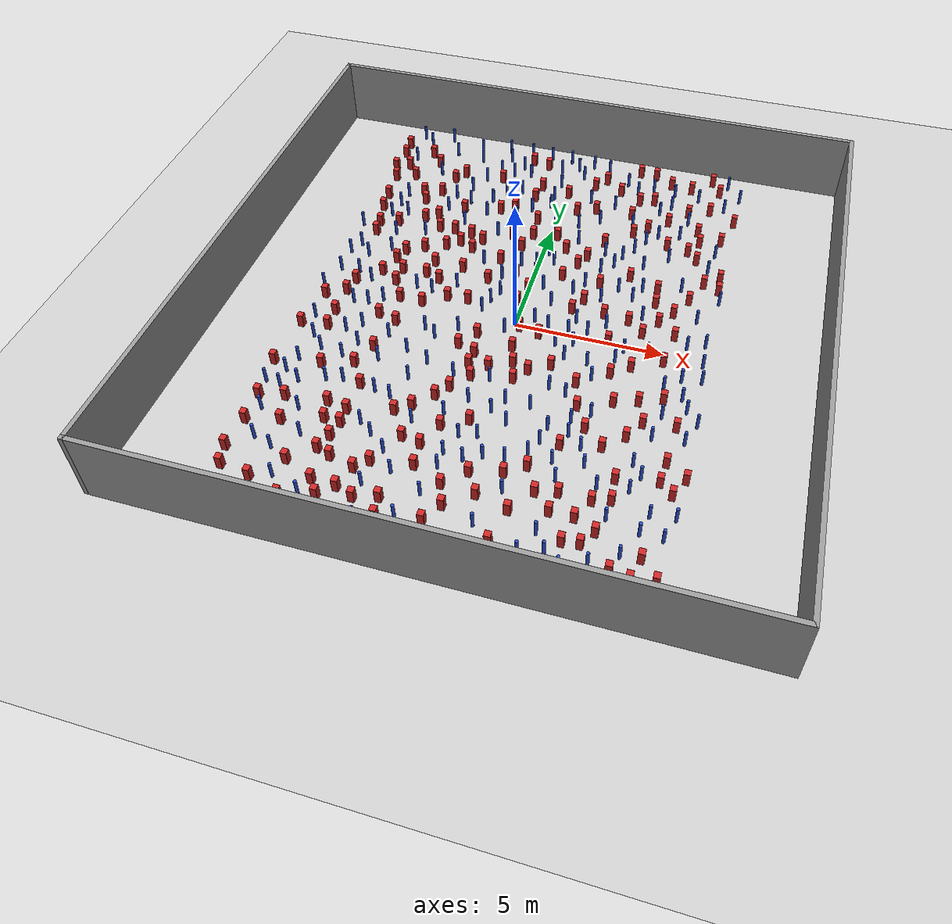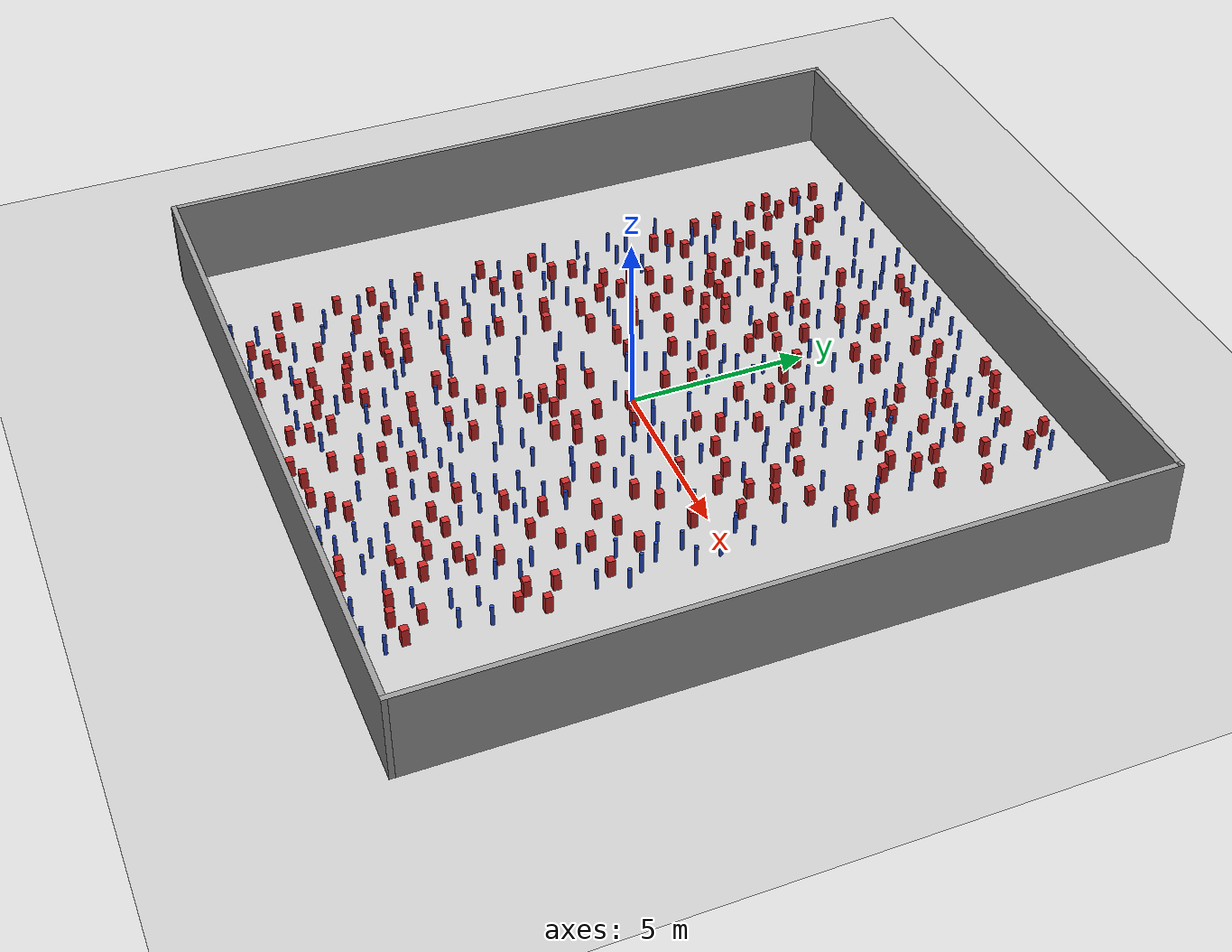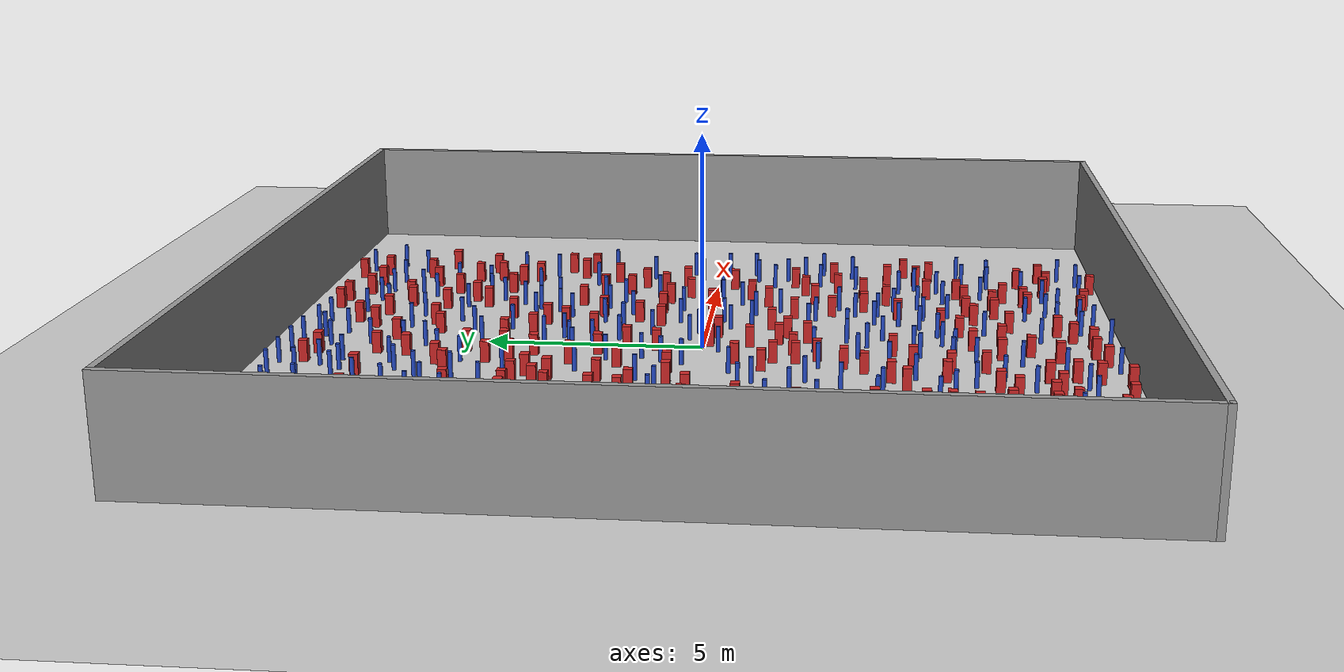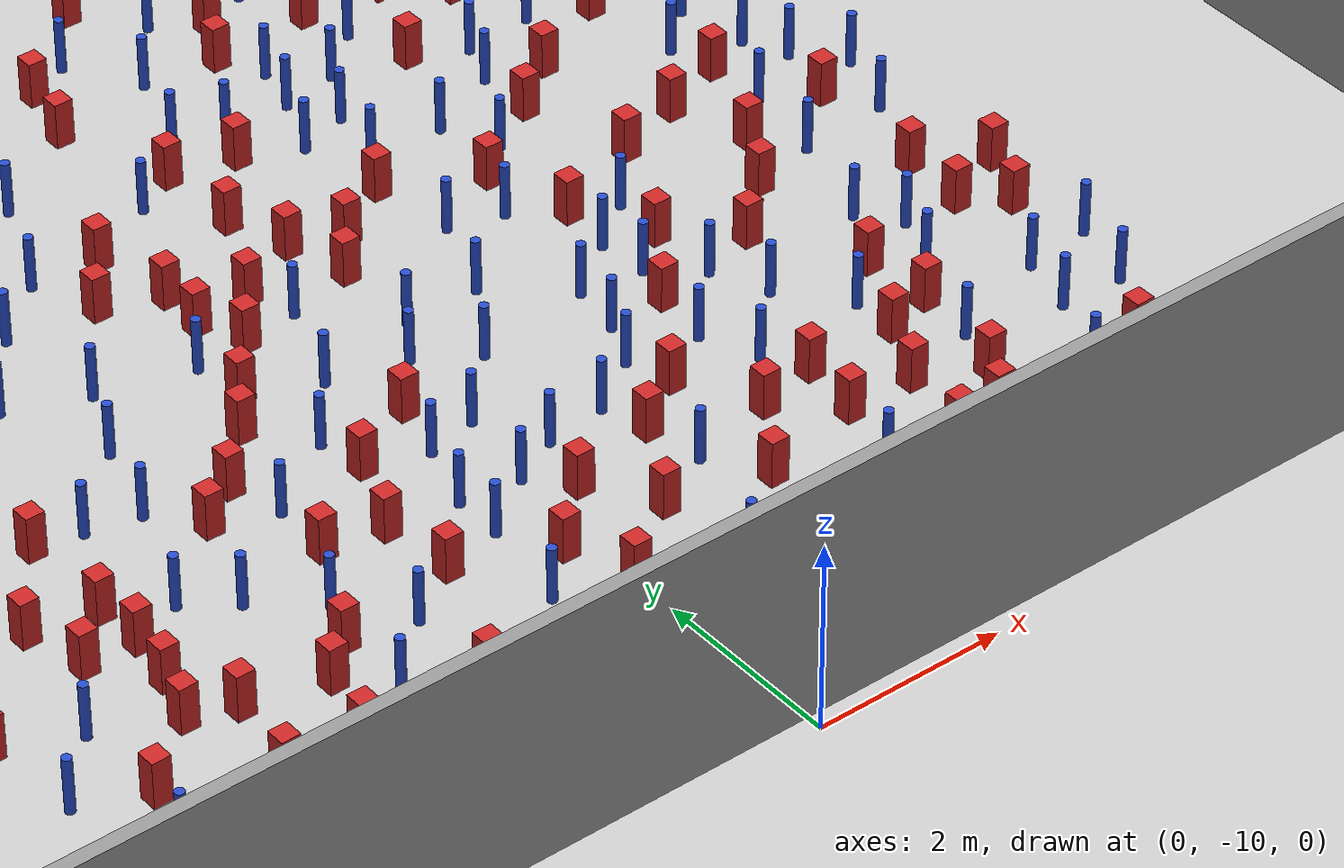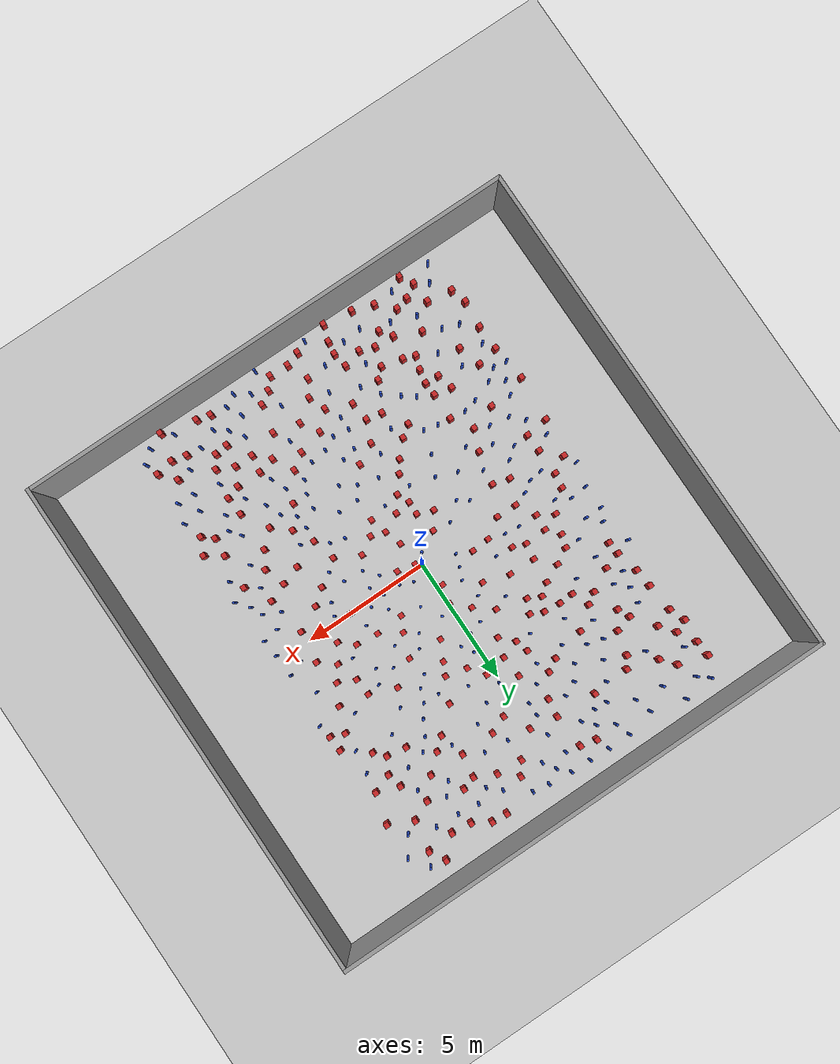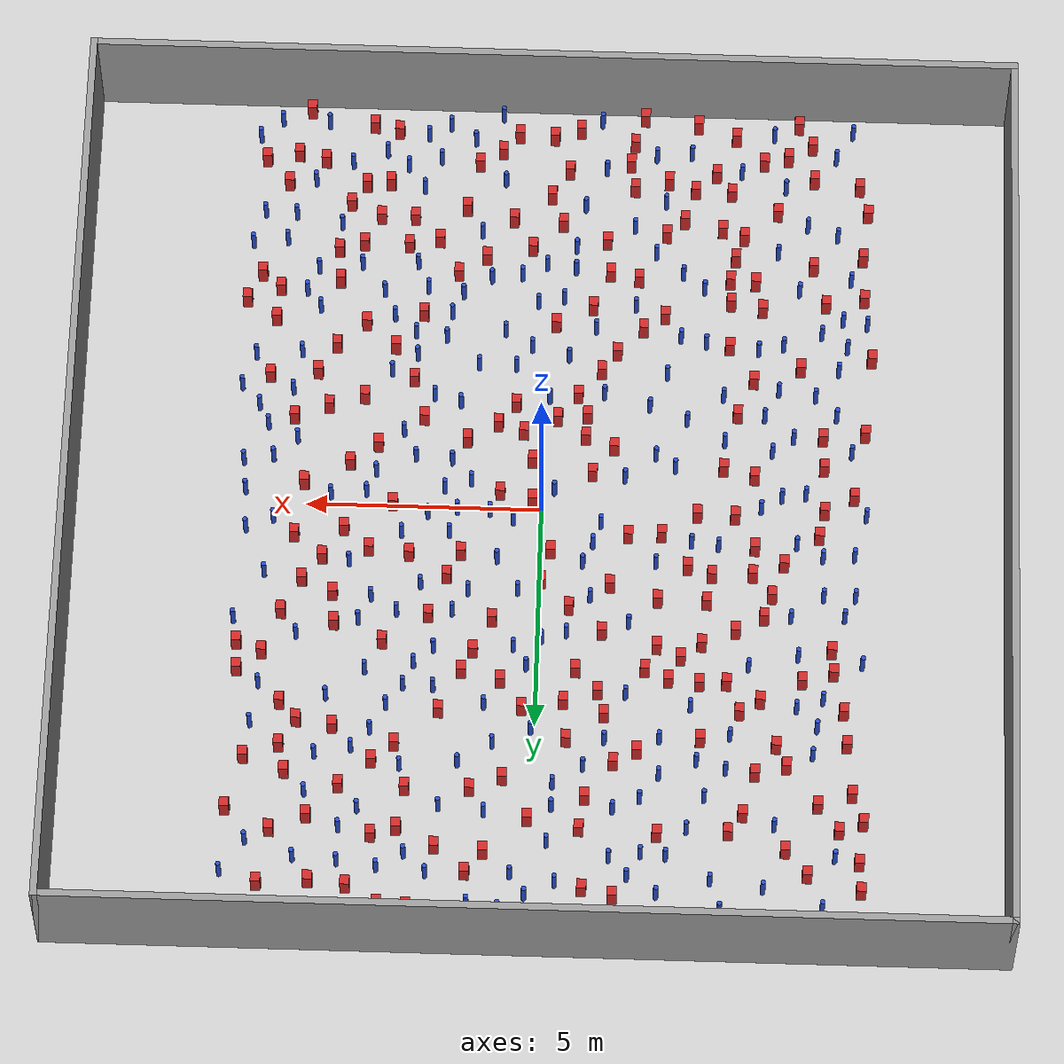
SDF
<sdf version="1.6">
 <world name="default">
  <light name="sun" type="directional">
   <pose>0 0 1000 0 -0 0</pose>
   <diffuse>0.8 0.8 0.8 1</diffuse>
   <specular>0.1 0.1 0.1 1</specular>
   <attenuation>
    <range>1000</range>
    <constant>0.9</constant>
    <linear>0.01</linear>
    <quadratic>0.001</quadratic>
   </attenuation>
   <direction>-0.5 0.5 -1</direction>
  </light>
  <model name="ground_plane">
   <static>1</static>
   <link name="link">
    <collision name="collision">
     <geometry><plane><normal>0 0 1</normal><size>100 100</size></plane></geometry>
     <surface><friction><ode><mu>100</mu><mu2>50</mu2></ode></friction></surface>
    </collision>
    <visual name="visual">
     <cast_shadows>0</cast_shadows>
     <geometry><plane><normal>0 0 1</normal><size>100 100</size></plane></geometry>
     <material>
      <ambient>1.0 1.0 1.0 1.0</ambient>
      <diffuse>0.8 0.8 0.8 1.0</diffuse>
      <specular>0.01 0.01 0.01 1.000000</specular>
     </material>
    </visual>
   </link>
  </model>
  <gravity>0 0 -9.8</gravity>
  <magnetic_field>6e-06 2.3e-05 -4.2e-05</magnetic_field>
  <atmosphere type="adiabatic"/>
  <physics name="default_physics" default="0" type="ode">
   <max_step_size>0.001</max_step_size>
   <real_time_factor>1</real_time_factor>
   <real_time_update_rate>1000</real_time_update_rate>
  </physics>
  <scene><ambient>0.4 0.4 0.4 1</ambient><background>0.7 0.7 0.7 1</background><shadows>1</shadows></scene>
  <spherical_coordinates>
   <surface_model>EARTH_WGS84</surface_model>
   <latitude_deg>0</latitude_deg>
   <longitude_deg>0</longitude_deg>
   <elevation>0</elevation>
   <heading_deg>0</heading_deg>
  </spherical_coordinates>
  <plugin name="gazebo_occupancy_map" filename="libgazebo_2Dmap_plugin.so">
   <map_resolution>0.05</map_resolution>
   <map_topic>generated_map</map_topic>
   <map_height>0.01</map_height>
   <map_size_x>50</map_size_x>
   <map_size_y>50</map_size_y>
  </plugin>
  <model name="NamedLocations">
   <static>true</static>
   <link name="DefaultStart"><pose>8.5 0 0 0 0 3.14</pose></link>
  </model>
  <model name="20x20_walls">
   <pose>0.044518 0.176112 0 0 -0 0</pose>
   <link name="Wall_1">
    <collision name="Wall_1_Collision">
     <geometry><box><size>20 0.15 2.5</size></box></geometry>
     <pose>0 0 1.25 0 -0 0</pose>
    </collision>
    <visual name="Wall_1_Visual">
     <pose>0 0 1.25 0 -0 0</pose>
     <geometry><box><size>20 0.15 2.5</size></box></geometry>
     <material>
      <script><uri>file://media/materials/scripts/gazebo.material</uri><name>Gazebo/Grey</name></script>
      <ambient>0.976471 0.992157 1 1</ambient>
     </material>
     <meta><layer>0</layer></meta>
    </visual>
    <pose>0 9.925 0 0 -0 0</pose>
   </link>
   <link name="Wall_3">
    <collision name="Wall_3_Collision">
     <geometry><box><size>20 0.15 2.5</size></box></geometry>
     <pose>0 0 1.25 0 -0 0</pose>
    </collision>
    <visual name="Wall_3_Visual">
     <pose>0 0 1.25 0 -0 0</pose>
     <geometry><box><size>20 0.15 2.5</size></box></geometry>
     <material>
      <script><uri>file://media/materials/scripts/gazebo.material</uri><name>Gazebo/Grey</name></script>
      <ambient>0.976471 0.992157 1 1</ambient>
     </material>
     <meta><layer>0</layer></meta>
    </visual>
    <pose>9.925 0 0 0 0 -1.5708</pose>
   </link>
   <link name="Wall_4">
    <collision name="Wall_4_Collision">
     <geometry><box><size>20 0.15 2.5</size></box></geometry>
     <pose>0 0 1.25 0 -0 0</pose>
    </collision>
    <visual name="Wall_4_Visual">
     <pose>0 0 1.25 0 -0 0</pose>
     <geometry><box><size>20 0.15 2.5</size></box></geometry>
     <material>
      <script><uri>file://media/materials/scripts/gazebo.material</uri><name>Gazebo/Grey</name></script>
      <ambient>0.976471 0.992157 1 1</ambient>
     </material>
     <meta><layer>0</layer></meta>
    </visual>
    <pose>0 -9.925 0 0 -0 3.14159</pose>
   </link>
   <link name="Wall_5">
    <collision name="Wall_5_Collision">
     <geometry><box><size>20 0.15 2.5</size></box></geometry>
     <pose>0 0 1.25 0 -0 0</pose>
    </collision>
    <visual name="Wall_5_Visual">
     <pose>0 0 1.25 0 -0 0</pose>
     <geometry><box><size>20 0.15 2.5</size></box></geometry>
     <material>
      <script><uri>file://media/materials/scripts/gazebo.material</uri><name>Gazebo/Grey</name></script>
      <ambient>0.976471 0.992157 1 1</ambient>
     </material>
     <meta><layer>0</layer></meta>
    </visual>
    <pose>-9.925 0 0 0 -0 1.5708</pose>
   </link>
   <static>1</static>
  </model>
  <model name="square_post_obstacle0">
   <static>true</static>
   <pose>-4.36775121202 6.96467512662 -6.11067671241e-07 -5.50515727128e-06 -8.79689657224e-07 2.37013304536e-05</pose>
   <link name="link">
    <pose>0 0 0.25 0 -0 0</pose>
    <inertial>
     <mass>100</mass>
     <inertia>
      <ixx>0.166667</ixx>
      <ixy>0</ixy>
      <ixz>0</ixz>
      <iyy>0.166667</iyy>
      <iyz>0</iyz>
      <izz>0.166667</izz>
     </inertia>
    </inertial>
    <collision name="collision"><geometry><box><size>.2 .2 .5</size></box></geometry></collision>
    <visual name="visual">
     <geometry><box><size>.2 .2 .5</size></box></geometry>
     <material>
      <script><name>Gazebo/Red</name><uri>file://media/materials/scripts/gazebo.material</uri></script>
     </material>
    </visual>
   </link>
  </model>
  <model name="square_post_obstacle1">
   <static>true</static>
   <pose>4.21814063579 5.20997985435 -6.11067671241e-07 -5.50515727128e-06 -8.79689657224e-07 2.37013304536e-05</pose>
   <link name="link">
    <pose>0 0 0.25 0 -0 0</pose>
    <inertial>
     <mass>100</mass>
     <inertia>
      <ixx>0.166667</ixx>
      <ixy>0</ixy>
      <ixz>0</ixz>
      <iyy>0.166667</iyy>
      <iyz>0</iyz>
      <izz>0.166667</izz>
     </inertia>
    </inertial>
    <collision name="collision"><geometry><box><size>.2 .2 .5</size></box></geometry></collision>
    <visual name="visual">
     <geometry><box><size>.2 .2 .5</size></box></geometry>
     <material>
      <script><name>Gazebo/Red</name><uri>file://media/materials/scripts/gazebo.material</uri></script>
     </material>
    </visual>
   </link>
  </model>
  <model name="pole_obstacle0">
   <static>true</static>
   <pose>1.79713980787 -2.40707328271 -9.47619616065e-06 5.49618799737e-07 2.36310414062e-07 -1.55090534798e-07</pose>
   <link name="link">
    <pose>0 0 0.3 0 -0 0</pose>
    <inertial>
     <mass>1</mass>
     <inertia><ixx>0.145833</ixx><ixy>0</ixy><ixz>0</ixz><iyy>0.145833</iyy><iyz>0</iyz><izz>0.125</izz></inertia>
    </inertial>
    <collision name="collision">
     <geometry><cylinder><radius>0.05</radius><length>.6</length></cylinder></geometry>
    </collision>
    <visual name="visual">
     <geometry><cylinder><radius>0.05</radius><length>.6</length></cylinder></geometry>
     <material>
      <script><name>Gazebo/Blue</name><uri>file://media/materials/scripts/gazebo.material</uri></script>
     </material>
    </visual>
   </link>
  </model>
  <model name="square_post_obstacle2">
   <static>true</static>
   <pose>0.289632002403 4.67580909844 -6.11067671241e-07 -5.50515727128e-06 -8.79689657224e-07 2.37013304536e-05</pose>
   <link name="link">
    <pose>0 0 0.25 0 -0 0</pose>
    <inertial>
     <mass>100</mass>
     <inertia>
      <ixx>0.166667</ixx>
      <ixy>0</ixy>
      <ixz>0</ixz>
      <iyy>0.166667</iyy>
      <iyz>0</iyz>
      <izz>0.166667</izz>
     </inertia>
    </inertial>
    <collision name="collision"><geometry><box><size>.2 .2 .5</size></box></geometry></collision>
    <visual name="visual">
     <geometry><box><size>.2 .2 .5</size></box></geometry>
     <material>
      <script><name>Gazebo/Red</name><uri>file://media/materials/scripts/gazebo.material</uri></script>
     </material>
    </visual>
   </link>
  </model>
  <model name="pole_obstacle1">
   <static>true</static>
   <pose>-6.87773396307 0.0528595417723 -9.47619616065e-06 5.49618799738e-07 2.36310414073e-07 -1.55090534795e-07</pose>
   <link name="link">
    <pose>0 0 0.3 0 -0 0</pose>
    <inertial>
     <mass>1</mass>
     <inertia><ixx>0.145833</ixx><ixy>0</ixy><ixz>0</ixz><iyy>0.145833</iyy><iyz>0</iyz><izz>0.125</izz></inertia>
    </inertial>
    <collision name="collision">
     <geometry><cylinder><radius>0.05</radius><length>.6</length></cylinder></geometry>
    </collision>
    <visual name="visual">
     <geometry><cylinder><radius>0.05</radius><length>.6</length></cylinder></geometry>
     <material>
      <script><name>Gazebo/Blue</name><uri>file://media/materials/scripts/gazebo.material</uri></script>
     </material>
    </visual>
   </link>
  </model>
  <model name="square_post_obstacle3">
   <static>true</static>
   <pose>-1.93206219649 -5.51208755053 -6.11067671241e-07 -5.50515727128e-06 -8.79689657224e-07 2.37013304536e-05</pose>
   <link name="link">
    <pose>0 0 0.25 0 -0 0</pose>
    <inertial>
     <mass>100</mass>
     <inertia>
      <ixx>0.166667</ixx>
      <ixy>0</ixy>
      <ixz>0</ixz>
      <iyy>0.166667</iyy>
      <iyz>0</iyz>
      <izz>0.166667</izz>
     </inertia>
    </inertial>
    <collision name="collision"><geometry><box><size>.2 .2 .5</size></box></geometry></collision>
    <visual name="visual">
     <geometry><box><size>.2 .2 .5</size></box></geometry>
     <material>
      <script><name>Gazebo/Red</name><uri>file://media/materials/scripts/gazebo.material</uri></script>
     </material>
    </visual>
   </link>
  </model>
  <model name="pole_obstacle2">
   <static>true</static>
   <pose>3.53113890478 2.21635083177 -9.47619616065e-06 5.49618799737e-07 2.36310414051e-07 -1.55090534807e-07</pose>
   <link name="link">
    <pose>0 0 0.3 0 -0 0</pose>
    <inertial>
     <mass>1</mass>
     <inertia><ixx>0.145833</ixx><ixy>0</ixy><ixz>0</ixz><iyy>0.145833</iyy><iyz>0</iyz><izz>0.125</izz></inertia>
    </inertial>
    <collision name="collision">
     <geometry><cylinder><radius>0.05</radius><length>.6</length></cylinder></geometry>
    </collision>
    <visual name="visual">
     <geometry><cylinder><radius>0.05</radius><length>.6</length></cylinder></geometry>
     <material>
      <script><name>Gazebo/Blue</name><uri>file://media/materials/scripts/gazebo.material</uri></script>
     </material>
    </visual>
   </link>
  </model>
  <model name="pole_obstacle3">
   <static>true</static>
   <pose>-6.2229804464 -2.29862749571 -9.47619616065e-06 5.49618799738e-07 2.36310414051e-07 -1.55090534805e-07</pose>
   <link name="link">
    <pose>0 0 0.3 0 -0 0</pose>
    <inertial>
     <mass>1</mass>
     <inertia><ixx>0.145833</ixx><ixy>0</ixy><ixz>0</ixz><iyy>0.145833</iyy><iyz>0</iyz><izz>0.125</izz></inertia>
    </inertial>
    <collision name="collision">
     <geometry><cylinder><radius>0.05</radius><length>.6</length></cylinder></geometry>
    </collision>
    <visual name="visual">
     <geometry><cylinder><radius>0.05</radius><length>.6</length></cylinder></geometry>
     <material>
      <script><name>Gazebo/Blue</name><uri>file://media/materials/scripts/gazebo.material</uri></script>
     </material>
    </visual>
   </link>
  </model>
  <model name="square_post_obstacle4">
   <static>true</static>
   <pose>-1.65749616319 5.88070329068 -6.11067671241e-07 -5.50515727128e-06 -8.79689657224e-07 2.37013304536e-05</pose>
   <link name="link">
    <pose>0 0 0.25 0 -0 0</pose>
    <inertial>
     <mass>100</mass>
     <inertia>
      <ixx>0.166667</ixx>
      <ixy>0</ixy>
      <ixz>0</ixz>
      <iyy>0.166667</iyy>
      <iyz>0</iyz>
      <izz>0.166667</izz>
     </inertia>
    </inertial>
    <collision name="collision"><geometry><box><size>.2 .2 .5</size></box></geometry></collision>
    <visual name="visual">
     <geometry><box><size>.2 .2 .5</size></box></geometry>
     <material>
      <script><name>Gazebo/Red</name><uri>file://media/materials/scripts/gazebo.material</uri></script>
     </material>
    </visual>
   </link>
  </model>
  <model name="square_post_obstacle5">
   <static>true</static>
   <pose>0.197511593898 -0.157477024642 -6.11067671241e-07 -5.50515727128e-06 -8.79689657224e-07 2.37013304536e-05</pose>
   <link name="link">
    <pose>0 0 0.25 0 -0 0</pose>
    <inertial>
     <mass>100</mass>
     <inertia>
      <ixx>0.166667</ixx>
      <ixy>0</ixy>
      <ixz>0</ixz>
      <iyy>0.166667</iyy>
      <iyz>0</iyz>
      <izz>0.166667</izz>
     </inertia>
    </inertial>
    <collision name="collision"><geometry><box><size>.2 .2 .5</size></box></geometry></collision>
    <visual name="visual">
     <geometry><box><size>.2 .2 .5</size></box></geometry>
     <material>
      <script><name>Gazebo/Red</name><uri>file://media/materials/scripts/gazebo.material</uri></script>
     </material>
    </visual>
   </link>
  </model>
  <model name="square_post_obstacle6">
   <static>true</static>
   <pose>4.34006714366 -7.19658364788 -6.11067671241e-07 -5.50515727128e-06 -8.79689657224e-07 2.37013304536e-05</pose>
   <link name="link">
    <pose>0 0 0.25 0 -0 0</pose>
    <inertial>
     <mass>100</mass>
     <inertia>
      <ixx>0.166667</ixx>
      <ixy>0</ixy>
      <ixz>0</ixz>
      <iyy>0.166667</iyy>
      <iyz>0</iyz>
      <izz>0.166667</izz>
     </inertia>
    </inertial>
    <collision name="collision"><geometry><box><size>.2 .2 .5</size></box></geometry></collision>
    <visual name="visual">
     <geometry><box><size>.2 .2 .5</size></box></geometry>
     <material>
      <script><name>Gazebo/Red</name><uri>file://media/materials/scripts/gazebo.material</uri></script>
     </material>
    </visual>
   </link>
  </model>
  <model name="pole_obstacle4">
   <static>true</static>
   <pose>6.36612746297 -0.911602490669 -9.47619616065e-06 5.49618799737e-07 2.36310414061e-07 -1.550905348e-07</pose>
   <link name="link">
    <pose>0 0 0.3 0 -0 0</pose>
    <inertial>
     <mass>1</mass>
     <inertia><ixx>0.145833</ixx><ixy>0</ixy><ixz>0</ixz><iyy>0.145833</iyy><iyz>0</iyz><izz>0.125</izz></inertia>
    </inertial>
    <collision name="collision">
     <geometry><cylinder><radius>0.05</radius><length>.6</length></cylinder></geometry>
    </collision>
    <visual name="visual">
     <geometry><cylinder><radius>0.05</radius><length>.6</length></cylinder></geometry>
     <material>
      <script><name>Gazebo/Blue</name><uri>file://media/materials/scripts/gazebo.material</uri></script>
     </material>
    </visual>
   </link>
  </model>
  <model name="pole_obstacle5">
   <static>true</static>
   <pose>-2.47776814375 -7.39199694764 -9.47619616065e-06 5.49618799738e-07 2.3631041406e-07 -1.55090534801e-07</pose>
   <link name="link">
    <pose>0 0 0.3 0 -0 0</pose>
    <inertial>
     <mass>1</mass>
     <inertia><ixx>0.145833</ixx><ixy>0</ixy><ixz>0</ixz><iyy>0.145833</iyy><iyz>0</iyz><izz>0.125</izz></inertia>
    </inertial>
    <collision name="collision">
     <geometry><cylinder><radius>0.05</radius><length>.6</length></cylinder></geometry>
    </collision>
    <visual name="visual">
     <geometry><cylinder><radius>0.05</radius><length>.6</length></cylinder></geometry>
     <material>
      <script><name>Gazebo/Blue</name><uri>file://media/materials/scripts/gazebo.material</uri></script>
     </material>
    </visual>
   </link>
  </model>
  <model name="square_post_obstacle7">
   <static>true</static>
   <pose>-3.14198936827 -9.34320137759 -6.11067671241e-07 -5.50515727128e-06 -8.79689657224e-07 2.37013304536e-05</pose>
   <link name="link">
    <pose>0 0 0.25 0 -0 0</pose>
    <inertial>
     <mass>100</mass>
     <inertia>
      <ixx>0.166667</ixx>
      <ixy>0</ixy>
      <ixz>0</ixz>
      <iyy>0.166667</iyy>
      <iyz>0</iyz>
      <izz>0.166667</izz>
     </inertia>
    </inertial>
    <collision name="collision"><geometry><box><size>.2 .2 .5</size></box></geometry></collision>
    <visual name="visual">
     <geometry><box><size>.2 .2 .5</size></box></geometry>
     <material>
      <script><name>Gazebo/Red</name><uri>file://media/materials/scripts/gazebo.material</uri></script>
     </material>
    </visual>
   </link>
  </model>
  <model name="square_post_obstacle8">
   <static>true</static>
   <pose>-6.66816803938 -7.88810534937 -6.11067671241e-07 -5.50515727128e-06 -8.79689657224e-07 2.37013304536e-05</pose>
   <link name="link">
    <pose>0 0 0.25 0 -0 0</pose>
    <inertial>
     <mass>100</mass>
     <inertia>
      <ixx>0.166667</ixx>
      <ixy>0</ixy>
      <ixz>0</ixz>
      <iyy>0.166667</iyy>
      <iyz>0</iyz>
      <izz>0.166667</izz>
     </inertia>
    </inertial>
    <collision name="collision"><geometry><box><size>.2 .2 .5</size></box></geometry></collision>
    <visual name="visual">
     <geometry><box><size>.2 .2 .5</size></box></geometry>
     <material>
      <script><name>Gazebo/Red</name><uri>file://media/materials/scripts/gazebo.material</uri></script>
     </material>
    </visual>
   </link>
  </model>
  <model name="pole_obstacle6">
   <static>true</static>
   <pose>2.6191119911 8.05276596261 -9.4761961606e-06 5.49618799729e-07 2.36310414e-07 -1.55090534824e-07</pose>
   <link name="link">
    <pose>0 0 0.3 0 -0 0</pose>
    <inertial>
     <mass>1</mass>
     <inertia><ixx>0.145833</ixx><ixy>0</ixy><ixz>0</ixz><iyy>0.145833</iyy><iyz>0</iyz><izz>0.125</izz></inertia>
    </inertial>
    <collision name="collision">
     <geometry><cylinder><radius>0.05</radius><length>.6</length></cylinder></geometry>
    </collision>
    <visual name="visual">
     <geometry><cylinder><radius>0.05</radius><length>.6</length></cylinder></geometry>
     <material>
      <script><name>Gazebo/Blue</name><uri>file://media/materials/scripts/gazebo.material</uri></script>
     </material>
    </visual>
   </link>
  </model>
  <model name="pole_obstacle7">
   <static>true</static>
   <pose>-5.0682806766 -3.96761647848 -9.47619616065e-06 5.49618799737e-07 2.36310414056e-07 -1.55090534802e-07</pose>
   <link name="link">
    <pose>0 0 0.3 0 -0 0</pose>
    <inertial>
     <mass>1</mass>
     <inertia><ixx>0.145833</ixx><ixy>0</ixy><ixz>0</ixz><iyy>0.145833</iyy><iyz>0</iyz><izz>0.125</izz></inertia>
    </inertial>
    <collision name="collision">
     <geometry><cylinder><radius>0.05</radius><length>.6</length></cylinder></geometry>
    </collision>
    <visual name="visual">
     <geometry><cylinder><radius>0.05</radius><length>.6</length></cylinder></geometry>
     <material>
      <script><name>Gazebo/Blue</name><uri>file://media/materials/scripts/gazebo.material</uri></script>
     </material>
    </visual>
   </link>
  </model>
  <model name="square_post_obstacle9">
   <static>true</static>
   <pose>0.98204102087 -1.93543841282 -6.11067671241e-07 -5.50515727128e-06 -8.79689657224e-07 2.37013304536e-05</pose>
   <link name="link">
    <pose>0 0 0.25 0 -0 0</pose>
    <inertial>
     <mass>100</mass>
     <inertia>
      <ixx>0.166667</ixx>
      <ixy>0</ixy>
      <ixz>0</ixz>
      <iyy>0.166667</iyy>
      <iyz>0</iyz>
      <izz>0.166667</izz>
     </inertia>
    </inertial>
    <collision name="collision"><geometry><box><size>.2 .2 .5</size></box></geometry></collision>
    <visual name="visual">
     <geometry><box><size>.2 .2 .5</size></box></geometry>
     <material>
      <script><name>Gazebo/Red</name><uri>file://media/materials/scripts/gazebo.material</uri></script>
     </material>
    </visual>
   </link>
  </model>
  <model name="square_post_obstacle10">
   <static>true</static>
   <pose>4.01620284526 -6.22145135886 -6.11067671241e-07 -5.50515727128e-06 -8.79689657224e-07 2.37013304536e-05</pose>
   <link name="link">
    <pose>0 0 0.25 0 -0 0</pose>
    <inertial>
     <mass>100</mass>
     <inertia>
      <ixx>0.166667</ixx>
      <ixy>0</ixy>
      <ixz>0</ixz>
      <iyy>0.166667</iyy>
      <iyz>0</iyz>
      <izz>0.166667</izz>
     </inertia>
    </inertial>
    <collision name="collision"><geometry><box><size>.2 .2 .5</size></box></geometry></collision>
    <visual name="visual">
     <geometry><box><size>.2 .2 .5</size></box></geometry>
     <material>
      <script><name>Gazebo/Red</name><uri>file://media/materials/scripts/gazebo.material</uri></script>
     </material>
    </visual>
   </link>
  </model>
  <model name="square_post_obstacle11">
   <static>true</static>
   <pose>4.56887856863 8.70819222688 -6.11067671241e-07 -5.50515727128e-06 -8.79689657224e-07 2.37013304536e-05</pose>
   <link name="link">
    <pose>0 0 0.25 0 -0 0</pose>
    <inertial>
     <mass>100</mass>
     <inertia>
      <ixx>0.166667</ixx>
      <ixy>0</ixy>
      <ixz>0</ixz>
      <iyy>0.166667</iyy>
      <iyz>0</iyz>
      <izz>0.166667</izz>
     </inertia>
    </inertial>
    <collision name="collision"><geometry><box><size>.2 .2 .5</size></box></geometry></collision>
    <visual name="visual">
     <geometry><box><size>.2 .2 .5</size></box></geometry>
     <material>
      <script><name>Gazebo/Red</name><uri>file://media/materials/scripts/gazebo.material</uri></script>
     </material>
    </visual>
   </link>
  </model>
  <model name="square_post_obstacle12">
   <static>true</static>
   <pose>-2.50106417843 2.11142147697 -6.11067671241e-07 -5.50515727128e-06 -8.79689657224e-07 2.37013304536e-05</pose>
   <link name="link">
    <pose>0 0 0.25 0 -0 0</pose>
    <inertial>
     <mass>100</mass>
     <inertia>
      <ixx>0.166667</ixx>
      <ixy>0</ixy>
      <ixz>0</ixz>
      <iyy>0.166667</iyy>
      <iyz>0</iyz>
      <izz>0.166667</izz>
     </inertia>
    </inertial>
    <collision name="collision"><geometry><box><size>.2 .2 .5</size></box></geometry></collision>
    <visual name="visual">
     <geometry><box><size>.2 .2 .5</size></box></geometry>
     <material>
      <script><name>Gazebo/Red</name><uri>file://media/materials/scripts/gazebo.material</uri></script>
     </material>
    </visual>
   </link>
  </model>
  <model name="square_post_obstacle13">
   <static>true</static>
   <pose>4.09865665631 -0.925299943334 -6.11067671241e-07 -5.50515727128e-06 -8.79689657224e-07 2.37013304536e-05</pose>
   <link name="link">
    <pose>0 0 0.25 0 -0 0</pose>
    <inertial>
     <mass>100</mass>
     <inertia>
      <ixx>0.166667</ixx>
      <ixy>0</ixy>
      <ixz>0</ixz>
      <iyy>0.166667</iyy>
      <iyz>0</iyz>
      <izz>0.166667</izz>
     </inertia>
    </inertial>
    <collision name="collision"><geometry><box><size>.2 .2 .5</size></box></geometry></collision>
    <visual name="visual">
     <geometry><box><size>.2 .2 .5</size></box></geometry>
     <material>
      <script><name>Gazebo/Red</name><uri>file://media/materials/scripts/gazebo.material</uri></script>
     </material>
    </visual>
   </link>
  </model>
  <model name="pole_obstacle8">
   <static>true</static>
   <pose>5.81048403324 4.28842071337 -9.47619616065e-06 5.49618799737e-07 2.36310414037e-07 -1.55090534814e-07</pose>
   <link name="link">
    <pose>0 0 0.3 0 -0 0</pose>
    <inertial>
     <mass>1</mass>
     <inertia><ixx>0.145833</ixx><ixy>0</ixy><ixz>0</ixz><iyy>0.145833</iyy><iyz>0</iyz><izz>0.125</izz></inertia>
    </inertial>
    <collision name="collision">
     <geometry><cylinder><radius>0.05</radius><length>.6</length></cylinder></geometry>
    </collision>
    <visual name="visual">
     <geometry><cylinder><radius>0.05</radius><length>.6</length></cylinder></geometry>
     <material>
      <script><name>Gazebo/Blue</name><uri>file://media/materials/scripts/gazebo.material</uri></script>
     </material>
    </visual>
   </link>
  </model>
  <model name="square_post_obstacle14">
   <static>true</static>
   <pose>3.91428252671 -9.15103433209 -6.11067671241e-07 -5.50515727128e-06 -8.79689657224e-07 2.37013304536e-05</pose>
   <link name="link">
    <pose>0 0 0.25 0 -0 0</pose>
    <inertial>
     <mass>100</mass>
     <inertia>
      <ixx>0.166667</ixx>
      <ixy>0</ixy>
      <ixz>0</ixz>
      <iyy>0.166667</iyy>
      <iyz>0</iyz>
      <izz>0.166667</izz>
     </inertia>
    </inertial>
    <collision name="collision"><geometry><box><size>.2 .2 .5</size></box></geometry></collision>
    <visual name="visual">
     <geometry><box><size>.2 .2 .5</size></box></geometry>
     <material>
      <script><name>Gazebo/Red</name><uri>file://media/materials/scripts/gazebo.material</uri></script>
     </material>
    </visual>
   </link>
  </model>
  <model name="square_post_obstacle15">
   <static>true</static>
   <pose>-5.04168076702 5.39787669439 -6.11067671241e-07 -5.50515727128e-06 -8.79689657224e-07 2.37013304536e-05</pose>
   <link name="link">
    <pose>0 0 0.25 0 -0 0</pose>
    <inertial>
     <mass>100</mass>
     <inertia>
      <ixx>0.166667</ixx>
      <ixy>0</ixy>
      <ixz>0</ixz>
      <iyy>0.166667</iyy>
      <iyz>0</iyz>
      <izz>0.166667</izz>
     </inertia>
    </inertial>
    <collision name="collision"><geometry><box><size>.2 .2 .5</size></box></geometry></collision>
    <visual name="visual">
     <geometry><box><size>.2 .2 .5</size></box></geometry>
     <material>
      <script><name>Gazebo/Red</name><uri>file://media/materials/scripts/gazebo.material</uri></script>
     </material>
    </visual>
   </link>
  </model>
  <model name="square_post_obstacle16">
   <static>true</static>
   <pose>-6.51756934402 5.33370531011 -6.11067671241e-07 -5.50515727128e-06 -8.79689657224e-07 2.37013304536e-05</pose>
   <link name="link">
    <pose>0 0 0.25 0 -0 0</pose>
    <inertial>
     <mass>100</mass>
     <inertia>
      <ixx>0.166667</ixx>
      <ixy>0</ixy>
      <ixz>0</ixz>
      <iyy>0.166667</iyy>
      <iyz>0</iyz>
      <izz>0.166667</izz>
     </inertia>
    </inertial>
    <collision name="collision"><geometry><box><size>.2 .2 .5</size></box></geometry></collision>
    <visual name="visual">
     <geometry><box><size>.2 .2 .5</size></box></geometry>
     <material>
      <script><name>Gazebo/Red</name><uri>file://media/materials/scripts/gazebo.material</uri></script>
     </material>
    </visual>
   </link>
  </model>
  <model name="pole_obstacle9">
   <static>true</static>
   <pose>1.01335251452 -7.83346470097 -9.47619616065e-06 5.49618799737e-07 2.36310414059e-07 -1.550905348e-07</pose>
   <link name="link">
    <pose>0 0 0.3 0 -0 0</pose>
    <inertial>
     <mass>1</mass>
     <inertia><ixx>0.145833</ixx><ixy>0</ixy><ixz>0</ixz><iyy>0.145833</iyy><iyz>0</iyz><izz>0.125</izz></inertia>
    </inertial>
    <collision name="collision">
     <geometry><cylinder><radius>0.05</radius><length>.6</length></cylinder></geometry>
    </collision>
    <visual name="visual">
     <geometry><cylinder><radius>0.05</radius><length>.6</length></cylinder></geometry>
     <material>
      <script><name>Gazebo/Blue</name><uri>file://media/materials/scripts/gazebo.material</uri></script>
     </material>
    </visual>
   </link>
  </model>
  <model name="square_post_obstacle17">
   <static>true</static>
   <pose>6.47951026331 -4.78304410986 -6.11067671241e-07 -5.50515727128e-06 -8.79689657224e-07 2.37013304536e-05</pose>
   <link name="link">
    <pose>0 0 0.25 0 -0 0</pose>
    <inertial>
     <mass>100</mass>
     <inertia>
      <ixx>0.166667</ixx>
      <ixy>0</ixy>
      <ixz>0</ixz>
      <iyy>0.166667</iyy>
      <iyz>0</iyz>
      <izz>0.166667</izz>
     </inertia>
    </inertial>
    <collision name="collision"><geometry><box><size>.2 .2 .5</size></box></geometry></collision>
    <visual name="visual">
     <geometry><box><size>.2 .2 .5</size></box></geometry>
     <material>
      <script><name>Gazebo/Red</name><uri>file://media/materials/scripts/gazebo.material</uri></script>
     </material>
    </visual>
   </link>
  </model>
  <model name="square_post_obstacle18">
   <static>true</static>
   <pose>0.617176443368 -2.41358064817 -6.11067671241e-07 -5.50515727128e-06 -8.79689657224e-07 2.37013304536e-05</pose>
   <link name="link">
    <pose>0 0 0.25 0 -0 0</pose>
    <inertial>
     <mass>100</mass>
     <inertia>
      <ixx>0.166667</ixx>
      <ixy>0</ixy>
      <ixz>0</ixz>
      <iyy>0.166667</iyy>
      <iyz>0</iyz>
      <izz>0.166667</izz>
     </inertia>
    </inertial>
    <collision name="collision"><geometry><box><size>.2 .2 .5</size></box></geometry></collision>
    <visual name="visual">
     <geometry><box><size>.2 .2 .5</size></box></geometry>
     <material>
      <script><name>Gazebo/Red</name><uri>file://media/materials/scripts/gazebo.material</uri></script>
     </material>
    </visual>
   </link>
  </model>
  <model name="pole_obstacle10">
   <static>true</static>
   <pose>-3.2098187899 7.34159491129 -9.47619616065e-06 5.49618799738e-07 2.3631041406e-07 -1.55090534801e-07</pose>
   <link name="link">
    <pose>0 0 0.3 0 -0 0</pose>
    <inertial>
     <mass>1</mass>
     <inertia><ixx>0.145833</ixx><ixy>0</ixy><ixz>0</ixz><iyy>0.145833</iyy><iyz>0</iyz><izz>0.125</izz></inertia>
    </inertial>
    <collision name="collision">
     <geometry><cylinder><radius>0.05</radius><length>.6</length></cylinder></geometry>
    </collision>
    <visual name="visual">
     <geometry><cylinder><radius>0.05</radius><length>.6</length></cylinder></geometry>
     <material>
      <script><name>Gazebo/Blue</name><uri>file://media/materials/scripts/gazebo.material</uri></script>
     </material>
    </visual>
   </link>
  </model>
  <model name="square_post_obstacle19">
   <static>true</static>
   <pose>-0.263909073684 -6.82775434826 -6.11067671241e-07 -5.50515727128e-06 -8.79689657224e-07 2.37013304536e-05</pose>
   <link name="link">
    <pose>0 0 0.25 0 -0 0</pose>
    <inertial>
     <mass>100</mass>
     <inertia>
      <ixx>0.166667</ixx>
      <ixy>0</ixy>
      <ixz>0</ixz>
      <iyy>0.166667</iyy>
      <iyz>0</iyz>
      <izz>0.166667</izz>
     </inertia>
    </inertial>
    <collision name="collision"><geometry><box><size>.2 .2 .5</size></box></geometry></collision>
    <visual name="visual">
     <geometry><box><size>.2 .2 .5</size></box></geometry>
     <material>
      <script><name>Gazebo/Red</name><uri>file://media/materials/scripts/gazebo.material</uri></script>
     </material>
    </visual>
   </link>
  </model>
  <model name="pole_obstacle11">
   <static>true</static>
   <pose>-6.5538199711 -1.43021829592 -9.47619616065e-06 5.49618799738e-07 2.36310414071e-07 -1.55090534796e-07</pose>
   <link name="link">
    <pose>0 0 0.3 0 -0 0</pose>
    <inertial>
     <mass>1</mass>
     <inertia><ixx>0.145833</ixx><ixy>0</ixy><ixz>0</ixz><iyy>0.145833</iyy><iyz>0</iyz><izz>0.125</izz></inertia>
    </inertial>
    <collision name="collision">
     <geometry><cylinder><radius>0.05</radius><length>.6</length></cylinder></geometry>
    </collision>
    <visual name="visual">
     <geometry><cylinder><radius>0.05</radius><length>.6</length></cylinder></geometry>
     <material>
      <script><name>Gazebo/Blue</name><uri>file://media/materials/scripts/gazebo.material</uri></script>
     </material>
    </visual>
   </link>
  </model>
  <model name="square_post_obstacle20">
   <static>true</static>
   <pose>3.67671077395 -6.89130753897 -6.11067671241e-07 -5.50515727128e-06 -8.79689657224e-07 2.37013304536e-05</pose>
   <link name="link">
    <pose>0 0 0.25 0 -0 0</pose>
    <inertial>
     <mass>100</mass>
     <inertia>
      <ixx>0.166667</ixx>
      <ixy>0</ixy>
      <ixz>0</ixz>
      <iyy>0.166667</iyy>
      <iyz>0</iyz>
      <izz>0.166667</izz>
     </inertia>
    </inertial>
    <collision name="collision"><geometry><box><size>.2 .2 .5</size></box></geometry></collision>
    <visual name="visual">
     <geometry><box><size>.2 .2 .5</size></box></geometry>
     <material>
      <script><name>Gazebo/Red</name><uri>file://media/materials/scripts/gazebo.material</uri></script>
     </material>
    </visual>
   </link>
  </model>
  <model name="pole_obstacle12">
   <static>true</static>
   <pose>3.99530567241 7.51076555983 -9.47619616065e-06 5.49618799737e-07 2.36310414049e-07 -1.55090534808e-07</pose>
   <link name="link">
    <pose>0 0 0.3 0 -0 0</pose>
    <inertial>
     <mass>1</mass>
     <inertia><ixx>0.145833</ixx><ixy>0</ixy><ixz>0</ixz><iyy>0.145833</iyy><iyz>0</iyz><izz>0.125</izz></inertia>
    </inertial>
    <collision name="collision">
     <geometry><cylinder><radius>0.05</radius><length>.6</length></cylinder></geometry>
    </collision>
    <visual name="visual">
     <geometry><cylinder><radius>0.05</radius><length>.6</length></cylinder></geometry>
     <material>
      <script><name>Gazebo/Blue</name><uri>file://media/materials/scripts/gazebo.material</uri></script>
     </material>
    </visual>
   </link>
  </model>
  <model name="square_post_obstacle21">
   <static>true</static>
   <pose>6.22377521215 -8.25365913007 -6.11067671241e-07 -5.50515727128e-06 -8.79689657224e-07 2.37013304536e-05</pose>
   <link name="link">
    <pose>0 0 0.25 0 -0 0</pose>
    <inertial>
     <mass>100</mass>
     <inertia>
      <ixx>0.166667</ixx>
      <ixy>0</ixy>
      <ixz>0</ixz>
      <iyy>0.166667</iyy>
      <iyz>0</iyz>
      <izz>0.166667</izz>
     </inertia>
    </inertial>
    <collision name="collision"><geometry><box><size>.2 .2 .5</size></box></geometry></collision>
    <visual name="visual">
     <geometry><box><size>.2 .2 .5</size></box></geometry>
     <material>
      <script><name>Gazebo/Red</name><uri>file://media/materials/scripts/gazebo.material</uri></script>
     </material>
    </visual>
   </link>
  </model>
  <model name="pole_obstacle13">
   <static>true</static>
   <pose>-5.41343163855 0.755619386022 -9.47619616065e-06 5.49618799737e-07 2.36310414061e-07 -1.550905348e-07</pose>
   <link name="link">
    <pose>0 0 0.3 0 -0 0</pose>
    <inertial>
     <mass>1</mass>
     <inertia><ixx>0.145833</ixx><ixy>0</ixy><ixz>0</ixz><iyy>0.145833</iyy><iyz>0</iyz><izz>0.125</izz></inertia>
    </inertial>
    <collision name="collision">
     <geometry><cylinder><radius>0.05</radius><length>.6</length></cylinder></geometry>
    </collision>
    <visual name="visual">
     <geometry><cylinder><radius>0.05</radius><length>.6</length></cylinder></geometry>
     <material>
      <script><name>Gazebo/Blue</name><uri>file://media/materials/scripts/gazebo.material</uri></script>
     </material>
    </visual>
   </link>
  </model>
  <model name="square_post_obstacle22">
   <static>true</static>
   <pose>1.5766084047 3.87303385566 -6.11067671241e-07 -5.50515727128e-06 -8.79689657224e-07 2.37013304536e-05</pose>
   <link name="link">
    <pose>0 0 0.25 0 -0 0</pose>
    <inertial>
     <mass>100</mass>
     <inertia>
      <ixx>0.166667</ixx>
      <ixy>0</ixy>
      <ixz>0</ixz>
      <iyy>0.166667</iyy>
      <iyz>0</iyz>
      <izz>0.166667</izz>
     </inertia>
    </inertial>
    <collision name="collision"><geometry><box><size>.2 .2 .5</size></box></geometry></collision>
    <visual name="visual">
     <geometry><box><size>.2 .2 .5</size></box></geometry>
     <material>
      <script><name>Gazebo/Red</name><uri>file://media/materials/scripts/gazebo.material</uri></script>
     </material>
    </visual>
   </link>
  </model>
  <model name="pole_obstacle14">
   <static>true</static>
   <pose>5.13563322867 -7.72506180327 -9.47619616065e-06 5.49618799737e-07 2.36310414037e-07 -1.55090534814e-07</pose>
   <link name="link">
    <pose>0 0 0.3 0 -0 0</pose>
    <inertial>
     <mass>1</mass>
     <inertia><ixx>0.145833</ixx><ixy>0</ixy><ixz>0</ixz><iyy>0.145833</iyy><iyz>0</iyz><izz>0.125</izz></inertia>
    </inertial>
    <collision name="collision">
     <geometry><cylinder><radius>0.05</radius><length>.6</length></cylinder></geometry>
    </collision>
    <visual name="visual">
     <geometry><cylinder><radius>0.05</radius><length>.6</length></cylinder></geometry>
     <material>
      <script><name>Gazebo/Blue</name><uri>file://media/materials/scripts/gazebo.material</uri></script>
     </material>
    </visual>
   </link>
  </model>
  <model name="pole_obstacle15">
   <static>true</static>
   <pose>-5.97070912726 1.04615369268 -9.47619616065e-06 5.49618799737e-07 2.36310414071e-07 -1.55090534795e-07</pose>
   <link name="link">
    <pose>0 0 0.3 0 -0 0</pose>
    <inertial>
     <mass>1</mass>
     <inertia><ixx>0.145833</ixx><ixy>0</ixy><ixz>0</ixz><iyy>0.145833</iyy><iyz>0</iyz><izz>0.125</izz></inertia>
    </inertial>
    <collision name="collision">
     <geometry><cylinder><radius>0.05</radius><length>.6</length></cylinder></geometry>
    </collision>
    <visual name="visual">
     <geometry><cylinder><radius>0.05</radius><length>.6</length></cylinder></geometry>
     <material>
      <script><name>Gazebo/Blue</name><uri>file://media/materials/scripts/gazebo.material</uri></script>
     </material>
    </visual>
   </link>
  </model>
  <model name="pole_obstacle16">
   <static>true</static>
   <pose>4.52123557365 -6.66321490745 -9.47619616065e-06 5.49618799737e-07 2.36310414037e-07 -1.55090534814e-07</pose>
   <link name="link">
    <pose>0 0 0.3 0 -0 0</pose>
    <inertial>
     <mass>1</mass>
     <inertia><ixx>0.145833</ixx><ixy>0</ixy><ixz>0</ixz><iyy>0.145833</iyy><iyz>0</iyz><izz>0.125</izz></inertia>
    </inertial>
    <collision name="collision">
     <geometry><cylinder><radius>0.05</radius><length>.6</length></cylinder></geometry>
    </collision>
    <visual name="visual">
     <geometry><cylinder><radius>0.05</radius><length>.6</length></cylinder></geometry>
     <material>
      <script><name>Gazebo/Blue</name><uri>file://media/materials/scripts/gazebo.material</uri></script>
     </material>
    </visual>
   </link>
  </model>
  <model name="square_post_obstacle23">
   <static>true</static>
   <pose>-5.11469732332 -8.57926721754 -6.11067671241e-07 -5.50515727128e-06 -8.79689657224e-07 2.37013304536e-05</pose>
   <link name="link">
    <pose>0 0 0.25 0 -0 0</pose>
    <inertial>
     <mass>100</mass>
     <inertia>
      <ixx>0.166667</ixx>
      <ixy>0</ixy>
      <ixz>0</ixz>
      <iyy>0.166667</iyy>
      <iyz>0</iyz>
      <izz>0.166667</izz>
     </inertia>
    </inertial>
    <collision name="collision"><geometry><box><size>.2 .2 .5</size></box></geometry></collision>
    <visual name="visual">
     <geometry><box><size>.2 .2 .5</size></box></geometry>
     <material>
      <script><name>Gazebo/Red</name><uri>file://media/materials/scripts/gazebo.material</uri></script>
     </material>
    </visual>
   </link>
  </model>
  <model name="pole_obstacle17">
   <static>true</static>
   <pose>-1.90209949567 9.40279424727 -9.47619616065e-06 5.49618799737e-07 2.36310414046e-07 -1.55090534809e-07</pose>
   <link name="link">
    <pose>0 0 0.3 0 -0 0</pose>
    <inertial>
     <mass>1</mass>
     <inertia><ixx>0.145833</ixx><ixy>0</ixy><ixz>0</ixz><iyy>0.145833</iyy><iyz>0</iyz><izz>0.125</izz></inertia>
    </inertial>
    <collision name="collision">
     <geometry><cylinder><radius>0.05</radius><length>.6</length></cylinder></geometry>
    </collision>
    <visual name="visual">
     <geometry><cylinder><radius>0.05</radius><length>.6</length></cylinder></geometry>
     <material>
      <script><name>Gazebo/Blue</name><uri>file://media/materials/scripts/gazebo.material</uri></script>
     </material>
    </visual>
   </link>
  </model>
  <model name="square_post_obstacle24">
   <static>true</static>
   <pose>3.04791647013 -6.20675493727 -6.11067671241e-07 -5.50515727128e-06 -8.79689657224e-07 2.37013304536e-05</pose>
   <link name="link">
    <pose>0 0 0.25 0 -0 0</pose>
    <inertial>
     <mass>100</mass>
     <inertia>
      <ixx>0.166667</ixx>
      <ixy>0</ixy>
      <ixz>0</ixz>
      <iyy>0.166667</iyy>
      <iyz>0</iyz>
      <izz>0.166667</izz>
     </inertia>
    </inertial>
    <collision name="collision"><geometry><box><size>.2 .2 .5</size></box></geometry></collision>
    <visual name="visual">
     <geometry><box><size>.2 .2 .5</size></box></geometry>
     <material>
      <script><name>Gazebo/Red</name><uri>file://media/materials/scripts/gazebo.material</uri></script>
     </material>
    </visual>
   </link>
  </model>
  <model name="square_post_obstacle25">
   <static>true</static>
   <pose>-6.75272998831 -6.15883968848 -6.11067671241e-07 -5.50515727128e-06 -8.79689657224e-07 2.37013304536e-05</pose>
   <link name="link">
    <pose>0 0 0.25 0 -0 0</pose>
    <inertial>
     <mass>100</mass>
     <inertia>
      <ixx>0.166667</ixx>
      <ixy>0</ixy>
      <ixz>0</ixz>
      <iyy>0.166667</iyy>
      <iyz>0</iyz>
      <izz>0.166667</izz>
     </inertia>
    </inertial>
    <collision name="collision"><geometry><box><size>.2 .2 .5</size></box></geometry></collision>
    <visual name="visual">
     <geometry><box><size>.2 .2 .5</size></box></geometry>
     <material>
      <script><name>Gazebo/Red</name><uri>file://media/materials/scripts/gazebo.material</uri></script>
     </material>
    </visual>
   </link>
  </model>
  <model name="square_post_obstacle26">
   <static>true</static>
   <pose>1.67725255754 1.12566095785 -6.11067671241e-07 -5.50515727128e-06 -8.79689657224e-07 2.37013304536e-05</pose>
   <link name="link">
    <pose>0 0 0.25 0 -0 0</pose>
    <inertial>
     <mass>100</mass>
     <inertia>
      <ixx>0.166667</ixx>
      <ixy>0</ixy>
      <ixz>0</ixz>
      <iyy>0.166667</iyy>
      <iyz>0</iyz>
      <izz>0.166667</izz>
     </inertia>
    </inertial>
    <collision name="collision"><geometry><box><size>.2 .2 .5</size></box></geometry></collision>
    <visual name="visual">
     <geometry><box><size>.2 .2 .5</size></box></geometry>
     <material>
      <script><name>Gazebo/Red</name><uri>file://media/materials/scripts/gazebo.material</uri></script>
     </material>
    </visual>
   </link>
  </model>
  <model name="square_post_obstacle27">
   <static>true</static>
   <pose>0.37739606125 -6.21205459296 -6.11067671241e-07 -5.50515727128e-06 -8.79689657224e-07 2.37013304536e-05</pose>
   <link name="link">
    <pose>0 0 0.25 0 -0 0</pose>
    <inertial>
     <mass>100</mass>
     <inertia>
      <ixx>0.166667</ixx>
      <ixy>0</ixy>
      <ixz>0</ixz>
      <iyy>0.166667</iyy>
      <iyz>0</iyz>
      <izz>0.166667</izz>
     </inertia>
    </inertial>
    <collision name="collision"><geometry><box><size>.2 .2 .5</size></box></geometry></collision>
    <visual name="visual">
     <geometry><box><size>.2 .2 .5</size></box></geometry>
     <material>
      <script><name>Gazebo/Red</name><uri>file://media/materials/scripts/gazebo.material</uri></script>
     </material>
    </visual>
   </link>
  </model>
  <model name="pole_obstacle18">
   <static>true</static>
   <pose>6.40389700163 8.56753296409 -9.47619616065e-06 5.49618799737e-07 2.36310414065e-07 -1.55090534796e-07</pose>
   <link name="link">
    <pose>0 0 0.3 0 -0 0</pose>
    <inertial>
     <mass>1</mass>
     <inertia><ixx>0.145833</ixx><ixy>0</ixy><ixz>0</ixz><iyy>0.145833</iyy><iyz>0</iyz><izz>0.125</izz></inertia>
    </inertial>
    <collision name="collision">
     <geometry><cylinder><radius>0.05</radius><length>.6</length></cylinder></geometry>
    </collision>
    <visual name="visual">
     <geometry><cylinder><radius>0.05</radius><length>.6</length></cylinder></geometry>
     <material>
      <script><name>Gazebo/Blue</name><uri>file://media/materials/scripts/gazebo.material</uri></script>
     </material>
    </visual>
   </link>
  </model>
  <model name="square_post_obstacle28">
   <static>true</static>
   <pose>5.21339870408 0.800874993577 -6.11067671241e-07 -5.50515727128e-06 -8.79689657224e-07 2.37013304536e-05</pose>
   <link name="link">
    <pose>0 0 0.25 0 -0 0</pose>
    <inertial>
     <mass>100</mass>
     <inertia>
      <ixx>0.166667</ixx>
      <ixy>0</ixy>
      <ixz>0</ixz>
      <iyy>0.166667</iyy>
      <iyz>0</iyz>
      <izz>0.166667</izz>
     </inertia>
    </inertial>
    <collision name="collision"><geometry><box><size>.2 .2 .5</size></box></geometry></collision>
    <visual name="visual">
     <geometry><box><size>.2 .2 .5</size></box></geometry>
     <material>
      <script><name>Gazebo/Red</name><uri>file://media/materials/scripts/gazebo.material</uri></script>
     </material>
    </visual>
   </link>
  </model>
  <model name="pole_obstacle19">
   <static>true</static>
   <pose>5.80837014451 1.71492182112 -9.47619616065e-06 5.49618799738e-07 2.36310414071e-07 -1.55090534796e-07</pose>
   <link name="link">
    <pose>0 0 0.3 0 -0 0</pose>
    <inertial>
     <mass>1</mass>
     <inertia><ixx>0.145833</ixx><ixy>0</ixy><ixz>0</ixz><iyy>0.145833</iyy><iyz>0</iyz><izz>0.125</izz></inertia>
    </inertial>
    <collision name="collision">
     <geometry><cylinder><radius>0.05</radius><length>.6</length></cylinder></geometry>
    </collision>
    <visual name="visual">
     <geometry><cylinder><radius>0.05</radius><length>.6</length></cylinder></geometry>
     <material>
      <script><name>Gazebo/Blue</name><uri>file://media/materials/scripts/gazebo.material</uri></script>
     </material>
    </visual>
   </link>
  </model>
  <model name="square_post_obstacle29">
   <static>true</static>
   <pose>-1.29395501659 4.2736168441 -6.11067671241e-07 -5.50515727128e-06 -8.79689657224e-07 2.37013304536e-05</pose>
   <link name="link">
    <pose>0 0 0.25 0 -0 0</pose>
    <inertial>
     <mass>100</mass>
     <inertia>
      <ixx>0.166667</ixx>
      <ixy>0</ixy>
      <ixz>0</ixz>
      <iyy>0.166667</iyy>
      <iyz>0</iyz>
      <izz>0.166667</izz>
     </inertia>
    </inertial>
    <collision name="collision"><geometry><box><size>.2 .2 .5</size></box></geometry></collision>
    <visual name="visual">
     <geometry><box><size>.2 .2 .5</size></box></geometry>
     <material>
      <script><name>Gazebo/Red</name><uri>file://media/materials/scripts/gazebo.material</uri></script>
     </material>
    </visual>
   </link>
  </model>
  <model name="square_post_obstacle30">
   <static>true</static>
   <pose>2.31409844909 2.59847016423 -6.11067671241e-07 -5.50515727128e-06 -8.79689657224e-07 2.37013304536e-05</pose>
   <link name="link">
    <pose>0 0 0.25 0 -0 0</pose>
    <inertial>
     <mass>100</mass>
     <inertia>
      <ixx>0.166667</ixx>
      <ixy>0</ixy>
      <ixz>0</ixz>
      <iyy>0.166667</iyy>
      <iyz>0</iyz>
      <izz>0.166667</izz>
     </inertia>
    </inertial>
    <collision name="collision"><geometry><box><size>.2 .2 .5</size></box></geometry></collision>
    <visual name="visual">
     <geometry><box><size>.2 .2 .5</size></box></geometry>
     <material>
      <script><name>Gazebo/Red</name><uri>file://media/materials/scripts/gazebo.material</uri></script>
     </material>
    </visual>
   </link>
  </model>
  <model name="pole_obstacle20">
   <static>true</static>
   <pose>-0.403235105057 6.91668516056 -9.47619616065e-06 5.49618799737e-07 2.36310414065e-07 -1.55090534796e-07</pose>
   <link name="link">
    <pose>0 0 0.3 0 -0 0</pose>
    <inertial>
     <mass>1</mass>
     <inertia><ixx>0.145833</ixx><ixy>0</ixy><ixz>0</ixz><iyy>0.145833</iyy><iyz>0</iyz><izz>0.125</izz></inertia>
    </inertial>
    <collision name="collision">
     <geometry><cylinder><radius>0.05</radius><length>.6</length></cylinder></geometry>
    </collision>
    <visual name="visual">
     <geometry><cylinder><radius>0.05</radius><length>.6</length></cylinder></geometry>
     <material>
      <script><name>Gazebo/Blue</name><uri>file://media/materials/scripts/gazebo.material</uri></script>
     </material>
    </visual>
   </link>
  </model>
  <model name="pole_obstacle21">
   <static>true</static>
   <pose>0.641235746717 9.23536157444 -9.47619616065e-06 5.49618799737e-07 2.36310414038e-07 -1.55090534813e-07</pose>
   <link name="link">
    <pose>0 0 0.3 0 -0 0</pose>
    <inertial>
     <mass>1</mass>
     <inertia><ixx>0.145833</ixx><ixy>0</ixy><ixz>0</ixz><iyy>0.145833</iyy><iyz>0</iyz><izz>0.125</izz></inertia>
    </inertial>
    <collision name="collision">
     <geometry><cylinder><radius>0.05</radius><length>.6</length></cylinder></geometry>
    </collision>
    <visual name="visual">
     <geometry><cylinder><radius>0.05</radius><length>.6</length></cylinder></geometry>
     <material>
      <script><name>Gazebo/Blue</name><uri>file://media/materials/scripts/gazebo.material</uri></script>
     </material>
    </visual>
   </link>
  </model>
  <model name="square_post_obstacle31">
   <static>true</static>
   <pose>0.0897120754835 7.195946467 -6.11067671241e-07 -5.50515727128e-06 -8.79689657224e-07 2.37013304536e-05</pose>
   <link name="link">
    <pose>0 0 0.25 0 -0 0</pose>
    <inertial>
     <mass>100</mass>
     <inertia>
      <ixx>0.166667</ixx>
      <ixy>0</ixy>
      <ixz>0</ixz>
      <iyy>0.166667</iyy>
      <iyz>0</iyz>
      <izz>0.166667</izz>
     </inertia>
    </inertial>
    <collision name="collision"><geometry><box><size>.2 .2 .5</size></box></geometry></collision>
    <visual name="visual">
     <geometry><box><size>.2 .2 .5</size></box></geometry>
     <material>
      <script><name>Gazebo/Red</name><uri>file://media/materials/scripts/gazebo.material</uri></script>
     </material>
    </visual>
   </link>
  </model>
  <model name="pole_obstacle22">
   <static>true</static>
   <pose>1.23787740158 -5.44488313048 -9.47619616065e-06 5.49618799737e-07 2.36310414061e-07 -1.550905348e-07</pose>
   <link name="link">
    <pose>0 0 0.3 0 -0 0</pose>
    <inertial>
     <mass>1</mass>
     <inertia><ixx>0.145833</ixx><ixy>0</ixy><ixz>0</ixz><iyy>0.145833</iyy><iyz>0</iyz><izz>0.125</izz></inertia>
    </inertial>
    <collision name="collision">
     <geometry><cylinder><radius>0.05</radius><length>.6</length></cylinder></geometry>
    </collision>
    <visual name="visual">
     <geometry><cylinder><radius>0.05</radius><length>.6</length></cylinder></geometry>
     <material>
      <script><name>Gazebo/Blue</name><uri>file://media/materials/scripts/gazebo.material</uri></script>
     </material>
    </visual>
   </link>
  </model>
  <model name="pole_obstacle23">
   <static>true</static>
   <pose>1.43627492624 -3.33051828095 -9.47619616065e-06 5.49618799737e-07 2.36310414062e-07 -1.55090534798e-07</pose>
   <link name="link">
    <pose>0 0 0.3 0 -0 0</pose>
    <inertial>
     <mass>1</mass>
     <inertia><ixx>0.145833</ixx><ixy>0</ixy><ixz>0</ixz><iyy>0.145833</iyy><iyz>0</iyz><izz>0.125</izz></inertia>
    </inertial>
    <collision name="collision">
     <geometry><cylinder><radius>0.05</radius><length>.6</length></cylinder></geometry>
    </collision>
    <visual name="visual">
     <geometry><cylinder><radius>0.05</radius><length>.6</length></cylinder></geometry>
     <material>
      <script><name>Gazebo/Blue</name><uri>file://media/materials/scripts/gazebo.material</uri></script>
     </material>
    </visual>
   </link>
  </model>
  <model name="pole_obstacle24">
   <static>true</static>
   <pose>-5.31248529184 2.46069318207 -9.47619616065e-06 5.49618799738e-07 2.36310414051e-07 -1.55090534805e-07</pose>
   <link name="link">
    <pose>0 0 0.3 0 -0 0</pose>
    <inertial>
     <mass>1</mass>
     <inertia><ixx>0.145833</ixx><ixy>0</ixy><ixz>0</ixz><iyy>0.145833</iyy><iyz>0</iyz><izz>0.125</izz></inertia>
    </inertial>
    <collision name="collision">
     <geometry><cylinder><radius>0.05</radius><length>.6</length></cylinder></geometry>
    </collision>
    <visual name="visual">
     <geometry><cylinder><radius>0.05</radius><length>.6</length></cylinder></geometry>
     <material>
      <script><name>Gazebo/Blue</name><uri>file://media/materials/scripts/gazebo.material</uri></script>
     </material>
    </visual>
   </link>
  </model>
  <model name="pole_obstacle25">
   <static>true</static>
   <pose>-2.6118868807 8.81742072287 -9.4761961606e-06 5.49618799729e-07 2.36310414e-07 -1.55090534824e-07</pose>
   <link name="link">
    <pose>0 0 0.3 0 -0 0</pose>
    <inertial>
     <mass>1</mass>
     <inertia><ixx>0.145833</ixx><ixy>0</ixy><ixz>0</ixz><iyy>0.145833</iyy><iyz>0</iyz><izz>0.125</izz></inertia>
    </inertial>
    <collision name="collision">
     <geometry><cylinder><radius>0.05</radius><length>.6</length></cylinder></geometry>
    </collision>
    <visual name="visual">
     <geometry><cylinder><radius>0.05</radius><length>.6</length></cylinder></geometry>
     <material>
      <script><name>Gazebo/Blue</name><uri>file://media/materials/scripts/gazebo.material</uri></script>
     </material>
    </visual>
   </link>
  </model>
  <model name="pole_obstacle26">
   <static>true</static>
   <pose>5.6826020537 -6.24986463078 -9.47619616065e-06 5.49618799737e-07 2.36310414037e-07 -1.55090534814e-07</pose>
   <link name="link">
    <pose>0 0 0.3 0 -0 0</pose>
    <inertial>
     <mass>1</mass>
     <inertia><ixx>0.145833</ixx><ixy>0</ixy><ixz>0</ixz><iyy>0.145833</iyy><iyz>0</iyz><izz>0.125</izz></inertia>
    </inertial>
    <collision name="collision">
     <geometry><cylinder><radius>0.05</radius><length>.6</length></cylinder></geometry>
    </collision>
    <visual name="visual">
     <geometry><cylinder><radius>0.05</radius><length>.6</length></cylinder></geometry>
     <material>
      <script><name>Gazebo/Blue</name><uri>file://media/materials/scripts/gazebo.material</uri></script>
     </material>
    </visual>
   </link>
  </model>
  <model name="pole_obstacle27">
   <static>true</static>
   <pose>-6.04042868979 9.02992011734 -9.47619616065e-06 5.49618799737e-07 2.36310414065e-07 -1.55090534796e-07</pose>
   <link name="link">
    <pose>0 0 0.3 0 -0 0</pose>
    <inertial>
     <mass>1</mass>
     <inertia><ixx>0.145833</ixx><ixy>0</ixy><ixz>0</ixz><iyy>0.145833</iyy><iyz>0</iyz><izz>0.125</izz></inertia>
    </inertial>
    <collision name="collision">
     <geometry><cylinder><radius>0.05</radius><length>.6</length></cylinder></geometry>
    </collision>
    <visual name="visual">
     <geometry><cylinder><radius>0.05</radius><length>.6</length></cylinder></geometry>
     <material>
      <script><name>Gazebo/Blue</name><uri>file://media/materials/scripts/gazebo.material</uri></script>
     </material>
    </visual>
   </link>
  </model>
  <model name="square_post_obstacle32">
   <static>true</static>
   <pose>4.34222511146 2.15220514527 -6.11067671241e-07 -5.50515727128e-06 -8.79689657224e-07 2.37013304536e-05</pose>
   <link name="link">
    <pose>0 0 0.25 0 -0 0</pose>
    <inertial>
     <mass>100</mass>
     <inertia>
      <ixx>0.166667</ixx>
      <ixy>0</ixy>
      <ixz>0</ixz>
      <iyy>0.166667</iyy>
      <iyz>0</iyz>
      <izz>0.166667</izz>
     </inertia>
    </inertial>
    <collision name="collision"><geometry><box><size>.2 .2 .5</size></box></geometry></collision>
    <visual name="visual">
     <geometry><box><size>.2 .2 .5</size></box></geometry>
     <material>
      <script><name>Gazebo/Red</name><uri>file://media/materials/scripts/gazebo.material</uri></script>
     </material>
    </visual>
   </link>
  </model>
  <model name="square_post_obstacle33">
   <static>true</static>
   <pose>-5.68967007957 -5.90728891235 -6.11067671241e-07 -5.50515727128e-06 -8.79689657224e-07 2.37013304536e-05</pose>
   <link name="link">
    <pose>0 0 0.25 0 -0 0</pose>
    <inertial>
     <mass>100</mass>
     <inertia>
      <ixx>0.166667</ixx>
      <ixy>0</ixy>
      <ixz>0</ixz>
      <iyy>0.166667</iyy>
      <iyz>0</iyz>
      <izz>0.166667</izz>
     </inertia>
    </inertial>
    <collision name="collision"><geometry><box><size>.2 .2 .5</size></box></geometry></collision>
    <visual name="visual">
     <geometry><box><size>.2 .2 .5</size></box></geometry>
     <material>
      <script><name>Gazebo/Red</name><uri>file://media/materials/scripts/gazebo.material</uri></script>
     </material>
    </visual>
   </link>
  </model>
  <model name="pole_obstacle28">
   <static>true</static>
   <pose>-3.71763309645 8.48386491022 -9.4761961606e-06 5.49618799729e-07 2.36310414e-07 -1.55090534824e-07</pose>
   <link name="link">
    <pose>0 0 0.3 0 -0 0</pose>
    <inertial>
     <mass>1</mass>
     <inertia><ixx>0.145833</ixx><ixy>0</ixy><ixz>0</ixz><iyy>0.145833</iyy><iyz>0</iyz><izz>0.125</izz></inertia>
    </inertial>
    <collision name="collision">
     <geometry><cylinder><radius>0.05</radius><length>.6</length></cylinder></geometry>
    </collision>
    <visual name="visual">
     <geometry><cylinder><radius>0.05</radius><length>.6</length></cylinder></geometry>
     <material>
      <script><name>Gazebo/Blue</name><uri>file://media/materials/scripts/gazebo.material</uri></script>
     </material>
    </visual>
   </link>
  </model>
  <model name="pole_obstacle29">
   <static>true</static>
   <pose>-3.03656478073 -2.11130571083 -9.47619616065e-06 5.49618799737e-07 2.36310414051e-07 -1.55090534807e-07</pose>
   <link name="link">
    <pose>0 0 0.3 0 -0 0</pose>
    <inertial>
     <mass>1</mass>
     <inertia><ixx>0.145833</ixx><ixy>0</ixy><ixz>0</ixz><iyy>0.145833</iyy><iyz>0</iyz><izz>0.125</izz></inertia>
    </inertial>
    <collision name="collision">
     <geometry><cylinder><radius>0.05</radius><length>.6</length></cylinder></geometry>
    </collision>
    <visual name="visual">
     <geometry><cylinder><radius>0.05</radius><length>.6</length></cylinder></geometry>
     <material>
      <script><name>Gazebo/Blue</name><uri>file://media/materials/scripts/gazebo.material</uri></script>
     </material>
    </visual>
   </link>
  </model>
  <model name="square_post_obstacle34">
   <static>true</static>
   <pose>4.55420336587 -6.05505328253 -6.11067671241e-07 -5.50515727128e-06 -8.79689657224e-07 2.37013304536e-05</pose>
   <link name="link">
    <pose>0 0 0.25 0 -0 0</pose>
    <inertial>
     <mass>100</mass>
     <inertia>
      <ixx>0.166667</ixx>
      <ixy>0</ixy>
      <ixz>0</ixz>
      <iyy>0.166667</iyy>
      <iyz>0</iyz>
      <izz>0.166667</izz>
     </inertia>
    </inertial>
    <collision name="collision"><geometry><box><size>.2 .2 .5</size></box></geometry></collision>
    <visual name="visual">
     <geometry><box><size>.2 .2 .5</size></box></geometry>
     <material>
      <script><name>Gazebo/Red</name><uri>file://media/materials/scripts/gazebo.material</uri></script>
     </material>
    </visual>
   </link>
  </model>
  <model name="pole_obstacle30">
   <static>true</static>
   <pose>2.15917152558 8.4823073281 -9.4761961606e-06 5.49618799729e-07 2.36310414e-07 -1.55090534824e-07</pose>
   <link name="link">
    <pose>0 0 0.3 0 -0 0</pose>
    <inertial>
     <mass>1</mass>
     <inertia><ixx>0.145833</ixx><ixy>0</ixy><ixz>0</ixz><iyy>0.145833</iyy><iyz>0</iyz><izz>0.125</izz></inertia>
    </inertial>
    <collision name="collision">
     <geometry><cylinder><radius>0.05</radius><length>.6</length></cylinder></geometry>
    </collision>
    <visual name="visual">
     <geometry><cylinder><radius>0.05</radius><length>.6</length></cylinder></geometry>
     <material>
      <script><name>Gazebo/Blue</name><uri>file://media/materials/scripts/gazebo.material</uri></script>
     </material>
    </visual>
   </link>
  </model>
  <model name="pole_obstacle31">
   <static>true</static>
   <pose>3.17316632364 8.38446025669 -9.4761961606e-06 5.49618799729e-07 2.36310414e-07 -1.55090534824e-07</pose>
   <link name="link">
    <pose>0 0 0.3 0 -0 0</pose>
    <inertial>
     <mass>1</mass>
     <inertia><ixx>0.145833</ixx><ixy>0</ixy><ixz>0</ixz><iyy>0.145833</iyy><iyz>0</iyz><izz>0.125</izz></inertia>
    </inertial>
    <collision name="collision">
     <geometry><cylinder><radius>0.05</radius><length>.6</length></cylinder></geometry>
    </collision>
    <visual name="visual">
     <geometry><cylinder><radius>0.05</radius><length>.6</length></cylinder></geometry>
     <material>
      <script><name>Gazebo/Blue</name><uri>file://media/materials/scripts/gazebo.material</uri></script>
     </material>
    </visual>
   </link>
  </model>
  <model name="pole_obstacle32">
   <static>true</static>
   <pose>-6.45330706016 9.3699237772 -9.47619616065e-06 5.49618799737e-07 2.36310414065e-07 -1.55090534796e-07</pose>
   <link name="link">
    <pose>0 0 0.3 0 -0 0</pose>
    <inertial>
     <mass>1</mass>
     <inertia><ixx>0.145833</ixx><ixy>0</ixy><ixz>0</ixz><iyy>0.145833</iyy><iyz>0</iyz><izz>0.125</izz></inertia>
    </inertial>
    <collision name="collision">
     <geometry><cylinder><radius>0.05</radius><length>.6</length></cylinder></geometry>
    </collision>
    <visual name="visual">
     <geometry><cylinder><radius>0.05</radius><length>.6</length></cylinder></geometry>
     <material>
      <script><name>Gazebo/Blue</name><uri>file://media/materials/scripts/gazebo.material</uri></script>
     </material>
    </visual>
   </link>
  </model>
  <model name="pole_obstacle33">
   <static>true</static>
   <pose>2.94641307945 0.705355554668 -9.47619616065e-06 5.49618799738e-07 2.36310414075e-07 -1.55090534793e-07</pose>
   <link name="link">
    <pose>0 0 0.3 0 -0 0</pose>
    <inertial>
     <mass>1</mass>
     <inertia><ixx>0.145833</ixx><ixy>0</ixy><ixz>0</ixz><iyy>0.145833</iyy><iyz>0</iyz><izz>0.125</izz></inertia>
    </inertial>
    <collision name="collision">
     <geometry><cylinder><radius>0.05</radius><length>.6</length></cylinder></geometry>
    </collision>
    <visual name="visual">
     <geometry><cylinder><radius>0.05</radius><length>.6</length></cylinder></geometry>
     <material>
      <script><name>Gazebo/Blue</name><uri>file://media/materials/scripts/gazebo.material</uri></script>
     </material>
    </visual>
   </link>
  </model>
  <model name="square_post_obstacle35">
   <static>true</static>
   <pose>-0.657242514761 5.37359519306 -6.11067671241e-07 -5.50515727128e-06 -8.79689657224e-07 2.37013304536e-05</pose>
   <link name="link">
    <pose>0 0 0.25 0 -0 0</pose>
    <inertial>
     <mass>100</mass>
     <inertia>
      <ixx>0.166667</ixx>
      <ixy>0</ixy>
      <ixz>0</ixz>
      <iyy>0.166667</iyy>
      <iyz>0</iyz>
      <izz>0.166667</izz>
     </inertia>
    </inertial>
    <collision name="collision"><geometry><box><size>.2 .2 .5</size></box></geometry></collision>
    <visual name="visual">
     <geometry><box><size>.2 .2 .5</size></box></geometry>
     <material>
      <script><name>Gazebo/Red</name><uri>file://media/materials/scripts/gazebo.material</uri></script>
     </material>
    </visual>
   </link>
  </model>
  <model name="pole_obstacle34">
   <static>true</static>
   <pose>-5.99398679914 1.95543988305 -9.47619616065e-06 5.49618799737e-07 2.36310414075e-07 -1.55090534793e-07</pose>
   <link name="link">
    <pose>0 0 0.3 0 -0 0</pose>
    <inertial>
     <mass>1</mass>
     <inertia><ixx>0.145833</ixx><ixy>0</ixy><ixz>0</ixz><iyy>0.145833</iyy><iyz>0</iyz><izz>0.125</izz></inertia>
    </inertial>
    <collision name="collision">
     <geometry><cylinder><radius>0.05</radius><length>.6</length></cylinder></geometry>
    </collision>
    <visual name="visual">
     <geometry><cylinder><radius>0.05</radius><length>.6</length></cylinder></geometry>
     <material>
      <script><name>Gazebo/Blue</name><uri>file://media/materials/scripts/gazebo.material</uri></script>
     </material>
    </visual>
   </link>
  </model>
  <model name="pole_obstacle35">
   <static>true</static>
   <pose>-2.60899956291 6.13930942176 -9.47619616065e-06 5.49618799738e-07 2.3631041406e-07 -1.55090534801e-07</pose>
   <link name="link">
    <pose>0 0 0.3 0 -0 0</pose>
    <inertial>
     <mass>1</mass>
     <inertia><ixx>0.145833</ixx><ixy>0</ixy><ixz>0</ixz><iyy>0.145833</iyy><iyz>0</iyz><izz>0.125</izz></inertia>
    </inertial>
    <collision name="collision">
     <geometry><cylinder><radius>0.05</radius><length>.6</length></cylinder></geometry>
    </collision>
    <visual name="visual">
     <geometry><cylinder><radius>0.05</radius><length>.6</length></cylinder></geometry>
     <material>
      <script><name>Gazebo/Blue</name><uri>file://media/materials/scripts/gazebo.material</uri></script>
     </material>
    </visual>
   </link>
  </model>
  <model name="pole_obstacle36">
   <static>true</static>
   <pose>5.88306310807 -1.77314694247 -9.47619616065e-06 5.49618799738e-07 2.36310414071e-07 -1.55090534796e-07</pose>
   <link name="link">
    <pose>0 0 0.3 0 -0 0</pose>
    <inertial>
     <mass>1</mass>
     <inertia><ixx>0.145833</ixx><ixy>0</ixy><ixz>0</ixz><iyy>0.145833</iyy><iyz>0</iyz><izz>0.125</izz></inertia>
    </inertial>
    <collision name="collision">
     <geometry><cylinder><radius>0.05</radius><length>.6</length></cylinder></geometry>
    </collision>
    <visual name="visual">
     <geometry><cylinder><radius>0.05</radius><length>.6</length></cylinder></geometry>
     <material>
      <script><name>Gazebo/Blue</name><uri>file://media/materials/scripts/gazebo.material</uri></script>
     </material>
    </visual>
   </link>
  </model>
  <model name="square_post_obstacle36">
   <static>true</static>
   <pose>-6.83716105573 8.62675024145 -6.11067671241e-07 -5.50515727128e-06 -8.79689657224e-07 2.37013304536e-05</pose>
   <link name="link">
    <pose>0 0 0.25 0 -0 0</pose>
    <inertial>
     <mass>100</mass>
     <inertia>
      <ixx>0.166667</ixx>
      <ixy>0</ixy>
      <ixz>0</ixz>
      <iyy>0.166667</iyy>
      <iyz>0</iyz>
      <izz>0.166667</izz>
     </inertia>
    </inertial>
    <collision name="collision"><geometry><box><size>.2 .2 .5</size></box></geometry></collision>
    <visual name="visual">
     <geometry><box><size>.2 .2 .5</size></box></geometry>
     <material>
      <script><name>Gazebo/Red</name><uri>file://media/materials/scripts/gazebo.material</uri></script>
     </material>
    </visual>
   </link>
  </model>
  <model name="square_post_obstacle37">
   <static>true</static>
   <pose>-4.89847939224 -7.21826962147 -6.11067671241e-07 -5.50515727128e-06 -8.79689657224e-07 2.37013304536e-05</pose>
   <link name="link">
    <pose>0 0 0.25 0 -0 0</pose>
    <inertial>
     <mass>100</mass>
     <inertia>
      <ixx>0.166667</ixx>
      <ixy>0</ixy>
      <ixz>0</ixz>
      <iyy>0.166667</iyy>
      <iyz>0</iyz>
      <izz>0.166667</izz>
     </inertia>
    </inertial>
    <collision name="collision"><geometry><box><size>.2 .2 .5</size></box></geometry></collision>
    <visual name="visual">
     <geometry><box><size>.2 .2 .5</size></box></geometry>
     <material>
      <script><name>Gazebo/Red</name><uri>file://media/materials/scripts/gazebo.material</uri></script>
     </material>
    </visual>
   </link>
  </model>
  <model name="pole_obstacle37">
   <static>true</static>
   <pose>-5.76734555641 -2.75890972721 -9.47619616065e-06 5.49618799738e-07 2.36310414051e-07 -1.55090534805e-07</pose>
   <link name="link">
    <pose>0 0 0.3 0 -0 0</pose>
    <inertial>
     <mass>1</mass>
     <inertia><ixx>0.145833</ixx><ixy>0</ixy><ixz>0</ixz><iyy>0.145833</iyy><iyz>0</iyz><izz>0.125</izz></inertia>
    </inertial>
    <collision name="collision">
     <geometry><cylinder><radius>0.05</radius><length>.6</length></cylinder></geometry>
    </collision>
    <visual name="visual">
     <geometry><cylinder><radius>0.05</radius><length>.6</length></cylinder></geometry>
     <material>
      <script><name>Gazebo/Blue</name><uri>file://media/materials/scripts/gazebo.material</uri></script>
     </material>
    </visual>
   </link>
  </model>
  <model name="pole_obstacle38">
   <static>true</static>
   <pose>1.93459272871 0.675813867204 -9.47619616065e-06 5.49618799737e-07 2.36310414065e-07 -1.55090534798e-07</pose>
   <link name="link">
    <pose>0 0 0.3 0 -0 0</pose>
    <inertial>
     <mass>1</mass>
     <inertia><ixx>0.145833</ixx><ixy>0</ixy><ixz>0</ixz><iyy>0.145833</iyy><iyz>0</iyz><izz>0.125</izz></inertia>
    </inertial>
    <collision name="collision">
     <geometry><cylinder><radius>0.05</radius><length>.6</length></cylinder></geometry>
    </collision>
    <visual name="visual">
     <geometry><cylinder><radius>0.05</radius><length>.6</length></cylinder></geometry>
     <material>
      <script><name>Gazebo/Blue</name><uri>file://media/materials/scripts/gazebo.material</uri></script>
     </material>
    </visual>
   </link>
  </model>
  <model name="square_post_obstacle38">
   <static>true</static>
   <pose>-2.51308995172 -4.62907168716 -6.11067671241e-07 -5.50515727128e-06 -8.79689657224e-07 2.37013304536e-05</pose>
   <link name="link">
    <pose>0 0 0.25 0 -0 0</pose>
    <inertial>
     <mass>100</mass>
     <inertia>
      <ixx>0.166667</ixx>
      <ixy>0</ixy>
      <ixz>0</ixz>
      <iyy>0.166667</iyy>
      <iyz>0</iyz>
      <izz>0.166667</izz>
     </inertia>
    </inertial>
    <collision name="collision"><geometry><box><size>.2 .2 .5</size></box></geometry></collision>
    <visual name="visual">
     <geometry><box><size>.2 .2 .5</size></box></geometry>
     <material>
      <script><name>Gazebo/Red</name><uri>file://media/materials/scripts/gazebo.material</uri></script>
     </material>
    </visual>
   </link>
  </model>
  <model name="square_post_obstacle39">
   <static>true</static>
   <pose>1.34586054182 8.4341368042 -6.11067671241e-07 -5.50515727128e-06 -8.79689657224e-07 2.37013304536e-05</pose>
   <link name="link">
    <pose>0 0 0.25 0 -0 0</pose>
    <inertial>
     <mass>100</mass>
     <inertia>
      <ixx>0.166667</ixx>
      <ixy>0</ixy>
      <ixz>0</ixz>
      <iyy>0.166667</iyy>
      <iyz>0</iyz>
      <izz>0.166667</izz>
     </inertia>
    </inertial>
    <collision name="collision"><geometry><box><size>.2 .2 .5</size></box></geometry></collision>
    <visual name="visual">
     <geometry><box><size>.2 .2 .5</size></box></geometry>
     <material>
      <script><name>Gazebo/Red</name><uri>file://media/materials/scripts/gazebo.material</uri></script>
     </material>
    </visual>
   </link>
  </model>
  <model name="pole_obstacle39">
   <static>true</static>
   <pose>-4.98152924909 -2.87349417401 -9.47619616065e-06 5.49618799738e-07 2.36310414051e-07 -1.55090534805e-07</pose>
   <link name="link">
    <pose>0 0 0.3 0 -0 0</pose>
    <inertial>
     <mass>1</mass>
     <inertia><ixx>0.145833</ixx><ixy>0</ixy><ixz>0</ixz><iyy>0.145833</iyy><iyz>0</iyz><izz>0.125</izz></inertia>
    </inertial>
    <collision name="collision">
     <geometry><cylinder><radius>0.05</radius><length>.6</length></cylinder></geometry>
    </collision>
    <visual name="visual">
     <geometry><cylinder><radius>0.05</radius><length>.6</length></cylinder></geometry>
     <material>
      <script><name>Gazebo/Blue</name><uri>file://media/materials/scripts/gazebo.material</uri></script>
     </material>
    </visual>
   </link>
  </model>
  <model name="pole_obstacle40">
   <static>true</static>
   <pose>-2.60498700411 5.31970703041 -9.47619616065e-06 5.49618799738e-07 2.3631041406e-07 -1.55090534801e-07</pose>
   <link name="link">
    <pose>0 0 0.3 0 -0 0</pose>
    <inertial>
     <mass>1</mass>
     <inertia><ixx>0.145833</ixx><ixy>0</ixy><ixz>0</ixz><iyy>0.145833</iyy><iyz>0</iyz><izz>0.125</izz></inertia>
    </inertial>
    <collision name="collision">
     <geometry><cylinder><radius>0.05</radius><length>.6</length></cylinder></geometry>
    </collision>
    <visual name="visual">
     <geometry><cylinder><radius>0.05</radius><length>.6</length></cylinder></geometry>
     <material>
      <script><name>Gazebo/Blue</name><uri>file://media/materials/scripts/gazebo.material</uri></script>
     </material>
    </visual>
   </link>
  </model>
  <model name="pole_obstacle41">
   <static>true</static>
   <pose>-3.34890756261 -5.2980649631 -9.47619616065e-06 5.49618799738e-07 2.3631041406e-07 -1.55090534801e-07</pose>
   <link name="link">
    <pose>0 0 0.3 0 -0 0</pose>
    <inertial>
     <mass>1</mass>
     <inertia><ixx>0.145833</ixx><ixy>0</ixy><ixz>0</ixz><iyy>0.145833</iyy><iyz>0</iyz><izz>0.125</izz></inertia>
    </inertial>
    <collision name="collision">
     <geometry><cylinder><radius>0.05</radius><length>.6</length></cylinder></geometry>
    </collision>
    <visual name="visual">
     <geometry><cylinder><radius>0.05</radius><length>.6</length></cylinder></geometry>
     <material>
      <script><name>Gazebo/Blue</name><uri>file://media/materials/scripts/gazebo.material</uri></script>
     </material>
    </visual>
   </link>
  </model>
  <model name="pole_obstacle42">
   <static>true</static>
   <pose>0.0202788030529 2.55956008532 -9.47619616065e-06 5.49618799737e-07 2.36310414066e-07 -1.55090534795e-07</pose>
   <link name="link">
    <pose>0 0 0.3 0 -0 0</pose>
    <inertial>
     <mass>1</mass>
     <inertia><ixx>0.145833</ixx><ixy>0</ixy><ixz>0</ixz><iyy>0.145833</iyy><iyz>0</iyz><izz>0.125</izz></inertia>
    </inertial>
    <collision name="collision">
     <geometry><cylinder><radius>0.05</radius><length>.6</length></cylinder></geometry>
    </collision>
    <visual name="visual">
     <geometry><cylinder><radius>0.05</radius><length>.6</length></cylinder></geometry>
     <material>
      <script><name>Gazebo/Blue</name><uri>file://media/materials/scripts/gazebo.material</uri></script>
     </material>
    </visual>
   </link>
  </model>
  <model name="pole_obstacle43">
   <static>true</static>
   <pose>2.83871530915 -5.75020581422 -9.47619616065e-06 5.49618799738e-07 2.3631041406e-07 -1.55090534801e-07</pose>
   <link name="link">
    <pose>0 0 0.3 0 -0 0</pose>
    <inertial>
     <mass>1</mass>
     <inertia><ixx>0.145833</ixx><ixy>0</ixy><ixz>0</ixz><iyy>0.145833</iyy><iyz>0</iyz><izz>0.125</izz></inertia>
    </inertial>
    <collision name="collision">
     <geometry><cylinder><radius>0.05</radius><length>.6</length></cylinder></geometry>
    </collision>
    <visual name="visual">
     <geometry><cylinder><radius>0.05</radius><length>.6</length></cylinder></geometry>
     <material>
      <script><name>Gazebo/Blue</name><uri>file://media/materials/scripts/gazebo.material</uri></script>
     </material>
    </visual>
   </link>
  </model>
  <model name="square_post_obstacle40">
   <static>true</static>
   <pose>4.49980968936 -5.30668104413 -6.11067671241e-07 -5.50515727128e-06 -8.79689657224e-07 2.37013304536e-05</pose>
   <link name="link">
    <pose>0 0 0.25 0 -0 0</pose>
    <inertial>
     <mass>100</mass>
     <inertia>
      <ixx>0.166667</ixx>
      <ixy>0</ixy>
      <ixz>0</ixz>
      <iyy>0.166667</iyy>
      <iyz>0</iyz>
      <izz>0.166667</izz>
     </inertia>
    </inertial>
    <collision name="collision"><geometry><box><size>.2 .2 .5</size></box></geometry></collision>
    <visual name="visual">
     <geometry><box><size>.2 .2 .5</size></box></geometry>
     <material>
      <script><name>Gazebo/Red</name><uri>file://media/materials/scripts/gazebo.material</uri></script>
     </material>
    </visual>
   </link>
  </model>
  <model name="square_post_obstacle41">
   <static>true</static>
   <pose>-0.964110540871 -4.80352036795 -6.11067671241e-07 -5.50515727128e-06 -8.79689657224e-07 2.37013304536e-05</pose>
   <link name="link">
    <pose>0 0 0.25 0 -0 0</pose>
    <inertial>
     <mass>100</mass>
     <inertia>
      <ixx>0.166667</ixx>
      <ixy>0</ixy>
      <ixz>0</ixz>
      <iyy>0.166667</iyy>
      <iyz>0</iyz>
      <izz>0.166667</izz>
     </inertia>
    </inertial>
    <collision name="collision"><geometry><box><size>.2 .2 .5</size></box></geometry></collision>
    <visual name="visual">
     <geometry><box><size>.2 .2 .5</size></box></geometry>
     <material>
      <script><name>Gazebo/Red</name><uri>file://media/materials/scripts/gazebo.material</uri></script>
     </material>
    </visual>
   </link>
  </model>
  <model name="pole_obstacle44">
   <static>true</static>
   <pose>-2.22651225853 6.68115342986 -9.47619616065e-06 5.49618799738e-07 2.3631041406e-07 -1.55090534801e-07</pose>
   <link name="link">
    <pose>0 0 0.3 0 -0 0</pose>
    <inertial>
     <mass>1</mass>
     <inertia><ixx>0.145833</ixx><ixy>0</ixy><ixz>0</ixz><iyy>0.145833</iyy><iyz>0</iyz><izz>0.125</izz></inertia>
    </inertial>
    <collision name="collision">
     <geometry><cylinder><radius>0.05</radius><length>.6</length></cylinder></geometry>
    </collision>
    <visual name="visual">
     <geometry><cylinder><radius>0.05</radius><length>.6</length></cylinder></geometry>
     <material>
      <script><name>Gazebo/Blue</name><uri>file://media/materials/scripts/gazebo.material</uri></script>
     </material>
    </visual>
   </link>
  </model>
  <model name="pole_obstacle45">
   <static>true</static>
   <pose>-5.88642334787 -4.27151150032 -9.47619616065e-06 5.49618799737e-07 2.36310414037e-07 -1.55090534814e-07</pose>
   <link name="link">
    <pose>0 0 0.3 0 -0 0</pose>
    <inertial>
     <mass>1</mass>
     <inertia><ixx>0.145833</ixx><ixy>0</ixy><ixz>0</ixz><iyy>0.145833</iyy><iyz>0</iyz><izz>0.125</izz></inertia>
    </inertial>
    <collision name="collision">
     <geometry><cylinder><radius>0.05</radius><length>.6</length></cylinder></geometry>
    </collision>
    <visual name="visual">
     <geometry><cylinder><radius>0.05</radius><length>.6</length></cylinder></geometry>
     <material>
      <script><name>Gazebo/Blue</name><uri>file://media/materials/scripts/gazebo.material</uri></script>
     </material>
    </visual>
   </link>
  </model>
  <model name="square_post_obstacle42">
   <static>true</static>
   <pose>4.59890977952 1.30032857179 -6.11067671241e-07 -5.50515727128e-06 -8.79689657224e-07 2.37013304536e-05</pose>
   <link name="link">
    <pose>0 0 0.25 0 -0 0</pose>
    <inertial>
     <mass>100</mass>
     <inertia>
      <ixx>0.166667</ixx>
      <ixy>0</ixy>
      <ixz>0</ixz>
      <iyy>0.166667</iyy>
      <iyz>0</iyz>
      <izz>0.166667</izz>
     </inertia>
    </inertial>
    <collision name="collision"><geometry><box><size>.2 .2 .5</size></box></geometry></collision>
    <visual name="visual">
     <geometry><box><size>.2 .2 .5</size></box></geometry>
     <material>
      <script><name>Gazebo/Red</name><uri>file://media/materials/scripts/gazebo.material</uri></script>
     </material>
    </visual>
   </link>
  </model>
  <model name="square_post_obstacle43">
   <static>true</static>
   <pose>1.35873171413 -5.95964026334 -6.11067671241e-07 -5.50515727128e-06 -8.79689657224e-07 2.37013304536e-05</pose>
   <link name="link">
    <pose>0 0 0.25 0 -0 0</pose>
    <inertial>
     <mass>100</mass>
     <inertia>
      <ixx>0.166667</ixx>
      <ixy>0</ixy>
      <ixz>0</ixz>
      <iyy>0.166667</iyy>
      <iyz>0</iyz>
      <izz>0.166667</izz>
     </inertia>
    </inertial>
    <collision name="collision"><geometry><box><size>.2 .2 .5</size></box></geometry></collision>
    <visual name="visual">
     <geometry><box><size>.2 .2 .5</size></box></geometry>
     <material>
      <script><name>Gazebo/Red</name><uri>file://media/materials/scripts/gazebo.material</uri></script>
     </material>
    </visual>
   </link>
  </model>
  <model name="square_post_obstacle44">
   <static>true</static>
   <pose>-3.41731992865 4.02044685054 -6.11067671241e-07 -5.50515727128e-06 -8.79689657224e-07 2.37013304536e-05</pose>
   <link name="link">
    <pose>0 0 0.25 0 -0 0</pose>
    <inertial>
     <mass>100</mass>
     <inertia>
      <ixx>0.166667</ixx>
      <ixy>0</ixy>
      <ixz>0</ixz>
      <iyy>0.166667</iyy>
      <iyz>0</iyz>
      <izz>0.166667</izz>
     </inertia>
    </inertial>
    <collision name="collision"><geometry><box><size>.2 .2 .5</size></box></geometry></collision>
    <visual name="visual">
     <geometry><box><size>.2 .2 .5</size></box></geometry>
     <material>
      <script><name>Gazebo/Red</name><uri>file://media/materials/scripts/gazebo.material</uri></script>
     </material>
    </visual>
   </link>
  </model>
  <model name="square_post_obstacle45">
   <static>true</static>
   <pose>4.88205253295 -3.0809164761 -6.11067671241e-07 -5.50515727128e-06 -8.79689657224e-07 2.37013304536e-05</pose>
   <link name="link">
    <pose>0 0 0.25 0 -0 0</pose>
    <inertial>
     <mass>100</mass>
     <inertia>
      <ixx>0.166667</ixx>
      <ixy>0</ixy>
      <ixz>0</ixz>
      <iyy>0.166667</iyy>
      <iyz>0</iyz>
      <izz>0.166667</izz>
     </inertia>
    </inertial>
    <collision name="collision"><geometry><box><size>.2 .2 .5</size></box></geometry></collision>
    <visual name="visual">
     <geometry><box><size>.2 .2 .5</size></box></geometry>
     <material>
      <script><name>Gazebo/Red</name><uri>file://media/materials/scripts/gazebo.material</uri></script>
     </material>
    </visual>
   </link>
  </model>
  <model name="square_post_obstacle46">
   <static>true</static>
   <pose>-6.79474108668 7.99877416249 -6.11067671241e-07 -5.50515727128e-06 -8.79689657224e-07 2.37013304536e-05</pose>
   <link name="link">
    <pose>0 0 0.25 0 -0 0</pose>
    <inertial>
     <mass>100</mass>
     <inertia>
      <ixx>0.166667</ixx>
      <ixy>0</ixy>
      <ixz>0</ixz>
      <iyy>0.166667</iyy>
      <iyz>0</iyz>
      <izz>0.166667</izz>
     </inertia>
    </inertial>
    <collision name="collision"><geometry><box><size>.2 .2 .5</size></box></geometry></collision>
    <visual name="visual">
     <geometry><box><size>.2 .2 .5</size></box></geometry>
     <material>
      <script><name>Gazebo/Red</name><uri>file://media/materials/scripts/gazebo.material</uri></script>
     </material>
    </visual>
   </link>
  </model>
  <model name="square_post_obstacle47">
   <static>true</static>
   <pose>-3.89732486386 -7.67506322578 -6.11067671241e-07 -5.50515727128e-06 -8.79689657224e-07 2.37013304536e-05</pose>
   <link name="link">
    <pose>0 0 0.25 0 -0 0</pose>
    <inertial>
     <mass>100</mass>
     <inertia>
      <ixx>0.166667</ixx>
      <ixy>0</ixy>
      <ixz>0</ixz>
      <iyy>0.166667</iyy>
      <iyz>0</iyz>
      <izz>0.166667</izz>
     </inertia>
    </inertial>
    <collision name="collision"><geometry><box><size>.2 .2 .5</size></box></geometry></collision>
    <visual name="visual">
     <geometry><box><size>.2 .2 .5</size></box></geometry>
     <material>
      <script><name>Gazebo/Red</name><uri>file://media/materials/scripts/gazebo.material</uri></script>
     </material>
    </visual>
   </link>
  </model>
  <model name="square_post_obstacle48">
   <static>true</static>
   <pose>5.33449981564 -1.98627649027 -6.11067671241e-07 -5.50515727128e-06 -8.79689657224e-07 2.37013304536e-05</pose>
   <link name="link">
    <pose>0 0 0.25 0 -0 0</pose>
    <inertial>
     <mass>100</mass>
     <inertia>
      <ixx>0.166667</ixx>
      <ixy>0</ixy>
      <ixz>0</ixz>
      <iyy>0.166667</iyy>
      <iyz>0</iyz>
      <izz>0.166667</izz>
     </inertia>
    </inertial>
    <collision name="collision"><geometry><box><size>.2 .2 .5</size></box></geometry></collision>
    <visual name="visual">
     <geometry><box><size>.2 .2 .5</size></box></geometry>
     <material>
      <script><name>Gazebo/Red</name><uri>file://media/materials/scripts/gazebo.material</uri></script>
     </material>
    </visual>
   </link>
  </model>
  <model name="pole_obstacle46">
   <static>true</static>
   <pose>4.47923872898 -0.157603476245 -9.47619616065e-06 5.49618799737e-07 2.36310414076e-07 -1.55090534792e-07</pose>
   <link name="link">
    <pose>0 0 0.3 0 -0 0</pose>
    <inertial>
     <mass>1</mass>
     <inertia><ixx>0.145833</ixx><ixy>0</ixy><ixz>0</ixz><iyy>0.145833</iyy><iyz>0</iyz><izz>0.125</izz></inertia>
    </inertial>
    <collision name="collision">
     <geometry><cylinder><radius>0.05</radius><length>.6</length></cylinder></geometry>
    </collision>
    <visual name="visual">
     <geometry><cylinder><radius>0.05</radius><length>.6</length></cylinder></geometry>
     <material>
      <script><name>Gazebo/Blue</name><uri>file://media/materials/scripts/gazebo.material</uri></script>
     </material>
    </visual>
   </link>
  </model>
  <model name="pole_obstacle47">
   <static>true</static>
   <pose>-0.408108234437 6.40497784872 -9.47619616065e-06 5.49618799737e-07 2.36310414065e-07 -1.55090534796e-07</pose>
   <link name="link">
    <pose>0 0 0.3 0 -0 0</pose>
    <inertial>
     <mass>1</mass>
     <inertia><ixx>0.145833</ixx><ixy>0</ixy><ixz>0</ixz><iyy>0.145833</iyy><iyz>0</iyz><izz>0.125</izz></inertia>
    </inertial>
    <collision name="collision">
     <geometry><cylinder><radius>0.05</radius><length>.6</length></cylinder></geometry>
    </collision>
    <visual name="visual">
     <geometry><cylinder><radius>0.05</radius><length>.6</length></cylinder></geometry>
     <material>
      <script><name>Gazebo/Blue</name><uri>file://media/materials/scripts/gazebo.material</uri></script>
     </material>
    </visual>
   </link>
  </model>
  <model name="pole_obstacle48">
   <static>true</static>
   <pose>0.582743752239 -5.53028465598 -9.47619616065e-06 5.49618799737e-07 2.36310414065e-07 -1.55090534796e-07</pose>
   <link name="link">
    <pose>0 0 0.3 0 -0 0</pose>
    <inertial>
     <mass>1</mass>
     <inertia><ixx>0.145833</ixx><ixy>0</ixy><ixz>0</ixz><iyy>0.145833</iyy><iyz>0</iyz><izz>0.125</izz></inertia>
    </inertial>
    <collision name="collision">
     <geometry><cylinder><radius>0.05</radius><length>.6</length></cylinder></geometry>
    </collision>
    <visual name="visual">
     <geometry><cylinder><radius>0.05</radius><length>.6</length></cylinder></geometry>
     <material>
      <script><name>Gazebo/Blue</name><uri>file://media/materials/scripts/gazebo.material</uri></script>
     </material>
    </visual>
   </link>
  </model>
  <model name="pole_obstacle49">
   <static>true</static>
   <pose>-1.74861894565 -0.726756694505 -9.47619616065e-06 5.49618799737e-07 2.36310414065e-07 -1.55090534798e-07</pose>
   <link name="link">
    <pose>0 0 0.3 0 -0 0</pose>
    <inertial>
     <mass>1</mass>
     <inertia><ixx>0.145833</ixx><ixy>0</ixy><ixz>0</ixz><iyy>0.145833</iyy><iyz>0</iyz><izz>0.125</izz></inertia>
    </inertial>
    <collision name="collision">
     <geometry><cylinder><radius>0.05</radius><length>.6</length></cylinder></geometry>
    </collision>
    <visual name="visual">
     <geometry><cylinder><radius>0.05</radius><length>.6</length></cylinder></geometry>
     <material>
      <script><name>Gazebo/Blue</name><uri>file://media/materials/scripts/gazebo.material</uri></script>
     </material>
    </visual>
   </link>
  </model>
  <model name="pole_obstacle50">
   <static>true</static>
   <pose>0.641150790295 -3.32454295059 -9.47619616065e-06 5.49618799737e-07 2.36310414066e-07 -1.55090534797e-07</pose>
   <link name="link">
    <pose>0 0 0.3 0 -0 0</pose>
    <inertial>
     <mass>1</mass>
     <inertia><ixx>0.145833</ixx><ixy>0</ixy><ixz>0</ixz><iyy>0.145833</iyy><iyz>0</iyz><izz>0.125</izz></inertia>
    </inertial>
    <collision name="collision">
     <geometry><cylinder><radius>0.05</radius><length>.6</length></cylinder></geometry>
    </collision>
    <visual name="visual">
     <geometry><cylinder><radius>0.05</radius><length>.6</length></cylinder></geometry>
     <material>
      <script><name>Gazebo/Blue</name><uri>file://media/materials/scripts/gazebo.material</uri></script>
     </material>
    </visual>
   </link>
  </model>
  <model name="square_post_obstacle49">
   <static>true</static>
   <pose>-0.179121991156 -4.37144597818 -6.11067671241e-07 -5.50515727128e-06 -8.79689657224e-07 2.37013304536e-05</pose>
   <link name="link">
    <pose>0 0 0.25 0 -0 0</pose>
    <inertial>
     <mass>100</mass>
     <inertia>
      <ixx>0.166667</ixx>
      <ixy>0</ixy>
      <ixz>0</ixz>
      <iyy>0.166667</iyy>
      <iyz>0</iyz>
      <izz>0.166667</izz>
     </inertia>
    </inertial>
    <collision name="collision"><geometry><box><size>.2 .2 .5</size></box></geometry></collision>
    <visual name="visual">
     <geometry><box><size>.2 .2 .5</size></box></geometry>
     <material>
      <script><name>Gazebo/Red</name><uri>file://media/materials/scripts/gazebo.material</uri></script>
     </material>
    </visual>
   </link>
  </model>
  <model name="square_post_obstacle50">
   <static>true</static>
   <pose>-0.911540510491 -2.18419605735 -6.11067671241e-07 -5.50515727128e-06 -8.79689657224e-07 2.37013304536e-05</pose>
   <link name="link">
    <pose>0 0 0.25 0 -0 0</pose>
    <inertial>
     <mass>100</mass>
     <inertia>
      <ixx>0.166667</ixx>
      <ixy>0</ixy>
      <ixz>0</ixz>
      <iyy>0.166667</iyy>
      <iyz>0</iyz>
      <izz>0.166667</izz>
     </inertia>
    </inertial>
    <collision name="collision"><geometry><box><size>.2 .2 .5</size></box></geometry></collision>
    <visual name="visual">
     <geometry><box><size>.2 .2 .5</size></box></geometry>
     <material>
      <script><name>Gazebo/Red</name><uri>file://media/materials/scripts/gazebo.material</uri></script>
     </material>
    </visual>
   </link>
  </model>
  <model name="square_post_obstacle51">
   <static>true</static>
   <pose>-3.53381424019 2.13756344961 -6.11067671241e-07 -5.50515727128e-06 -8.79689657224e-07 2.37013304536e-05</pose>
   <link name="link">
    <pose>0 0 0.25 0 -0 0</pose>
    <inertial>
     <mass>100</mass>
     <inertia>
      <ixx>0.166667</ixx>
      <ixy>0</ixy>
      <ixz>0</ixz>
      <iyy>0.166667</iyy>
      <iyz>0</iyz>
      <izz>0.166667</izz>
     </inertia>
    </inertial>
    <collision name="collision"><geometry><box><size>.2 .2 .5</size></box></geometry></collision>
    <visual name="visual">
     <geometry><box><size>.2 .2 .5</size></box></geometry>
     <material>
      <script><name>Gazebo/Red</name><uri>file://media/materials/scripts/gazebo.material</uri></script>
     </material>
    </visual>
   </link>
  </model>
  <model name="square_post_obstacle52">
   <static>true</static>
   <pose>-6.61772138172 -0.403034680896 -6.11067671241e-07 -5.50515727128e-06 -8.79689657224e-07 2.37013304536e-05</pose>
   <link name="link">
    <pose>0 0 0.25 0 -0 0</pose>
    <inertial>
     <mass>100</mass>
     <inertia>
      <ixx>0.166667</ixx>
      <ixy>0</ixy>
      <ixz>0</ixz>
      <iyy>0.166667</iyy>
      <iyz>0</iyz>
      <izz>0.166667</izz>
     </inertia>
    </inertial>
    <collision name="collision"><geometry><box><size>.2 .2 .5</size></box></geometry></collision>
    <visual name="visual">
     <geometry><box><size>.2 .2 .5</size></box></geometry>
     <material>
      <script><name>Gazebo/Red</name><uri>file://media/materials/scripts/gazebo.material</uri></script>
     </material>
    </visual>
   </link>
  </model>
  <model name="square_post_obstacle53">
   <static>true</static>
   <pose>-3.45824758311 5.29231079637 -6.11067671241e-07 -5.50515727128e-06 -8.79689657224e-07 2.37013304536e-05</pose>
   <link name="link">
    <pose>0 0 0.25 0 -0 0</pose>
    <inertial>
     <mass>100</mass>
     <inertia>
      <ixx>0.166667</ixx>
      <ixy>0</ixy>
      <ixz>0</ixz>
      <iyy>0.166667</iyy>
      <iyz>0</iyz>
      <izz>0.166667</izz>
     </inertia>
    </inertial>
    <collision name="collision"><geometry><box><size>.2 .2 .5</size></box></geometry></collision>
    <visual name="visual">
     <geometry><box><size>.2 .2 .5</size></box></geometry>
     <material>
      <script><name>Gazebo/Red</name><uri>file://media/materials/scripts/gazebo.material</uri></script>
     </material>
    </visual>
   </link>
  </model>
  <model name="pole_obstacle51">
   <static>true</static>
   <pose>-3.75921423515 0.833750473704 -9.47619616065e-06 5.49618799738e-07 2.36310414075e-07 -1.55090534793e-07</pose>
   <link name="link">
    <pose>0 0 0.3 0 -0 0</pose>
    <inertial>
     <mass>1</mass>
     <inertia><ixx>0.145833</ixx><ixy>0</ixy><ixz>0</ixz><iyy>0.145833</iyy><iyz>0</iyz><izz>0.125</izz></inertia>
    </inertial>
    <collision name="collision">
     <geometry><cylinder><radius>0.05</radius><length>.6</length></cylinder></geometry>
    </collision>
    <visual name="visual">
     <geometry><cylinder><radius>0.05</radius><length>.6</length></cylinder></geometry>
     <material>
      <script><name>Gazebo/Blue</name><uri>file://media/materials/scripts/gazebo.material</uri></script>
     </material>
    </visual>
   </link>
  </model>
  <model name="square_post_obstacle54">
   <static>true</static>
   <pose>5.71259558793 -7.66517731911 -6.11067671241e-07 -5.50515727128e-06 -8.79689657224e-07 2.37013304536e-05</pose>
   <link name="link">
    <pose>0 0 0.25 0 -0 0</pose>
    <inertial>
     <mass>100</mass>
     <inertia>
      <ixx>0.166667</ixx>
      <ixy>0</ixy>
      <ixz>0</ixz>
      <iyy>0.166667</iyy>
      <iyz>0</iyz>
      <izz>0.166667</izz>
     </inertia>
    </inertial>
    <collision name="collision"><geometry><box><size>.2 .2 .5</size></box></geometry></collision>
    <visual name="visual">
     <geometry><box><size>.2 .2 .5</size></box></geometry>
     <material>
      <script><name>Gazebo/Red</name><uri>file://media/materials/scripts/gazebo.material</uri></script>
     </material>
    </visual>
   </link>
  </model>
  <model name="square_post_obstacle55">
   <static>true</static>
   <pose>-4.44354721315 -5.49498239826 -6.11067671241e-07 -5.50515727128e-06 -8.79689657224e-07 2.37013304536e-05</pose>
   <link name="link">
    <pose>0 0 0.25 0 -0 0</pose>
    <inertial>
     <mass>100</mass>
     <inertia>
      <ixx>0.166667</ixx>
      <ixy>0</ixy>
      <ixz>0</ixz>
      <iyy>0.166667</iyy>
      <iyz>0</iyz>
      <izz>0.166667</izz>
     </inertia>
    </inertial>
    <collision name="collision"><geometry><box><size>.2 .2 .5</size></box></geometry></collision>
    <visual name="visual">
     <geometry><box><size>.2 .2 .5</size></box></geometry>
     <material>
      <script><name>Gazebo/Red</name><uri>file://media/materials/scripts/gazebo.material</uri></script>
     </material>
    </visual>
   </link>
  </model>
  <model name="pole_obstacle52">
   <static>true</static>
   <pose>5.51648961228 -6.88382458151 -9.47619616065e-06 5.49618799737e-07 2.36310414037e-07 -1.55090534814e-07</pose>
   <link name="link">
    <pose>0 0 0.3 0 -0 0</pose>
    <inertial>
     <mass>1</mass>
     <inertia><ixx>0.145833</ixx><ixy>0</ixy><ixz>0</ixz><iyy>0.145833</iyy><iyz>0</iyz><izz>0.125</izz></inertia>
    </inertial>
    <collision name="collision">
     <geometry><cylinder><radius>0.05</radius><length>.6</length></cylinder></geometry>
    </collision>
    <visual name="visual">
     <geometry><cylinder><radius>0.05</radius><length>.6</length></cylinder></geometry>
     <material>
      <script><name>Gazebo/Blue</name><uri>file://media/materials/scripts/gazebo.material</uri></script>
     </material>
    </visual>
   </link>
  </model>
  <model name="square_post_obstacle56">
   <static>true</static>
   <pose>3.31956416271 7.64463306911 -6.11067671241e-07 -5.50515727128e-06 -8.79689657224e-07 2.37013304536e-05</pose>
   <link name="link">
    <pose>0 0 0.25 0 -0 0</pose>
    <inertial>
     <mass>100</mass>
     <inertia>
      <ixx>0.166667</ixx>
      <ixy>0</ixy>
      <ixz>0</ixz>
      <iyy>0.166667</iyy>
      <iyz>0</iyz>
      <izz>0.166667</izz>
     </inertia>
    </inertial>
    <collision name="collision"><geometry><box><size>.2 .2 .5</size></box></geometry></collision>
    <visual name="visual">
     <geometry><box><size>.2 .2 .5</size></box></geometry>
     <material>
      <script><name>Gazebo/Red</name><uri>file://media/materials/scripts/gazebo.material</uri></script>
     </material>
    </visual>
   </link>
  </model>
  <model name="pole_obstacle53">
   <static>true</static>
   <pose>1.4944517951 2.02455784514 -9.47619616065e-06 5.49618799737e-07 2.36310414052e-07 -1.55090534804e-07</pose>
   <link name="link">
    <pose>0 0 0.3 0 -0 0</pose>
    <inertial>
     <mass>1</mass>
     <inertia><ixx>0.145833</ixx><ixy>0</ixy><ixz>0</ixz><iyy>0.145833</iyy><iyz>0</iyz><izz>0.125</izz></inertia>
    </inertial>
    <collision name="collision">
     <geometry><cylinder><radius>0.05</radius><length>.6</length></cylinder></geometry>
    </collision>
    <visual name="visual">
     <geometry><cylinder><radius>0.05</radius><length>.6</length></cylinder></geometry>
     <material>
      <script><name>Gazebo/Blue</name><uri>file://media/materials/scripts/gazebo.material</uri></script>
     </material>
    </visual>
   </link>
  </model>
  <model name="square_post_obstacle57">
   <static>true</static>
   <pose>3.25659911849 3.23759663204 -6.11067671241e-07 -5.50515727128e-06 -8.79689657224e-07 2.37013304536e-05</pose>
   <link name="link">
    <pose>0 0 0.25 0 -0 0</pose>
    <inertial>
     <mass>100</mass>
     <inertia>
      <ixx>0.166667</ixx>
      <ixy>0</ixy>
      <ixz>0</ixz>
      <iyy>0.166667</iyy>
      <iyz>0</iyz>
      <izz>0.166667</izz>
     </inertia>
    </inertial>
    <collision name="collision"><geometry><box><size>.2 .2 .5</size></box></geometry></collision>
    <visual name="visual">
     <geometry><box><size>.2 .2 .5</size></box></geometry>
     <material>
      <script><name>Gazebo/Red</name><uri>file://media/materials/scripts/gazebo.material</uri></script>
     </material>
    </visual>
   </link>
  </model>
  <model name="pole_obstacle54">
   <static>true</static>
   <pose>3.29684404966 -3.12797003068 -9.47619616065e-06 5.49618799737e-07 2.36310414051e-07 -1.55090534807e-07</pose>
   <link name="link">
    <pose>0 0 0.3 0 -0 0</pose>
    <inertial>
     <mass>1</mass>
     <inertia><ixx>0.145833</ixx><ixy>0</ixy><ixz>0</ixz><iyy>0.145833</iyy><iyz>0</iyz><izz>0.125</izz></inertia>
    </inertial>
    <collision name="collision">
     <geometry><cylinder><radius>0.05</radius><length>.6</length></cylinder></geometry>
    </collision>
    <visual name="visual">
     <geometry><cylinder><radius>0.05</radius><length>.6</length></cylinder></geometry>
     <material>
      <script><name>Gazebo/Blue</name><uri>file://media/materials/scripts/gazebo.material</uri></script>
     </material>
    </visual>
   </link>
  </model>
  <model name="pole_obstacle55">
   <static>true</static>
   <pose>-6.63668803881 0.99675324413 -9.47619616065e-06 5.49618799737e-07 2.36310414073e-07 -1.55090534792e-07</pose>
   <link name="link">
    <pose>0 0 0.3 0 -0 0</pose>
    <inertial>
     <mass>1</mass>
     <inertia><ixx>0.145833</ixx><ixy>0</ixy><ixz>0</ixz><iyy>0.145833</iyy><iyz>0</iyz><izz>0.125</izz></inertia>
    </inertial>
    <collision name="collision">
     <geometry><cylinder><radius>0.05</radius><length>.6</length></cylinder></geometry>
    </collision>
    <visual name="visual">
     <geometry><cylinder><radius>0.05</radius><length>.6</length></cylinder></geometry>
     <material>
      <script><name>Gazebo/Blue</name><uri>file://media/materials/scripts/gazebo.material</uri></script>
     </material>
    </visual>
   </link>
  </model>
  <model name="square_post_obstacle58">
   <static>true</static>
   <pose>-5.92664811069 6.72352702947 -6.11067671241e-07 -5.50515727128e-06 -8.79689657224e-07 2.37013304536e-05</pose>
   <link name="link">
    <pose>0 0 0.25 0 -0 0</pose>
    <inertial>
     <mass>100</mass>
     <inertia>
      <ixx>0.166667</ixx>
      <ixy>0</ixy>
      <ixz>0</ixz>
      <iyy>0.166667</iyy>
      <iyz>0</iyz>
      <izz>0.166667</izz>
     </inertia>
    </inertial>
    <collision name="collision"><geometry><box><size>.2 .2 .5</size></box></geometry></collision>
    <visual name="visual">
     <geometry><box><size>.2 .2 .5</size></box></geometry>
     <material>
      <script><name>Gazebo/Red</name><uri>file://media/materials/scripts/gazebo.material</uri></script>
     </material>
    </visual>
   </link>
  </model>
  <model name="square_post_obstacle59">
   <static>true</static>
   <pose>-3.71160512228 -6.7673366094 -6.11067671241e-07 -5.50515727128e-06 -8.79689657224e-07 2.37013304536e-05</pose>
   <link name="link">
    <pose>0 0 0.25 0 -0 0</pose>
    <inertial>
     <mass>100</mass>
     <inertia>
      <ixx>0.166667</ixx>
      <ixy>0</ixy>
      <ixz>0</ixz>
      <iyy>0.166667</iyy>
      <iyz>0</iyz>
      <izz>0.166667</izz>
     </inertia>
    </inertial>
    <collision name="collision"><geometry><box><size>.2 .2 .5</size></box></geometry></collision>
    <visual name="visual">
     <geometry><box><size>.2 .2 .5</size></box></geometry>
     <material>
      <script><name>Gazebo/Red</name><uri>file://media/materials/scripts/gazebo.material</uri></script>
     </material>
    </visual>
   </link>
  </model>
  <model name="square_post_obstacle60">
   <static>true</static>
   <pose>4.03586952808 6.55499411581 -6.11067671241e-07 -5.50515727128e-06 -8.79689657224e-07 2.37013304536e-05</pose>
   <link name="link">
    <pose>0 0 0.25 0 -0 0</pose>
    <inertial>
     <mass>100</mass>
     <inertia>
      <ixx>0.166667</ixx>
      <ixy>0</ixy>
      <ixz>0</ixz>
      <iyy>0.166667</iyy>
      <iyz>0</iyz>
      <izz>0.166667</izz>
     </inertia>
    </inertial>
    <collision name="collision"><geometry><box><size>.2 .2 .5</size></box></geometry></collision>
    <visual name="visual">
     <geometry><box><size>.2 .2 .5</size></box></geometry>
     <material>
      <script><name>Gazebo/Red</name><uri>file://media/materials/scripts/gazebo.material</uri></script>
     </material>
    </visual>
   </link>
  </model>
  <model name="pole_obstacle56">
   <static>true</static>
   <pose>1.94134457841 6.97123709773 -9.47619616065e-06 5.49618799737e-07 2.36310414061e-07 -1.550905348e-07</pose>
   <link name="link">
    <pose>0 0 0.3 0 -0 0</pose>
    <inertial>
     <mass>1</mass>
     <inertia><ixx>0.145833</ixx><ixy>0</ixy><ixz>0</ixz><iyy>0.145833</iyy><iyz>0</iyz><izz>0.125</izz></inertia>
    </inertial>
    <collision name="collision">
     <geometry><cylinder><radius>0.05</radius><length>.6</length></cylinder></geometry>
    </collision>
    <visual name="visual">
     <geometry><cylinder><radius>0.05</radius><length>.6</length></cylinder></geometry>
     <material>
      <script><name>Gazebo/Blue</name><uri>file://media/materials/scripts/gazebo.material</uri></script>
     </material>
    </visual>
   </link>
  </model>
  <model name="pole_obstacle57">
   <static>true</static>
   <pose>2.76873557869 -7.61720535464 -9.47619616065e-06 5.49618799738e-07 2.3631041406e-07 -1.55090534801e-07</pose>
   <link name="link">
    <pose>0 0 0.3 0 -0 0</pose>
    <inertial>
     <mass>1</mass>
     <inertia><ixx>0.145833</ixx><ixy>0</ixy><ixz>0</ixz><iyy>0.145833</iyy><iyz>0</iyz><izz>0.125</izz></inertia>
    </inertial>
    <collision name="collision">
     <geometry><cylinder><radius>0.05</radius><length>.6</length></cylinder></geometry>
    </collision>
    <visual name="visual">
     <geometry><cylinder><radius>0.05</radius><length>.6</length></cylinder></geometry>
     <material>
      <script><name>Gazebo/Blue</name><uri>file://media/materials/scripts/gazebo.material</uri></script>
     </material>
    </visual>
   </link>
  </model>
  <model name="square_post_obstacle61">
   <static>true</static>
   <pose>-4.11037787715 -2.29429734852 -6.11067671241e-07 -5.50515727128e-06 -8.79689657224e-07 2.37013304536e-05</pose>
   <link name="link">
    <pose>0 0 0.25 0 -0 0</pose>
    <inertial>
     <mass>100</mass>
     <inertia>
      <ixx>0.166667</ixx>
      <ixy>0</ixy>
      <ixz>0</ixz>
      <iyy>0.166667</iyy>
      <iyz>0</iyz>
      <izz>0.166667</izz>
     </inertia>
    </inertial>
    <collision name="collision"><geometry><box><size>.2 .2 .5</size></box></geometry></collision>
    <visual name="visual">
     <geometry><box><size>.2 .2 .5</size></box></geometry>
     <material>
      <script><name>Gazebo/Red</name><uri>file://media/materials/scripts/gazebo.material</uri></script>
     </material>
    </visual>
   </link>
  </model>
  <model name="pole_obstacle58">
   <static>true</static>
   <pose>3.13652454434 -8.14292455435 -9.4761961606e-06 5.49618799729e-07 2.36310414e-07 -1.55090534824e-07</pose>
   <link name="link">
    <pose>0 0 0.3 0 -0 0</pose>
    <inertial>
     <mass>1</mass>
     <inertia><ixx>0.145833</ixx><ixy>0</ixy><ixz>0</ixz><iyy>0.145833</iyy><iyz>0</iyz><izz>0.125</izz></inertia>
    </inertial>
    <collision name="collision">
     <geometry><cylinder><radius>0.05</radius><length>.6</length></cylinder></geometry>
    </collision>
    <visual name="visual">
     <geometry><cylinder><radius>0.05</radius><length>.6</length></cylinder></geometry>
     <material>
      <script><name>Gazebo/Blue</name><uri>file://media/materials/scripts/gazebo.material</uri></script>
     </material>
    </visual>
   </link>
  </model>
  <model name="pole_obstacle59">
   <static>true</static>
   <pose>-6.2016189769 -6.66687899059 -9.47619616065e-06 5.49618799737e-07 2.36310414037e-07 -1.55090534814e-07</pose>
   <link name="link">
    <pose>0 0 0.3 0 -0 0</pose>
    <inertial>
     <mass>1</mass>
     <inertia><ixx>0.145833</ixx><ixy>0</ixy><ixz>0</ixz><iyy>0.145833</iyy><iyz>0</iyz><izz>0.125</izz></inertia>
    </inertial>
    <collision name="collision">
     <geometry><cylinder><radius>0.05</radius><length>.6</length></cylinder></geometry>
    </collision>
    <visual name="visual">
     <geometry><cylinder><radius>0.05</radius><length>.6</length></cylinder></geometry>
     <material>
      <script><name>Gazebo/Blue</name><uri>file://media/materials/scripts/gazebo.material</uri></script>
     </material>
    </visual>
   </link>
  </model>
  <model name="pole_obstacle60">
   <static>true</static>
   <pose>-4.4379792517 3.61402588025 -9.47619616065e-06 5.49618799738e-07 2.36310414051e-07 -1.55090534805e-07</pose>
   <link name="link">
    <pose>0 0 0.3 0 -0 0</pose>
    <inertial>
     <mass>1</mass>
     <inertia><ixx>0.145833</ixx><ixy>0</ixy><ixz>0</ixz><iyy>0.145833</iyy><iyz>0</iyz><izz>0.125</izz></inertia>
    </inertial>
    <collision name="collision">
     <geometry><cylinder><radius>0.05</radius><length>.6</length></cylinder></geometry>
    </collision>
    <visual name="visual">
     <geometry><cylinder><radius>0.05</radius><length>.6</length></cylinder></geometry>
     <material>
      <script><name>Gazebo/Blue</name><uri>file://media/materials/scripts/gazebo.material</uri></script>
     </material>
    </visual>
   </link>
  </model>
  <model name="square_post_obstacle62">
   <static>true</static>
   <pose>-5.88556385335 0.543653009103 -6.11067671241e-07 -5.50515727128e-06 -8.79689657224e-07 2.37013304536e-05</pose>
   <link name="link">
    <pose>0 0 0.25 0 -0 0</pose>
    <inertial>
     <mass>100</mass>
     <inertia>
      <ixx>0.166667</ixx>
      <ixy>0</ixy>
      <ixz>0</ixz>
      <iyy>0.166667</iyy>
      <iyz>0</iyz>
      <izz>0.166667</izz>
     </inertia>
    </inertial>
    <collision name="collision"><geometry><box><size>.2 .2 .5</size></box></geometry></collision>
    <visual name="visual">
     <geometry><box><size>.2 .2 .5</size></box></geometry>
     <material>
      <script><name>Gazebo/Red</name><uri>file://media/materials/scripts/gazebo.material</uri></script>
     </material>
    </visual>
   </link>
  </model>
  <model name="square_post_obstacle63">
   <static>true</static>
   <pose>-1.08177401858 6.67963667109 -6.11067671241e-07 -5.50515727128e-06 -8.79689657224e-07 2.37013304536e-05</pose>
   <link name="link">
    <pose>0 0 0.25 0 -0 0</pose>
    <inertial>
     <mass>100</mass>
     <inertia>
      <ixx>0.166667</ixx>
      <ixy>0</ixy>
      <ixz>0</ixz>
      <iyy>0.166667</iyy>
      <iyz>0</iyz>
      <izz>0.166667</izz>
     </inertia>
    </inertial>
    <collision name="collision"><geometry><box><size>.2 .2 .5</size></box></geometry></collision>
    <visual name="visual">
     <geometry><box><size>.2 .2 .5</size></box></geometry>
     <material>
      <script><name>Gazebo/Red</name><uri>file://media/materials/scripts/gazebo.material</uri></script>
     </material>
    </visual>
   </link>
  </model>
  <model name="pole_obstacle61">
   <static>true</static>
   <pose>-6.82044860665 3.49995720872 -9.47619616065e-06 5.49618799738e-07 2.36310414051e-07 -1.55090534805e-07</pose>
   <link name="link">
    <pose>0 0 0.3 0 -0 0</pose>
    <inertial>
     <mass>1</mass>
     <inertia><ixx>0.145833</ixx><ixy>0</ixy><ixz>0</ixz><iyy>0.145833</iyy><iyz>0</iyz><izz>0.125</izz></inertia>
    </inertial>
    <collision name="collision">
     <geometry><cylinder><radius>0.05</radius><length>.6</length></cylinder></geometry>
    </collision>
    <visual name="visual">
     <geometry><cylinder><radius>0.05</radius><length>.6</length></cylinder></geometry>
     <material>
      <script><name>Gazebo/Blue</name><uri>file://media/materials/scripts/gazebo.material</uri></script>
     </material>
    </visual>
   </link>
  </model>
  <model name="pole_obstacle62">
   <static>true</static>
   <pose>-1.81665289645 -6.76948565535 -9.47619616065e-06 5.49618799737e-07 2.36310414061e-07 -1.550905348e-07</pose>
   <link name="link">
    <pose>0 0 0.3 0 -0 0</pose>
    <inertial>
     <mass>1</mass>
     <inertia><ixx>0.145833</ixx><ixy>0</ixy><ixz>0</ixz><iyy>0.145833</iyy><iyz>0</iyz><izz>0.125</izz></inertia>
    </inertial>
    <collision name="collision">
     <geometry><cylinder><radius>0.05</radius><length>.6</length></cylinder></geometry>
    </collision>
    <visual name="visual">
     <geometry><cylinder><radius>0.05</radius><length>.6</length></cylinder></geometry>
     <material>
      <script><name>Gazebo/Blue</name><uri>file://media/materials/scripts/gazebo.material</uri></script>
     </material>
    </visual>
   </link>
  </model>
  <model name="square_post_obstacle64">
   <static>true</static>
   <pose>1.82848180093 -7.15620824891 -6.11067671241e-07 -5.50515727128e-06 -8.79689657224e-07 2.37013304536e-05</pose>
   <link name="link">
    <pose>0 0 0.25 0 -0 0</pose>
    <inertial>
     <mass>100</mass>
     <inertia>
      <ixx>0.166667</ixx>
      <ixy>0</ixy>
      <ixz>0</ixz>
      <iyy>0.166667</iyy>
      <iyz>0</iyz>
      <izz>0.166667</izz>
     </inertia>
    </inertial>
    <collision name="collision"><geometry><box><size>.2 .2 .5</size></box></geometry></collision>
    <visual name="visual">
     <geometry><box><size>.2 .2 .5</size></box></geometry>
     <material>
      <script><name>Gazebo/Red</name><uri>file://media/materials/scripts/gazebo.material</uri></script>
     </material>
    </visual>
   </link>
  </model>
  <model name="square_post_obstacle65">
   <static>true</static>
   <pose>-6.44373114522 4.59457558672 -6.11067671241e-07 -5.50515727128e-06 -8.79689657224e-07 2.37013304536e-05</pose>
   <link name="link">
    <pose>0 0 0.25 0 -0 0</pose>
    <inertial>
     <mass>100</mass>
     <inertia>
      <ixx>0.166667</ixx>
      <ixy>0</ixy>
      <ixz>0</ixz>
      <iyy>0.166667</iyy>
      <iyz>0</iyz>
      <izz>0.166667</izz>
     </inertia>
    </inertial>
    <collision name="collision"><geometry><box><size>.2 .2 .5</size></box></geometry></collision>
    <visual name="visual">
     <geometry><box><size>.2 .2 .5</size></box></geometry>
     <material>
      <script><name>Gazebo/Red</name><uri>file://media/materials/scripts/gazebo.material</uri></script>
     </material>
    </visual>
   </link>
  </model>
  <model name="pole_obstacle63">
   <static>true</static>
   <pose>-2.59092932446 -3.21006565112 -9.47619616065e-06 5.49618799737e-07 2.36310414051e-07 -1.55090534807e-07</pose>
   <link name="link">
    <pose>0 0 0.3 0 -0 0</pose>
    <inertial>
     <mass>1</mass>
     <inertia><ixx>0.145833</ixx><ixy>0</ixy><ixz>0</ixz><iyy>0.145833</iyy><iyz>0</iyz><izz>0.125</izz></inertia>
    </inertial>
    <collision name="collision">
     <geometry><cylinder><radius>0.05</radius><length>.6</length></cylinder></geometry>
    </collision>
    <visual name="visual">
     <geometry><cylinder><radius>0.05</radius><length>.6</length></cylinder></geometry>
     <material>
      <script><name>Gazebo/Blue</name><uri>file://media/materials/scripts/gazebo.material</uri></script>
     </material>
    </visual>
   </link>
  </model>
  <model name="square_post_obstacle66">
   <static>true</static>
   <pose>-6.63202839177 6.46490370239 -6.11067671241e-07 -5.50515727128e-06 -8.79689657224e-07 2.37013304536e-05</pose>
   <link name="link">
    <pose>0 0 0.25 0 -0 0</pose>
    <inertial>
     <mass>100</mass>
     <inertia>
      <ixx>0.166667</ixx>
      <ixy>0</ixy>
      <ixz>0</ixz>
      <iyy>0.166667</iyy>
      <iyz>0</iyz>
      <izz>0.166667</izz>
     </inertia>
    </inertial>
    <collision name="collision"><geometry><box><size>.2 .2 .5</size></box></geometry></collision>
    <visual name="visual">
     <geometry><box><size>.2 .2 .5</size></box></geometry>
     <material>
      <script><name>Gazebo/Red</name><uri>file://media/materials/scripts/gazebo.material</uri></script>
     </material>
    </visual>
   </link>
  </model>
  <model name="pole_obstacle64">
   <static>true</static>
   <pose>-2.88494007251 -5.64644811501 -9.47619616065e-06 5.49618799738e-07 2.3631041406e-07 -1.55090534801e-07</pose>
   <link name="link">
    <pose>0 0 0.3 0 -0 0</pose>
    <inertial>
     <mass>1</mass>
     <inertia><ixx>0.145833</ixx><ixy>0</ixy><ixz>0</ixz><iyy>0.145833</iyy><iyz>0</iyz><izz>0.125</izz></inertia>
    </inertial>
    <collision name="collision">
     <geometry><cylinder><radius>0.05</radius><length>.6</length></cylinder></geometry>
    </collision>
    <visual name="visual">
     <geometry><cylinder><radius>0.05</radius><length>.6</length></cylinder></geometry>
     <material>
      <script><name>Gazebo/Blue</name><uri>file://media/materials/scripts/gazebo.material</uri></script>
     </material>
    </visual>
   </link>
  </model>
  <model name="square_post_obstacle67">
   <static>true</static>
   <pose>-5.56579044386 3.91057907531 -6.11067671241e-07 -5.50515727128e-06 -8.79689657224e-07 2.37013304536e-05</pose>
   <link name="link">
    <pose>0 0 0.25 0 -0 0</pose>
    <inertial>
     <mass>100</mass>
     <inertia>
      <ixx>0.166667</ixx>
      <ixy>0</ixy>
      <ixz>0</ixz>
      <iyy>0.166667</iyy>
      <iyz>0</iyz>
      <izz>0.166667</izz>
     </inertia>
    </inertial>
    <collision name="collision"><geometry><box><size>.2 .2 .5</size></box></geometry></collision>
    <visual name="visual">
     <geometry><box><size>.2 .2 .5</size></box></geometry>
     <material>
      <script><name>Gazebo/Red</name><uri>file://media/materials/scripts/gazebo.material</uri></script>
     </material>
    </visual>
   </link>
  </model>
  <model name="pole_obstacle65">
   <static>true</static>
   <pose>2.42788717396 -8.34282753718 -9.4761961606e-06 5.49618799729e-07 2.36310414e-07 -1.55090534824e-07</pose>
   <link name="link">
    <pose>0 0 0.3 0 -0 0</pose>
    <inertial>
     <mass>1</mass>
     <inertia><ixx>0.145833</ixx><ixy>0</ixy><ixz>0</ixz><iyy>0.145833</iyy><iyz>0</iyz><izz>0.125</izz></inertia>
    </inertial>
    <collision name="collision">
     <geometry><cylinder><radius>0.05</radius><length>.6</length></cylinder></geometry>
    </collision>
    <visual name="visual">
     <geometry><cylinder><radius>0.05</radius><length>.6</length></cylinder></geometry>
     <material>
      <script><name>Gazebo/Blue</name><uri>file://media/materials/scripts/gazebo.material</uri></script>
     </material>
    </visual>
   </link>
  </model>
  <model name="square_post_obstacle68">
   <static>true</static>
   <pose>2.6563100234 6.57647170805 -6.11067671241e-07 -5.50515727128e-06 -8.79689657224e-07 2.37013304536e-05</pose>
   <link name="link">
    <pose>0 0 0.25 0 -0 0</pose>
    <inertial>
     <mass>100</mass>
     <inertia>
      <ixx>0.166667</ixx>
      <ixy>0</ixy>
      <ixz>0</ixz>
      <iyy>0.166667</iyy>
      <iyz>0</iyz>
      <izz>0.166667</izz>
     </inertia>
    </inertial>
    <collision name="collision"><geometry><box><size>.2 .2 .5</size></box></geometry></collision>
    <visual name="visual">
     <geometry><box><size>.2 .2 .5</size></box></geometry>
     <material>
      <script><name>Gazebo/Red</name><uri>file://media/materials/scripts/gazebo.material</uri></script>
     </material>
    </visual>
   </link>
  </model>
  <model name="pole_obstacle66">
   <static>true</static>
   <pose>1.80842460372 2.5107694685 -9.47619616065e-06 5.49618799737e-07 2.36310414062e-07 -1.55090534798e-07</pose>
   <link name="link">
    <pose>0 0 0.3 0 -0 0</pose>
    <inertial>
     <mass>1</mass>
     <inertia><ixx>0.145833</ixx><ixy>0</ixy><ixz>0</ixz><iyy>0.145833</iyy><iyz>0</iyz><izz>0.125</izz></inertia>
    </inertial>
    <collision name="collision">
     <geometry><cylinder><radius>0.05</radius><length>.6</length></cylinder></geometry>
    </collision>
    <visual name="visual">
     <geometry><cylinder><radius>0.05</radius><length>.6</length></cylinder></geometry>
     <material>
      <script><name>Gazebo/Blue</name><uri>file://media/materials/scripts/gazebo.material</uri></script>
     </material>
    </visual>
   </link>
  </model>
  <model name="square_post_obstacle69">
   <static>true</static>
   <pose>2.7925862902 7.47766197221 -6.11067671241e-07 -5.50515727128e-06 -8.79689657224e-07 2.37013304536e-05</pose>
   <link name="link">
    <pose>0 0 0.25 0 -0 0</pose>
    <inertial>
     <mass>100</mass>
     <inertia>
      <ixx>0.166667</ixx>
      <ixy>0</ixy>
      <ixz>0</ixz>
      <iyy>0.166667</iyy>
      <iyz>0</iyz>
      <izz>0.166667</izz>
     </inertia>
    </inertial>
    <collision name="collision"><geometry><box><size>.2 .2 .5</size></box></geometry></collision>
    <visual name="visual">
     <geometry><box><size>.2 .2 .5</size></box></geometry>
     <material>
      <script><name>Gazebo/Red</name><uri>file://media/materials/scripts/gazebo.material</uri></script>
     </material>
    </visual>
   </link>
  </model>
  <model name="square_post_obstacle70">
   <static>true</static>
   <pose>-1.05311522205 -0.81080862569 -6.11067671241e-07 -5.50515727128e-06 -8.79689657224e-07 2.37013304536e-05</pose>
   <link name="link">
    <pose>0 0 0.25 0 -0 0</pose>
    <inertial>
     <mass>100</mass>
     <inertia>
      <ixx>0.166667</ixx>
      <ixy>0</ixy>
      <ixz>0</ixz>
      <iyy>0.166667</iyy>
      <iyz>0</iyz>
      <izz>0.166667</izz>
     </inertia>
    </inertial>
    <collision name="collision"><geometry><box><size>.2 .2 .5</size></box></geometry></collision>
    <visual name="visual">
     <geometry><box><size>.2 .2 .5</size></box></geometry>
     <material>
      <script><name>Gazebo/Red</name><uri>file://media/materials/scripts/gazebo.material</uri></script>
     </material>
    </visual>
   </link>
  </model>
  <model name="pole_obstacle67">
   <static>true</static>
   <pose>4.04022606986 -5.69325515422 -9.47619616065e-06 5.49618799737e-07 2.36310414037e-07 -1.55090534814e-07</pose>
   <link name="link">
    <pose>0 0 0.3 0 -0 0</pose>
    <inertial>
     <mass>1</mass>
     <inertia><ixx>0.145833</ixx><ixy>0</ixy><ixz>0</ixz><iyy>0.145833</iyy><iyz>0</iyz><izz>0.125</izz></inertia>
    </inertial>
    <collision name="collision">
     <geometry><cylinder><radius>0.05</radius><length>.6</length></cylinder></geometry>
    </collision>
    <visual name="visual">
     <geometry><cylinder><radius>0.05</radius><length>.6</length></cylinder></geometry>
     <material>
      <script><name>Gazebo/Blue</name><uri>file://media/materials/scripts/gazebo.material</uri></script>
     </material>
    </visual>
   </link>
  </model>
  <model name="square_post_obstacle71">
   <static>true</static>
   <pose>1.58904655598 -8.26321158726 -6.11067671241e-07 -5.50515727128e-06 -8.79689657224e-07 2.37013304536e-05</pose>
   <link name="link">
    <pose>0 0 0.25 0 -0 0</pose>
    <inertial>
     <mass>100</mass>
     <inertia>
      <ixx>0.166667</ixx>
      <ixy>0</ixy>
      <ixz>0</ixz>
      <iyy>0.166667</iyy>
      <iyz>0</iyz>
      <izz>0.166667</izz>
     </inertia>
    </inertial>
    <collision name="collision"><geometry><box><size>.2 .2 .5</size></box></geometry></collision>
    <visual name="visual">
     <geometry><box><size>.2 .2 .5</size></box></geometry>
     <material>
      <script><name>Gazebo/Red</name><uri>file://media/materials/scripts/gazebo.material</uri></script>
     </material>
    </visual>
   </link>
  </model>
  <model name="pole_obstacle68">
   <static>true</static>
   <pose>-4.53440626312 -3.84466772299 -9.47619616065e-06 5.49618799738e-07 2.36310414051e-07 -1.55090534805e-07</pose>
   <link name="link">
    <pose>0 0 0.3 0 -0 0</pose>
    <inertial>
     <mass>1</mass>
     <inertia><ixx>0.145833</ixx><ixy>0</ixy><ixz>0</ixz><iyy>0.145833</iyy><iyz>0</iyz><izz>0.125</izz></inertia>
    </inertial>
    <collision name="collision">
     <geometry><cylinder><radius>0.05</radius><length>.6</length></cylinder></geometry>
    </collision>
    <visual name="visual">
     <geometry><cylinder><radius>0.05</radius><length>.6</length></cylinder></geometry>
     <material>
      <script><name>Gazebo/Blue</name><uri>file://media/materials/scripts/gazebo.material</uri></script>
     </material>
    </visual>
   </link>
  </model>
  <model name="square_post_obstacle72">
   <static>true</static>
   <pose>5.31310432078 5.67646394308 -6.11067671241e-07 -5.50515727128e-06 -8.79689657224e-07 2.37013304536e-05</pose>
   <link name="link">
    <pose>0 0 0.25 0 -0 0</pose>
    <inertial>
     <mass>100</mass>
     <inertia>
      <ixx>0.166667</ixx>
      <ixy>0</ixy>
      <ixz>0</ixz>
      <iyy>0.166667</iyy>
      <iyz>0</iyz>
      <izz>0.166667</izz>
     </inertia>
    </inertial>
    <collision name="collision"><geometry><box><size>.2 .2 .5</size></box></geometry></collision>
    <visual name="visual">
     <geometry><box><size>.2 .2 .5</size></box></geometry>
     <material>
      <script><name>Gazebo/Red</name><uri>file://media/materials/scripts/gazebo.material</uri></script>
     </material>
    </visual>
   </link>
  </model>
  <model name="square_post_obstacle73">
   <static>true</static>
   <pose>-6.84965876361 -7.24200055629 -6.11067671241e-07 -5.50515727128e-06 -8.79689657224e-07 2.37013304536e-05</pose>
   <link name="link">
    <pose>0 0 0.25 0 -0 0</pose>
    <inertial>
     <mass>100</mass>
     <inertia>
      <ixx>0.166667</ixx>
      <ixy>0</ixy>
      <ixz>0</ixz>
      <iyy>0.166667</iyy>
      <iyz>0</iyz>
      <izz>0.166667</izz>
     </inertia>
    </inertial>
    <collision name="collision"><geometry><box><size>.2 .2 .5</size></box></geometry></collision>
    <visual name="visual">
     <geometry><box><size>.2 .2 .5</size></box></geometry>
     <material>
      <script><name>Gazebo/Red</name><uri>file://media/materials/scripts/gazebo.material</uri></script>
     </material>
    </visual>
   </link>
  </model>
  <model name="square_post_obstacle74">
   <static>true</static>
   <pose>4.6040077005 -2.26789190237 -6.11067671241e-07 -5.50515727128e-06 -8.79689657224e-07 2.37013304536e-05</pose>
   <link name="link">
    <pose>0 0 0.25 0 -0 0</pose>
    <inertial>
     <mass>100</mass>
     <inertia>
      <ixx>0.166667</ixx>
      <ixy>0</ixy>
      <ixz>0</ixz>
      <iyy>0.166667</iyy>
      <iyz>0</iyz>
      <izz>0.166667</izz>
     </inertia>
    </inertial>
    <collision name="collision"><geometry><box><size>.2 .2 .5</size></box></geometry></collision>
    <visual name="visual">
     <geometry><box><size>.2 .2 .5</size></box></geometry>
     <material>
      <script><name>Gazebo/Red</name><uri>file://media/materials/scripts/gazebo.material</uri></script>
     </material>
    </visual>
   </link>
  </model>
  <model name="square_post_obstacle75">
   <static>true</static>
   <pose>-4.26387419808 4.65417128725 -6.11067671241e-07 -5.50515727128e-06 -8.79689657224e-07 2.37013304536e-05</pose>
   <link name="link">
    <pose>0 0 0.25 0 -0 0</pose>
    <inertial>
     <mass>100</mass>
     <inertia>
      <ixx>0.166667</ixx>
      <ixy>0</ixy>
      <ixz>0</ixz>
      <iyy>0.166667</iyy>
      <iyz>0</iyz>
      <izz>0.166667</izz>
     </inertia>
    </inertial>
    <collision name="collision"><geometry><box><size>.2 .2 .5</size></box></geometry></collision>
    <visual name="visual">
     <geometry><box><size>.2 .2 .5</size></box></geometry>
     <material>
      <script><name>Gazebo/Red</name><uri>file://media/materials/scripts/gazebo.material</uri></script>
     </material>
    </visual>
   </link>
  </model>
  <model name="pole_obstacle69">
   <static>true</static>
   <pose>5.67771473059 0.440851921993 -9.47619616065e-06 5.49618799737e-07 2.36310414057e-07 -1.55090534802e-07</pose>
   <link name="link">
    <pose>0 0 0.3 0 -0 0</pose>
    <inertial>
     <mass>1</mass>
     <inertia><ixx>0.145833</ixx><ixy>0</ixy><ixz>0</ixz><iyy>0.145833</iyy><iyz>0</iyz><izz>0.125</izz></inertia>
    </inertial>
    <collision name="collision">
     <geometry><cylinder><radius>0.05</radius><length>.6</length></cylinder></geometry>
    </collision>
    <visual name="visual">
     <geometry><cylinder><radius>0.05</radius><length>.6</length></cylinder></geometry>
     <material>
      <script><name>Gazebo/Blue</name><uri>file://media/materials/scripts/gazebo.material</uri></script>
     </material>
    </visual>
   </link>
  </model>
  <model name="pole_obstacle70">
   <static>true</static>
   <pose>-3.56325731318 6.61824658838 -9.47619616065e-06 5.49618799738e-07 2.3631041406e-07 -1.55090534801e-07</pose>
   <link name="link">
    <pose>0 0 0.3 0 -0 0</pose>
    <inertial>
     <mass>1</mass>
     <inertia><ixx>0.145833</ixx><ixy>0</ixy><ixz>0</ixz><iyy>0.145833</iyy><iyz>0</iyz><izz>0.125</izz></inertia>
    </inertial>
    <collision name="collision">
     <geometry><cylinder><radius>0.05</radius><length>.6</length></cylinder></geometry>
    </collision>
    <visual name="visual">
     <geometry><cylinder><radius>0.05</radius><length>.6</length></cylinder></geometry>
     <material>
      <script><name>Gazebo/Blue</name><uri>file://media/materials/scripts/gazebo.material</uri></script>
     </material>
    </visual>
   </link>
  </model>
  <model name="pole_obstacle71">
   <static>true</static>
   <pose>-3.01207736915 -8.60900561667 -9.4761961606e-06 5.49618799729e-07 2.36310414e-07 -1.55090534824e-07</pose>
   <link name="link">
    <pose>0 0 0.3 0 -0 0</pose>
    <inertial>
     <mass>1</mass>
     <inertia><ixx>0.145833</ixx><ixy>0</ixy><ixz>0</ixz><iyy>0.145833</iyy><iyz>0</iyz><izz>0.125</izz></inertia>
    </inertial>
    <collision name="collision">
     <geometry><cylinder><radius>0.05</radius><length>.6</length></cylinder></geometry>
    </collision>
    <visual name="visual">
     <geometry><cylinder><radius>0.05</radius><length>.6</length></cylinder></geometry>
     <material>
      <script><name>Gazebo/Blue</name><uri>file://media/materials/scripts/gazebo.material</uri></script>
     </material>
    </visual>
   </link>
  </model>
  <model name="square_post_obstacle76">
   <static>true</static>
   <pose>2.01929305984 4.78799998393 -6.11067671241e-07 -5.50515727128e-06 -8.79689657224e-07 2.37013304536e-05</pose>
   <link name="link">
    <pose>0 0 0.25 0 -0 0</pose>
    <inertial>
     <mass>100</mass>
     <inertia>
      <ixx>0.166667</ixx>
      <ixy>0</ixy>
      <ixz>0</ixz>
      <iyy>0.166667</iyy>
      <iyz>0</iyz>
      <izz>0.166667</izz>
     </inertia>
    </inertial>
    <collision name="collision"><geometry><box><size>.2 .2 .5</size></box></geometry></collision>
    <visual name="visual">
     <geometry><box><size>.2 .2 .5</size></box></geometry>
     <material>
      <script><name>Gazebo/Red</name><uri>file://media/materials/scripts/gazebo.material</uri></script>
     </material>
    </visual>
   </link>
  </model>
  <model name="pole_obstacle72">
   <static>true</static>
   <pose>6.48706411269 -2.69681543487 -9.47619616065e-06 5.49618799738e-07 2.36310414051e-07 -1.55090534805e-07</pose>
   <link name="link">
    <pose>0 0 0.3 0 -0 0</pose>
    <inertial>
     <mass>1</mass>
     <inertia><ixx>0.145833</ixx><ixy>0</ixy><ixz>0</ixz><iyy>0.145833</iyy><iyz>0</iyz><izz>0.125</izz></inertia>
    </inertial>
    <collision name="collision">
     <geometry><cylinder><radius>0.05</radius><length>.6</length></cylinder></geometry>
    </collision>
    <visual name="visual">
     <geometry><cylinder><radius>0.05</radius><length>.6</length></cylinder></geometry>
     <material>
      <script><name>Gazebo/Blue</name><uri>file://media/materials/scripts/gazebo.material</uri></script>
     </material>
    </visual>
   </link>
  </model>
  <model name="pole_obstacle73">
   <static>true</static>
   <pose>3.59469836904 3.90290021158 -9.47619616065e-06 5.49618799737e-07 2.36310414051e-07 -1.55090534807e-07</pose>
   <link name="link">
    <pose>0 0 0.3 0 -0 0</pose>
    <inertial>
     <mass>1</mass>
     <inertia><ixx>0.145833</ixx><ixy>0</ixy><ixz>0</ixz><iyy>0.145833</iyy><iyz>0</iyz><izz>0.125</izz></inertia>
    </inertial>
    <collision name="collision">
     <geometry><cylinder><radius>0.05</radius><length>.6</length></cylinder></geometry>
    </collision>
    <visual name="visual">
     <geometry><cylinder><radius>0.05</radius><length>.6</length></cylinder></geometry>
     <material>
      <script><name>Gazebo/Blue</name><uri>file://media/materials/scripts/gazebo.material</uri></script>
     </material>
    </visual>
   </link>
  </model>
  <model name="pole_obstacle74">
   <static>true</static>
   <pose>-0.0822452410296 3.08621470215 -9.47619616065e-06 5.49618799737e-07 2.36310414067e-07 -1.55090534797e-07</pose>
   <link name="link">
    <pose>0 0 0.3 0 -0 0</pose>
    <inertial>
     <mass>1</mass>
     <inertia><ixx>0.145833</ixx><ixy>0</ixy><ixz>0</ixz><iyy>0.145833</iyy><iyz>0</iyz><izz>0.125</izz></inertia>
    </inertial>
    <collision name="collision">
     <geometry><cylinder><radius>0.05</radius><length>.6</length></cylinder></geometry>
    </collision>
    <visual name="visual">
     <geometry><cylinder><radius>0.05</radius><length>.6</length></cylinder></geometry>
     <material>
      <script><name>Gazebo/Blue</name><uri>file://media/materials/scripts/gazebo.material</uri></script>
     </material>
    </visual>
   </link>
  </model>
  <model name="pole_obstacle75">
   <static>true</static>
   <pose>3.12045966322 4.70689861653 -9.47619616065e-06 5.49618799738e-07 2.3631041406e-07 -1.55090534801e-07</pose>
   <link name="link">
    <pose>0 0 0.3 0 -0 0</pose>
    <inertial>
     <mass>1</mass>
     <inertia><ixx>0.145833</ixx><ixy>0</ixy><ixz>0</ixz><iyy>0.145833</iyy><iyz>0</iyz><izz>0.125</izz></inertia>
    </inertial>
    <collision name="collision">
     <geometry><cylinder><radius>0.05</radius><length>.6</length></cylinder></geometry>
    </collision>
    <visual name="visual">
     <geometry><cylinder><radius>0.05</radius><length>.6</length></cylinder></geometry>
     <material>
      <script><name>Gazebo/Blue</name><uri>file://media/materials/scripts/gazebo.material</uri></script>
     </material>
    </visual>
   </link>
  </model>
  <model name="pole_obstacle76">
   <static>true</static>
   <pose>-5.02693889035 7.22763337648 -9.47619616065e-06 5.49618799737e-07 2.36310414037e-07 -1.55090534814e-07</pose>
   <link name="link">
    <pose>0 0 0.3 0 -0 0</pose>
    <inertial>
     <mass>1</mass>
     <inertia><ixx>0.145833</ixx><ixy>0</ixy><ixz>0</ixz><iyy>0.145833</iyy><iyz>0</iyz><izz>0.125</izz></inertia>
    </inertial>
    <collision name="collision">
     <geometry><cylinder><radius>0.05</radius><length>.6</length></cylinder></geometry>
    </collision>
    <visual name="visual">
     <geometry><cylinder><radius>0.05</radius><length>.6</length></cylinder></geometry>
     <material>
      <script><name>Gazebo/Blue</name><uri>file://media/materials/scripts/gazebo.material</uri></script>
     </material>
    </visual>
   </link>
  </model>
  <model name="pole_obstacle77">
   <static>true</static>
   <pose>5.24574032715 -1.46074808996 -9.47619616065e-06 5.49618799738e-07 2.36310414071e-07 -1.55090534796e-07</pose>
   <link name="link">
    <pose>0 0 0.3 0 -0 0</pose>
    <inertial>
     <mass>1</mass>
     <inertia><ixx>0.145833</ixx><ixy>0</ixy><ixz>0</ixz><iyy>0.145833</iyy><iyz>0</iyz><izz>0.125</izz></inertia>
    </inertial>
    <collision name="collision">
     <geometry><cylinder><radius>0.05</radius><length>.6</length></cylinder></geometry>
    </collision>
    <visual name="visual">
     <geometry><cylinder><radius>0.05</radius><length>.6</length></cylinder></geometry>
     <material>
      <script><name>Gazebo/Blue</name><uri>file://media/materials/scripts/gazebo.material</uri></script>
     </material>
    </visual>
   </link>
  </model>
  <model name="pole_obstacle78">
   <static>true</static>
   <pose>0.412155040928 8.45496438069 -9.47619616065e-06 5.49618799737e-07 2.36310414031e-07 -1.55090534818e-07</pose>
   <link name="link">
    <pose>0 0 0.3 0 -0 0</pose>
    <inertial>
     <mass>1</mass>
     <inertia><ixx>0.145833</ixx><ixy>0</ixy><ixz>0</ixz><iyy>0.145833</iyy><iyz>0</iyz><izz>0.125</izz></inertia>
    </inertial>
    <collision name="collision">
     <geometry><cylinder><radius>0.05</radius><length>.6</length></cylinder></geometry>
    </collision>
    <visual name="visual">
     <geometry><cylinder><radius>0.05</radius><length>.6</length></cylinder></geometry>
     <material>
      <script><name>Gazebo/Blue</name><uri>file://media/materials/scripts/gazebo.material</uri></script>
     </material>
    </visual>
   </link>
  </model>
  <model name="square_post_obstacle77">
   <static>true</static>
   <pose>5.05801454032 -0.439441729416 -6.11067671241e-07 -5.50515727128e-06 -8.79689657224e-07 2.37013304536e-05</pose>
   <link name="link">
    <pose>0 0 0.25 0 -0 0</pose>
    <inertial>
     <mass>100</mass>
     <inertia>
      <ixx>0.166667</ixx>
      <ixy>0</ixy>
      <ixz>0</ixz>
      <iyy>0.166667</iyy>
      <iyz>0</iyz>
      <izz>0.166667</izz>
     </inertia>
    </inertial>
    <collision name="collision"><geometry><box><size>.2 .2 .5</size></box></geometry></collision>
    <visual name="visual">
     <geometry><box><size>.2 .2 .5</size></box></geometry>
     <material>
      <script><name>Gazebo/Red</name><uri>file://media/materials/scripts/gazebo.material</uri></script>
     </material>
    </visual>
   </link>
  </model>
  <model name="pole_obstacle79">
   <static>true</static>
   <pose>-6.43627292767 -3.95054060754 -9.47619616065e-06 5.49618799737e-07 2.36310414056e-07 -1.55090534802e-07</pose>
   <link name="link">
    <pose>0 0 0.3 0 -0 0</pose>
    <inertial>
     <mass>1</mass>
     <inertia><ixx>0.145833</ixx><ixy>0</ixy><ixz>0</ixz><iyy>0.145833</iyy><iyz>0</iyz><izz>0.125</izz></inertia>
    </inertial>
    <collision name="collision">
     <geometry><cylinder><radius>0.05</radius><length>.6</length></cylinder></geometry>
    </collision>
    <visual name="visual">
     <geometry><cylinder><radius>0.05</radius><length>.6</length></cylinder></geometry>
     <material>
      <script><name>Gazebo/Blue</name><uri>file://media/materials/scripts/gazebo.material</uri></script>
     </material>
    </visual>
   </link>
  </model>
  <model name="square_post_obstacle78">
   <static>true</static>
   <pose>4.1668135629 0.625565197173 -6.11067671241e-07 -5.50515727128e-06 -8.79689657224e-07 2.37013304536e-05</pose>
   <link name="link">
    <pose>0 0 0.25 0 -0 0</pose>
    <inertial>
     <mass>100</mass>
     <inertia>
      <ixx>0.166667</ixx>
      <ixy>0</ixy>
      <ixz>0</ixz>
      <iyy>0.166667</iyy>
      <iyz>0</iyz>
      <izz>0.166667</izz>
     </inertia>
    </inertial>
    <collision name="collision"><geometry><box><size>.2 .2 .5</size></box></geometry></collision>
    <visual name="visual">
     <geometry><box><size>.2 .2 .5</size></box></geometry>
     <material>
      <script><name>Gazebo/Red</name><uri>file://media/materials/scripts/gazebo.material</uri></script>
     </material>
    </visual>
   </link>
  </model>
  <model name="square_post_obstacle79">
   <static>true</static>
   <pose>-4.15420953803 2.78749700027 -6.11067671241e-07 -5.50515727128e-06 -8.79689657224e-07 2.37013304536e-05</pose>
   <link name="link">
    <pose>0 0 0.25 0 -0 0</pose>
    <inertial>
     <mass>100</mass>
     <inertia>
      <ixx>0.166667</ixx>
      <ixy>0</ixy>
      <ixz>0</ixz>
      <iyy>0.166667</iyy>
      <iyz>0</iyz>
      <izz>0.166667</izz>
     </inertia>
    </inertial>
    <collision name="collision"><geometry><box><size>.2 .2 .5</size></box></geometry></collision>
    <visual name="visual">
     <geometry><box><size>.2 .2 .5</size></box></geometry>
     <material>
      <script><name>Gazebo/Red</name><uri>file://media/materials/scripts/gazebo.material</uri></script>
     </material>
    </visual>
   </link>
  </model>
  <model name="pole_obstacle80">
   <static>true</static>
   <pose>5.24190397127 -3.5339137137 -9.47619616065e-06 5.49618799738e-07 2.36310414051e-07 -1.55090534805e-07</pose>
   <link name="link">
    <pose>0 0 0.3 0 -0 0</pose>
    <inertial>
     <mass>1</mass>
     <inertia><ixx>0.145833</ixx><ixy>0</ixy><ixz>0</ixz><iyy>0.145833</iyy><iyz>0</iyz><izz>0.125</izz></inertia>
    </inertial>
    <collision name="collision">
     <geometry><cylinder><radius>0.05</radius><length>.6</length></cylinder></geometry>
    </collision>
    <visual name="visual">
     <geometry><cylinder><radius>0.05</radius><length>.6</length></cylinder></geometry>
     <material>
      <script><name>Gazebo/Blue</name><uri>file://media/materials/scripts/gazebo.material</uri></script>
     </material>
    </visual>
   </link>
  </model>
  <model name="pole_obstacle81">
   <static>true</static>
   <pose>5.94038217425 5.18865233766 -9.47619616065e-06 5.49618799737e-07 2.36310414037e-07 -1.55090534814e-07</pose>
   <link name="link">
    <pose>0 0 0.3 0 -0 0</pose>
    <inertial>
     <mass>1</mass>
     <inertia><ixx>0.145833</ixx><ixy>0</ixy><ixz>0</ixz><iyy>0.145833</iyy><iyz>0</iyz><izz>0.125</izz></inertia>
    </inertial>
    <collision name="collision">
     <geometry><cylinder><radius>0.05</radius><length>.6</length></cylinder></geometry>
    </collision>
    <visual name="visual">
     <geometry><cylinder><radius>0.05</radius><length>.6</length></cylinder></geometry>
     <material>
      <script><name>Gazebo/Blue</name><uri>file://media/materials/scripts/gazebo.material</uri></script>
     </material>
    </visual>
   </link>
  </model>
  <model name="pole_obstacle82">
   <static>true</static>
   <pose>-5.31254846 -1.75394855354 -9.47619616065e-06 5.49618799738e-07 2.36310414071e-07 -1.55090534796e-07</pose>
   <link name="link">
    <pose>0 0 0.3 0 -0 0</pose>
    <inertial>
     <mass>1</mass>
     <inertia><ixx>0.145833</ixx><ixy>0</ixy><ixz>0</ixz><iyy>0.145833</iyy><iyz>0</iyz><izz>0.125</izz></inertia>
    </inertial>
    <collision name="collision">
     <geometry><cylinder><radius>0.05</radius><length>.6</length></cylinder></geometry>
    </collision>
    <visual name="visual">
     <geometry><cylinder><radius>0.05</radius><length>.6</length></cylinder></geometry>
     <material>
      <script><name>Gazebo/Blue</name><uri>file://media/materials/scripts/gazebo.material</uri></script>
     </material>
    </visual>
   </link>
  </model>
  <model name="pole_obstacle83">
   <static>true</static>
   <pose>-5.59025373029 -0.416788049942 -9.47619616065e-06 5.49618799737e-07 2.36310414057e-07 -1.55090534802e-07</pose>
   <link name="link">
    <pose>0 0 0.3 0 -0 0</pose>
    <inertial>
     <mass>1</mass>
     <inertia><ixx>0.145833</ixx><ixy>0</ixy><ixz>0</ixz><iyy>0.145833</iyy><iyz>0</iyz><izz>0.125</izz></inertia>
    </inertial>
    <collision name="collision">
     <geometry><cylinder><radius>0.05</radius><length>.6</length></cylinder></geometry>
    </collision>
    <visual name="visual">
     <geometry><cylinder><radius>0.05</radius><length>.6</length></cylinder></geometry>
     <material>
      <script><name>Gazebo/Blue</name><uri>file://media/materials/scripts/gazebo.material</uri></script>
     </material>
    </visual>
   </link>
  </model>
  <model name="pole_obstacle84">
   <static>true</static>
   <pose>6.24963681479 0.678285950661 -9.47619616065e-06 5.49618799737e-07 2.36310414061e-07 -1.550905348e-07</pose>
   <link name="link">
    <pose>0 0 0.3 0 -0 0</pose>
    <inertial>
     <mass>1</mass>
     <inertia><ixx>0.145833</ixx><ixy>0</ixy><ixz>0</ixz><iyy>0.145833</iyy><iyz>0</iyz><izz>0.125</izz></inertia>
    </inertial>
    <collision name="collision">
     <geometry><cylinder><radius>0.05</radius><length>.6</length></cylinder></geometry>
    </collision>
    <visual name="visual">
     <geometry><cylinder><radius>0.05</radius><length>.6</length></cylinder></geometry>
     <material>
      <script><name>Gazebo/Blue</name><uri>file://media/materials/scripts/gazebo.material</uri></script>
     </material>
    </visual>
   </link>
  </model>
  <model name="pole_obstacle85">
   <static>true</static>
   <pose>2.70877573835 -1.10115838359 -9.47619616065e-06 5.49618799737e-07 2.36310414072e-07 -1.55090534793e-07</pose>
   <link name="link">
    <pose>0 0 0.3 0 -0 0</pose>
    <inertial>
     <mass>1</mass>
     <inertia><ixx>0.145833</ixx><ixy>0</ixy><ixz>0</ixz><iyy>0.145833</iyy><iyz>0</iyz><izz>0.125</izz></inertia>
    </inertial>
    <collision name="collision">
     <geometry><cylinder><radius>0.05</radius><length>.6</length></cylinder></geometry>
    </collision>
    <visual name="visual">
     <geometry><cylinder><radius>0.05</radius><length>.6</length></cylinder></geometry>
     <material>
      <script><name>Gazebo/Blue</name><uri>file://media/materials/scripts/gazebo.material</uri></script>
     </material>
    </visual>
   </link>
  </model>
  <model name="square_post_obstacle80">
   <static>true</static>
   <pose>-6.87133850633 7.08793085189 -6.11067671241e-07 -5.50515727128e-06 -8.79689657224e-07 2.37013304536e-05</pose>
   <link name="link">
    <pose>0 0 0.25 0 -0 0</pose>
    <inertial>
     <mass>100</mass>
     <inertia>
      <ixx>0.166667</ixx>
      <ixy>0</ixy>
      <ixz>0</ixz>
      <iyy>0.166667</iyy>
      <iyz>0</iyz>
      <izz>0.166667</izz>
     </inertia>
    </inertial>
    <collision name="collision"><geometry><box><size>.2 .2 .5</size></box></geometry></collision>
    <visual name="visual">
     <geometry><box><size>.2 .2 .5</size></box></geometry>
     <material>
      <script><name>Gazebo/Red</name><uri>file://media/materials/scripts/gazebo.material</uri></script>
     </material>
    </visual>
   </link>
  </model>
  <model name="pole_obstacle86">
   <static>true</static>
   <pose>0.0775980607989 5.18231228835 -9.47619616065e-06 5.49618799737e-07 2.36310414063e-07 -1.55090534799e-07</pose>
   <link name="link">
    <pose>0 0 0.3 0 -0 0</pose>
    <inertial>
     <mass>1</mass>
     <inertia><ixx>0.145833</ixx><ixy>0</ixy><ixz>0</ixz><iyy>0.145833</iyy><iyz>0</iyz><izz>0.125</izz></inertia>
    </inertial>
    <collision name="collision">
     <geometry><cylinder><radius>0.05</radius><length>.6</length></cylinder></geometry>
    </collision>
    <visual name="visual">
     <geometry><cylinder><radius>0.05</radius><length>.6</length></cylinder></geometry>
     <material>
      <script><name>Gazebo/Blue</name><uri>file://media/materials/scripts/gazebo.material</uri></script>
     </material>
    </visual>
   </link>
  </model>
  <model name="pole_obstacle87">
   <static>true</static>
   <pose>-3.92366138487 9.12555584919 -9.4761961606e-06 5.49618799729e-07 2.36310414e-07 -1.55090534824e-07</pose>
   <link name="link">
    <pose>0 0 0.3 0 -0 0</pose>
    <inertial>
     <mass>1</mass>
     <inertia><ixx>0.145833</ixx><ixy>0</ixy><ixz>0</ixz><iyy>0.145833</iyy><iyz>0</iyz><izz>0.125</izz></inertia>
    </inertial>
    <collision name="collision">
     <geometry><cylinder><radius>0.05</radius><length>.6</length></cylinder></geometry>
    </collision>
    <visual name="visual">
     <geometry><cylinder><radius>0.05</radius><length>.6</length></cylinder></geometry>
     <material>
      <script><name>Gazebo/Blue</name><uri>file://media/materials/scripts/gazebo.material</uri></script>
     </material>
    </visual>
   </link>
  </model>
  <model name="square_post_obstacle81">
   <static>true</static>
   <pose>-0.81365176295 3.78166607979 -6.11067671241e-07 -5.50515727128e-06 -8.79689657224e-07 2.37013304536e-05</pose>
   <link name="link">
    <pose>0 0 0.25 0 -0 0</pose>
    <inertial>
     <mass>100</mass>
     <inertia>
      <ixx>0.166667</ixx>
      <ixy>0</ixy>
      <ixz>0</ixz>
      <iyy>0.166667</iyy>
      <iyz>0</iyz>
      <izz>0.166667</izz>
     </inertia>
    </inertial>
    <collision name="collision"><geometry><box><size>.2 .2 .5</size></box></geometry></collision>
    <visual name="visual">
     <geometry><box><size>.2 .2 .5</size></box></geometry>
     <material>
      <script><name>Gazebo/Red</name><uri>file://media/materials/scripts/gazebo.material</uri></script>
     </material>
    </visual>
   </link>
  </model>
  <model name="pole_obstacle88">
   <static>true</static>
   <pose>6.22171479248 -3.44707941952 -9.47619616065e-06 5.49618799738e-07 2.36310414051e-07 -1.55090534805e-07</pose>
   <link name="link">
    <pose>0 0 0.3 0 -0 0</pose>
    <inertial>
     <mass>1</mass>
     <inertia><ixx>0.145833</ixx><ixy>0</ixy><ixz>0</ixz><iyy>0.145833</iyy><iyz>0</iyz><izz>0.125</izz></inertia>
    </inertial>
    <collision name="collision">
     <geometry><cylinder><radius>0.05</radius><length>.6</length></cylinder></geometry>
    </collision>
    <visual name="visual">
     <geometry><cylinder><radius>0.05</radius><length>.6</length></cylinder></geometry>
     <material>
      <script><name>Gazebo/Blue</name><uri>file://media/materials/scripts/gazebo.material</uri></script>
     </material>
    </visual>
   </link>
  </model>
  <model name="pole_obstacle89">
   <static>true</static>
   <pose>4.56449132217 5.86266243301 -9.47619616065e-06 5.49618799737e-07 2.36310414037e-07 -1.55090534814e-07</pose>
   <link name="link">
    <pose>0 0 0.3 0 -0 0</pose>
    <inertial>
     <mass>1</mass>
     <inertia><ixx>0.145833</ixx><ixy>0</ixy><ixz>0</ixz><iyy>0.145833</iyy><iyz>0</iyz><izz>0.125</izz></inertia>
    </inertial>
    <collision name="collision">
     <geometry><cylinder><radius>0.05</radius><length>.6</length></cylinder></geometry>
    </collision>
    <visual name="visual">
     <geometry><cylinder><radius>0.05</radius><length>.6</length></cylinder></geometry>
     <material>
      <script><name>Gazebo/Blue</name><uri>file://media/materials/scripts/gazebo.material</uri></script>
     </material>
    </visual>
   </link>
  </model>
  <model name="square_post_obstacle82">
   <static>true</static>
   <pose>-2.14103028906 5.60005458471 -6.11067671241e-07 -5.50515727128e-06 -8.79689657224e-07 2.37013304536e-05</pose>
   <link name="link">
    <pose>0 0 0.25 0 -0 0</pose>
    <inertial>
     <mass>100</mass>
     <inertia>
      <ixx>0.166667</ixx>
      <ixy>0</ixy>
      <ixz>0</ixz>
      <iyy>0.166667</iyy>
      <iyz>0</iyz>
      <izz>0.166667</izz>
     </inertia>
    </inertial>
    <collision name="collision"><geometry><box><size>.2 .2 .5</size></box></geometry></collision>
    <visual name="visual">
     <geometry><box><size>.2 .2 .5</size></box></geometry>
     <material>
      <script><name>Gazebo/Red</name><uri>file://media/materials/scripts/gazebo.material</uri></script>
     </material>
    </visual>
   </link>
  </model>
  <model name="pole_obstacle90">
   <static>true</static>
   <pose>1.57973627634 5.97620144443 -9.47619616065e-06 5.49618799737e-07 2.36310414061e-07 -1.550905348e-07</pose>
   <link name="link">
    <pose>0 0 0.3 0 -0 0</pose>
    <inertial>
     <mass>1</mass>
     <inertia><ixx>0.145833</ixx><ixy>0</ixy><ixz>0</ixz><iyy>0.145833</iyy><iyz>0</iyz><izz>0.125</izz></inertia>
    </inertial>
    <collision name="collision">
     <geometry><cylinder><radius>0.05</radius><length>.6</length></cylinder></geometry>
    </collision>
    <visual name="visual">
     <geometry><cylinder><radius>0.05</radius><length>.6</length></cylinder></geometry>
     <material>
      <script><name>Gazebo/Blue</name><uri>file://media/materials/scripts/gazebo.material</uri></script>
     </material>
    </visual>
   </link>
  </model>
  <model name="pole_obstacle91">
   <static>true</static>
   <pose>2.15530482796 -3.97657933415 -9.47619616065e-06 5.49618799737e-07 2.36310414046e-07 -1.5509053481e-07</pose>
   <link name="link">
    <pose>0 0 0.3 0 -0 0</pose>
    <inertial>
     <mass>1</mass>
     <inertia><ixx>0.145833</ixx><ixy>0</ixy><ixz>0</ixz><iyy>0.145833</iyy><iyz>0</iyz><izz>0.125</izz></inertia>
    </inertial>
    <collision name="collision">
     <geometry><cylinder><radius>0.05</radius><length>.6</length></cylinder></geometry>
    </collision>
    <visual name="visual">
     <geometry><cylinder><radius>0.05</radius><length>.6</length></cylinder></geometry>
     <material>
      <script><name>Gazebo/Blue</name><uri>file://media/materials/scripts/gazebo.material</uri></script>
     </material>
    </visual>
   </link>
  </model>
  <model name="pole_obstacle92">
   <static>true</static>
   <pose>-2.23528534012 -2.42859169297 -9.47619616065e-06 5.49618799737e-07 2.36310414051e-07 -1.55090534807e-07</pose>
   <link name="link">
    <pose>0 0 0.3 0 -0 0</pose>
    <inertial>
     <mass>1</mass>
     <inertia><ixx>0.145833</ixx><ixy>0</ixy><ixz>0</ixz><iyy>0.145833</iyy><iyz>0</iyz><izz>0.125</izz></inertia>
    </inertial>
    <collision name="collision">
     <geometry><cylinder><radius>0.05</radius><length>.6</length></cylinder></geometry>
    </collision>
    <visual name="visual">
     <geometry><cylinder><radius>0.05</radius><length>.6</length></cylinder></geometry>
     <material>
      <script><name>Gazebo/Blue</name><uri>file://media/materials/scripts/gazebo.material</uri></script>
     </material>
    </visual>
   </link>
  </model>
  <model name="pole_obstacle93">
   <static>true</static>
   <pose>-1.88186380921 -4.83739743789 -9.47619616065e-06 5.49618799737e-07 2.36310414061e-07 -1.550905348e-07</pose>
   <link name="link">
    <pose>0 0 0.3 0 -0 0</pose>
    <inertial>
     <mass>1</mass>
     <inertia><ixx>0.145833</ixx><ixy>0</ixy><ixz>0</ixz><iyy>0.145833</iyy><iyz>0</iyz><izz>0.125</izz></inertia>
    </inertial>
    <collision name="collision">
     <geometry><cylinder><radius>0.05</radius><length>.6</length></cylinder></geometry>
    </collision>
    <visual name="visual">
     <geometry><cylinder><radius>0.05</radius><length>.6</length></cylinder></geometry>
     <material>
      <script><name>Gazebo/Blue</name><uri>file://media/materials/scripts/gazebo.material</uri></script>
     </material>
    </visual>
   </link>
  </model>
  <model name="pole_obstacle94">
   <static>true</static>
   <pose>2.49915419956 1.90323190239 -9.47619616065e-06 5.49618799737e-07 2.36310414072e-07 -1.55090534793e-07</pose>
   <link name="link">
    <pose>0 0 0.3 0 -0 0</pose>
    <inertial>
     <mass>1</mass>
     <inertia><ixx>0.145833</ixx><ixy>0</ixy><ixz>0</ixz><iyy>0.145833</iyy><iyz>0</iyz><izz>0.125</izz></inertia>
    </inertial>
    <collision name="collision">
     <geometry><cylinder><radius>0.05</radius><length>.6</length></cylinder></geometry>
    </collision>
    <visual name="visual">
     <geometry><cylinder><radius>0.05</radius><length>.6</length></cylinder></geometry>
     <material>
      <script><name>Gazebo/Blue</name><uri>file://media/materials/scripts/gazebo.material</uri></script>
     </material>
    </visual>
   </link>
  </model>
  <model name="square_post_obstacle83">
   <static>true</static>
   <pose>-2.76410070718 3.95368345906 -6.11067671241e-07 -5.50515727128e-06 -8.79689657224e-07 2.37013304536e-05</pose>
   <link name="link">
    <pose>0 0 0.25 0 -0 0</pose>
    <inertial>
     <mass>100</mass>
     <inertia>
      <ixx>0.166667</ixx>
      <ixy>0</ixy>
      <ixz>0</ixz>
      <iyy>0.166667</iyy>
      <iyz>0</iyz>
      <izz>0.166667</izz>
     </inertia>
    </inertial>
    <collision name="collision"><geometry><box><size>.2 .2 .5</size></box></geometry></collision>
    <visual name="visual">
     <geometry><box><size>.2 .2 .5</size></box></geometry>
     <material>
      <script><name>Gazebo/Red</name><uri>file://media/materials/scripts/gazebo.material</uri></script>
     </material>
    </visual>
   </link>
  </model>
  <model name="pole_obstacle95">
   <static>true</static>
   <pose>-2.80995049967 -0.991274795487 -9.47619616065e-06 5.49618799737e-07 2.36310414076e-07 -1.55090534793e-07</pose>
   <link name="link">
    <pose>0 0 0.3 0 -0 0</pose>
    <inertial>
     <mass>1</mass>
     <inertia><ixx>0.145833</ixx><ixy>0</ixy><ixz>0</ixz><iyy>0.145833</iyy><iyz>0</iyz><izz>0.125</izz></inertia>
    </inertial>
    <collision name="collision">
     <geometry><cylinder><radius>0.05</radius><length>.6</length></cylinder></geometry>
    </collision>
    <visual name="visual">
     <geometry><cylinder><radius>0.05</radius><length>.6</length></cylinder></geometry>
     <material>
      <script><name>Gazebo/Blue</name><uri>file://media/materials/scripts/gazebo.material</uri></script>
     </material>
    </visual>
   </link>
  </model>
  <model name="pole_obstacle96">
   <static>true</static>
   <pose>4.89634450425 -4.62459549455 -9.47619616065e-06 5.49618799737e-07 2.36310414037e-07 -1.55090534814e-07</pose>
   <link name="link">
    <pose>0 0 0.3 0 -0 0</pose>
    <inertial>
     <mass>1</mass>
     <inertia><ixx>0.145833</ixx><ixy>0</ixy><ixz>0</ixz><iyy>0.145833</iyy><iyz>0</iyz><izz>0.125</izz></inertia>
    </inertial>
    <collision name="collision">
     <geometry><cylinder><radius>0.05</radius><length>.6</length></cylinder></geometry>
    </collision>
    <visual name="visual">
     <geometry><cylinder><radius>0.05</radius><length>.6</length></cylinder></geometry>
     <material>
      <script><name>Gazebo/Blue</name><uri>file://media/materials/scripts/gazebo.material</uri></script>
     </material>
    </visual>
   </link>
  </model>
  <model name="square_post_obstacle84">
   <static>true</static>
   <pose>0.752339263811 4.07348924522 -6.11067671241e-07 -5.50515727128e-06 -8.79689657224e-07 2.37013304536e-05</pose>
   <link name="link">
    <pose>0 0 0.25 0 -0 0</pose>
    <inertial>
     <mass>100</mass>
     <inertia>
      <ixx>0.166667</ixx>
      <ixy>0</ixy>
      <ixz>0</ixz>
      <iyy>0.166667</iyy>
      <iyz>0</iyz>
      <izz>0.166667</izz>
     </inertia>
    </inertial>
    <collision name="collision"><geometry><box><size>.2 .2 .5</size></box></geometry></collision>
    <visual name="visual">
     <geometry><box><size>.2 .2 .5</size></box></geometry>
     <material>
      <script><name>Gazebo/Red</name><uri>file://media/materials/scripts/gazebo.material</uri></script>
     </material>
    </visual>
   </link>
  </model>
  <model name="square_post_obstacle85">
   <static>true</static>
   <pose>3.37456271426 5.97585825033 -6.11067671241e-07 -5.50515727128e-06 -8.79689657224e-07 2.37013304536e-05</pose>
   <link name="link">
    <pose>0 0 0.25 0 -0 0</pose>
    <inertial>
     <mass>100</mass>
     <inertia>
      <ixx>0.166667</ixx>
      <ixy>0</ixy>
      <ixz>0</ixz>
      <iyy>0.166667</iyy>
      <iyz>0</iyz>
      <izz>0.166667</izz>
     </inertia>
    </inertial>
    <collision name="collision"><geometry><box><size>.2 .2 .5</size></box></geometry></collision>
    <visual name="visual">
     <geometry><box><size>.2 .2 .5</size></box></geometry>
     <material>
      <script><name>Gazebo/Red</name><uri>file://media/materials/scripts/gazebo.material</uri></script>
     </material>
    </visual>
   </link>
  </model>
  <model name="square_post_obstacle86">
   <static>true</static>
   <pose>-4.44117381788 -3.11669265301 -6.11067671241e-07 -5.50515727128e-06 -8.79689657224e-07 2.37013304536e-05</pose>
   <link name="link">
    <pose>0 0 0.25 0 -0 0</pose>
    <inertial>
     <mass>100</mass>
     <inertia>
      <ixx>0.166667</ixx>
      <ixy>0</ixy>
      <ixz>0</ixz>
      <iyy>0.166667</iyy>
      <iyz>0</iyz>
      <izz>0.166667</izz>
     </inertia>
    </inertial>
    <collision name="collision"><geometry><box><size>.2 .2 .5</size></box></geometry></collision>
    <visual name="visual">
     <geometry><box><size>.2 .2 .5</size></box></geometry>
     <material>
      <script><name>Gazebo/Red</name><uri>file://media/materials/scripts/gazebo.material</uri></script>
     </material>
    </visual>
   </link>
  </model>
  <model name="square_post_obstacle87">
   <static>true</static>
   <pose>-2.5061601768 -6.61781632012 -6.11067671241e-07 -5.50515727128e-06 -8.79689657224e-07 2.37013304536e-05</pose>
   <link name="link">
    <pose>0 0 0.25 0 -0 0</pose>
    <inertial>
     <mass>100</mass>
     <inertia>
      <ixx>0.166667</ixx>
      <ixy>0</ixy>
      <ixz>0</ixz>
      <iyy>0.166667</iyy>
      <iyz>0</iyz>
      <izz>0.166667</izz>
     </inertia>
    </inertial>
    <collision name="collision"><geometry><box><size>.2 .2 .5</size></box></geometry></collision>
    <visual name="visual">
     <geometry><box><size>.2 .2 .5</size></box></geometry>
     <material>
      <script><name>Gazebo/Red</name><uri>file://media/materials/scripts/gazebo.material</uri></script>
     </material>
    </visual>
   </link>
  </model>
  <model name="pole_obstacle97">
   <static>true</static>
   <pose>-5.80650299912 5.60463683839 -9.47619616065e-06 5.49618799737e-07 2.36310414037e-07 -1.55090534814e-07</pose>
   <link name="link">
    <pose>0 0 0.3 0 -0 0</pose>
    <inertial>
     <mass>1</mass>
     <inertia><ixx>0.145833</ixx><ixy>0</ixy><ixz>0</ixz><iyy>0.145833</iyy><iyz>0</iyz><izz>0.125</izz></inertia>
    </inertial>
    <collision name="collision">
     <geometry><cylinder><radius>0.05</radius><length>.6</length></cylinder></geometry>
    </collision>
    <visual name="visual">
     <geometry><cylinder><radius>0.05</radius><length>.6</length></cylinder></geometry>
     <material>
      <script><name>Gazebo/Blue</name><uri>file://media/materials/scripts/gazebo.material</uri></script>
     </material>
    </visual>
   </link>
  </model>
  <model name="pole_obstacle98">
   <static>true</static>
   <pose>0.898442365877 -4.15790424621 -9.47619616065e-06 5.49618799737e-07 2.36310414065e-07 -1.55090534796e-07</pose>
   <link name="link">
    <pose>0 0 0.3 0 -0 0</pose>
    <inertial>
     <mass>1</mass>
     <inertia><ixx>0.145833</ixx><ixy>0</ixy><ixz>0</ixz><iyy>0.145833</iyy><iyz>0</iyz><izz>0.125</izz></inertia>
    </inertial>
    <collision name="collision">
     <geometry><cylinder><radius>0.05</radius><length>.6</length></cylinder></geometry>
    </collision>
    <visual name="visual">
     <geometry><cylinder><radius>0.05</radius><length>.6</length></cylinder></geometry>
     <material>
      <script><name>Gazebo/Blue</name><uri>file://media/materials/scripts/gazebo.material</uri></script>
     </material>
    </visual>
   </link>
  </model>
  <model name="pole_obstacle99">
   <static>true</static>
   <pose>2.06062932571 -4.5558936154 -9.47619616065e-06 5.49618799738e-07 2.3631041406e-07 -1.55090534801e-07</pose>
   <link name="link">
    <pose>0 0 0.3 0 -0 0</pose>
    <inertial>
     <mass>1</mass>
     <inertia><ixx>0.145833</ixx><ixy>0</ixy><ixz>0</ixz><iyy>0.145833</iyy><iyz>0</iyz><izz>0.125</izz></inertia>
    </inertial>
    <collision name="collision">
     <geometry><cylinder><radius>0.05</radius><length>.6</length></cylinder></geometry>
    </collision>
    <visual name="visual">
     <geometry><cylinder><radius>0.05</radius><length>.6</length></cylinder></geometry>
     <material>
      <script><name>Gazebo/Blue</name><uri>file://media/materials/scripts/gazebo.material</uri></script>
     </material>
    </visual>
   </link>
  </model>
  <model name="pole_obstacle100">
   <static>true</static>
   <pose>3.77919426747 2.76175371669 -9.47619616065e-06 5.49618799737e-07 2.36310414051e-07 -1.55090534807e-07</pose>
   <link name="link">
    <pose>0 0 0.3 0 -0 0</pose>
    <inertial>
     <mass>1</mass>
     <inertia><ixx>0.145833</ixx><ixy>0</ixy><ixz>0</ixz><iyy>0.145833</iyy><iyz>0</iyz><izz>0.125</izz></inertia>
    </inertial>
    <collision name="collision">
     <geometry><cylinder><radius>0.05</radius><length>.6</length></cylinder></geometry>
    </collision>
    <visual name="visual">
     <geometry><cylinder><radius>0.05</radius><length>.6</length></cylinder></geometry>
     <material>
      <script><name>Gazebo/Blue</name><uri>file://media/materials/scripts/gazebo.material</uri></script>
     </material>
    </visual>
   </link>
  </model>
  <model name="square_post_obstacle88">
   <static>true</static>
   <pose>-3.56120038111 -8.13306552315 -6.11067671241e-07 -5.50515727128e-06 -8.79689657224e-07 2.37013304536e-05</pose>
   <link name="link">
    <pose>0 0 0.25 0 -0 0</pose>
    <inertial>
     <mass>100</mass>
     <inertia>
      <ixx>0.166667</ixx>
      <ixy>0</ixy>
      <ixz>0</ixz>
      <iyy>0.166667</iyy>
      <iyz>0</iyz>
      <izz>0.166667</izz>
     </inertia>
    </inertial>
    <collision name="collision"><geometry><box><size>.2 .2 .5</size></box></geometry></collision>
    <visual name="visual">
     <geometry><box><size>.2 .2 .5</size></box></geometry>
     <material>
      <script><name>Gazebo/Red</name><uri>file://media/materials/scripts/gazebo.material</uri></script>
     </material>
    </visual>
   </link>
  </model>
  <model name="pole_obstacle101">
   <static>true</static>
   <pose>-6.00860608089 4.331102928 -9.47619616065e-06 5.49618799737e-07 2.36310414037e-07 -1.55090534814e-07</pose>
   <link name="link">
    <pose>0 0 0.3 0 -0 0</pose>
    <inertial>
     <mass>1</mass>
     <inertia><ixx>0.145833</ixx><ixy>0</ixy><ixz>0</ixz><iyy>0.145833</iyy><iyz>0</iyz><izz>0.125</izz></inertia>
    </inertial>
    <collision name="collision">
     <geometry><cylinder><radius>0.05</radius><length>.6</length></cylinder></geometry>
    </collision>
    <visual name="visual">
     <geometry><cylinder><radius>0.05</radius><length>.6</length></cylinder></geometry>
     <material>
      <script><name>Gazebo/Blue</name><uri>file://media/materials/scripts/gazebo.material</uri></script>
     </material>
    </visual>
   </link>
  </model>
  <model name="square_post_obstacle89">
   <static>true</static>
   <pose>5.2996983495 -9.47295645429 -6.11067671241e-07 -5.50515727128e-06 -8.79689657224e-07 2.37013304536e-05</pose>
   <link name="link">
    <pose>0 0 0.25 0 -0 0</pose>
    <inertial>
     <mass>100</mass>
     <inertia>
      <ixx>0.166667</ixx>
      <ixy>0</ixy>
      <ixz>0</ixz>
      <iyy>0.166667</iyy>
      <iyz>0</iyz>
      <izz>0.166667</izz>
     </inertia>
    </inertial>
    <collision name="collision"><geometry><box><size>.2 .2 .5</size></box></geometry></collision>
    <visual name="visual">
     <geometry><box><size>.2 .2 .5</size></box></geometry>
     <material>
      <script><name>Gazebo/Red</name><uri>file://media/materials/scripts/gazebo.material</uri></script>
     </material>
    </visual>
   </link>
  </model>
  <model name="square_post_obstacle90">
   <static>true</static>
   <pose>-0.586633205708 -9.15444887422 -6.11067671241e-07 -5.50515727128e-06 -8.79689657224e-07 2.37013304536e-05</pose>
   <link name="link">
    <pose>0 0 0.25 0 -0 0</pose>
    <inertial>
     <mass>100</mass>
     <inertia>
      <ixx>0.166667</ixx>
      <ixy>0</ixy>
      <ixz>0</ixz>
      <iyy>0.166667</iyy>
      <iyz>0</iyz>
      <izz>0.166667</izz>
     </inertia>
    </inertial>
    <collision name="collision"><geometry><box><size>.2 .2 .5</size></box></geometry></collision>
    <visual name="visual">
     <geometry><box><size>.2 .2 .5</size></box></geometry>
     <material>
      <script><name>Gazebo/Red</name><uri>file://media/materials/scripts/gazebo.material</uri></script>
     </material>
    </visual>
   </link>
  </model>
  <model name="pole_obstacle102">
   <static>true</static>
   <pose>-3.38737771692 5.81071426034 -9.47619616065e-06 5.49618799738e-07 2.3631041406e-07 -1.55090534801e-07</pose>
   <link name="link">
    <pose>0 0 0.3 0 -0 0</pose>
    <inertial>
     <mass>1</mass>
     <inertia><ixx>0.145833</ixx><ixy>0</ixy><ixz>0</ixz><iyy>0.145833</iyy><iyz>0</iyz><izz>0.125</izz></inertia>
    </inertial>
    <collision name="collision">
     <geometry><cylinder><radius>0.05</radius><length>.6</length></cylinder></geometry>
    </collision>
    <visual name="visual">
     <geometry><cylinder><radius>0.05</radius><length>.6</length></cylinder></geometry>
     <material>
      <script><name>Gazebo/Blue</name><uri>file://media/materials/scripts/gazebo.material</uri></script>
     </material>
    </visual>
   </link>
  </model>
  <model name="square_post_obstacle91">
   <static>true</static>
   <pose>-2.53233264799 -7.93076892544 -6.11067671241e-07 -5.50515727128e-06 -8.79689657224e-07 2.37013304536e-05</pose>
   <link name="link">
    <pose>0 0 0.25 0 -0 0</pose>
    <inertial>
     <mass>100</mass>
     <inertia>
      <ixx>0.166667</ixx>
      <ixy>0</ixy>
      <ixz>0</ixz>
      <iyy>0.166667</iyy>
      <iyz>0</iyz>
      <izz>0.166667</izz>
     </inertia>
    </inertial>
    <collision name="collision"><geometry><box><size>.2 .2 .5</size></box></geometry></collision>
    <visual name="visual">
     <geometry><box><size>.2 .2 .5</size></box></geometry>
     <material>
      <script><name>Gazebo/Red</name><uri>file://media/materials/scripts/gazebo.material</uri></script>
     </material>
    </visual>
   </link>
  </model>
  <model name="pole_obstacle103">
   <static>true</static>
   <pose>1.28424408077 9.12927189484 -9.47619616065e-06 5.49618799737e-07 2.36310414046e-07 -1.55090534809e-07</pose>
   <link name="link">
    <pose>0 0 0.3 0 -0 0</pose>
    <inertial>
     <mass>1</mass>
     <inertia><ixx>0.145833</ixx><ixy>0</ixy><ixz>0</ixz><iyy>0.145833</iyy><iyz>0</iyz><izz>0.125</izz></inertia>
    </inertial>
    <collision name="collision">
     <geometry><cylinder><radius>0.05</radius><length>.6</length></cylinder></geometry>
    </collision>
    <visual name="visual">
     <geometry><cylinder><radius>0.05</radius><length>.6</length></cylinder></geometry>
     <material>
      <script><name>Gazebo/Blue</name><uri>file://media/materials/scripts/gazebo.material</uri></script>
     </material>
    </visual>
   </link>
  </model>
  <model name="pole_obstacle104">
   <static>true</static>
   <pose>1.51119523708 -0.555002443955 -9.47619616065e-06 5.49618799737e-07 2.36310414065e-07 -1.55090534798e-07</pose>
   <link name="link">
    <pose>0 0 0.3 0 -0 0</pose>
    <inertial>
     <mass>1</mass>
     <inertia><ixx>0.145833</ixx><ixy>0</ixy><ixz>0</ixz><iyy>0.145833</iyy><iyz>0</iyz><izz>0.125</izz></inertia>
    </inertial>
    <collision name="collision">
     <geometry><cylinder><radius>0.05</radius><length>.6</length></cylinder></geometry>
    </collision>
    <visual name="visual">
     <geometry><cylinder><radius>0.05</radius><length>.6</length></cylinder></geometry>
     <material>
      <script><name>Gazebo/Blue</name><uri>file://media/materials/scripts/gazebo.material</uri></script>
     </material>
    </visual>
   </link>
  </model>
  <model name="square_post_obstacle92">
   <static>true</static>
   <pose>-6.83490240736 -1.90352779351 -6.11067671241e-07 -5.50515727128e-06 -8.79689657224e-07 2.37013304536e-05</pose>
   <link name="link">
    <pose>0 0 0.25 0 -0 0</pose>
    <inertial>
     <mass>100</mass>
     <inertia>
      <ixx>0.166667</ixx>
      <ixy>0</ixy>
      <ixz>0</ixz>
      <iyy>0.166667</iyy>
      <iyz>0</iyz>
      <izz>0.166667</izz>
     </inertia>
    </inertial>
    <collision name="collision"><geometry><box><size>.2 .2 .5</size></box></geometry></collision>
    <visual name="visual">
     <geometry><box><size>.2 .2 .5</size></box></geometry>
     <material>
      <script><name>Gazebo/Red</name><uri>file://media/materials/scripts/gazebo.material</uri></script>
     </material>
    </visual>
   </link>
  </model>
  <model name="square_post_obstacle93">
   <static>true</static>
   <pose>-3.10860463918 -7.71394245742 -6.11067671241e-07 -5.50515727128e-06 -8.79689657224e-07 2.37013304536e-05</pose>
   <link name="link">
    <pose>0 0 0.25 0 -0 0</pose>
    <inertial>
     <mass>100</mass>
     <inertia>
      <ixx>0.166667</ixx>
      <ixy>0</ixy>
      <ixz>0</ixz>
      <iyy>0.166667</iyy>
      <iyz>0</iyz>
      <izz>0.166667</izz>
     </inertia>
    </inertial>
    <collision name="collision"><geometry><box><size>.2 .2 .5</size></box></geometry></collision>
    <visual name="visual">
     <geometry><box><size>.2 .2 .5</size></box></geometry>
     <material>
      <script><name>Gazebo/Red</name><uri>file://media/materials/scripts/gazebo.material</uri></script>
     </material>
    </visual>
   </link>
  </model>
  <model name="pole_obstacle105">
   <static>true</static>
   <pose>1.07703947547 4.63694346206 -9.47619616065e-06 5.49618799737e-07 2.36310414061e-07 -1.550905348e-07</pose>
   <link name="link">
    <pose>0 0 0.3 0 -0 0</pose>
    <inertial>
     <mass>1</mass>
     <inertia><ixx>0.145833</ixx><ixy>0</ixy><ixz>0</ixz><iyy>0.145833</iyy><iyz>0</iyz><izz>0.125</izz></inertia>
    </inertial>
    <collision name="collision">
     <geometry><cylinder><radius>0.05</radius><length>.6</length></cylinder></geometry>
    </collision>
    <visual name="visual">
     <geometry><cylinder><radius>0.05</radius><length>.6</length></cylinder></geometry>
     <material>
      <script><name>Gazebo/Blue</name><uri>file://media/materials/scripts/gazebo.material</uri></script>
     </material>
    </visual>
   </link>
  </model>
  <model name="pole_obstacle106">
   <static>true</static>
   <pose>2.76606650168 -3.52347537513 -9.47619616065e-06 5.49618799737e-07 2.36310414051e-07 -1.55090534807e-07</pose>
   <link name="link">
    <pose>0 0 0.3 0 -0 0</pose>
    <inertial>
     <mass>1</mass>
     <inertia><ixx>0.145833</ixx><ixy>0</ixy><ixz>0</ixz><iyy>0.145833</iyy><iyz>0</iyz><izz>0.125</izz></inertia>
    </inertial>
    <collision name="collision">
     <geometry><cylinder><radius>0.05</radius><length>.6</length></cylinder></geometry>
    </collision>
    <visual name="visual">
     <geometry><cylinder><radius>0.05</radius><length>.6</length></cylinder></geometry>
     <material>
      <script><name>Gazebo/Blue</name><uri>file://media/materials/scripts/gazebo.material</uri></script>
     </material>
    </visual>
   </link>
  </model>
  <model name="square_post_obstacle94">
   <static>true</static>
   <pose>3.88974843109 -4.28744657972 -6.11067671241e-07 -5.50515727128e-06 -8.79689657224e-07 2.37013304536e-05</pose>
   <link name="link">
    <pose>0 0 0.25 0 -0 0</pose>
    <inertial>
     <mass>100</mass>
     <inertia>
      <ixx>0.166667</ixx>
      <ixy>0</ixy>
      <ixz>0</ixz>
      <iyy>0.166667</iyy>
      <iyz>0</iyz>
      <izz>0.166667</izz>
     </inertia>
    </inertial>
    <collision name="collision"><geometry><box><size>.2 .2 .5</size></box></geometry></collision>
    <visual name="visual">
     <geometry><box><size>.2 .2 .5</size></box></geometry>
     <material>
      <script><name>Gazebo/Red</name><uri>file://media/materials/scripts/gazebo.material</uri></script>
     </material>
    </visual>
   </link>
  </model>
  <model name="pole_obstacle107">
   <static>true</static>
   <pose>-4.10522508592 -8.17366981902 -9.47619616065e-06 5.49618799737e-07 2.36310414065e-07 -1.55090534796e-07</pose>
   <link name="link">
    <pose>0 0 0.3 0 -0 0</pose>
    <inertial>
     <mass>1</mass>
     <inertia><ixx>0.145833</ixx><ixy>0</ixy><ixz>0</ixz><iyy>0.145833</iyy><iyz>0</iyz><izz>0.125</izz></inertia>
    </inertial>
    <collision name="collision">
     <geometry><cylinder><radius>0.05</radius><length>.6</length></cylinder></geometry>
    </collision>
    <visual name="visual">
     <geometry><cylinder><radius>0.05</radius><length>.6</length></cylinder></geometry>
     <material>
      <script><name>Gazebo/Blue</name><uri>file://media/materials/scripts/gazebo.material</uri></script>
     </material>
    </visual>
   </link>
  </model>
  <model name="square_post_obstacle95">
   <static>true</static>
   <pose>-6.22444925274 3.70217358611 -6.11067671241e-07 -5.50515727128e-06 -8.79689657224e-07 2.37013304536e-05</pose>
   <link name="link">
    <pose>0 0 0.25 0 -0 0</pose>
    <inertial>
     <mass>100</mass>
     <inertia>
      <ixx>0.166667</ixx>
      <ixy>0</ixy>
      <ixz>0</ixz>
      <iyy>0.166667</iyy>
      <iyz>0</iyz>
      <izz>0.166667</izz>
     </inertia>
    </inertial>
    <collision name="collision"><geometry><box><size>.2 .2 .5</size></box></geometry></collision>
    <visual name="visual">
     <geometry><box><size>.2 .2 .5</size></box></geometry>
     <material>
      <script><name>Gazebo/Red</name><uri>file://media/materials/scripts/gazebo.material</uri></script>
     </material>
    </visual>
   </link>
  </model>
  <model name="pole_obstacle108">
   <static>true</static>
   <pose>-6.15178244897 -8.58926774486 -9.47619616065e-06 5.49618799737e-07 2.36310414065e-07 -1.55090534796e-07</pose>
   <link name="link">
    <pose>0 0 0.3 0 -0 0</pose>
    <inertial>
     <mass>1</mass>
     <inertia><ixx>0.145833</ixx><ixy>0</ixy><ixz>0</ixz><iyy>0.145833</iyy><iyz>0</iyz><izz>0.125</izz></inertia>
    </inertial>
    <collision name="collision">
     <geometry><cylinder><radius>0.05</radius><length>.6</length></cylinder></geometry>
    </collision>
    <visual name="visual">
     <geometry><cylinder><radius>0.05</radius><length>.6</length></cylinder></geometry>
     <material>
      <script><name>Gazebo/Blue</name><uri>file://media/materials/scripts/gazebo.material</uri></script>
     </material>
    </visual>
   </link>
  </model>
  <model name="square_post_obstacle96">
   <static>true</static>
   <pose>-3.63206450041 1.50615372437 -6.11067671241e-07 -5.50515727128e-06 -8.79689657224e-07 2.37013304536e-05</pose>
   <link name="link">
    <pose>0 0 0.25 0 -0 0</pose>
    <inertial>
     <mass>100</mass>
     <inertia>
      <ixx>0.166667</ixx>
      <ixy>0</ixy>
      <ixz>0</ixz>
      <iyy>0.166667</iyy>
      <iyz>0</iyz>
      <izz>0.166667</izz>
     </inertia>
    </inertial>
    <collision name="collision"><geometry><box><size>.2 .2 .5</size></box></geometry></collision>
    <visual name="visual">
     <geometry><box><size>.2 .2 .5</size></box></geometry>
     <material>
      <script><name>Gazebo/Red</name><uri>file://media/materials/scripts/gazebo.material</uri></script>
     </material>
    </visual>
   </link>
  </model>
  <model name="pole_obstacle109">
   <static>true</static>
   <pose>-0.517932447151 8.61292572311 -9.47619616065e-06 5.49618799737e-07 2.36310414028e-07 -1.55090534819e-07</pose>
   <link name="link">
    <pose>0 0 0.3 0 -0 0</pose>
    <inertial>
     <mass>1</mass>
     <inertia><ixx>0.145833</ixx><ixy>0</ixy><ixz>0</ixz><iyy>0.145833</iyy><iyz>0</iyz><izz>0.125</izz></inertia>
    </inertial>
    <collision name="collision">
     <geometry><cylinder><radius>0.05</radius><length>.6</length></cylinder></geometry>
    </collision>
    <visual name="visual">
     <geometry><cylinder><radius>0.05</radius><length>.6</length></cylinder></geometry>
     <material>
      <script><name>Gazebo/Blue</name><uri>file://media/materials/scripts/gazebo.material</uri></script>
     </material>
    </visual>
   </link>
  </model>
  <model name="square_post_obstacle97">
   <static>true</static>
   <pose>-0.371252904621 -8.12083245525 -6.11067671241e-07 -5.50515727128e-06 -8.79689657224e-07 2.37013304536e-05</pose>
   <link name="link">
    <pose>0 0 0.25 0 -0 0</pose>
    <inertial>
     <mass>100</mass>
     <inertia>
      <ixx>0.166667</ixx>
      <ixy>0</ixy>
      <ixz>0</ixz>
      <iyy>0.166667</iyy>
      <iyz>0</iyz>
      <izz>0.166667</izz>
     </inertia>
    </inertial>
    <collision name="collision"><geometry><box><size>.2 .2 .5</size></box></geometry></collision>
    <visual name="visual">
     <geometry><box><size>.2 .2 .5</size></box></geometry>
     <material>
      <script><name>Gazebo/Red</name><uri>file://media/materials/scripts/gazebo.material</uri></script>
     </material>
    </visual>
   </link>
  </model>
  <model name="square_post_obstacle98">
   <static>true</static>
   <pose>1.95264453608 -5.55172325978 -6.11067671241e-07 -5.50515727128e-06 -8.79689657224e-07 2.37013304536e-05</pose>
   <link name="link">
    <pose>0 0 0.25 0 -0 0</pose>
    <inertial>
     <mass>100</mass>
     <inertia>
      <ixx>0.166667</ixx>
      <ixy>0</ixy>
      <ixz>0</ixz>
      <iyy>0.166667</iyy>
      <iyz>0</iyz>
      <izz>0.166667</izz>
     </inertia>
    </inertial>
    <collision name="collision"><geometry><box><size>.2 .2 .5</size></box></geometry></collision>
    <visual name="visual">
     <geometry><box><size>.2 .2 .5</size></box></geometry>
     <material>
      <script><name>Gazebo/Red</name><uri>file://media/materials/scripts/gazebo.material</uri></script>
     </material>
    </visual>
   </link>
  </model>
  <model name="pole_obstacle110">
   <static>true</static>
   <pose>-4.68913422124 -2.24942755903 -9.47619616065e-06 5.49618799738e-07 2.36310414051e-07 -1.55090534805e-07</pose>
   <link name="link">
    <pose>0 0 0.3 0 -0 0</pose>
    <inertial>
     <mass>1</mass>
     <inertia><ixx>0.145833</ixx><ixy>0</ixy><ixz>0</ixz><iyy>0.145833</iyy><iyz>0</iyz><izz>0.125</izz></inertia>
    </inertial>
    <collision name="collision">
     <geometry><cylinder><radius>0.05</radius><length>.6</length></cylinder></geometry>
    </collision>
    <visual name="visual">
     <geometry><cylinder><radius>0.05</radius><length>.6</length></cylinder></geometry>
     <material>
      <script><name>Gazebo/Blue</name><uri>file://media/materials/scripts/gazebo.material</uri></script>
     </material>
    </visual>
   </link>
  </model>
  <model name="pole_obstacle111">
   <static>true</static>
   <pose>2.17376053232 3.366848373 -9.47619616065e-06 5.49618799737e-07 2.36310414051e-07 -1.55090534807e-07</pose>
   <link name="link">
    <pose>0 0 0.3 0 -0 0</pose>
    <inertial>
     <mass>1</mass>
     <inertia><ixx>0.145833</ixx><ixy>0</ixy><ixz>0</ixz><iyy>0.145833</iyy><iyz>0</iyz><izz>0.125</izz></inertia>
    </inertial>
    <collision name="collision">
     <geometry><cylinder><radius>0.05</radius><length>.6</length></cylinder></geometry>
    </collision>
    <visual name="visual">
     <geometry><cylinder><radius>0.05</radius><length>.6</length></cylinder></geometry>
     <material>
      <script><name>Gazebo/Blue</name><uri>file://media/materials/scripts/gazebo.material</uri></script>
     </material>
    </visual>
   </link>
  </model>
  <model name="pole_obstacle112">
   <static>true</static>
   <pose>-0.571184140145 -5.70953010815 -9.47619616065e-06 5.49618799737e-07 2.36310414065e-07 -1.55090534796e-07</pose>
   <link name="link">
    <pose>0 0 0.3 0 -0 0</pose>
    <inertial>
     <mass>1</mass>
     <inertia><ixx>0.145833</ixx><ixy>0</ixy><ixz>0</ixz><iyy>0.145833</iyy><iyz>0</iyz><izz>0.125</izz></inertia>
    </inertial>
    <collision name="collision">
     <geometry><cylinder><radius>0.05</radius><length>.6</length></cylinder></geometry>
    </collision>
    <visual name="visual">
     <geometry><cylinder><radius>0.05</radius><length>.6</length></cylinder></geometry>
     <material>
      <script><name>Gazebo/Blue</name><uri>file://media/materials/scripts/gazebo.material</uri></script>
     </material>
    </visual>
   </link>
  </model>
  <model name="square_post_obstacle99">
   <static>true</static>
   <pose>-0.635658933604 2.33465070801 -6.11067671241e-07 -5.50515727128e-06 -8.79689657224e-07 2.37013304536e-05</pose>
   <link name="link">
    <pose>0 0 0.25 0 -0 0</pose>
    <inertial>
     <mass>100</mass>
     <inertia>
      <ixx>0.166667</ixx>
      <ixy>0</ixy>
      <ixz>0</ixz>
      <iyy>0.166667</iyy>
      <iyz>0</iyz>
      <izz>0.166667</izz>
     </inertia>
    </inertial>
    <collision name="collision"><geometry><box><size>.2 .2 .5</size></box></geometry></collision>
    <visual name="visual">
     <geometry><box><size>.2 .2 .5</size></box></geometry>
     <material>
      <script><name>Gazebo/Red</name><uri>file://media/materials/scripts/gazebo.material</uri></script>
     </material>
    </visual>
   </link>
  </model>
  <model name="pole_obstacle113">
   <static>true</static>
   <pose>3.99469610217 8.27308721348 -9.4761961606e-06 5.49618799729e-07 2.36310414e-07 -1.55090534824e-07</pose>
   <link name="link">
    <pose>0 0 0.3 0 -0 0</pose>
    <inertial>
     <mass>1</mass>
     <inertia><ixx>0.145833</ixx><ixy>0</ixy><ixz>0</ixz><iyy>0.145833</iyy><iyz>0</iyz><izz>0.125</izz></inertia>
    </inertial>
    <collision name="collision">
     <geometry><cylinder><radius>0.05</radius><length>.6</length></cylinder></geometry>
    </collision>
    <visual name="visual">
     <geometry><cylinder><radius>0.05</radius><length>.6</length></cylinder></geometry>
     <material>
      <script><name>Gazebo/Blue</name><uri>file://media/materials/scripts/gazebo.material</uri></script>
     </material>
    </visual>
   </link>
  </model>
  <model name="square_post_obstacle100">
   <static>true</static>
   <pose>5.17600023619 6.26233752681 -6.11067671241e-07 -5.50515727128e-06 -8.79689657224e-07 2.37013304536e-05</pose>
   <link name="link">
    <pose>0 0 0.25 0 -0 0</pose>
    <inertial>
     <mass>100</mass>
     <inertia>
      <ixx>0.166667</ixx>
      <ixy>0</ixy>
      <ixz>0</ixz>
      <iyy>0.166667</iyy>
      <iyz>0</iyz>
      <izz>0.166667</izz>
     </inertia>
    </inertial>
    <collision name="collision"><geometry><box><size>.2 .2 .5</size></box></geometry></collision>
    <visual name="visual">
     <geometry><box><size>.2 .2 .5</size></box></geometry>
     <material>
      <script><name>Gazebo/Red</name><uri>file://media/materials/scripts/gazebo.material</uri></script>
     </material>
    </visual>
   </link>
  </model>
  <model name="square_post_obstacle101">
   <static>true</static>
   <pose>-5.72206664603 8.29399079468 -6.11067671241e-07 -5.50515727128e-06 -8.79689657224e-07 2.37013304536e-05</pose>
   <link name="link">
    <pose>0 0 0.25 0 -0 0</pose>
    <inertial>
     <mass>100</mass>
     <inertia>
      <ixx>0.166667</ixx>
      <ixy>0</ixy>
      <ixz>0</ixz>
      <iyy>0.166667</iyy>
      <iyz>0</iyz>
      <izz>0.166667</izz>
     </inertia>
    </inertial>
    <collision name="collision"><geometry><box><size>.2 .2 .5</size></box></geometry></collision>
    <visual name="visual">
     <geometry><box><size>.2 .2 .5</size></box></geometry>
     <material>
      <script><name>Gazebo/Red</name><uri>file://media/materials/scripts/gazebo.material</uri></script>
     </material>
    </visual>
   </link>
  </model>
  <model name="pole_obstacle114">
   <static>true</static>
   <pose>-1.67037229544 6.92799265446 -9.47619616065e-06 5.49618799737e-07 2.36310414061e-07 -1.550905348e-07</pose>
   <link name="link">
    <pose>0 0 0.3 0 -0 0</pose>
    <inertial>
     <mass>1</mass>
     <inertia><ixx>0.145833</ixx><ixy>0</ixy><ixz>0</ixz><iyy>0.145833</iyy><iyz>0</iyz><izz>0.125</izz></inertia>
    </inertial>
    <collision name="collision">
     <geometry><cylinder><radius>0.05</radius><length>.6</length></cylinder></geometry>
    </collision>
    <visual name="visual">
     <geometry><cylinder><radius>0.05</radius><length>.6</length></cylinder></geometry>
     <material>
      <script><name>Gazebo/Blue</name><uri>file://media/materials/scripts/gazebo.material</uri></script>
     </material>
    </visual>
   </link>
  </model>
  <model name="pole_obstacle115">
   <static>true</static>
   <pose>2.72151764699 -8.91642598427 -9.4761961606e-06 5.49618799729e-07 2.36310414e-07 -1.55090534824e-07</pose>
   <link name="link">
    <pose>0 0 0.3 0 -0 0</pose>
    <inertial>
     <mass>1</mass>
     <inertia><ixx>0.145833</ixx><ixy>0</ixy><ixz>0</ixz><iyy>0.145833</iyy><iyz>0</iyz><izz>0.125</izz></inertia>
    </inertial>
    <collision name="collision">
     <geometry><cylinder><radius>0.05</radius><length>.6</length></cylinder></geometry>
    </collision>
    <visual name="visual">
     <geometry><cylinder><radius>0.05</radius><length>.6</length></cylinder></geometry>
     <material>
      <script><name>Gazebo/Blue</name><uri>file://media/materials/scripts/gazebo.material</uri></script>
     </material>
    </visual>
   </link>
  </model>
  <model name="square_post_obstacle102">
   <static>true</static>
   <pose>-5.94041337288 -1.79123020168 -6.11067671241e-07 -5.50515727128e-06 -8.79689657224e-07 2.37013304536e-05</pose>
   <link name="link">
    <pose>0 0 0.25 0 -0 0</pose>
    <inertial>
     <mass>100</mass>
     <inertia>
      <ixx>0.166667</ixx>
      <ixy>0</ixy>
      <ixz>0</ixz>
      <iyy>0.166667</iyy>
      <iyz>0</iyz>
      <izz>0.166667</izz>
     </inertia>
    </inertial>
    <collision name="collision"><geometry><box><size>.2 .2 .5</size></box></geometry></collision>
    <visual name="visual">
     <geometry><box><size>.2 .2 .5</size></box></geometry>
     <material>
      <script><name>Gazebo/Red</name><uri>file://media/materials/scripts/gazebo.material</uri></script>
     </material>
    </visual>
   </link>
  </model>
  <model name="pole_obstacle116">
   <static>true</static>
   <pose>5.39169970492 -2.62491331652 -9.47619616065e-06 5.49618799738e-07 2.36310414051e-07 -1.55090534805e-07</pose>
   <link name="link">
    <pose>0 0 0.3 0 -0 0</pose>
    <inertial>
     <mass>1</mass>
     <inertia><ixx>0.145833</ixx><ixy>0</ixy><ixz>0</ixz><iyy>0.145833</iyy><iyz>0</iyz><izz>0.125</izz></inertia>
    </inertial>
    <collision name="collision">
     <geometry><cylinder><radius>0.05</radius><length>.6</length></cylinder></geometry>
    </collision>
    <visual name="visual">
     <geometry><cylinder><radius>0.05</radius><length>.6</length></cylinder></geometry>
     <material>
      <script><name>Gazebo/Blue</name><uri>file://media/materials/scripts/gazebo.material</uri></script>
     </material>
    </visual>
   </link>
  </model>
  <model name="pole_obstacle117">
   <static>true</static>
   <pose>4.3845559083 4.53126486842 -9.47619616065e-06 5.49618799737e-07 2.36310414037e-07 -1.55090534814e-07</pose>
   <link name="link">
    <pose>0 0 0.3 0 -0 0</pose>
    <inertial>
     <mass>1</mass>
     <inertia><ixx>0.145833</ixx><ixy>0</ixy><ixz>0</ixz><iyy>0.145833</iyy><iyz>0</iyz><izz>0.125</izz></inertia>
    </inertial>
    <collision name="collision">
     <geometry><cylinder><radius>0.05</radius><length>.6</length></cylinder></geometry>
    </collision>
    <visual name="visual">
     <geometry><cylinder><radius>0.05</radius><length>.6</length></cylinder></geometry>
     <material>
      <script><name>Gazebo/Blue</name><uri>file://media/materials/scripts/gazebo.material</uri></script>
     </material>
    </visual>
   </link>
  </model>
  <model name="pole_obstacle118">
   <static>true</static>
   <pose>-6.50005966742 -5.59088299626 -9.47619616065e-06 5.49618799737e-07 2.36310414037e-07 -1.55090534814e-07</pose>
   <link name="link">
    <pose>0 0 0.3 0 -0 0</pose>
    <inertial>
     <mass>1</mass>
     <inertia><ixx>0.145833</ixx><ixy>0</ixy><ixz>0</ixz><iyy>0.145833</iyy><iyz>0</iyz><izz>0.125</izz></inertia>
    </inertial>
    <collision name="collision">
     <geometry><cylinder><radius>0.05</radius><length>.6</length></cylinder></geometry>
    </collision>
    <visual name="visual">
     <geometry><cylinder><radius>0.05</radius><length>.6</length></cylinder></geometry>
     <material>
      <script><name>Gazebo/Blue</name><uri>file://media/materials/scripts/gazebo.material</uri></script>
     </material>
    </visual>
   </link>
  </model>
  <model name="square_post_obstacle103">
   <static>true</static>
   <pose>2.81457620785 -2.95507759897 -6.11067671241e-07 -5.50515727128e-06 -8.79689657224e-07 2.37013304536e-05</pose>
   <link name="link">
    <pose>0 0 0.25 0 -0 0</pose>
    <inertial>
     <mass>100</mass>
     <inertia>
      <ixx>0.166667</ixx>
      <ixy>0</ixy>
      <ixz>0</ixz>
      <iyy>0.166667</iyy>
      <iyz>0</iyz>
      <izz>0.166667</izz>
     </inertia>
    </inertial>
    <collision name="collision"><geometry><box><size>.2 .2 .5</size></box></geometry></collision>
    <visual name="visual">
     <geometry><box><size>.2 .2 .5</size></box></geometry>
     <material>
      <script><name>Gazebo/Red</name><uri>file://media/materials/scripts/gazebo.material</uri></script>
     </material>
    </visual>
   </link>
  </model>
  <model name="square_post_obstacle104">
   <static>true</static>
   <pose>-4.00694835068 -6.07309863838 -6.11067671241e-07 -5.50515727128e-06 -8.79689657224e-07 2.37013304536e-05</pose>
   <link name="link">
    <pose>0 0 0.25 0 -0 0</pose>
    <inertial>
     <mass>100</mass>
     <inertia>
      <ixx>0.166667</ixx>
      <ixy>0</ixy>
      <ixz>0</ixz>
      <iyy>0.166667</iyy>
      <iyz>0</iyz>
      <izz>0.166667</izz>
     </inertia>
    </inertial>
    <collision name="collision"><geometry><box><size>.2 .2 .5</size></box></geometry></collision>
    <visual name="visual">
     <geometry><box><size>.2 .2 .5</size></box></geometry>
     <material>
      <script><name>Gazebo/Red</name><uri>file://media/materials/scripts/gazebo.material</uri></script>
     </material>
    </visual>
   </link>
  </model>
  <model name="square_post_obstacle105">
   <static>true</static>
   <pose>-0.217767395943 1.03752463609 -6.11067671241e-07 -5.50515727128e-06 -8.79689657224e-07 2.37013304536e-05</pose>
   <link name="link">
    <pose>0 0 0.25 0 -0 0</pose>
    <inertial>
     <mass>100</mass>
     <inertia>
      <ixx>0.166667</ixx>
      <ixy>0</ixy>
      <ixz>0</ixz>
      <iyy>0.166667</iyy>
      <iyz>0</iyz>
      <izz>0.166667</izz>
     </inertia>
    </inertial>
    <collision name="collision"><geometry><box><size>.2 .2 .5</size></box></geometry></collision>
    <visual name="visual">
     <geometry><box><size>.2 .2 .5</size></box></geometry>
     <material>
      <script><name>Gazebo/Red</name><uri>file://media/materials/scripts/gazebo.material</uri></script>
     </material>
    </visual>
   </link>
  </model>
  <model name="square_post_obstacle106">
   <static>true</static>
   <pose>-0.27913022069 -2.10622933349 -6.11067671241e-07 -5.50515727128e-06 -8.79689657224e-07 2.37013304536e-05</pose>
   <link name="link">
    <pose>0 0 0.25 0 -0 0</pose>
    <inertial>
     <mass>100</mass>
     <inertia>
      <ixx>0.166667</ixx>
      <ixy>0</ixy>
      <ixz>0</ixz>
      <iyy>0.166667</iyy>
      <iyz>0</iyz>
      <izz>0.166667</izz>
     </inertia>
    </inertial>
    <collision name="collision"><geometry><box><size>.2 .2 .5</size></box></geometry></collision>
    <visual name="visual">
     <geometry><box><size>.2 .2 .5</size></box></geometry>
     <material>
      <script><name>Gazebo/Red</name><uri>file://media/materials/scripts/gazebo.material</uri></script>
     </material>
    </visual>
   </link>
  </model>
  <model name="square_post_obstacle107">
   <static>true</static>
   <pose>-1.49938980046 -1.43520343174 -6.11067671241e-07 -5.50515727128e-06 -8.79689657224e-07 2.37013304536e-05</pose>
   <link name="link">
    <pose>0 0 0.25 0 -0 0</pose>
    <inertial>
     <mass>100</mass>
     <inertia>
      <ixx>0.166667</ixx>
      <ixy>0</ixy>
      <ixz>0</ixz>
      <iyy>0.166667</iyy>
      <iyz>0</iyz>
      <izz>0.166667</izz>
     </inertia>
    </inertial>
    <collision name="collision"><geometry><box><size>.2 .2 .5</size></box></geometry></collision>
    <visual name="visual">
     <geometry><box><size>.2 .2 .5</size></box></geometry>
     <material>
      <script><name>Gazebo/Red</name><uri>file://media/materials/scripts/gazebo.material</uri></script>
     </material>
    </visual>
   </link>
  </model>
  <model name="pole_obstacle119">
   <static>true</static>
   <pose>-6.50457305357 -9.22390074663 -9.47619616065e-06 5.49618799737e-07 2.36310414065e-07 -1.55090534796e-07</pose>
   <link name="link">
    <pose>0 0 0.3 0 -0 0</pose>
    <inertial>
     <mass>1</mass>
     <inertia><ixx>0.145833</ixx><ixy>0</ixy><ixz>0</ixz><iyy>0.145833</iyy><iyz>0</iyz><izz>0.125</izz></inertia>
    </inertial>
    <collision name="collision">
     <geometry><cylinder><radius>0.05</radius><length>.6</length></cylinder></geometry>
    </collision>
    <visual name="visual">
     <geometry><cylinder><radius>0.05</radius><length>.6</length></cylinder></geometry>
     <material>
      <script><name>Gazebo/Blue</name><uri>file://media/materials/scripts/gazebo.material</uri></script>
     </material>
    </visual>
   </link>
  </model>
  <model name="square_post_obstacle108">
   <static>true</static>
   <pose>-6.96321551169 -3.70296465285 -6.11067671241e-07 -5.50515727128e-06 -8.79689657224e-07 2.37013304536e-05</pose>
   <link name="link">
    <pose>0 0 0.25 0 -0 0</pose>
    <inertial>
     <mass>100</mass>
     <inertia>
      <ixx>0.166667</ixx>
      <ixy>0</ixy>
      <ixz>0</ixz>
      <iyy>0.166667</iyy>
      <iyz>0</iyz>
      <izz>0.166667</izz>
     </inertia>
    </inertial>
    <collision name="collision"><geometry><box><size>.2 .2 .5</size></box></geometry></collision>
    <visual name="visual">
     <geometry><box><size>.2 .2 .5</size></box></geometry>
     <material>
      <script><name>Gazebo/Red</name><uri>file://media/materials/scripts/gazebo.material</uri></script>
     </material>
    </visual>
   </link>
  </model>
  <model name="square_post_obstacle109">
   <static>true</static>
   <pose>5.412288739 2.6043102466 -6.11067671241e-07 -5.50515727128e-06 -8.79689657224e-07 2.37013304536e-05</pose>
   <link name="link">
    <pose>0 0 0.25 0 -0 0</pose>
    <inertial>
     <mass>100</mass>
     <inertia>
      <ixx>0.166667</ixx>
      <ixy>0</ixy>
      <ixz>0</ixz>
      <iyy>0.166667</iyy>
      <iyz>0</iyz>
      <izz>0.166667</izz>
     </inertia>
    </inertial>
    <collision name="collision"><geometry><box><size>.2 .2 .5</size></box></geometry></collision>
    <visual name="visual">
     <geometry><box><size>.2 .2 .5</size></box></geometry>
     <material>
      <script><name>Gazebo/Red</name><uri>file://media/materials/scripts/gazebo.material</uri></script>
     </material>
    </visual>
   </link>
  </model>
  <model name="square_post_obstacle110">
   <static>true</static>
   <pose>2.77015485849 1.1883107417 -6.11067671241e-07 -5.50515727128e-06 -8.79689657224e-07 2.37013304536e-05</pose>
   <link name="link">
    <pose>0 0 0.25 0 -0 0</pose>
    <inertial>
     <mass>100</mass>
     <inertia>
      <ixx>0.166667</ixx>
      <ixy>0</ixy>
      <ixz>0</ixz>
      <iyy>0.166667</iyy>
      <iyz>0</iyz>
      <izz>0.166667</izz>
     </inertia>
    </inertial>
    <collision name="collision"><geometry><box><size>.2 .2 .5</size></box></geometry></collision>
    <visual name="visual">
     <geometry><box><size>.2 .2 .5</size></box></geometry>
     <material>
      <script><name>Gazebo/Red</name><uri>file://media/materials/scripts/gazebo.material</uri></script>
     </material>
    </visual>
   </link>
  </model>
  <model name="square_post_obstacle111">
   <static>true</static>
   <pose>3.15787792161 0.0123868509678 -6.11067671241e-07 -5.50515727128e-06 -8.79689657224e-07 2.37013304536e-05</pose>
   <link name="link">
    <pose>0 0 0.25 0 -0 0</pose>
    <inertial>
     <mass>100</mass>
     <inertia>
      <ixx>0.166667</ixx>
      <ixy>0</ixy>
      <ixz>0</ixz>
      <iyy>0.166667</iyy>
      <iyz>0</iyz>
      <izz>0.166667</izz>
     </inertia>
    </inertial>
    <collision name="collision"><geometry><box><size>.2 .2 .5</size></box></geometry></collision>
    <visual name="visual">
     <geometry><box><size>.2 .2 .5</size></box></geometry>
     <material>
      <script><name>Gazebo/Red</name><uri>file://media/materials/scripts/gazebo.material</uri></script>
     </material>
    </visual>
   </link>
  </model>
  <model name="pole_obstacle120">
   <static>true</static>
   <pose>-6.66496061448 1.9500577451 -9.47619616065e-06 5.49618799737e-07 2.36310414075e-07 -1.55090534793e-07</pose>
   <link name="link">
    <pose>0 0 0.3 0 -0 0</pose>
    <inertial>
     <mass>1</mass>
     <inertia><ixx>0.145833</ixx><ixy>0</ixy><ixz>0</ixz><iyy>0.145833</iyy><iyz>0</iyz><izz>0.125</izz></inertia>
    </inertial>
    <collision name="collision">
     <geometry><cylinder><radius>0.05</radius><length>.6</length></cylinder></geometry>
    </collision>
    <visual name="visual">
     <geometry><cylinder><radius>0.05</radius><length>.6</length></cylinder></geometry>
     <material>
      <script><name>Gazebo/Blue</name><uri>file://media/materials/scripts/gazebo.material</uri></script>
     </material>
    </visual>
   </link>
  </model>
  <model name="square_post_obstacle112">
   <static>true</static>
   <pose>-5.96624521491 -4.99618184917 -6.11067671241e-07 -5.50515727128e-06 -8.79689657224e-07 2.37013304536e-05</pose>
   <link name="link">
    <pose>0 0 0.25 0 -0 0</pose>
    <inertial>
     <mass>100</mass>
     <inertia>
      <ixx>0.166667</ixx>
      <ixy>0</ixy>
      <ixz>0</ixz>
      <iyy>0.166667</iyy>
      <iyz>0</iyz>
      <izz>0.166667</izz>
     </inertia>
    </inertial>
    <collision name="collision"><geometry><box><size>.2 .2 .5</size></box></geometry></collision>
    <visual name="visual">
     <geometry><box><size>.2 .2 .5</size></box></geometry>
     <material>
      <script><name>Gazebo/Red</name><uri>file://media/materials/scripts/gazebo.material</uri></script>
     </material>
    </visual>
   </link>
  </model>
  <model name="pole_obstacle121">
   <static>true</static>
   <pose>-5.27555187155 9.49643963434 -9.47619616065e-06 5.49618799737e-07 2.36310414065e-07 -1.55090534796e-07</pose>
   <link name="link">
    <pose>0 0 0.3 0 -0 0</pose>
    <inertial>
     <mass>1</mass>
     <inertia><ixx>0.145833</ixx><ixy>0</ixy><ixz>0</ixz><iyy>0.145833</iyy><iyz>0</iyz><izz>0.125</izz></inertia>
    </inertial>
    <collision name="collision">
     <geometry><cylinder><radius>0.05</radius><length>.6</length></cylinder></geometry>
    </collision>
    <visual name="visual">
     <geometry><cylinder><radius>0.05</radius><length>.6</length></cylinder></geometry>
     <material>
      <script><name>Gazebo/Blue</name><uri>file://media/materials/scripts/gazebo.material</uri></script>
     </material>
    </visual>
   </link>
  </model>
  <model name="pole_obstacle122">
   <static>true</static>
   <pose>2.41157694829 0.247655431442 -9.47619616065e-06 5.49618799737e-07 2.36310414072e-07 -1.55090534794e-07</pose>
   <link name="link">
    <pose>0 0 0.3 0 -0 0</pose>
    <inertial>
     <mass>1</mass>
     <inertia><ixx>0.145833</ixx><ixy>0</ixy><ixz>0</ixz><iyy>0.145833</iyy><iyz>0</iyz><izz>0.125</izz></inertia>
    </inertial>
    <collision name="collision">
     <geometry><cylinder><radius>0.05</radius><length>.6</length></cylinder></geometry>
    </collision>
    <visual name="visual">
     <geometry><cylinder><radius>0.05</radius><length>.6</length></cylinder></geometry>
     <material>
      <script><name>Gazebo/Blue</name><uri>file://media/materials/scripts/gazebo.material</uri></script>
     </material>
    </visual>
   </link>
  </model>
  <model name="pole_obstacle123">
   <static>true</static>
   <pose>1.70122736785 -8.8324123094 -9.47619616065e-06 5.49618799737e-07 2.36310414046e-07 -1.55090534809e-07</pose>
   <link name="link">
    <pose>0 0 0.3 0 -0 0</pose>
    <inertial>
     <mass>1</mass>
     <inertia><ixx>0.145833</ixx><ixy>0</ixy><ixz>0</ixz><iyy>0.145833</iyy><iyz>0</iyz><izz>0.125</izz></inertia>
    </inertial>
    <collision name="collision">
     <geometry><cylinder><radius>0.05</radius><length>.6</length></cylinder></geometry>
    </collision>
    <visual name="visual">
     <geometry><cylinder><radius>0.05</radius><length>.6</length></cylinder></geometry>
     <material>
      <script><name>Gazebo/Blue</name><uri>file://media/materials/scripts/gazebo.material</uri></script>
     </material>
    </visual>
   </link>
  </model>
  <model name="pole_obstacle124">
   <static>true</static>
   <pose>6.40589945329 2.80545967652 -9.47619616065e-06 5.49618799738e-07 2.36310414051e-07 -1.55090534805e-07</pose>
   <link name="link">
    <pose>0 0 0.3 0 -0 0</pose>
    <inertial>
     <mass>1</mass>
     <inertia><ixx>0.145833</ixx><ixy>0</ixy><ixz>0</ixz><iyy>0.145833</iyy><iyz>0</iyz><izz>0.125</izz></inertia>
    </inertial>
    <collision name="collision">
     <geometry><cylinder><radius>0.05</radius><length>.6</length></cylinder></geometry>
    </collision>
    <visual name="visual">
     <geometry><cylinder><radius>0.05</radius><length>.6</length></cylinder></geometry>
     <material>
      <script><name>Gazebo/Blue</name><uri>file://media/materials/scripts/gazebo.material</uri></script>
     </material>
    </visual>
   </link>
  </model>
  <model name="pole_obstacle125">
   <static>true</static>
   <pose>0.215349523909 -4.85945469957 -9.47619616065e-06 5.49618799737e-07 2.36310414069e-07 -1.55090534795e-07</pose>
   <link name="link">
    <pose>0 0 0.3 0 -0 0</pose>
    <inertial>
     <mass>1</mass>
     <inertia><ixx>0.145833</ixx><ixy>0</ixy><ixz>0</ixz><iyy>0.145833</iyy><iyz>0</iyz><izz>0.125</izz></inertia>
    </inertial>
    <collision name="collision">
     <geometry><cylinder><radius>0.05</radius><length>.6</length></cylinder></geometry>
    </collision>
    <visual name="visual">
     <geometry><cylinder><radius>0.05</radius><length>.6</length></cylinder></geometry>
     <material>
      <script><name>Gazebo/Blue</name><uri>file://media/materials/scripts/gazebo.material</uri></script>
     </material>
    </visual>
   </link>
  </model>
  <model name="pole_obstacle126">
   <static>true</static>
   <pose>-0.289484501214 9.33063844215 -9.47619616065e-06 5.49618799738e-07 2.36310414034e-07 -1.55090534817e-07</pose>
   <link name="link">
    <pose>0 0 0.3 0 -0 0</pose>
    <inertial>
     <mass>1</mass>
     <inertia><ixx>0.145833</ixx><ixy>0</ixy><ixz>0</ixz><iyy>0.145833</iyy><iyz>0</iyz><izz>0.125</izz></inertia>
    </inertial>
    <collision name="collision">
     <geometry><cylinder><radius>0.05</radius><length>.6</length></cylinder></geometry>
    </collision>
    <visual name="visual">
     <geometry><cylinder><radius>0.05</radius><length>.6</length></cylinder></geometry>
     <material>
      <script><name>Gazebo/Blue</name><uri>file://media/materials/scripts/gazebo.material</uri></script>
     </material>
    </visual>
   </link>
  </model>
  <model name="pole_obstacle127">
   <static>true</static>
   <pose>4.0266687982 1.41125415819 -9.4761961606e-06 5.49618799729e-07 2.36310414004e-07 -1.55090534822e-07</pose>
   <link name="link">
    <pose>0 0 0.3 0 -0 0</pose>
    <inertial>
     <mass>1</mass>
     <inertia><ixx>0.145833</ixx><ixy>0</ixy><ixz>0</ixz><iyy>0.145833</iyy><iyz>0</iyz><izz>0.125</izz></inertia>
    </inertial>
    <collision name="collision">
     <geometry><cylinder><radius>0.05</radius><length>.6</length></cylinder></geometry>
    </collision>
    <visual name="visual">
     <geometry><cylinder><radius>0.05</radius><length>.6</length></cylinder></geometry>
     <material>
      <script><name>Gazebo/Blue</name><uri>file://media/materials/scripts/gazebo.material</uri></script>
     </material>
    </visual>
   </link>
  </model>
  <model name="square_post_obstacle113">
   <static>true</static>
   <pose>-4.69406440721 4.37644022297 -6.11067671241e-07 -5.50515727128e-06 -8.79689657224e-07 2.37013304536e-05</pose>
   <link name="link">
    <pose>0 0 0.25 0 -0 0</pose>
    <inertial>
     <mass>100</mass>
     <inertia>
      <ixx>0.166667</ixx>
      <ixy>0</ixy>
      <ixz>0</ixz>
      <iyy>0.166667</iyy>
      <iyz>0</iyz>
      <izz>0.166667</izz>
     </inertia>
    </inertial>
    <collision name="collision"><geometry><box><size>.2 .2 .5</size></box></geometry></collision>
    <visual name="visual">
     <geometry><box><size>.2 .2 .5</size></box></geometry>
     <material>
      <script><name>Gazebo/Red</name><uri>file://media/materials/scripts/gazebo.material</uri></script>
     </material>
    </visual>
   </link>
  </model>
  <model name="pole_obstacle128">
   <static>true</static>
   <pose>1.83546156296 -5.0488527097 -9.47619616065e-06 5.49618799737e-07 2.36310414061e-07 -1.550905348e-07</pose>
   <link name="link">
    <pose>0 0 0.3 0 -0 0</pose>
    <inertial>
     <mass>1</mass>
     <inertia><ixx>0.145833</ixx><ixy>0</ixy><ixz>0</ixz><iyy>0.145833</iyy><iyz>0</iyz><izz>0.125</izz></inertia>
    </inertial>
    <collision name="collision">
     <geometry><cylinder><radius>0.05</radius><length>.6</length></cylinder></geometry>
    </collision>
    <visual name="visual">
     <geometry><cylinder><radius>0.05</radius><length>.6</length></cylinder></geometry>
     <material>
      <script><name>Gazebo/Blue</name><uri>file://media/materials/scripts/gazebo.material</uri></script>
     </material>
    </visual>
   </link>
  </model>
  <model name="pole_obstacle129">
   <static>true</static>
   <pose>0.497629618551 3.29525581711 -9.47619616065e-06 5.49618799738e-07 2.36310414066e-07 -1.55090534797e-07</pose>
   <link name="link">
    <pose>0 0 0.3 0 -0 0</pose>
    <inertial>
     <mass>1</mass>
     <inertia><ixx>0.145833</ixx><ixy>0</ixy><ixz>0</ixz><iyy>0.145833</iyy><iyz>0</iyz><izz>0.125</izz></inertia>
    </inertial>
    <collision name="collision">
     <geometry><cylinder><radius>0.05</radius><length>.6</length></cylinder></geometry>
    </collision>
    <visual name="visual">
     <geometry><cylinder><radius>0.05</radius><length>.6</length></cylinder></geometry>
     <material>
      <script><name>Gazebo/Blue</name><uri>file://media/materials/scripts/gazebo.material</uri></script>
     </material>
    </visual>
   </link>
  </model>
  <model name="square_post_obstacle114">
   <static>true</static>
   <pose>1.96006026497 1.68017085778 -6.11067671241e-07 -5.50515727128e-06 -8.79689657224e-07 2.37013304536e-05</pose>
   <link name="link">
    <pose>0 0 0.25 0 -0 0</pose>
    <inertial>
     <mass>100</mass>
     <inertia>
      <ixx>0.166667</ixx>
      <ixy>0</ixy>
      <ixz>0</ixz>
      <iyy>0.166667</iyy>
      <iyz>0</iyz>
      <izz>0.166667</izz>
     </inertia>
    </inertial>
    <collision name="collision"><geometry><box><size>.2 .2 .5</size></box></geometry></collision>
    <visual name="visual">
     <geometry><box><size>.2 .2 .5</size></box></geometry>
     <material>
      <script><name>Gazebo/Red</name><uri>file://media/materials/scripts/gazebo.material</uri></script>
     </material>
    </visual>
   </link>
  </model>
  <model name="pole_obstacle130">
   <static>true</static>
   <pose>4.90978278769 8.20766103213 -9.47619616065e-06 5.49618799737e-07 2.36310414065e-07 -1.55090534796e-07</pose>
   <link name="link">
    <pose>0 0 0.3 0 -0 0</pose>
    <inertial>
     <mass>1</mass>
     <inertia><ixx>0.145833</ixx><ixy>0</ixy><ixz>0</ixz><iyy>0.145833</iyy><iyz>0</iyz><izz>0.125</izz></inertia>
    </inertial>
    <collision name="collision">
     <geometry><cylinder><radius>0.05</radius><length>.6</length></cylinder></geometry>
    </collision>
    <visual name="visual">
     <geometry><cylinder><radius>0.05</radius><length>.6</length></cylinder></geometry>
     <material>
      <script><name>Gazebo/Blue</name><uri>file://media/materials/scripts/gazebo.material</uri></script>
     </material>
    </visual>
   </link>
  </model>
  <model name="pole_obstacle131">
   <static>true</static>
   <pose>-0.738270984419 -7.2540495079 -9.47619616065e-06 5.49618799737e-07 2.36310414065e-07 -1.55090534796e-07</pose>
   <link name="link">
    <pose>0 0 0.3 0 -0 0</pose>
    <inertial>
     <mass>1</mass>
     <inertia><ixx>0.145833</ixx><ixy>0</ixy><ixz>0</ixz><iyy>0.145833</iyy><iyz>0</iyz><izz>0.125</izz></inertia>
    </inertial>
    <collision name="collision">
     <geometry><cylinder><radius>0.05</radius><length>.6</length></cylinder></geometry>
    </collision>
    <visual name="visual">
     <geometry><cylinder><radius>0.05</radius><length>.6</length></cylinder></geometry>
     <material>
      <script><name>Gazebo/Blue</name><uri>file://media/materials/scripts/gazebo.material</uri></script>
     </material>
    </visual>
   </link>
  </model>
  <model name="pole_obstacle132">
   <static>true</static>
   <pose>-0.602488878632 2.93999742721 -9.47619616065e-06 5.49618799737e-07 2.36310414066e-07 -1.55090534797e-07</pose>
   <link name="link">
    <pose>0 0 0.3 0 -0 0</pose>
    <inertial>
     <mass>1</mass>
     <inertia><ixx>0.145833</ixx><ixy>0</ixy><ixz>0</ixz><iyy>0.145833</iyy><iyz>0</iyz><izz>0.125</izz></inertia>
    </inertial>
    <collision name="collision">
     <geometry><cylinder><radius>0.05</radius><length>.6</length></cylinder></geometry>
    </collision>
    <visual name="visual">
     <geometry><cylinder><radius>0.05</radius><length>.6</length></cylinder></geometry>
     <material>
      <script><name>Gazebo/Blue</name><uri>file://media/materials/scripts/gazebo.material</uri></script>
     </material>
    </visual>
   </link>
  </model>
  <model name="pole_obstacle133">
   <static>true</static>
   <pose>4.73835549918 6.73063775873 -9.47619616065e-06 5.49618799737e-07 2.36310414037e-07 -1.55090534814e-07</pose>
   <link name="link">
    <pose>0 0 0.3 0 -0 0</pose>
    <inertial>
     <mass>1</mass>
     <inertia><ixx>0.145833</ixx><ixy>0</ixy><ixz>0</ixz><iyy>0.145833</iyy><iyz>0</iyz><izz>0.125</izz></inertia>
    </inertial>
    <collision name="collision">
     <geometry><cylinder><radius>0.05</radius><length>.6</length></cylinder></geometry>
    </collision>
    <visual name="visual">
     <geometry><cylinder><radius>0.05</radius><length>.6</length></cylinder></geometry>
     <material>
      <script><name>Gazebo/Blue</name><uri>file://media/materials/scripts/gazebo.material</uri></script>
     </material>
    </visual>
   </link>
  </model>
  <model name="square_post_obstacle115">
   <static>true</static>
   <pose>-0.701100443854 -2.6635151583 -6.11067671241e-07 -5.50515727128e-06 -8.79689657224e-07 2.37013304536e-05</pose>
   <link name="link">
    <pose>0 0 0.25 0 -0 0</pose>
    <inertial>
     <mass>100</mass>
     <inertia>
      <ixx>0.166667</ixx>
      <ixy>0</ixy>
      <ixz>0</ixz>
      <iyy>0.166667</iyy>
      <iyz>0</iyz>
      <izz>0.166667</izz>
     </inertia>
    </inertial>
    <collision name="collision"><geometry><box><size>.2 .2 .5</size></box></geometry></collision>
    <visual name="visual">
     <geometry><box><size>.2 .2 .5</size></box></geometry>
     <material>
      <script><name>Gazebo/Red</name><uri>file://media/materials/scripts/gazebo.material</uri></script>
     </material>
    </visual>
   </link>
  </model>
  <model name="pole_obstacle134">
   <static>true</static>
   <pose>-0.90121671319 1.30552956279 -9.47619616065e-06 5.49618799738e-07 2.36310414061e-07 -1.55090534801e-07</pose>
   <link name="link">
    <pose>0 0 0.3 0 -0 0</pose>
    <inertial>
     <mass>1</mass>
     <inertia><ixx>0.145833</ixx><ixy>0</ixy><ixz>0</ixz><iyy>0.145833</iyy><iyz>0</iyz><izz>0.125</izz></inertia>
    </inertial>
    <collision name="collision">
     <geometry><cylinder><radius>0.05</radius><length>.6</length></cylinder></geometry>
    </collision>
    <visual name="visual">
     <geometry><cylinder><radius>0.05</radius><length>.6</length></cylinder></geometry>
     <material>
      <script><name>Gazebo/Blue</name><uri>file://media/materials/scripts/gazebo.material</uri></script>
     </material>
    </visual>
   </link>
  </model>
  <model name="pole_obstacle135">
   <static>true</static>
   <pose>-5.06604489822 -7.82079231293 -9.47619616065e-06 5.49618799737e-07 2.36310414037e-07 -1.55090534814e-07</pose>
   <link name="link">
    <pose>0 0 0.3 0 -0 0</pose>
    <inertial>
     <mass>1</mass>
     <inertia><ixx>0.145833</ixx><ixy>0</ixy><ixz>0</ixz><iyy>0.145833</iyy><iyz>0</iyz><izz>0.125</izz></inertia>
    </inertial>
    <collision name="collision">
     <geometry><cylinder><radius>0.05</radius><length>.6</length></cylinder></geometry>
    </collision>
    <visual name="visual">
     <geometry><cylinder><radius>0.05</radius><length>.6</length></cylinder></geometry>
     <material>
      <script><name>Gazebo/Blue</name><uri>file://media/materials/scripts/gazebo.material</uri></script>
     </material>
    </visual>
   </link>
  </model>
  <model name="square_post_obstacle116">
   <static>true</static>
   <pose>6.3126535288 3.34329859397 -6.11067671241e-07 -5.50515727128e-06 -8.79689657224e-07 2.37013304536e-05</pose>
   <link name="link">
    <pose>0 0 0.25 0 -0 0</pose>
    <inertial>
     <mass>100</mass>
     <inertia>
      <ixx>0.166667</ixx>
      <ixy>0</ixy>
      <ixz>0</ixz>
      <iyy>0.166667</iyy>
      <iyz>0</iyz>
      <izz>0.166667</izz>
     </inertia>
    </inertial>
    <collision name="collision"><geometry><box><size>.2 .2 .5</size></box></geometry></collision>
    <visual name="visual">
     <geometry><box><size>.2 .2 .5</size></box></geometry>
     <material>
      <script><name>Gazebo/Red</name><uri>file://media/materials/scripts/gazebo.material</uri></script>
     </material>
    </visual>
   </link>
  </model>
  <model name="square_post_obstacle117">
   <static>true</static>
   <pose>-1.8432046106 0.628393433691 -6.11067671241e-07 -5.50515727128e-06 -8.79689657224e-07 2.37013304536e-05</pose>
   <link name="link">
    <pose>0 0 0.25 0 -0 0</pose>
    <inertial>
     <mass>100</mass>
     <inertia>
      <ixx>0.166667</ixx>
      <ixy>0</ixy>
      <ixz>0</ixz>
      <iyy>0.166667</iyy>
      <iyz>0</iyz>
      <izz>0.166667</izz>
     </inertia>
    </inertial>
    <collision name="collision"><geometry><box><size>.2 .2 .5</size></box></geometry></collision>
    <visual name="visual">
     <geometry><box><size>.2 .2 .5</size></box></geometry>
     <material>
      <script><name>Gazebo/Red</name><uri>file://media/materials/scripts/gazebo.material</uri></script>
     </material>
    </visual>
   </link>
  </model>
  <model name="pole_obstacle136">
   <static>true</static>
   <pose>-3.40961488721 -3.98904971708 -9.47619616065e-06 5.49618799737e-07 2.36310414046e-07 -1.5509053481e-07</pose>
   <link name="link">
    <pose>0 0 0.3 0 -0 0</pose>
    <inertial>
     <mass>1</mass>
     <inertia><ixx>0.145833</ixx><ixy>0</ixy><ixz>0</ixz><iyy>0.145833</iyy><iyz>0</iyz><izz>0.125</izz></inertia>
    </inertial>
    <collision name="collision">
     <geometry><cylinder><radius>0.05</radius><length>.6</length></cylinder></geometry>
    </collision>
    <visual name="visual">
     <geometry><cylinder><radius>0.05</radius><length>.6</length></cylinder></geometry>
     <material>
      <script><name>Gazebo/Blue</name><uri>file://media/materials/scripts/gazebo.material</uri></script>
     </material>
    </visual>
   </link>
  </model>
  <model name="square_post_obstacle118">
   <static>true</static>
   <pose>6.36175905043 7.12779649466 -6.11067671241e-07 -5.50515727128e-06 -8.79689657224e-07 2.37013304536e-05</pose>
   <link name="link">
    <pose>0 0 0.25 0 -0 0</pose>
    <inertial>
     <mass>100</mass>
     <inertia>
      <ixx>0.166667</ixx>
      <ixy>0</ixy>
      <ixz>0</ixz>
      <iyy>0.166667</iyy>
      <iyz>0</iyz>
      <izz>0.166667</izz>
     </inertia>
    </inertial>
    <collision name="collision"><geometry><box><size>.2 .2 .5</size></box></geometry></collision>
    <visual name="visual">
     <geometry><box><size>.2 .2 .5</size></box></geometry>
     <material>
      <script><name>Gazebo/Red</name><uri>file://media/materials/scripts/gazebo.material</uri></script>
     </material>
    </visual>
   </link>
  </model>
  <model name="pole_obstacle137">
   <static>true</static>
   <pose>-2.4471101318 1.26904152162 -9.47619616065e-06 5.49618799737e-07 2.36310414072e-07 -1.55090534793e-07</pose>
   <link name="link">
    <pose>0 0 0.3 0 -0 0</pose>
    <inertial>
     <mass>1</mass>
     <inertia><ixx>0.145833</ixx><ixy>0</ixy><ixz>0</ixz><iyy>0.145833</iyy><iyz>0</iyz><izz>0.125</izz></inertia>
    </inertial>
    <collision name="collision">
     <geometry><cylinder><radius>0.05</radius><length>.6</length></cylinder></geometry>
    </collision>
    <visual name="visual">
     <geometry><cylinder><radius>0.05</radius><length>.6</length></cylinder></geometry>
     <material>
      <script><name>Gazebo/Blue</name><uri>file://media/materials/scripts/gazebo.material</uri></script>
     </material>
    </visual>
   </link>
  </model>
  <model name="pole_obstacle138">
   <static>true</static>
   <pose>-2.25002577621 -8.53282463393 -9.4761961606e-06 5.49618799729e-07 2.36310414e-07 -1.55090534824e-07</pose>
   <link name="link">
    <pose>0 0 0.3 0 -0 0</pose>
    <inertial>
     <mass>1</mass>
     <inertia><ixx>0.145833</ixx><ixy>0</ixy><ixz>0</ixz><iyy>0.145833</iyy><iyz>0</iyz><izz>0.125</izz></inertia>
    </inertial>
    <collision name="collision">
     <geometry><cylinder><radius>0.05</radius><length>.6</length></cylinder></geometry>
    </collision>
    <visual name="visual">
     <geometry><cylinder><radius>0.05</radius><length>.6</length></cylinder></geometry>
     <material>
      <script><name>Gazebo/Blue</name><uri>file://media/materials/scripts/gazebo.material</uri></script>
     </material>
    </visual>
   </link>
  </model>
  <model name="square_post_obstacle119">
   <static>true</static>
   <pose>-6.37513384591 7.29701682706 -6.11067671241e-07 -5.50515727128e-06 -8.79689657224e-07 2.37013304536e-05</pose>
   <link name="link">
    <pose>0 0 0.25 0 -0 0</pose>
    <inertial>
     <mass>100</mass>
     <inertia>
      <ixx>0.166667</ixx>
      <ixy>0</ixy>
      <ixz>0</ixz>
      <iyy>0.166667</iyy>
      <iyz>0</iyz>
      <izz>0.166667</izz>
     </inertia>
    </inertial>
    <collision name="collision"><geometry><box><size>.2 .2 .5</size></box></geometry></collision>
    <visual name="visual">
     <geometry><box><size>.2 .2 .5</size></box></geometry>
     <material>
      <script><name>Gazebo/Red</name><uri>file://media/materials/scripts/gazebo.material</uri></script>
     </material>
    </visual>
   </link>
  </model>
  <model name="square_post_obstacle120">
   <static>true</static>
   <pose>-1.3458340189 2.89010990809 -6.11067671241e-07 -5.50515727128e-06 -8.79689657224e-07 2.37013304536e-05</pose>
   <link name="link">
    <pose>0 0 0.25 0 -0 0</pose>
    <inertial>
     <mass>100</mass>
     <inertia>
      <ixx>0.166667</ixx>
      <ixy>0</ixy>
      <ixz>0</ixz>
      <iyy>0.166667</iyy>
      <iyz>0</iyz>
      <izz>0.166667</izz>
     </inertia>
    </inertial>
    <collision name="collision"><geometry><box><size>.2 .2 .5</size></box></geometry></collision>
    <visual name="visual">
     <geometry><box><size>.2 .2 .5</size></box></geometry>
     <material>
      <script><name>Gazebo/Red</name><uri>file://media/materials/scripts/gazebo.material</uri></script>
     </material>
    </visual>
   </link>
  </model>
  <model name="square_post_obstacle121">
   <static>true</static>
   <pose>-5.26655114665 7.75356603395 -6.11067671241e-07 -5.50515727128e-06 -8.79689657224e-07 2.37013304536e-05</pose>
   <link name="link">
    <pose>0 0 0.25 0 -0 0</pose>
    <inertial>
     <mass>100</mass>
     <inertia>
      <ixx>0.166667</ixx>
      <ixy>0</ixy>
      <ixz>0</ixz>
      <iyy>0.166667</iyy>
      <iyz>0</iyz>
      <izz>0.166667</izz>
     </inertia>
    </inertial>
    <collision name="collision"><geometry><box><size>.2 .2 .5</size></box></geometry></collision>
    <visual name="visual">
     <geometry><box><size>.2 .2 .5</size></box></geometry>
     <material>
      <script><name>Gazebo/Red</name><uri>file://media/materials/scripts/gazebo.material</uri></script>
     </material>
    </visual>
   </link>
  </model>
  <model name="square_post_obstacle122">
   <static>true</static>
   <pose>5.8319648845 -4.34421431524 -6.11067671241e-07 -5.50515727128e-06 -8.79689657224e-07 2.37013304536e-05</pose>
   <link name="link">
    <pose>0 0 0.25 0 -0 0</pose>
    <inertial>
     <mass>100</mass>
     <inertia>
      <ixx>0.166667</ixx>
      <ixy>0</ixy>
      <ixz>0</ixz>
      <iyy>0.166667</iyy>
      <iyz>0</iyz>
      <izz>0.166667</izz>
     </inertia>
    </inertial>
    <collision name="collision"><geometry><box><size>.2 .2 .5</size></box></geometry></collision>
    <visual name="visual">
     <geometry><box><size>.2 .2 .5</size></box></geometry>
     <material>
      <script><name>Gazebo/Red</name><uri>file://media/materials/scripts/gazebo.material</uri></script>
     </material>
    </visual>
   </link>
  </model>
  <model name="pole_obstacle139">
   <static>true</static>
   <pose>0.871866928023 5.51805575132 -9.47619616065e-06 5.49618799737e-07 2.36310414065e-07 -1.55090534796e-07</pose>
   <link name="link">
    <pose>0 0 0.3 0 -0 0</pose>
    <inertial>
     <mass>1</mass>
     <inertia><ixx>0.145833</ixx><ixy>0</ixy><ixz>0</ixz><iyy>0.145833</iyy><iyz>0</iyz><izz>0.125</izz></inertia>
    </inertial>
    <collision name="collision">
     <geometry><cylinder><radius>0.05</radius><length>.6</length></cylinder></geometry>
    </collision>
    <visual name="visual">
     <geometry><cylinder><radius>0.05</radius><length>.6</length></cylinder></geometry>
     <material>
      <script><name>Gazebo/Blue</name><uri>file://media/materials/scripts/gazebo.material</uri></script>
     </material>
    </visual>
   </link>
  </model>
  <model name="square_post_obstacle123">
   <static>true</static>
   <pose>-1.77254015879 -8.84442417759 -6.11067671241e-07 -5.50515727128e-06 -8.79689657224e-07 2.37013304536e-05</pose>
   <link name="link">
    <pose>0 0 0.25 0 -0 0</pose>
    <inertial>
     <mass>100</mass>
     <inertia>
      <ixx>0.166667</ixx>
      <ixy>0</ixy>
      <ixz>0</ixz>
      <iyy>0.166667</iyy>
      <iyz>0</iyz>
      <izz>0.166667</izz>
     </inertia>
    </inertial>
    <collision name="collision"><geometry><box><size>.2 .2 .5</size></box></geometry></collision>
    <visual name="visual">
     <geometry><box><size>.2 .2 .5</size></box></geometry>
     <material>
      <script><name>Gazebo/Red</name><uri>file://media/materials/scripts/gazebo.material</uri></script>
     </material>
    </visual>
   </link>
  </model>
  <model name="square_post_obstacle124">
   <static>true</static>
   <pose>-1.79704869393 -7.7349653933 -6.11067671241e-07 -5.50515727128e-06 -8.79689657224e-07 2.37013304536e-05</pose>
   <link name="link">
    <pose>0 0 0.25 0 -0 0</pose>
    <inertial>
     <mass>100</mass>
     <inertia>
      <ixx>0.166667</ixx>
      <ixy>0</ixy>
      <ixz>0</ixz>
      <iyy>0.166667</iyy>
      <iyz>0</iyz>
      <izz>0.166667</izz>
     </inertia>
    </inertial>
    <collision name="collision"><geometry><box><size>.2 .2 .5</size></box></geometry></collision>
    <visual name="visual">
     <geometry><box><size>.2 .2 .5</size></box></geometry>
     <material>
      <script><name>Gazebo/Red</name><uri>file://media/materials/scripts/gazebo.material</uri></script>
     </material>
    </visual>
   </link>
  </model>
  <model name="square_post_obstacle125">
   <static>true</static>
   <pose>1.3121779296 6.55784293067 -6.11067671241e-07 -5.50515727128e-06 -8.79689657224e-07 2.37013304536e-05</pose>
   <link name="link">
    <pose>0 0 0.25 0 -0 0</pose>
    <inertial>
     <mass>100</mass>
     <inertia>
      <ixx>0.166667</ixx>
      <ixy>0</ixy>
      <ixz>0</ixz>
      <iyy>0.166667</iyy>
      <iyz>0</iyz>
      <izz>0.166667</izz>
     </inertia>
    </inertial>
    <collision name="collision"><geometry><box><size>.2 .2 .5</size></box></geometry></collision>
    <visual name="visual">
     <geometry><box><size>.2 .2 .5</size></box></geometry>
     <material>
      <script><name>Gazebo/Red</name><uri>file://media/materials/scripts/gazebo.material</uri></script>
     </material>
    </visual>
   </link>
  </model>
  <model name="pole_obstacle140">
   <static>true</static>
   <pose>5.73751817475 -1.0118169395 -9.47619616065e-06 5.49618799737e-07 2.36310414067e-07 -1.55090534797e-07</pose>
   <link name="link">
    <pose>0 0 0.3 0 -0 0</pose>
    <inertial>
     <mass>1</mass>
     <inertia><ixx>0.145833</ixx><ixy>0</ixy><ixz>0</ixz><iyy>0.145833</iyy><iyz>0</iyz><izz>0.125</izz></inertia>
    </inertial>
    <collision name="collision">
     <geometry><cylinder><radius>0.05</radius><length>.6</length></cylinder></geometry>
    </collision>
    <visual name="visual">
     <geometry><cylinder><radius>0.05</radius><length>.6</length></cylinder></geometry>
     <material>
      <script><name>Gazebo/Blue</name><uri>file://media/materials/scripts/gazebo.material</uri></script>
     </material>
    </visual>
   </link>
  </model>
  <model name="pole_obstacle141">
   <static>true</static>
   <pose>2.25076280182 -9.18365271671 -9.4761961606e-06 5.49618799729e-07 2.36310414e-07 -1.55090534824e-07</pose>
   <link name="link">
    <pose>0 0 0.3 0 -0 0</pose>
    <inertial>
     <mass>1</mass>
     <inertia><ixx>0.145833</ixx><ixy>0</ixy><ixz>0</ixz><iyy>0.145833</iyy><iyz>0</iyz><izz>0.125</izz></inertia>
    </inertial>
    <collision name="collision">
     <geometry><cylinder><radius>0.05</radius><length>.6</length></cylinder></geometry>
    </collision>
    <visual name="visual">
     <geometry><cylinder><radius>0.05</radius><length>.6</length></cylinder></geometry>
     <material>
      <script><name>Gazebo/Blue</name><uri>file://media/materials/scripts/gazebo.material</uri></script>
     </material>
    </visual>
   </link>
  </model>
  <model name="square_post_obstacle126">
   <static>true</static>
   <pose>5.00595006204 1.84082103899 -6.11067671241e-07 -5.50515727128e-06 -8.79689657224e-07 2.37013304536e-05</pose>
   <link name="link">
    <pose>0 0 0.25 0 -0 0</pose>
    <inertial>
     <mass>100</mass>
     <inertia>
      <ixx>0.166667</ixx>
      <ixy>0</ixy>
      <ixz>0</ixz>
      <iyy>0.166667</iyy>
      <iyz>0</iyz>
      <izz>0.166667</izz>
     </inertia>
    </inertial>
    <collision name="collision"><geometry><box><size>.2 .2 .5</size></box></geometry></collision>
    <visual name="visual">
     <geometry><box><size>.2 .2 .5</size></box></geometry>
     <material>
      <script><name>Gazebo/Red</name><uri>file://media/materials/scripts/gazebo.material</uri></script>
     </material>
    </visual>
   </link>
  </model>
  <model name="square_post_obstacle127">
   <static>true</static>
   <pose>4.67336331989 7.25202883478 -6.11067671241e-07 -5.50515727128e-06 -8.79689657224e-07 2.37013304536e-05</pose>
   <link name="link">
    <pose>0 0 0.25 0 -0 0</pose>
    <inertial>
     <mass>100</mass>
     <inertia>
      <ixx>0.166667</ixx>
      <ixy>0</ixy>
      <ixz>0</ixz>
      <iyy>0.166667</iyy>
      <iyz>0</iyz>
      <izz>0.166667</izz>
     </inertia>
    </inertial>
    <collision name="collision"><geometry><box><size>.2 .2 .5</size></box></geometry></collision>
    <visual name="visual">
     <geometry><box><size>.2 .2 .5</size></box></geometry>
     <material>
      <script><name>Gazebo/Red</name><uri>file://media/materials/scripts/gazebo.material</uri></script>
     </material>
    </visual>
   </link>
  </model>
  <model name="square_post_obstacle128">
   <static>true</static>
   <pose>2.39125583162 -6.35756357269 -6.11067671241e-07 -5.50515727128e-06 -8.79689657224e-07 2.37013304536e-05</pose>
   <link name="link">
    <pose>0 0 0.25 0 -0 0</pose>
    <inertial>
     <mass>100</mass>
     <inertia>
      <ixx>0.166667</ixx>
      <ixy>0</ixy>
      <ixz>0</ixz>
      <iyy>0.166667</iyy>
      <iyz>0</iyz>
      <izz>0.166667</izz>
     </inertia>
    </inertial>
    <collision name="collision"><geometry><box><size>.2 .2 .5</size></box></geometry></collision>
    <visual name="visual">
     <geometry><box><size>.2 .2 .5</size></box></geometry>
     <material>
      <script><name>Gazebo/Red</name><uri>file://media/materials/scripts/gazebo.material</uri></script>
     </material>
    </visual>
   </link>
  </model>
  <model name="square_post_obstacle129">
   <static>true</static>
   <pose>-3.29946241068 0.0930775829084 -6.11067671241e-07 -5.50515727128e-06 -8.79689657224e-07 2.37013304536e-05</pose>
   <link name="link">
    <pose>0 0 0.25 0 -0 0</pose>
    <inertial>
     <mass>100</mass>
     <inertia>
      <ixx>0.166667</ixx>
      <ixy>0</ixy>
      <ixz>0</ixz>
      <iyy>0.166667</iyy>
      <iyz>0</iyz>
      <izz>0.166667</izz>
     </inertia>
    </inertial>
    <collision name="collision"><geometry><box><size>.2 .2 .5</size></box></geometry></collision>
    <visual name="visual">
     <geometry><box><size>.2 .2 .5</size></box></geometry>
     <material>
      <script><name>Gazebo/Red</name><uri>file://media/materials/scripts/gazebo.material</uri></script>
     </material>
    </visual>
   </link>
  </model>
  <model name="pole_obstacle142">
   <static>true</static>
   <pose>1.93397819432 -1.0368788472 -9.47619616065e-06 5.49618799738e-07 2.36310414064e-07 -1.55090534797e-07</pose>
   <link name="link">
    <pose>0 0 0.3 0 -0 0</pose>
    <inertial>
     <mass>1</mass>
     <inertia><ixx>0.145833</ixx><ixy>0</ixy><ixz>0</ixz><iyy>0.145833</iyy><iyz>0</iyz><izz>0.125</izz></inertia>
    </inertial>
    <collision name="collision">
     <geometry><cylinder><radius>0.05</radius><length>.6</length></cylinder></geometry>
    </collision>
    <visual name="visual">
     <geometry><cylinder><radius>0.05</radius><length>.6</length></cylinder></geometry>
     <material>
      <script><name>Gazebo/Blue</name><uri>file://media/materials/scripts/gazebo.material</uri></script>
     </material>
    </visual>
   </link>
  </model>
  <model name="square_post_obstacle130">
   <static>true</static>
   <pose>4.98051862851 5.08406700693 -6.11067671241e-07 -5.50515727128e-06 -8.79689657224e-07 2.37013304536e-05</pose>
   <link name="link">
    <pose>0 0 0.25 0 -0 0</pose>
    <inertial>
     <mass>100</mass>
     <inertia>
      <ixx>0.166667</ixx>
      <ixy>0</ixy>
      <ixz>0</ixz>
      <iyy>0.166667</iyy>
      <iyz>0</iyz>
      <izz>0.166667</izz>
     </inertia>
    </inertial>
    <collision name="collision"><geometry><box><size>.2 .2 .5</size></box></geometry></collision>
    <visual name="visual">
     <geometry><box><size>.2 .2 .5</size></box></geometry>
     <material>
      <script><name>Gazebo/Red</name><uri>file://media/materials/scripts/gazebo.material</uri></script>
     </material>
    </visual>
   </link>
  </model>
  <model name="square_post_obstacle131">
   <static>true</static>
   <pose>3.37381264733 -9.01693504217 -6.11067671241e-07 -5.50515727128e-06 -8.79689657224e-07 2.37013304536e-05</pose>
   <link name="link">
    <pose>0 0 0.25 0 -0 0</pose>
    <inertial>
     <mass>100</mass>
     <inertia>
      <ixx>0.166667</ixx>
      <ixy>0</ixy>
      <ixz>0</ixz>
      <iyy>0.166667</iyy>
      <iyz>0</iyz>
      <izz>0.166667</izz>
     </inertia>
    </inertial>
    <collision name="collision"><geometry><box><size>.2 .2 .5</size></box></geometry></collision>
    <visual name="visual">
     <geometry><box><size>.2 .2 .5</size></box></geometry>
     <material>
      <script><name>Gazebo/Red</name><uri>file://media/materials/scripts/gazebo.material</uri></script>
     </material>
    </visual>
   </link>
  </model>
  <model name="square_post_obstacle132">
   <static>true</static>
   <pose>4.50292379999 -3.72191377514 -6.11067671241e-07 -5.50515727128e-06 -8.79689657224e-07 2.37013304536e-05</pose>
   <link name="link">
    <pose>0 0 0.25 0 -0 0</pose>
    <inertial>
     <mass>100</mass>
     <inertia>
      <ixx>0.166667</ixx>
      <ixy>0</ixy>
      <ixz>0</ixz>
      <iyy>0.166667</iyy>
      <iyz>0</iyz>
      <izz>0.166667</izz>
     </inertia>
    </inertial>
    <collision name="collision"><geometry><box><size>.2 .2 .5</size></box></geometry></collision>
    <visual name="visual">
     <geometry><box><size>.2 .2 .5</size></box></geometry>
     <material>
      <script><name>Gazebo/Red</name><uri>file://media/materials/scripts/gazebo.material</uri></script>
     </material>
    </visual>
   </link>
  </model>
  <model name="pole_obstacle143">
   <static>true</static>
   <pose>-5.89027748801 4.9777301575 -9.47619616065e-06 5.49618799737e-07 2.36310414037e-07 -1.55090534814e-07</pose>
   <link name="link">
    <pose>0 0 0.3 0 -0 0</pose>
    <inertial>
     <mass>1</mass>
     <inertia><ixx>0.145833</ixx><ixy>0</ixy><ixz>0</ixz><iyy>0.145833</iyy><iyz>0</iyz><izz>0.125</izz></inertia>
    </inertial>
    <collision name="collision">
     <geometry><cylinder><radius>0.05</radius><length>.6</length></cylinder></geometry>
    </collision>
    <visual name="visual">
     <geometry><cylinder><radius>0.05</radius><length>.6</length></cylinder></geometry>
     <material>
      <script><name>Gazebo/Blue</name><uri>file://media/materials/scripts/gazebo.material</uri></script>
     </material>
    </visual>
   </link>
  </model>
  <model name="square_post_obstacle133">
   <static>true</static>
   <pose>0.984116169351 7.95245733006 -6.11067671241e-07 -5.50515727128e-06 -8.79689657224e-07 2.37013304536e-05</pose>
   <link name="link">
    <pose>0 0 0.25 0 -0 0</pose>
    <inertial>
     <mass>100</mass>
     <inertia>
      <ixx>0.166667</ixx>
      <ixy>0</ixy>
      <ixz>0</ixz>
      <iyy>0.166667</iyy>
      <iyz>0</iyz>
      <izz>0.166667</izz>
     </inertia>
    </inertial>
    <collision name="collision"><geometry><box><size>.2 .2 .5</size></box></geometry></collision>
    <visual name="visual">
     <geometry><box><size>.2 .2 .5</size></box></geometry>
     <material>
      <script><name>Gazebo/Red</name><uri>file://media/materials/scripts/gazebo.material</uri></script>
     </material>
    </visual>
   </link>
  </model>
  <model name="pole_obstacle144">
   <static>true</static>
   <pose>-2.29333442323 -6.13170823819 -9.47619616065e-06 5.49618799738e-07 2.3631041406e-07 -1.55090534801e-07</pose>
   <link name="link">
    <pose>0 0 0.3 0 -0 0</pose>
    <inertial>
     <mass>1</mass>
     <inertia><ixx>0.145833</ixx><ixy>0</ixy><ixz>0</ixz><iyy>0.145833</iyy><iyz>0</iyz><izz>0.125</izz></inertia>
    </inertial>
    <collision name="collision">
     <geometry><cylinder><radius>0.05</radius><length>.6</length></cylinder></geometry>
    </collision>
    <visual name="visual">
     <geometry><cylinder><radius>0.05</radius><length>.6</length></cylinder></geometry>
     <material>
      <script><name>Gazebo/Blue</name><uri>file://media/materials/scripts/gazebo.material</uri></script>
     </material>
    </visual>
   </link>
  </model>
  <model name="square_post_obstacle134">
   <static>true</static>
   <pose>0.971050024841 2.65492418503 -6.11067671241e-07 -5.50515727128e-06 -8.79689657224e-07 2.37013304536e-05</pose>
   <link name="link">
    <pose>0 0 0.25 0 -0 0</pose>
    <inertial>
     <mass>100</mass>
     <inertia>
      <ixx>0.166667</ixx>
      <ixy>0</ixy>
      <ixz>0</ixz>
      <iyy>0.166667</iyy>
      <iyz>0</iyz>
      <izz>0.166667</izz>
     </inertia>
    </inertial>
    <collision name="collision"><geometry><box><size>.2 .2 .5</size></box></geometry></collision>
    <visual name="visual">
     <geometry><box><size>.2 .2 .5</size></box></geometry>
     <material>
      <script><name>Gazebo/Red</name><uri>file://media/materials/scripts/gazebo.material</uri></script>
     </material>
    </visual>
   </link>
  </model>
  <model name="square_post_obstacle135">
   <static>true</static>
   <pose>2.66982766037 -4.54702124688 -6.11067671241e-07 -5.50515727128e-06 -8.79689657224e-07 2.37013304536e-05</pose>
   <link name="link">
    <pose>0 0 0.25 0 -0 0</pose>
    <inertial>
     <mass>100</mass>
     <inertia>
      <ixx>0.166667</ixx>
      <ixy>0</ixy>
      <ixz>0</ixz>
      <iyy>0.166667</iyy>
      <iyz>0</iyz>
      <izz>0.166667</izz>
     </inertia>
    </inertial>
    <collision name="collision"><geometry><box><size>.2 .2 .5</size></box></geometry></collision>
    <visual name="visual">
     <geometry><box><size>.2 .2 .5</size></box></geometry>
     <material>
      <script><name>Gazebo/Red</name><uri>file://media/materials/scripts/gazebo.material</uri></script>
     </material>
    </visual>
   </link>
  </model>
  <model name="pole_obstacle145">
   <static>true</static>
   <pose>4.90312866859 -9.16503583893 -9.47619616065e-06 5.49618799737e-07 2.36310414065e-07 -1.55090534796e-07</pose>
   <link name="link">
    <pose>0 0 0.3 0 -0 0</pose>
    <inertial>
     <mass>1</mass>
     <inertia><ixx>0.145833</ixx><ixy>0</ixy><ixz>0</ixz><iyy>0.145833</iyy><iyz>0</iyz><izz>0.125</izz></inertia>
    </inertial>
    <collision name="collision">
     <geometry><cylinder><radius>0.05</radius><length>.6</length></cylinder></geometry>
    </collision>
    <visual name="visual">
     <geometry><cylinder><radius>0.05</radius><length>.6</length></cylinder></geometry>
     <material>
      <script><name>Gazebo/Blue</name><uri>file://media/materials/scripts/gazebo.material</uri></script>
     </material>
    </visual>
   </link>
  </model>
  <model name="square_post_obstacle136">
   <static>true</static>
   <pose>3.85469856775 -2.51298568318 -6.11067671241e-07 -5.50515727128e-06 -8.79689657224e-07 2.37013304536e-05</pose>
   <link name="link">
    <pose>0 0 0.25 0 -0 0</pose>
    <inertial>
     <mass>100</mass>
     <inertia>
      <ixx>0.166667</ixx>
      <ixy>0</ixy>
      <ixz>0</ixz>
      <iyy>0.166667</iyy>
      <iyz>0</iyz>
      <izz>0.166667</izz>
     </inertia>
    </inertial>
    <collision name="collision"><geometry><box><size>.2 .2 .5</size></box></geometry></collision>
    <visual name="visual">
     <geometry><box><size>.2 .2 .5</size></box></geometry>
     <material>
      <script><name>Gazebo/Red</name><uri>file://media/materials/scripts/gazebo.material</uri></script>
     </material>
    </visual>
   </link>
  </model>
  <model name="pole_obstacle146">
   <static>true</static>
   <pose>-2.8094771079 9.38460287068 -9.4761961606e-06 5.49618799729e-07 2.36310414e-07 -1.55090534824e-07</pose>
   <link name="link">
    <pose>0 0 0.3 0 -0 0</pose>
    <inertial>
     <mass>1</mass>
     <inertia><ixx>0.145833</ixx><ixy>0</ixy><ixz>0</ixz><iyy>0.145833</iyy><iyz>0</iyz><izz>0.125</izz></inertia>
    </inertial>
    <collision name="collision">
     <geometry><cylinder><radius>0.05</radius><length>.6</length></cylinder></geometry>
    </collision>
    <visual name="visual">
     <geometry><cylinder><radius>0.05</radius><length>.6</length></cylinder></geometry>
     <material>
      <script><name>Gazebo/Blue</name><uri>file://media/materials/scripts/gazebo.material</uri></script>
     </material>
    </visual>
   </link>
  </model>
  <model name="pole_obstacle147">
   <static>true</static>
   <pose>-0.0945649054652 -2.57667070736 -9.47619616065e-06 5.49618799737e-07 2.36310414067e-07 -1.55090534797e-07</pose>
   <link name="link">
    <pose>0 0 0.3 0 -0 0</pose>
    <inertial>
     <mass>1</mass>
     <inertia><ixx>0.145833</ixx><ixy>0</ixy><ixz>0</ixz><iyy>0.145833</iyy><iyz>0</iyz><izz>0.125</izz></inertia>
    </inertial>
    <collision name="collision">
     <geometry><cylinder><radius>0.05</radius><length>.6</length></cylinder></geometry>
    </collision>
    <visual name="visual">
     <geometry><cylinder><radius>0.05</radius><length>.6</length></cylinder></geometry>
     <material>
      <script><name>Gazebo/Blue</name><uri>file://media/materials/scripts/gazebo.material</uri></script>
     </material>
    </visual>
   </link>
  </model>
  <model name="pole_obstacle148">
   <static>true</static>
   <pose>-6.44209141901 2.4243738114 -9.47619616065e-06 5.49618799738e-07 2.36310414051e-07 -1.55090534805e-07</pose>
   <link name="link">
    <pose>0 0 0.3 0 -0 0</pose>
    <inertial>
     <mass>1</mass>
     <inertia><ixx>0.145833</ixx><ixy>0</ixy><ixz>0</ixz><iyy>0.145833</iyy><iyz>0</iyz><izz>0.125</izz></inertia>
    </inertial>
    <collision name="collision">
     <geometry><cylinder><radius>0.05</radius><length>.6</length></cylinder></geometry>
    </collision>
    <visual name="visual">
     <geometry><cylinder><radius>0.05</radius><length>.6</length></cylinder></geometry>
     <material>
      <script><name>Gazebo/Blue</name><uri>file://media/materials/scripts/gazebo.material</uri></script>
     </material>
    </visual>
   </link>
  </model>
  <model name="square_post_obstacle137">
   <static>true</static>
   <pose>-4.52829620115 0.843956384795 -6.11067671241e-07 -5.50515727128e-06 -8.79689657224e-07 2.37013304536e-05</pose>
   <link name="link">
    <pose>0 0 0.25 0 -0 0</pose>
    <inertial>
     <mass>100</mass>
     <inertia>
      <ixx>0.166667</ixx>
      <ixy>0</ixy>
      <ixz>0</ixz>
      <iyy>0.166667</iyy>
      <iyz>0</iyz>
      <izz>0.166667</izz>
     </inertia>
    </inertial>
    <collision name="collision"><geometry><box><size>.2 .2 .5</size></box></geometry></collision>
    <visual name="visual">
     <geometry><box><size>.2 .2 .5</size></box></geometry>
     <material>
      <script><name>Gazebo/Red</name><uri>file://media/materials/scripts/gazebo.material</uri></script>
     </material>
    </visual>
   </link>
  </model>
  <model name="square_post_obstacle138">
   <static>true</static>
   <pose>-4.07399203316 7.38581984988 -6.11067671241e-07 -5.50515727128e-06 -8.79689657224e-07 2.37013304536e-05</pose>
   <link name="link">
    <pose>0 0 0.25 0 -0 0</pose>
    <inertial>
     <mass>100</mass>
     <inertia>
      <ixx>0.166667</ixx>
      <ixy>0</ixy>
      <ixz>0</ixz>
      <iyy>0.166667</iyy>
      <iyz>0</iyz>
      <izz>0.166667</izz>
     </inertia>
    </inertial>
    <collision name="collision"><geometry><box><size>.2 .2 .5</size></box></geometry></collision>
    <visual name="visual">
     <geometry><box><size>.2 .2 .5</size></box></geometry>
     <material>
      <script><name>Gazebo/Red</name><uri>file://media/materials/scripts/gazebo.material</uri></script>
     </material>
    </visual>
   </link>
  </model>
  <model name="square_post_obstacle139">
   <static>true</static>
   <pose>-4.58886865327 -8.4499767987 -6.11067671241e-07 -5.50515727128e-06 -8.79689657224e-07 2.37013304536e-05</pose>
   <link name="link">
    <pose>0 0 0.25 0 -0 0</pose>
    <inertial>
     <mass>100</mass>
     <inertia>
      <ixx>0.166667</ixx>
      <ixy>0</ixy>
      <ixz>0</ixz>
      <iyy>0.166667</iyy>
      <iyz>0</iyz>
      <izz>0.166667</izz>
     </inertia>
    </inertial>
    <collision name="collision"><geometry><box><size>.2 .2 .5</size></box></geometry></collision>
    <visual name="visual">
     <geometry><box><size>.2 .2 .5</size></box></geometry>
     <material>
      <script><name>Gazebo/Red</name><uri>file://media/materials/scripts/gazebo.material</uri></script>
     </material>
    </visual>
   </link>
  </model>
  <model name="square_post_obstacle140">
   <static>true</static>
   <pose>0.636666425567 6.28049247276 -6.11067671241e-07 -5.50515727128e-06 -8.79689657224e-07 2.37013304536e-05</pose>
   <link name="link">
    <pose>0 0 0.25 0 -0 0</pose>
    <inertial>
     <mass>100</mass>
     <inertia>
      <ixx>0.166667</ixx>
      <ixy>0</ixy>
      <ixz>0</ixz>
      <iyy>0.166667</iyy>
      <iyz>0</iyz>
      <izz>0.166667</izz>
     </inertia>
    </inertial>
    <collision name="collision"><geometry><box><size>.2 .2 .5</size></box></geometry></collision>
    <visual name="visual">
     <geometry><box><size>.2 .2 .5</size></box></geometry>
     <material>
      <script><name>Gazebo/Red</name><uri>file://media/materials/scripts/gazebo.material</uri></script>
     </material>
    </visual>
   </link>
  </model>
  <model name="pole_obstacle149">
   <static>true</static>
   <pose>-5.39214799067 -5.30463104057 -9.47619616065e-06 5.49618799737e-07 2.36310414037e-07 -1.55090534814e-07</pose>
   <link name="link">
    <pose>0 0 0.3 0 -0 0</pose>
    <inertial>
     <mass>1</mass>
     <inertia><ixx>0.145833</ixx><ixy>0</ixy><ixz>0</ixz><iyy>0.145833</iyy><iyz>0</iyz><izz>0.125</izz></inertia>
    </inertial>
    <collision name="collision">
     <geometry><cylinder><radius>0.05</radius><length>.6</length></cylinder></geometry>
    </collision>
    <visual name="visual">
     <geometry><cylinder><radius>0.05</radius><length>.6</length></cylinder></geometry>
     <material>
      <script><name>Gazebo/Blue</name><uri>file://media/materials/scripts/gazebo.material</uri></script>
     </material>
    </visual>
   </link>
  </model>
  <model name="pole_obstacle150">
   <static>true</static>
   <pose>2.36044016011 -2.56759113357 -9.47619616065e-06 5.49618799737e-07 2.36310414051e-07 -1.55090534807e-07</pose>
   <link name="link">
    <pose>0 0 0.3 0 -0 0</pose>
    <inertial>
     <mass>1</mass>
     <inertia><ixx>0.145833</ixx><ixy>0</ixy><ixz>0</ixz><iyy>0.145833</iyy><iyz>0</iyz><izz>0.125</izz></inertia>
    </inertial>
    <collision name="collision">
     <geometry><cylinder><radius>0.05</radius><length>.6</length></cylinder></geometry>
    </collision>
    <visual name="visual">
     <geometry><cylinder><radius>0.05</radius><length>.6</length></cylinder></geometry>
     <material>
      <script><name>Gazebo/Blue</name><uri>file://media/materials/scripts/gazebo.material</uri></script>
     </material>
    </visual>
   </link>
  </model>
  <model name="pole_obstacle151">
   <static>true</static>
   <pose>-1.04029787076 -4.27729031408 -9.47619616065e-06 5.49618799737e-07 2.36310414062e-07 -1.55090534799e-07</pose>
   <link name="link">
    <pose>0 0 0.3 0 -0 0</pose>
    <inertial>
     <mass>1</mass>
     <inertia><ixx>0.145833</ixx><ixy>0</ixy><ixz>0</ixz><iyy>0.145833</iyy><iyz>0</iyz><izz>0.125</izz></inertia>
    </inertial>
    <collision name="collision">
     <geometry><cylinder><radius>0.05</radius><length>.6</length></cylinder></geometry>
    </collision>
    <visual name="visual">
     <geometry><cylinder><radius>0.05</radius><length>.6</length></cylinder></geometry>
     <material>
      <script><name>Gazebo/Blue</name><uri>file://media/materials/scripts/gazebo.material</uri></script>
     </material>
    </visual>
   </link>
  </model>
  <model name="square_post_obstacle141">
   <static>true</static>
   <pose>6.18233688609 -5.42643991289 -6.11067671241e-07 -5.50515727128e-06 -8.79689657224e-07 2.37013304536e-05</pose>
   <link name="link">
    <pose>0 0 0.25 0 -0 0</pose>
    <inertial>
     <mass>100</mass>
     <inertia>
      <ixx>0.166667</ixx>
      <ixy>0</ixy>
      <ixz>0</ixz>
      <iyy>0.166667</iyy>
      <iyz>0</iyz>
      <izz>0.166667</izz>
     </inertia>
    </inertial>
    <collision name="collision"><geometry><box><size>.2 .2 .5</size></box></geometry></collision>
    <visual name="visual">
     <geometry><box><size>.2 .2 .5</size></box></geometry>
     <material>
      <script><name>Gazebo/Red</name><uri>file://media/materials/scripts/gazebo.material</uri></script>
     </material>
    </visual>
   </link>
  </model>
  <model name="pole_obstacle152">
   <static>true</static>
   <pose>-0.25430184699 -0.389581508851 -9.47619616065e-06 5.49618799737e-07 2.36310414073e-07 -1.55090534793e-07</pose>
   <link name="link">
    <pose>0 0 0.3 0 -0 0</pose>
    <inertial>
     <mass>1</mass>
     <inertia><ixx>0.145833</ixx><ixy>0</ixy><ixz>0</ixz><iyy>0.145833</iyy><iyz>0</iyz><izz>0.125</izz></inertia>
    </inertial>
    <collision name="collision">
     <geometry><cylinder><radius>0.05</radius><length>.6</length></cylinder></geometry>
    </collision>
    <visual name="visual">
     <geometry><cylinder><radius>0.05</radius><length>.6</length></cylinder></geometry>
     <material>
      <script><name>Gazebo/Blue</name><uri>file://media/materials/scripts/gazebo.material</uri></script>
     </material>
    </visual>
   </link>
  </model>
  <model name="pole_obstacle153">
   <static>true</static>
   <pose>3.28778344729 -4.46049307043 -9.47619616065e-06 5.49618799738e-07 2.3631041406e-07 -1.55090534801e-07</pose>
   <link name="link">
    <pose>0 0 0.3 0 -0 0</pose>
    <inertial>
     <mass>1</mass>
     <inertia><ixx>0.145833</ixx><ixy>0</ixy><ixz>0</ixz><iyy>0.145833</iyy><iyz>0</iyz><izz>0.125</izz></inertia>
    </inertial>
    <collision name="collision">
     <geometry><cylinder><radius>0.05</radius><length>.6</length></cylinder></geometry>
    </collision>
    <visual name="visual">
     <geometry><cylinder><radius>0.05</radius><length>.6</length></cylinder></geometry>
     <material>
      <script><name>Gazebo/Blue</name><uri>file://media/materials/scripts/gazebo.material</uri></script>
     </material>
    </visual>
   </link>
  </model>
  <model name="square_post_obstacle142">
   <static>true</static>
   <pose>-5.98962074791 -0.0444694735066 -6.11067671241e-07 -5.50515727128e-06 -8.79689657224e-07 2.37013304536e-05</pose>
   <link name="link">
    <pose>0 0 0.25 0 -0 0</pose>
    <inertial>
     <mass>100</mass>
     <inertia>
      <ixx>0.166667</ixx>
      <ixy>0</ixy>
      <ixz>0</ixz>
      <iyy>0.166667</iyy>
      <iyz>0</iyz>
      <izz>0.166667</izz>
     </inertia>
    </inertial>
    <collision name="collision"><geometry><box><size>.2 .2 .5</size></box></geometry></collision>
    <visual name="visual">
     <geometry><box><size>.2 .2 .5</size></box></geometry>
     <material>
      <script><name>Gazebo/Red</name><uri>file://media/materials/scripts/gazebo.material</uri></script>
     </material>
    </visual>
   </link>
  </model>
  <model name="square_post_obstacle143">
   <static>true</static>
   <pose>-6.78973714883 -5.15283509798 -6.11067671241e-07 -5.50515727128e-06 -8.79689657224e-07 2.37013304536e-05</pose>
   <link name="link">
    <pose>0 0 0.25 0 -0 0</pose>
    <inertial>
     <mass>100</mass>
     <inertia>
      <ixx>0.166667</ixx>
      <ixy>0</ixy>
      <ixz>0</ixz>
      <iyy>0.166667</iyy>
      <iyz>0</iyz>
      <izz>0.166667</izz>
     </inertia>
    </inertial>
    <collision name="collision"><geometry><box><size>.2 .2 .5</size></box></geometry></collision>
    <visual name="visual">
     <geometry><box><size>.2 .2 .5</size></box></geometry>
     <material>
      <script><name>Gazebo/Red</name><uri>file://media/materials/scripts/gazebo.material</uri></script>
     </material>
    </visual>
   </link>
  </model>
  <model name="pole_obstacle154">
   <static>true</static>
   <pose>-1.17394172971 -8.17770206202 -9.47619616065e-06 5.49618799737e-07 2.36310414046e-07 -1.55090534809e-07</pose>
   <link name="link">
    <pose>0 0 0.3 0 -0 0</pose>
    <inertial>
     <mass>1</mass>
     <inertia><ixx>0.145833</ixx><ixy>0</ixy><ixz>0</ixz><iyy>0.145833</iyy><iyz>0</iyz><izz>0.125</izz></inertia>
    </inertial>
    <collision name="collision">
     <geometry><cylinder><radius>0.05</radius><length>.6</length></cylinder></geometry>
    </collision>
    <visual name="visual">
     <geometry><cylinder><radius>0.05</radius><length>.6</length></cylinder></geometry>
     <material>
      <script><name>Gazebo/Blue</name><uri>file://media/materials/scripts/gazebo.material</uri></script>
     </material>
    </visual>
   </link>
  </model>
  <model name="square_post_obstacle144">
   <static>true</static>
   <pose>-0.00277386948006 -7.50066831909 -6.11067671241e-07 -5.50515727128e-06 -8.79689657224e-07 2.37013304536e-05</pose>
   <link name="link">
    <pose>0 0 0.25 0 -0 0</pose>
    <inertial>
     <mass>100</mass>
     <inertia>
      <ixx>0.166667</ixx>
      <ixy>0</ixy>
      <ixz>0</ixz>
      <iyy>0.166667</iyy>
      <iyz>0</iyz>
      <izz>0.166667</izz>
     </inertia>
    </inertial>
    <collision name="collision"><geometry><box><size>.2 .2 .5</size></box></geometry></collision>
    <visual name="visual">
     <geometry><box><size>.2 .2 .5</size></box></geometry>
     <material>
      <script><name>Gazebo/Red</name><uri>file://media/materials/scripts/gazebo.material</uri></script>
     </material>
    </visual>
   </link>
  </model>
  <model name="pole_obstacle155">
   <static>true</static>
   <pose>6.2974240131 -0.222873281521 -9.47619616065e-06 5.49618799737e-07 2.36310414066e-07 -1.55090534799e-07</pose>
   <link name="link">
    <pose>0 0 0.3 0 -0 0</pose>
    <inertial>
     <mass>1</mass>
     <inertia><ixx>0.145833</ixx><ixy>0</ixy><ixz>0</ixz><iyy>0.145833</iyy><iyz>0</iyz><izz>0.125</izz></inertia>
    </inertial>
    <collision name="collision">
     <geometry><cylinder><radius>0.05</radius><length>.6</length></cylinder></geometry>
    </collision>
    <visual name="visual">
     <geometry><cylinder><radius>0.05</radius><length>.6</length></cylinder></geometry>
     <material>
      <script><name>Gazebo/Blue</name><uri>file://media/materials/scripts/gazebo.material</uri></script>
     </material>
    </visual>
   </link>
  </model>
  <model name="square_post_obstacle145">
   <static>true</static>
   <pose>-4.9067506566 1.9523720094 -6.11067671241e-07 -5.50515727128e-06 -8.79689657224e-07 2.37013304536e-05</pose>
   <link name="link">
    <pose>0 0 0.25 0 -0 0</pose>
    <inertial>
     <mass>100</mass>
     <inertia>
      <ixx>0.166667</ixx>
      <ixy>0</ixy>
      <ixz>0</ixz>
      <iyy>0.166667</iyy>
      <iyz>0</iyz>
      <izz>0.166667</izz>
     </inertia>
    </inertial>
    <collision name="collision"><geometry><box><size>.2 .2 .5</size></box></geometry></collision>
    <visual name="visual">
     <geometry><box><size>.2 .2 .5</size></box></geometry>
     <material>
      <script><name>Gazebo/Red</name><uri>file://media/materials/scripts/gazebo.material</uri></script>
     </material>
    </visual>
   </link>
  </model>
  <model name="square_post_obstacle146">
   <static>true</static>
   <pose>4.94274127547 -8.25300132888 -6.11067671241e-07 -5.50515727128e-06 -8.79689657224e-07 2.37013304536e-05</pose>
   <link name="link">
    <pose>0 0 0.25 0 -0 0</pose>
    <inertial>
     <mass>100</mass>
     <inertia>
      <ixx>0.166667</ixx>
      <ixy>0</ixy>
      <ixz>0</ixz>
      <iyy>0.166667</iyy>
      <iyz>0</iyz>
      <izz>0.166667</izz>
     </inertia>
    </inertial>
    <collision name="collision"><geometry><box><size>.2 .2 .5</size></box></geometry></collision>
    <visual name="visual">
     <geometry><box><size>.2 .2 .5</size></box></geometry>
     <material>
      <script><name>Gazebo/Red</name><uri>file://media/materials/scripts/gazebo.material</uri></script>
     </material>
    </visual>
   </link>
  </model>
  <model name="pole_obstacle156">
   <static>true</static>
   <pose>2.06837377127 -0.369327251772 -9.47619616065e-06 5.49618799738e-07 2.36310414074e-07 -1.55090534794e-07</pose>
   <link name="link">
    <pose>0 0 0.3 0 -0 0</pose>
    <inertial>
     <mass>1</mass>
     <inertia><ixx>0.145833</ixx><ixy>0</ixy><ixz>0</ixz><iyy>0.145833</iyy><iyz>0</iyz><izz>0.125</izz></inertia>
    </inertial>
    <collision name="collision">
     <geometry><cylinder><radius>0.05</radius><length>.6</length></cylinder></geometry>
    </collision>
    <visual name="visual">
     <geometry><cylinder><radius>0.05</radius><length>.6</length></cylinder></geometry>
     <material>
      <script><name>Gazebo/Blue</name><uri>file://media/materials/scripts/gazebo.material</uri></script>
     </material>
    </visual>
   </link>
  </model>
  <model name="square_post_obstacle147">
   <static>true</static>
   <pose>-3.92492702251 -4.98725712589 -6.11067671241e-07 -5.50515727128e-06 -8.79689657224e-07 2.37013304536e-05</pose>
   <link name="link">
    <pose>0 0 0.25 0 -0 0</pose>
    <inertial>
     <mass>100</mass>
     <inertia>
      <ixx>0.166667</ixx>
      <ixy>0</ixy>
      <ixz>0</ixz>
      <iyy>0.166667</iyy>
      <iyz>0</iyz>
      <izz>0.166667</izz>
     </inertia>
    </inertial>
    <collision name="collision"><geometry><box><size>.2 .2 .5</size></box></geometry></collision>
    <visual name="visual">
     <geometry><box><size>.2 .2 .5</size></box></geometry>
     <material>
      <script><name>Gazebo/Red</name><uri>file://media/materials/scripts/gazebo.material</uri></script>
     </material>
    </visual>
   </link>
  </model>
  <model name="square_post_obstacle148">
   <static>true</static>
   <pose>-1.71357395256 8.88058878771 -6.11067671241e-07 -5.50515727128e-06 -8.79689657224e-07 2.37013304536e-05</pose>
   <link name="link">
    <pose>0 0 0.25 0 -0 0</pose>
    <inertial>
     <mass>100</mass>
     <inertia>
      <ixx>0.166667</ixx>
      <ixy>0</ixy>
      <ixz>0</ixz>
      <iyy>0.166667</iyy>
      <iyz>0</iyz>
      <izz>0.166667</izz>
     </inertia>
    </inertial>
    <collision name="collision"><geometry><box><size>.2 .2 .5</size></box></geometry></collision>
    <visual name="visual">
     <geometry><box><size>.2 .2 .5</size></box></geometry>
     <material>
      <script><name>Gazebo/Red</name><uri>file://media/materials/scripts/gazebo.material</uri></script>
     </material>
    </visual>
   </link>
  </model>
  <model name="square_post_obstacle149">
   <static>true</static>
   <pose>5.42467721662 7.58702638706 -6.11067671241e-07 -5.50515727128e-06 -8.79689657224e-07 2.37013304536e-05</pose>
   <link name="link">
    <pose>0 0 0.25 0 -0 0</pose>
    <inertial>
     <mass>100</mass>
     <inertia>
      <ixx>0.166667</ixx>
      <ixy>0</ixy>
      <ixz>0</ixz>
      <iyy>0.166667</iyy>
      <iyz>0</iyz>
      <izz>0.166667</izz>
     </inertia>
    </inertial>
    <collision name="collision"><geometry><box><size>.2 .2 .5</size></box></geometry></collision>
    <visual name="visual">
     <geometry><box><size>.2 .2 .5</size></box></geometry>
     <material>
      <script><name>Gazebo/Red</name><uri>file://media/materials/scripts/gazebo.material</uri></script>
     </material>
    </visual>
   </link>
  </model>
  <model name="square_post_obstacle150">
   <static>true</static>
   <pose>-1.31707774213 -5.63447450237 -6.11067671241e-07 -5.50515727128e-06 -8.79689657224e-07 2.37013304536e-05</pose>
   <link name="link">
    <pose>0 0 0.25 0 -0 0</pose>
    <inertial>
     <mass>100</mass>
     <inertia>
      <ixx>0.166667</ixx>
      <ixy>0</ixy>
      <ixz>0</ixz>
      <iyy>0.166667</iyy>
      <iyz>0</iyz>
      <izz>0.166667</izz>
     </inertia>
    </inertial>
    <collision name="collision"><geometry><box><size>.2 .2 .5</size></box></geometry></collision>
    <visual name="visual">
     <geometry><box><size>.2 .2 .5</size></box></geometry>
     <material>
      <script><name>Gazebo/Red</name><uri>file://media/materials/scripts/gazebo.material</uri></script>
     </material>
    </visual>
   </link>
  </model>
  <model name="square_post_obstacle151">
   <static>true</static>
   <pose>-5.44412130307 -3.44106418176 -6.11067671241e-07 -5.50515727128e-06 -8.79689657224e-07 2.37013304536e-05</pose>
   <link name="link">
    <pose>0 0 0.25 0 -0 0</pose>
    <inertial>
     <mass>100</mass>
     <inertia>
      <ixx>0.166667</ixx>
      <ixy>0</ixy>
      <ixz>0</ixz>
      <iyy>0.166667</iyy>
      <iyz>0</iyz>
      <izz>0.166667</izz>
     </inertia>
    </inertial>
    <collision name="collision"><geometry><box><size>.2 .2 .5</size></box></geometry></collision>
    <visual name="visual">
     <geometry><box><size>.2 .2 .5</size></box></geometry>
     <material>
      <script><name>Gazebo/Red</name><uri>file://media/materials/scripts/gazebo.material</uri></script>
     </material>
    </visual>
   </link>
  </model>
  <model name="pole_obstacle157">
   <static>true</static>
   <pose>-3.8481106643 -1.63397844308 -9.47619616065e-06 5.49618799737e-07 2.3631041403e-07 -1.5509053482e-07</pose>
   <link name="link">
    <pose>0 0 0.3 0 -0 0</pose>
    <inertial>
     <mass>1</mass>
     <inertia><ixx>0.145833</ixx><ixy>0</ixy><ixz>0</ixz><iyy>0.145833</iyy><iyz>0</iyz><izz>0.125</izz></inertia>
    </inertial>
    <collision name="collision">
     <geometry><cylinder><radius>0.05</radius><length>.6</length></cylinder></geometry>
    </collision>
    <visual name="visual">
     <geometry><cylinder><radius>0.05</radius><length>.6</length></cylinder></geometry>
     <material>
      <script><name>Gazebo/Blue</name><uri>file://media/materials/scripts/gazebo.material</uri></script>
     </material>
    </visual>
   </link>
  </model>
  <model name="pole_obstacle158">
   <static>true</static>
   <pose>0.217707957268 3.73100058126 -9.4761961606e-06 5.49618799729e-07 2.36310413995e-07 -1.55090534826e-07</pose>
   <link name="link">
    <pose>0 0 0.3 0 -0 0</pose>
    <inertial>
     <mass>1</mass>
     <inertia><ixx>0.145833</ixx><ixy>0</ixy><ixz>0</ixz><iyy>0.145833</iyy><iyz>0</iyz><izz>0.125</izz></inertia>
    </inertial>
    <collision name="collision">
     <geometry><cylinder><radius>0.05</radius><length>.6</length></cylinder></geometry>
    </collision>
    <visual name="visual">
     <geometry><cylinder><radius>0.05</radius><length>.6</length></cylinder></geometry>
     <material>
      <script><name>Gazebo/Blue</name><uri>file://media/materials/scripts/gazebo.material</uri></script>
     </material>
    </visual>
   </link>
  </model>
  <model name="pole_obstacle159">
   <static>true</static>
   <pose>3.43183956143 5.27513052993 -9.47619616065e-06 5.49618799738e-07 2.3631041406e-07 -1.55090534801e-07</pose>
   <link name="link">
    <pose>0 0 0.3 0 -0 0</pose>
    <inertial>
     <mass>1</mass>
     <inertia><ixx>0.145833</ixx><ixy>0</ixy><ixz>0</ixz><iyy>0.145833</iyy><iyz>0</iyz><izz>0.125</izz></inertia>
    </inertial>
    <collision name="collision">
     <geometry><cylinder><radius>0.05</radius><length>.6</length></cylinder></geometry>
    </collision>
    <visual name="visual">
     <geometry><cylinder><radius>0.05</radius><length>.6</length></cylinder></geometry>
     <material>
      <script><name>Gazebo/Blue</name><uri>file://media/materials/scripts/gazebo.material</uri></script>
     </material>
    </visual>
   </link>
  </model>
  <model name="square_post_obstacle152">
   <static>true</static>
   <pose>-3.98182474504 3.99002077434 -6.11067671241e-07 -5.50515727128e-06 -8.79689657224e-07 2.37013304536e-05</pose>
   <link name="link">
    <pose>0 0 0.25 0 -0 0</pose>
    <inertial>
     <mass>100</mass>
     <inertia>
      <ixx>0.166667</ixx>
      <ixy>0</ixy>
      <ixz>0</ixz>
      <iyy>0.166667</iyy>
      <iyz>0</iyz>
      <izz>0.166667</izz>
     </inertia>
    </inertial>
    <collision name="collision"><geometry><box><size>.2 .2 .5</size></box></geometry></collision>
    <visual name="visual">
     <geometry><box><size>.2 .2 .5</size></box></geometry>
     <material>
      <script><name>Gazebo/Red</name><uri>file://media/materials/scripts/gazebo.material</uri></script>
     </material>
    </visual>
   </link>
  </model>
  <model name="square_post_obstacle153">
   <static>true</static>
   <pose>-2.59848437482 7.46576263006 -6.11067671241e-07 -5.50515727128e-06 -8.79689657224e-07 2.37013304536e-05</pose>
   <link name="link">
    <pose>0 0 0.25 0 -0 0</pose>
    <inertial>
     <mass>100</mass>
     <inertia>
      <ixx>0.166667</ixx>
      <ixy>0</ixy>
      <ixz>0</ixz>
      <iyy>0.166667</iyy>
      <iyz>0</iyz>
      <izz>0.166667</izz>
     </inertia>
    </inertial>
    <collision name="collision"><geometry><box><size>.2 .2 .5</size></box></geometry></collision>
    <visual name="visual">
     <geometry><box><size>.2 .2 .5</size></box></geometry>
     <material>
      <script><name>Gazebo/Red</name><uri>file://media/materials/scripts/gazebo.material</uri></script>
     </material>
    </visual>
   </link>
  </model>
  <model name="pole_obstacle160">
   <static>true</static>
   <pose>2.78286728846 6.08071084958 -9.47619616065e-06 5.49618799738e-07 2.3631041406e-07 -1.55090534801e-07</pose>
   <link name="link">
    <pose>0 0 0.3 0 -0 0</pose>
    <inertial>
     <mass>1</mass>
     <inertia><ixx>0.145833</ixx><ixy>0</ixy><ixz>0</ixz><iyy>0.145833</iyy><iyz>0</iyz><izz>0.125</izz></inertia>
    </inertial>
    <collision name="collision">
     <geometry><cylinder><radius>0.05</radius><length>.6</length></cylinder></geometry>
    </collision>
    <visual name="visual">
     <geometry><cylinder><radius>0.05</radius><length>.6</length></cylinder></geometry>
     <material>
      <script><name>Gazebo/Blue</name><uri>file://media/materials/scripts/gazebo.material</uri></script>
     </material>
    </visual>
   </link>
  </model>
  <model name="pole_obstacle161">
   <static>true</static>
   <pose>-0.321533545676 7.72245529137 -9.47619616065e-06 5.49618799737e-07 2.36310414065e-07 -1.55090534796e-07</pose>
   <link name="link">
    <pose>0 0 0.3 0 -0 0</pose>
    <inertial>
     <mass>1</mass>
     <inertia><ixx>0.145833</ixx><ixy>0</ixy><ixz>0</ixz><iyy>0.145833</iyy><iyz>0</iyz><izz>0.125</izz></inertia>
    </inertial>
    <collision name="collision">
     <geometry><cylinder><radius>0.05</radius><length>.6</length></cylinder></geometry>
    </collision>
    <visual name="visual">
     <geometry><cylinder><radius>0.05</radius><length>.6</length></cylinder></geometry>
     <material>
      <script><name>Gazebo/Blue</name><uri>file://media/materials/scripts/gazebo.material</uri></script>
     </material>
    </visual>
   </link>
  </model>
  <model name="pole_obstacle162">
   <static>true</static>
   <pose>2.57808146272 3.72949033106 -9.47619616065e-06 5.49618799737e-07 2.36310414051e-07 -1.55090534807e-07</pose>
   <link name="link">
    <pose>0 0 0.3 0 -0 0</pose>
    <inertial>
     <mass>1</mass>
     <inertia><ixx>0.145833</ixx><ixy>0</ixy><ixz>0</ixz><iyy>0.145833</iyy><iyz>0</iyz><izz>0.125</izz></inertia>
    </inertial>
    <collision name="collision">
     <geometry><cylinder><radius>0.05</radius><length>.6</length></cylinder></geometry>
    </collision>
    <visual name="visual">
     <geometry><cylinder><radius>0.05</radius><length>.6</length></cylinder></geometry>
     <material>
      <script><name>Gazebo/Blue</name><uri>file://media/materials/scripts/gazebo.material</uri></script>
     </material>
    </visual>
   </link>
  </model>
  <model name="square_post_obstacle154">
   <static>true</static>
   <pose>5.52958731473 -8.39129842439 -6.11067671241e-07 -5.50515727128e-06 -8.79689657224e-07 2.37013304536e-05</pose>
   <link name="link">
    <pose>0 0 0.25 0 -0 0</pose>
    <inertial>
     <mass>100</mass>
     <inertia>
      <ixx>0.166667</ixx>
      <ixy>0</ixy>
      <ixz>0</ixz>
      <iyy>0.166667</iyy>
      <iyz>0</iyz>
      <izz>0.166667</izz>
     </inertia>
    </inertial>
    <collision name="collision"><geometry><box><size>.2 .2 .5</size></box></geometry></collision>
    <visual name="visual">
     <geometry><box><size>.2 .2 .5</size></box></geometry>
     <material>
      <script><name>Gazebo/Red</name><uri>file://media/materials/scripts/gazebo.material</uri></script>
     </material>
    </visual>
   </link>
  </model>
  <model name="pole_obstacle163">
   <static>true</static>
   <pose>1.09335480055 0.155629746672 -9.47619616065e-06 5.49618799737e-07 2.36310414069e-07 -1.55090534794e-07</pose>
   <link name="link">
    <pose>0 0 0.3 0 -0 0</pose>
    <inertial>
     <mass>1</mass>
     <inertia><ixx>0.145833</ixx><ixy>0</ixy><ixz>0</ixz><iyy>0.145833</iyy><iyz>0</iyz><izz>0.125</izz></inertia>
    </inertial>
    <collision name="collision">
     <geometry><cylinder><radius>0.05</radius><length>.6</length></cylinder></geometry>
    </collision>
    <visual name="visual">
     <geometry><cylinder><radius>0.05</radius><length>.6</length></cylinder></geometry>
     <material>
      <script><name>Gazebo/Blue</name><uri>file://media/materials/scripts/gazebo.material</uri></script>
     </material>
    </visual>
   </link>
  </model>
  <model name="square_post_obstacle155">
   <static>true</static>
   <pose>-3.83447786343 -1.01033061148 -6.11067671241e-07 -5.50515727128e-06 -8.79689657224e-07 2.37013304536e-05</pose>
   <link name="link">
    <pose>0 0 0.25 0 -0 0</pose>
    <inertial>
     <mass>100</mass>
     <inertia>
      <ixx>0.166667</ixx>
      <ixy>0</ixy>
      <ixz>0</ixz>
      <iyy>0.166667</iyy>
      <iyz>0</iyz>
      <izz>0.166667</izz>
     </inertia>
    </inertial>
    <collision name="collision"><geometry><box><size>.2 .2 .5</size></box></geometry></collision>
    <visual name="visual">
     <geometry><box><size>.2 .2 .5</size></box></geometry>
     <material>
      <script><name>Gazebo/Red</name><uri>file://media/materials/scripts/gazebo.material</uri></script>
     </material>
    </visual>
   </link>
  </model>
  <model name="square_post_obstacle156">
   <static>true</static>
   <pose>0.891820733294 -0.30798291495 -6.11067671241e-07 -5.50515727128e-06 -8.79689657224e-07 2.37013304536e-05</pose>
   <link name="link">
    <pose>0 0 0.25 0 -0 0</pose>
    <inertial>
     <mass>100</mass>
     <inertia>
      <ixx>0.166667</ixx>
      <ixy>0</ixy>
      <ixz>0</ixz>
      <iyy>0.166667</iyy>
      <iyz>0</iyz>
      <izz>0.166667</izz>
     </inertia>
    </inertial>
    <collision name="collision"><geometry><box><size>.2 .2 .5</size></box></geometry></collision>
    <visual name="visual">
     <geometry><box><size>.2 .2 .5</size></box></geometry>
     <material>
      <script><name>Gazebo/Red</name><uri>file://media/materials/scripts/gazebo.material</uri></script>
     </material>
    </visual>
   </link>
  </model>
  <model name="square_post_obstacle157">
   <static>true</static>
   <pose>-4.60528616603 6.0438935402 -6.11067671241e-07 -5.50515727128e-06 -8.79689657224e-07 2.37013304536e-05</pose>
   <link name="link">
    <pose>0 0 0.25 0 -0 0</pose>
    <inertial>
     <mass>100</mass>
     <inertia>
      <ixx>0.166667</ixx>
      <ixy>0</ixy>
      <ixz>0</ixz>
      <iyy>0.166667</iyy>
      <iyz>0</iyz>
      <izz>0.166667</izz>
     </inertia>
    </inertial>
    <collision name="collision"><geometry><box><size>.2 .2 .5</size></box></geometry></collision>
    <visual name="visual">
     <geometry><box><size>.2 .2 .5</size></box></geometry>
     <material>
      <script><name>Gazebo/Red</name><uri>file://media/materials/scripts/gazebo.material</uri></script>
     </material>
    </visual>
   </link>
  </model>
  <model name="pole_obstacle164">
   <static>true</static>
   <pose>3.6101660098 -8.48332943737 -9.4761961606e-06 5.49618799729e-07 2.36310414e-07 -1.55090534824e-07</pose>
   <link name="link">
    <pose>0 0 0.3 0 -0 0</pose>
    <inertial>
     <mass>1</mass>
     <inertia><ixx>0.145833</ixx><ixy>0</ixy><ixz>0</ixz><iyy>0.145833</iyy><iyz>0</iyz><izz>0.125</izz></inertia>
    </inertial>
    <collision name="collision">
     <geometry><cylinder><radius>0.05</radius><length>.6</length></cylinder></geometry>
    </collision>
    <visual name="visual">
     <geometry><cylinder><radius>0.05</radius><length>.6</length></cylinder></geometry>
     <material>
      <script><name>Gazebo/Blue</name><uri>file://media/materials/scripts/gazebo.material</uri></script>
     </material>
    </visual>
   </link>
  </model>
  <model name="pole_obstacle165">
   <static>true</static>
   <pose>-2.86338060981 -4.10848777006 -9.47619616065e-06 5.49618799738e-07 2.3631041406e-07 -1.55090534801e-07</pose>
   <link name="link">
    <pose>0 0 0.3 0 -0 0</pose>
    <inertial>
     <mass>1</mass>
     <inertia><ixx>0.145833</ixx><ixy>0</ixy><ixz>0</ixz><iyy>0.145833</iyy><iyz>0</iyz><izz>0.125</izz></inertia>
    </inertial>
    <collision name="collision">
     <geometry><cylinder><radius>0.05</radius><length>.6</length></cylinder></geometry>
    </collision>
    <visual name="visual">
     <geometry><cylinder><radius>0.05</radius><length>.6</length></cylinder></geometry>
     <material>
      <script><name>Gazebo/Blue</name><uri>file://media/materials/scripts/gazebo.material</uri></script>
     </material>
    </visual>
   </link>
  </model>
  <model name="pole_obstacle166">
   <static>true</static>
   <pose>-1.87965694933 4.31914949361 -9.47619616065e-06 5.49618799737e-07 2.36310414061e-07 -1.550905348e-07</pose>
   <link name="link">
    <pose>0 0 0.3 0 -0 0</pose>
    <inertial>
     <mass>1</mass>
     <inertia><ixx>0.145833</ixx><ixy>0</ixy><ixz>0</ixz><iyy>0.145833</iyy><iyz>0</iyz><izz>0.125</izz></inertia>
    </inertial>
    <collision name="collision">
     <geometry><cylinder><radius>0.05</radius><length>.6</length></cylinder></geometry>
    </collision>
    <visual name="visual">
     <geometry><cylinder><radius>0.05</radius><length>.6</length></cylinder></geometry>
     <material>
      <script><name>Gazebo/Blue</name><uri>file://media/materials/scripts/gazebo.material</uri></script>
     </material>
    </visual>
   </link>
  </model>
  <model name="square_post_obstacle158">
   <static>true</static>
   <pose>5.28874963326 9.40298887251 -6.11067671241e-07 -5.50515727128e-06 -8.79689657224e-07 2.37013304536e-05</pose>
   <link name="link">
    <pose>0 0 0.25 0 -0 0</pose>
    <inertial>
     <mass>100</mass>
     <inertia>
      <ixx>0.166667</ixx>
      <ixy>0</ixy>
      <ixz>0</ixz>
      <iyy>0.166667</iyy>
      <iyz>0</iyz>
      <izz>0.166667</izz>
     </inertia>
    </inertial>
    <collision name="collision"><geometry><box><size>.2 .2 .5</size></box></geometry></collision>
    <visual name="visual">
     <geometry><box><size>.2 .2 .5</size></box></geometry>
     <material>
      <script><name>Gazebo/Red</name><uri>file://media/materials/scripts/gazebo.material</uri></script>
     </material>
    </visual>
   </link>
  </model>
  <model name="square_post_obstacle159">
   <static>true</static>
   <pose>2.51842246883 9.24488119361 -6.11067671241e-07 -5.50515727128e-06 -8.79689657224e-07 2.37013304536e-05</pose>
   <link name="link">
    <pose>0 0 0.25 0 -0 0</pose>
    <inertial>
     <mass>100</mass>
     <inertia>
      <ixx>0.166667</ixx>
      <ixy>0</ixy>
      <ixz>0</ixz>
      <iyy>0.166667</iyy>
      <iyz>0</iyz>
      <izz>0.166667</izz>
     </inertia>
    </inertial>
    <collision name="collision"><geometry><box><size>.2 .2 .5</size></box></geometry></collision>
    <visual name="visual">
     <geometry><box><size>.2 .2 .5</size></box></geometry>
     <material>
      <script><name>Gazebo/Red</name><uri>file://media/materials/scripts/gazebo.material</uri></script>
     </material>
    </visual>
   </link>
  </model>
  <model name="pole_obstacle167">
   <static>true</static>
   <pose>3.62254585139 7.07151400245 -9.47619616065e-06 5.49618799738e-07 2.3631041406e-07 -1.55090534801e-07</pose>
   <link name="link">
    <pose>0 0 0.3 0 -0 0</pose>
    <inertial>
     <mass>1</mass>
     <inertia><ixx>0.145833</ixx><ixy>0</ixy><ixz>0</ixz><iyy>0.145833</iyy><iyz>0</iyz><izz>0.125</izz></inertia>
    </inertial>
    <collision name="collision">
     <geometry><cylinder><radius>0.05</radius><length>.6</length></cylinder></geometry>
    </collision>
    <visual name="visual">
     <geometry><cylinder><radius>0.05</radius><length>.6</length></cylinder></geometry>
     <material>
      <script><name>Gazebo/Blue</name><uri>file://media/materials/scripts/gazebo.material</uri></script>
     </material>
    </visual>
   </link>
  </model>
  <model name="square_post_obstacle160">
   <static>true</static>
   <pose>-4.49235887239 1.47001937799 -6.11067671241e-07 -5.50515727128e-06 -8.79689657224e-07 2.37013304536e-05</pose>
   <link name="link">
    <pose>0 0 0.25 0 -0 0</pose>
    <inertial>
     <mass>100</mass>
     <inertia>
      <ixx>0.166667</ixx>
      <ixy>0</ixy>
      <ixz>0</ixz>
      <iyy>0.166667</iyy>
      <iyz>0</iyz>
      <izz>0.166667</izz>
     </inertia>
    </inertial>
    <collision name="collision"><geometry><box><size>.2 .2 .5</size></box></geometry></collision>
    <visual name="visual">
     <geometry><box><size>.2 .2 .5</size></box></geometry>
     <material>
      <script><name>Gazebo/Red</name><uri>file://media/materials/scripts/gazebo.material</uri></script>
     </material>
    </visual>
   </link>
  </model>
  <model name="pole_obstacle168">
   <static>true</static>
   <pose>-0.480504180733 -3.57768231341 -9.47619616065e-06 5.49618799737e-07 2.36310414073e-07 -1.55090534793e-07</pose>
   <link name="link">
    <pose>0 0 0.3 0 -0 0</pose>
    <inertial>
     <mass>1</mass>
     <inertia><ixx>0.145833</ixx><ixy>0</ixy><ixz>0</ixz><iyy>0.145833</iyy><iyz>0</iyz><izz>0.125</izz></inertia>
    </inertial>
    <collision name="collision">
     <geometry><cylinder><radius>0.05</radius><length>.6</length></cylinder></geometry>
    </collision>
    <visual name="visual">
     <geometry><cylinder><radius>0.05</radius><length>.6</length></cylinder></geometry>
     <material>
      <script><name>Gazebo/Blue</name><uri>file://media/materials/scripts/gazebo.material</uri></script>
     </material>
    </visual>
   </link>
  </model>
  <model name="pole_obstacle169">
   <static>true</static>
   <pose>4.97098303732 -5.57696066413 -9.47619616065e-06 5.49618799737e-07 2.36310414037e-07 -1.55090534814e-07</pose>
   <link name="link">
    <pose>0 0 0.3 0 -0 0</pose>
    <inertial>
     <mass>1</mass>
     <inertia><ixx>0.145833</ixx><ixy>0</ixy><ixz>0</ixz><iyy>0.145833</iyy><iyz>0</iyz><izz>0.125</izz></inertia>
    </inertial>
    <collision name="collision">
     <geometry><cylinder><radius>0.05</radius><length>.6</length></cylinder></geometry>
    </collision>
    <visual name="visual">
     <geometry><cylinder><radius>0.05</radius><length>.6</length></cylinder></geometry>
     <material>
      <script><name>Gazebo/Blue</name><uri>file://media/materials/scripts/gazebo.material</uri></script>
     </material>
    </visual>
   </link>
  </model>
  <model name="pole_obstacle170">
   <static>true</static>
   <pose>2.98052570681 2.54842222427 -9.47619616065e-06 5.49618799737e-07 2.36310414051e-07 -1.55090534807e-07</pose>
   <link name="link">
    <pose>0 0 0.3 0 -0 0</pose>
    <inertial>
     <mass>1</mass>
     <inertia><ixx>0.145833</ixx><ixy>0</ixy><ixz>0</ixz><iyy>0.145833</iyy><iyz>0</iyz><izz>0.125</izz></inertia>
    </inertial>
    <collision name="collision">
     <geometry><cylinder><radius>0.05</radius><length>.6</length></cylinder></geometry>
    </collision>
    <visual name="visual">
     <geometry><cylinder><radius>0.05</radius><length>.6</length></cylinder></geometry>
     <material>
      <script><name>Gazebo/Blue</name><uri>file://media/materials/scripts/gazebo.material</uri></script>
     </material>
    </visual>
   </link>
  </model>
  <model name="square_post_obstacle161">
   <static>true</static>
   <pose>-0.983715764431 7.38767072436 -6.11067671241e-07 -5.50515727128e-06 -8.79689657224e-07 2.37013304536e-05</pose>
   <link name="link">
    <pose>0 0 0.25 0 -0 0</pose>
    <inertial>
     <mass>100</mass>
     <inertia>
      <ixx>0.166667</ixx>
      <ixy>0</ixy>
      <ixz>0</ixz>
      <iyy>0.166667</iyy>
      <iyz>0</iyz>
      <izz>0.166667</izz>
     </inertia>
    </inertial>
    <collision name="collision"><geometry><box><size>.2 .2 .5</size></box></geometry></collision>
    <visual name="visual">
     <geometry><box><size>.2 .2 .5</size></box></geometry>
     <material>
      <script><name>Gazebo/Red</name><uri>file://media/materials/scripts/gazebo.material</uri></script>
     </material>
    </visual>
   </link>
  </model>
  <model name="pole_obstacle171">
   <static>true</static>
   <pose>-4.81518454954 8.63069309846 -9.47619616065e-06 5.49618799737e-07 2.36310414065e-07 -1.55090534796e-07</pose>
   <link name="link">
    <pose>0 0 0.3 0 -0 0</pose>
    <inertial>
     <mass>1</mass>
     <inertia><ixx>0.145833</ixx><ixy>0</ixy><ixz>0</ixz><iyy>0.145833</iyy><iyz>0</iyz><izz>0.125</izz></inertia>
    </inertial>
    <collision name="collision">
     <geometry><cylinder><radius>0.05</radius><length>.6</length></cylinder></geometry>
    </collision>
    <visual name="visual">
     <geometry><cylinder><radius>0.05</radius><length>.6</length></cylinder></geometry>
     <material>
      <script><name>Gazebo/Blue</name><uri>file://media/materials/scripts/gazebo.material</uri></script>
     </material>
    </visual>
   </link>
  </model>
  <model name="square_post_obstacle162">
   <static>true</static>
   <pose>3.51949906086 -1.37626428516 -6.11067671241e-07 -5.50515727128e-06 -8.79689657224e-07 2.37013304536e-05</pose>
   <link name="link">
    <pose>0 0 0.25 0 -0 0</pose>
    <inertial>
     <mass>100</mass>
     <inertia>
      <ixx>0.166667</ixx>
      <ixy>0</ixy>
      <ixz>0</ixz>
      <iyy>0.166667</iyy>
      <iyz>0</iyz>
      <izz>0.166667</izz>
     </inertia>
    </inertial>
    <collision name="collision"><geometry><box><size>.2 .2 .5</size></box></geometry></collision>
    <visual name="visual">
     <geometry><box><size>.2 .2 .5</size></box></geometry>
     <material>
      <script><name>Gazebo/Red</name><uri>file://media/materials/scripts/gazebo.material</uri></script>
     </material>
    </visual>
   </link>
  </model>
  <model name="pole_obstacle172">
   <static>true</static>
   <pose>0.594745508104 0.341962839553 -9.47619616065e-06 5.49618799737e-07 2.36310414068e-07 -1.55090534796e-07</pose>
   <link name="link">
    <pose>0 0 0.3 0 -0 0</pose>
    <inertial>
     <mass>1</mass>
     <inertia><ixx>0.145833</ixx><ixy>0</ixy><ixz>0</ixz><iyy>0.145833</iyy><iyz>0</iyz><izz>0.125</izz></inertia>
    </inertial>
    <collision name="collision">
     <geometry><cylinder><radius>0.05</radius><length>.6</length></cylinder></geometry>
    </collision>
    <visual name="visual">
     <geometry><cylinder><radius>0.05</radius><length>.6</length></cylinder></geometry>
     <material>
      <script><name>Gazebo/Blue</name><uri>file://media/materials/scripts/gazebo.material</uri></script>
     </material>
    </visual>
   </link>
  </model>
  <model name="square_post_obstacle163">
   <static>true</static>
   <pose>-4.7486755187 2.45541379162 -6.11067671241e-07 -5.50515727128e-06 -8.79689657224e-07 2.37013304536e-05</pose>
   <link name="link">
    <pose>0 0 0.25 0 -0 0</pose>
    <inertial>
     <mass>100</mass>
     <inertia>
      <ixx>0.166667</ixx>
      <ixy>0</ixy>
      <ixz>0</ixz>
      <iyy>0.166667</iyy>
      <iyz>0</iyz>
      <izz>0.166667</izz>
     </inertia>
    </inertial>
    <collision name="collision"><geometry><box><size>.2 .2 .5</size></box></geometry></collision>
    <visual name="visual">
     <geometry><box><size>.2 .2 .5</size></box></geometry>
     <material>
      <script><name>Gazebo/Red</name><uri>file://media/materials/scripts/gazebo.material</uri></script>
     </material>
    </visual>
   </link>
  </model>
  <model name="pole_obstacle173">
   <static>true</static>
   <pose>-5.0827320647 -0.351862296504 -9.47619616065e-06 5.49618799737e-07 2.36310414057e-07 -1.55090534802e-07</pose>
   <link name="link">
    <pose>0 0 0.3 0 -0 0</pose>
    <inertial>
     <mass>1</mass>
     <inertia><ixx>0.145833</ixx><ixy>0</ixy><ixz>0</ixz><iyy>0.145833</iyy><iyz>0</iyz><izz>0.125</izz></inertia>
    </inertial>
    <collision name="collision">
     <geometry><cylinder><radius>0.05</radius><length>.6</length></cylinder></geometry>
    </collision>
    <visual name="visual">
     <geometry><cylinder><radius>0.05</radius><length>.6</length></cylinder></geometry>
     <material>
      <script><name>Gazebo/Blue</name><uri>file://media/materials/scripts/gazebo.material</uri></script>
     </material>
    </visual>
   </link>
  </model>
  <model name="pole_obstacle174">
   <static>true</static>
   <pose>5.91270653223 7.85022225409 -9.47619616065e-06 5.49618799737e-07 2.36310414037e-07 -1.55090534814e-07</pose>
   <link name="link">
    <pose>0 0 0.3 0 -0 0</pose>
    <inertial>
     <mass>1</mass>
     <inertia><ixx>0.145833</ixx><ixy>0</ixy><ixz>0</ixz><iyy>0.145833</iyy><iyz>0</iyz><izz>0.125</izz></inertia>
    </inertial>
    <collision name="collision">
     <geometry><cylinder><radius>0.05</radius><length>.6</length></cylinder></geometry>
    </collision>
    <visual name="visual">
     <geometry><cylinder><radius>0.05</radius><length>.6</length></cylinder></geometry>
     <material>
      <script><name>Gazebo/Blue</name><uri>file://media/materials/scripts/gazebo.material</uri></script>
     </material>
    </visual>
   </link>
  </model>
  <model name="square_post_obstacle164">
   <static>true</static>
   <pose>-1.51024739076 -3.71731818174 -6.11067671241e-07 -5.50515727128e-06 -8.79689657224e-07 2.37013304536e-05</pose>
   <link name="link">
    <pose>0 0 0.25 0 -0 0</pose>
    <inertial>
     <mass>100</mass>
     <inertia>
      <ixx>0.166667</ixx>
      <ixy>0</ixy>
      <ixz>0</ixz>
      <iyy>0.166667</iyy>
      <iyz>0</iyz>
      <izz>0.166667</izz>
     </inertia>
    </inertial>
    <collision name="collision"><geometry><box><size>.2 .2 .5</size></box></geometry></collision>
    <visual name="visual">
     <geometry><box><size>.2 .2 .5</size></box></geometry>
     <material>
      <script><name>Gazebo/Red</name><uri>file://media/materials/scripts/gazebo.material</uri></script>
     </material>
    </visual>
   </link>
  </model>
  <model name="pole_obstacle175">
   <static>true</static>
   <pose>3.81057660415 5.69512127848 -9.47619616065e-06 5.49618799738e-07 2.3631041406e-07 -1.55090534801e-07</pose>
   <link name="link">
    <pose>0 0 0.3 0 -0 0</pose>
    <inertial>
     <mass>1</mass>
     <inertia><ixx>0.145833</ixx><ixy>0</ixy><ixz>0</ixz><iyy>0.145833</iyy><iyz>0</iyz><izz>0.125</izz></inertia>
    </inertial>
    <collision name="collision">
     <geometry><cylinder><radius>0.05</radius><length>.6</length></cylinder></geometry>
    </collision>
    <visual name="visual">
     <geometry><cylinder><radius>0.05</radius><length>.6</length></cylinder></geometry>
     <material>
      <script><name>Gazebo/Blue</name><uri>file://media/materials/scripts/gazebo.material</uri></script>
     </material>
    </visual>
   </link>
  </model>
  <model name="pole_obstacle176">
   <static>true</static>
   <pose>2.81729441657 -4.06564523131 -9.47619616065e-06 5.49618799738e-07 2.3631041406e-07 -1.55090534801e-07</pose>
   <link name="link">
    <pose>0 0 0.3 0 -0 0</pose>
    <inertial>
     <mass>1</mass>
     <inertia><ixx>0.145833</ixx><ixy>0</ixy><ixz>0</ixz><iyy>0.145833</iyy><iyz>0</iyz><izz>0.125</izz></inertia>
    </inertial>
    <collision name="collision">
     <geometry><cylinder><radius>0.05</radius><length>.6</length></cylinder></geometry>
    </collision>
    <visual name="visual">
     <geometry><cylinder><radius>0.05</radius><length>.6</length></cylinder></geometry>
     <material>
      <script><name>Gazebo/Blue</name><uri>file://media/materials/scripts/gazebo.material</uri></script>
     </material>
    </visual>
   </link>
  </model>
  <model name="square_post_obstacle165">
   <static>true</static>
   <pose>-3.44765960068 3.10896501711 -6.11067671241e-07 -5.50515727128e-06 -8.79689657224e-07 2.37013304536e-05</pose>
   <link name="link">
    <pose>0 0 0.25 0 -0 0</pose>
    <inertial>
     <mass>100</mass>
     <inertia>
      <ixx>0.166667</ixx>
      <ixy>0</ixy>
      <ixz>0</ixz>
      <iyy>0.166667</iyy>
      <iyz>0</iyz>
      <izz>0.166667</izz>
     </inertia>
    </inertial>
    <collision name="collision"><geometry><box><size>.2 .2 .5</size></box></geometry></collision>
    <visual name="visual">
     <geometry><box><size>.2 .2 .5</size></box></geometry>
     <material>
      <script><name>Gazebo/Red</name><uri>file://media/materials/scripts/gazebo.material</uri></script>
     </material>
    </visual>
   </link>
  </model>
  <model name="pole_obstacle177">
   <static>true</static>
   <pose>-2.271951455 7.91819381444 -9.47619616065e-06 5.49618799738e-07 2.3631041406e-07 -1.55090534801e-07</pose>
   <link name="link">
    <pose>0 0 0.3 0 -0 0</pose>
    <inertial>
     <mass>1</mass>
     <inertia><ixx>0.145833</ixx><ixy>0</ixy><ixz>0</ixz><iyy>0.145833</iyy><iyz>0</iyz><izz>0.125</izz></inertia>
    </inertial>
    <collision name="collision">
     <geometry><cylinder><radius>0.05</radius><length>.6</length></cylinder></geometry>
    </collision>
    <visual name="visual">
     <geometry><cylinder><radius>0.05</radius><length>.6</length></cylinder></geometry>
     <material>
      <script><name>Gazebo/Blue</name><uri>file://media/materials/scripts/gazebo.material</uri></script>
     </material>
    </visual>
   </link>
  </model>
  <model name="square_post_obstacle166">
   <static>true</static>
   <pose>3.62420302376 1.09055989901 -6.11067671241e-07 -5.50515727128e-06 -8.79689657224e-07 2.37013304536e-05</pose>
   <link name="link">
    <pose>0 0 0.25 0 -0 0</pose>
    <inertial>
     <mass>100</mass>
     <inertia>
      <ixx>0.166667</ixx>
      <ixy>0</ixy>
      <ixz>0</ixz>
      <iyy>0.166667</iyy>
      <iyz>0</iyz>
      <izz>0.166667</izz>
     </inertia>
    </inertial>
    <collision name="collision"><geometry><box><size>.2 .2 .5</size></box></geometry></collision>
    <visual name="visual">
     <geometry><box><size>.2 .2 .5</size></box></geometry>
     <material>
      <script><name>Gazebo/Red</name><uri>file://media/materials/scripts/gazebo.material</uri></script>
     </material>
    </visual>
   </link>
  </model>
  <model name="square_post_obstacle167">
   <static>true</static>
   <pose>-4.6069537743 -4.84841071947 -6.11067671241e-07 -5.50515727128e-06 -8.79689657224e-07 2.37013304536e-05</pose>
   <link name="link">
    <pose>0 0 0.25 0 -0 0</pose>
    <inertial>
     <mass>100</mass>
     <inertia>
      <ixx>0.166667</ixx>
      <ixy>0</ixy>
      <ixz>0</ixz>
      <iyy>0.166667</iyy>
      <iyz>0</iyz>
      <izz>0.166667</izz>
     </inertia>
    </inertial>
    <collision name="collision"><geometry><box><size>.2 .2 .5</size></box></geometry></collision>
    <visual name="visual">
     <geometry><box><size>.2 .2 .5</size></box></geometry>
     <material>
      <script><name>Gazebo/Red</name><uri>file://media/materials/scripts/gazebo.material</uri></script>
     </material>
    </visual>
   </link>
  </model>
  <model name="square_post_obstacle168">
   <static>true</static>
   <pose>-2.89140423088 -6.97630759278 -6.11067671241e-07 -5.50515727128e-06 -8.79689657224e-07 2.37013304536e-05</pose>
   <link name="link">
    <pose>0 0 0.25 0 -0 0</pose>
    <inertial>
     <mass>100</mass>
     <inertia>
      <ixx>0.166667</ixx>
      <ixy>0</ixy>
      <ixz>0</ixz>
      <iyy>0.166667</iyy>
      <iyz>0</iyz>
      <izz>0.166667</izz>
     </inertia>
    </inertial>
    <collision name="collision"><geometry><box><size>.2 .2 .5</size></box></geometry></collision>
    <visual name="visual">
     <geometry><box><size>.2 .2 .5</size></box></geometry>
     <material>
      <script><name>Gazebo/Red</name><uri>file://media/materials/scripts/gazebo.material</uri></script>
     </material>
    </visual>
   </link>
  </model>
  <model name="pole_obstacle178">
   <static>true</static>
   <pose>1.78956417819 0.126932979091 -9.47619616065e-06 5.49618799737e-07 2.36310414069e-07 -1.55090534794e-07</pose>
   <link name="link">
    <pose>0 0 0.3 0 -0 0</pose>
    <inertial>
     <mass>1</mass>
     <inertia><ixx>0.145833</ixx><ixy>0</ixy><ixz>0</ixz><iyy>0.145833</iyy><iyz>0</iyz><izz>0.125</izz></inertia>
    </inertial>
    <collision name="collision">
     <geometry><cylinder><radius>0.05</radius><length>.6</length></cylinder></geometry>
    </collision>
    <visual name="visual">
     <geometry><cylinder><radius>0.05</radius><length>.6</length></cylinder></geometry>
     <material>
      <script><name>Gazebo/Blue</name><uri>file://media/materials/scripts/gazebo.material</uri></script>
     </material>
    </visual>
   </link>
  </model>
  <model name="square_post_obstacle169">
   <static>true</static>
   <pose>5.34405870429 4.69186105788 -6.11067671241e-07 -5.50515727128e-06 -8.79689657224e-07 2.37013304536e-05</pose>
   <link name="link">
    <pose>0 0 0.25 0 -0 0</pose>
    <inertial>
     <mass>100</mass>
     <inertia>
      <ixx>0.166667</ixx>
      <ixy>0</ixy>
      <ixz>0</ixz>
      <iyy>0.166667</iyy>
      <iyz>0</iyz>
      <izz>0.166667</izz>
     </inertia>
    </inertial>
    <collision name="collision"><geometry><box><size>.2 .2 .5</size></box></geometry></collision>
    <visual name="visual">
     <geometry><box><size>.2 .2 .5</size></box></geometry>
     <material>
      <script><name>Gazebo/Red</name><uri>file://media/materials/scripts/gazebo.material</uri></script>
     </material>
    </visual>
   </link>
  </model>
  <model name="pole_obstacle179">
   <static>true</static>
   <pose>-1.26317903978 0.367890952186 -9.47619616065e-06 5.49618799737e-07 2.36310414064e-07 -1.55090534799e-07</pose>
   <link name="link">
    <pose>0 0 0.3 0 -0 0</pose>
    <inertial>
     <mass>1</mass>
     <inertia><ixx>0.145833</ixx><ixy>0</ixy><ixz>0</ixz><iyy>0.145833</iyy><iyz>0</iyz><izz>0.125</izz></inertia>
    </inertial>
    <collision name="collision">
     <geometry><cylinder><radius>0.05</radius><length>.6</length></cylinder></geometry>
    </collision>
    <visual name="visual">
     <geometry><cylinder><radius>0.05</radius><length>.6</length></cylinder></geometry>
     <material>
      <script><name>Gazebo/Blue</name><uri>file://media/materials/scripts/gazebo.material</uri></script>
     </material>
    </visual>
   </link>
  </model>
  <model name="pole_obstacle180">
   <static>true</static>
   <pose>-1.03104101846 5.98129211732 -9.47619616065e-06 5.49618799737e-07 2.36310414062e-07 -1.55090534799e-07</pose>
   <link name="link">
    <pose>0 0 0.3 0 -0 0</pose>
    <inertial>
     <mass>1</mass>
     <inertia><ixx>0.145833</ixx><ixy>0</ixy><ixz>0</ixz><iyy>0.145833</iyy><iyz>0</iyz><izz>0.125</izz></inertia>
    </inertial>
    <collision name="collision">
     <geometry><cylinder><radius>0.05</radius><length>.6</length></cylinder></geometry>
    </collision>
    <visual name="visual">
     <geometry><cylinder><radius>0.05</radius><length>.6</length></cylinder></geometry>
     <material>
      <script><name>Gazebo/Blue</name><uri>file://media/materials/scripts/gazebo.material</uri></script>
     </material>
    </visual>
   </link>
  </model>
  <model name="pole_obstacle181">
   <static>true</static>
   <pose>-6.29300143561 7.89753501065 -9.47619616065e-06 5.49618799737e-07 2.36310414037e-07 -1.55090534814e-07</pose>
   <link name="link">
    <pose>0 0 0.3 0 -0 0</pose>
    <inertial>
     <mass>1</mass>
     <inertia><ixx>0.145833</ixx><ixy>0</ixy><ixz>0</ixz><iyy>0.145833</iyy><iyz>0</iyz><izz>0.125</izz></inertia>
    </inertial>
    <collision name="collision">
     <geometry><cylinder><radius>0.05</radius><length>.6</length></cylinder></geometry>
    </collision>
    <visual name="visual">
     <geometry><cylinder><radius>0.05</radius><length>.6</length></cylinder></geometry>
     <material>
      <script><name>Gazebo/Blue</name><uri>file://media/materials/scripts/gazebo.material</uri></script>
     </material>
    </visual>
   </link>
  </model>
  <model name="square_post_obstacle170">
   <static>true</static>
   <pose>6.04482121499 5.94810870573 -6.11067671241e-07 -5.50515727128e-06 -8.79689657224e-07 2.37013304536e-05</pose>
   <link name="link">
    <pose>0 0 0.25 0 -0 0</pose>
    <inertial>
     <mass>100</mass>
     <inertia>
      <ixx>0.166667</ixx>
      <ixy>0</ixy>
      <ixz>0</ixz>
      <iyy>0.166667</iyy>
      <iyz>0</iyz>
      <izz>0.166667</izz>
     </inertia>
    </inertial>
    <collision name="collision"><geometry><box><size>.2 .2 .5</size></box></geometry></collision>
    <visual name="visual">
     <geometry><box><size>.2 .2 .5</size></box></geometry>
     <material>
      <script><name>Gazebo/Red</name><uri>file://media/materials/scripts/gazebo.material</uri></script>
     </material>
    </visual>
   </link>
  </model>
  <model name="pole_obstacle182">
   <static>true</static>
   <pose>-4.64933239381 -0.0716477690519 -9.47619616065e-06 5.49618799737e-07 2.36310414078e-07 -1.55090534791e-07</pose>
   <link name="link">
    <pose>0 0 0.3 0 -0 0</pose>
    <inertial>
     <mass>1</mass>
     <inertia><ixx>0.145833</ixx><ixy>0</ixy><ixz>0</ixz><iyy>0.145833</iyy><iyz>0</iyz><izz>0.125</izz></inertia>
    </inertial>
    <collision name="collision">
     <geometry><cylinder><radius>0.05</radius><length>.6</length></cylinder></geometry>
    </collision>
    <visual name="visual">
     <geometry><cylinder><radius>0.05</radius><length>.6</length></cylinder></geometry>
     <material>
      <script><name>Gazebo/Blue</name><uri>file://media/materials/scripts/gazebo.material</uri></script>
     </material>
    </visual>
   </link>
  </model>
  <model name="square_post_obstacle171">
   <static>true</static>
   <pose>-1.97753996122 -9.49039722756 -6.11067671241e-07 -5.50515727128e-06 -8.79689657224e-07 2.37013304536e-05</pose>
   <link name="link">
    <pose>0 0 0.25 0 -0 0</pose>
    <inertial>
     <mass>100</mass>
     <inertia>
      <ixx>0.166667</ixx>
      <ixy>0</ixy>
      <ixz>0</ixz>
      <iyy>0.166667</iyy>
      <iyz>0</iyz>
      <izz>0.166667</izz>
     </inertia>
    </inertial>
    <collision name="collision"><geometry><box><size>.2 .2 .5</size></box></geometry></collision>
    <visual name="visual">
     <geometry><box><size>.2 .2 .5</size></box></geometry>
     <material>
      <script><name>Gazebo/Red</name><uri>file://media/materials/scripts/gazebo.material</uri></script>
     </material>
    </visual>
   </link>
  </model>
  <model name="pole_obstacle183">
   <static>true</static>
   <pose>2.78158310172 4.24239045129 -9.47619616065e-06 5.49618799738e-07 2.3631041406e-07 -1.55090534801e-07</pose>
   <link name="link">
    <pose>0 0 0.3 0 -0 0</pose>
    <inertial>
     <mass>1</mass>
     <inertia><ixx>0.145833</ixx><ixy>0</ixy><ixz>0</ixz><iyy>0.145833</iyy><iyz>0</iyz><izz>0.125</izz></inertia>
    </inertial>
    <collision name="collision">
     <geometry><cylinder><radius>0.05</radius><length>.6</length></cylinder></geometry>
    </collision>
    <visual name="visual">
     <geometry><cylinder><radius>0.05</radius><length>.6</length></cylinder></geometry>
     <material>
      <script><name>Gazebo/Blue</name><uri>file://media/materials/scripts/gazebo.material</uri></script>
     </material>
    </visual>
   </link>
  </model>
  <model name="square_post_obstacle172">
   <static>true</static>
   <pose>-1.22830386009 -6.40796297758 -6.11067671241e-07 -5.50515727128e-06 -8.79689657224e-07 2.37013304536e-05</pose>
   <link name="link">
    <pose>0 0 0.25 0 -0 0</pose>
    <inertial>
     <mass>100</mass>
     <inertia>
      <ixx>0.166667</ixx>
      <ixy>0</ixy>
      <ixz>0</ixz>
      <iyy>0.166667</iyy>
      <iyz>0</iyz>
      <izz>0.166667</izz>
     </inertia>
    </inertial>
    <collision name="collision"><geometry><box><size>.2 .2 .5</size></box></geometry></collision>
    <visual name="visual">
     <geometry><box><size>.2 .2 .5</size></box></geometry>
     <material>
      <script><name>Gazebo/Red</name><uri>file://media/materials/scripts/gazebo.material</uri></script>
     </material>
    </visual>
   </link>
  </model>
  <model name="pole_obstacle184">
   <static>true</static>
   <pose>4.34826988782 -8.18045444876 -9.47619616065e-06 5.49618799737e-07 2.36310414065e-07 -1.55090534796e-07</pose>
   <link name="link">
    <pose>0 0 0.3 0 -0 0</pose>
    <inertial>
     <mass>1</mass>
     <inertia><ixx>0.145833</ixx><ixy>0</ixy><ixz>0</ixz><iyy>0.145833</iyy><iyz>0</iyz><izz>0.125</izz></inertia>
    </inertial>
    <collision name="collision">
     <geometry><cylinder><radius>0.05</radius><length>.6</length></cylinder></geometry>
    </collision>
    <visual name="visual">
     <geometry><cylinder><radius>0.05</radius><length>.6</length></cylinder></geometry>
     <material>
      <script><name>Gazebo/Blue</name><uri>file://media/materials/scripts/gazebo.material</uri></script>
     </material>
    </visual>
   </link>
  </model>
  <model name="pole_obstacle185">
   <static>true</static>
   <pose>-6.25531151487 -3.3936499719 -9.47619616065e-06 5.49618799738e-07 2.36310414051e-07 -1.55090534805e-07</pose>
   <link name="link">
    <pose>0 0 0.3 0 -0 0</pose>
    <inertial>
     <mass>1</mass>
     <inertia><ixx>0.145833</ixx><ixy>0</ixy><ixz>0</ixz><iyy>0.145833</iyy><iyz>0</iyz><izz>0.125</izz></inertia>
    </inertial>
    <collision name="collision">
     <geometry><cylinder><radius>0.05</radius><length>.6</length></cylinder></geometry>
    </collision>
    <visual name="visual">
     <geometry><cylinder><radius>0.05</radius><length>.6</length></cylinder></geometry>
     <material>
      <script><name>Gazebo/Blue</name><uri>file://media/materials/scripts/gazebo.material</uri></script>
     </material>
    </visual>
   </link>
  </model>
  <model name="pole_obstacle186">
   <static>true</static>
   <pose>3.53386605088 -5.05231699806 -9.47619616065e-06 5.49618799738e-07 2.3631041406e-07 -1.55090534801e-07</pose>
   <link name="link">
    <pose>0 0 0.3 0 -0 0</pose>
    <inertial>
     <mass>1</mass>
     <inertia><ixx>0.145833</ixx><ixy>0</ixy><ixz>0</ixz><iyy>0.145833</iyy><iyz>0</iyz><izz>0.125</izz></inertia>
    </inertial>
    <collision name="collision">
     <geometry><cylinder><radius>0.05</radius><length>.6</length></cylinder></geometry>
    </collision>
    <visual name="visual">
     <geometry><cylinder><radius>0.05</radius><length>.6</length></cylinder></geometry>
     <material>
      <script><name>Gazebo/Blue</name><uri>file://media/materials/scripts/gazebo.material</uri></script>
     </material>
    </visual>
   </link>
  </model>
  <model name="pole_obstacle187">
   <static>true</static>
   <pose>6.42042072794 -6.15828593959 -9.47619616065e-06 5.49618799737e-07 2.36310414037e-07 -1.55090534814e-07</pose>
   <link name="link">
    <pose>0 0 0.3 0 -0 0</pose>
    <inertial>
     <mass>1</mass>
     <inertia><ixx>0.145833</ixx><ixy>0</ixy><ixz>0</ixz><iyy>0.145833</iyy><iyz>0</iyz><izz>0.125</izz></inertia>
    </inertial>
    <collision name="collision">
     <geometry><cylinder><radius>0.05</radius><length>.6</length></cylinder></geometry>
    </collision>
    <visual name="visual">
     <geometry><cylinder><radius>0.05</radius><length>.6</length></cylinder></geometry>
     <material>
      <script><name>Gazebo/Blue</name><uri>file://media/materials/scripts/gazebo.material</uri></script>
     </material>
    </visual>
   </link>
  </model>
  <model name="pole_obstacle188">
   <static>true</static>
   <pose>0.100747567654 8.92422424683 -9.47619616065e-06 5.49618799737e-07 2.36310414032e-07 -1.55090534817e-07</pose>
   <link name="link">
    <pose>0 0 0.3 0 -0 0</pose>
    <inertial>
     <mass>1</mass>
     <inertia><ixx>0.145833</ixx><ixy>0</ixy><ixz>0</ixz><iyy>0.145833</iyy><iyz>0</iyz><izz>0.125</izz></inertia>
    </inertial>
    <collision name="collision">
     <geometry><cylinder><radius>0.05</radius><length>.6</length></cylinder></geometry>
    </collision>
    <visual name="visual">
     <geometry><cylinder><radius>0.05</radius><length>.6</length></cylinder></geometry>
     <material>
      <script><name>Gazebo/Blue</name><uri>file://media/materials/scripts/gazebo.material</uri></script>
     </material>
    </visual>
   </link>
  </model>
  <model name="square_post_obstacle173">
   <static>true</static>
   <pose>-3.91395455897 -3.91665870228 -6.11067671241e-07 -5.50515727128e-06 -8.79689657224e-07 2.37013304536e-05</pose>
   <link name="link">
    <pose>0 0 0.25 0 -0 0</pose>
    <inertial>
     <mass>100</mass>
     <inertia>
      <ixx>0.166667</ixx>
      <ixy>0</ixy>
      <ixz>0</ixz>
      <iyy>0.166667</iyy>
      <iyz>0</iyz>
      <izz>0.166667</izz>
     </inertia>
    </inertial>
    <collision name="collision"><geometry><box><size>.2 .2 .5</size></box></geometry></collision>
    <visual name="visual">
     <geometry><box><size>.2 .2 .5</size></box></geometry>
     <material>
      <script><name>Gazebo/Red</name><uri>file://media/materials/scripts/gazebo.material</uri></script>
     </material>
    </visual>
   </link>
  </model>
  <model name="square_post_obstacle174">
   <static>true</static>
   <pose>4.28757438432 2.83598342101 -6.11067671241e-07 -5.50515727128e-06 -8.79689657224e-07 2.37013304536e-05</pose>
   <link name="link">
    <pose>0 0 0.25 0 -0 0</pose>
    <inertial>
     <mass>100</mass>
     <inertia>
      <ixx>0.166667</ixx>
      <ixy>0</ixy>
      <ixz>0</ixz>
      <iyy>0.166667</iyy>
      <iyz>0</iyz>
      <izz>0.166667</izz>
     </inertia>
    </inertial>
    <collision name="collision"><geometry><box><size>.2 .2 .5</size></box></geometry></collision>
    <visual name="visual">
     <geometry><box><size>.2 .2 .5</size></box></geometry>
     <material>
      <script><name>Gazebo/Red</name><uri>file://media/materials/scripts/gazebo.material</uri></script>
     </material>
    </visual>
   </link>
  </model>
  <model name="square_post_obstacle175">
   <static>true</static>
   <pose>-5.26187300539 5.85753084258 -6.11067671241e-07 -5.50515727128e-06 -8.79689657224e-07 2.37013304536e-05</pose>
   <link name="link">
    <pose>0 0 0.25 0 -0 0</pose>
    <inertial>
     <mass>100</mass>
     <inertia>
      <ixx>0.166667</ixx>
      <ixy>0</ixy>
      <ixz>0</ixz>
      <iyy>0.166667</iyy>
      <iyz>0</iyz>
      <izz>0.166667</izz>
     </inertia>
    </inertial>
    <collision name="collision"><geometry><box><size>.2 .2 .5</size></box></geometry></collision>
    <visual name="visual">
     <geometry><box><size>.2 .2 .5</size></box></geometry>
     <material>
      <script><name>Gazebo/Red</name><uri>file://media/materials/scripts/gazebo.material</uri></script>
     </material>
    </visual>
   </link>
  </model>
  <model name="square_post_obstacle176">
   <static>true</static>
   <pose>3.51136034912 -7.7391430063 -6.11067671241e-07 -5.50515727128e-06 -8.79689657224e-07 2.37013304536e-05</pose>
   <link name="link">
    <pose>0 0 0.25 0 -0 0</pose>
    <inertial>
     <mass>100</mass>
     <inertia>
      <ixx>0.166667</ixx>
      <ixy>0</ixy>
      <ixz>0</ixz>
      <iyy>0.166667</iyy>
      <iyz>0</iyz>
      <izz>0.166667</izz>
     </inertia>
    </inertial>
    <collision name="collision"><geometry><box><size>.2 .2 .5</size></box></geometry></collision>
    <visual name="visual">
     <geometry><box><size>.2 .2 .5</size></box></geometry>
     <material>
      <script><name>Gazebo/Red</name><uri>file://media/materials/scripts/gazebo.material</uri></script>
     </material>
    </visual>
   </link>
  </model>
  <model name="square_post_obstacle177">
   <static>true</static>
   <pose>3.78984016813 8.80023914989 -6.11067671241e-07 -5.50515727128e-06 -8.79689657224e-07 2.37013304536e-05</pose>
   <link name="link">
    <pose>0 0 0.25 0 -0 0</pose>
    <inertial>
     <mass>100</mass>
     <inertia>
      <ixx>0.166667</ixx>
      <ixy>0</ixy>
      <ixz>0</ixz>
      <iyy>0.166667</iyy>
      <iyz>0</iyz>
      <izz>0.166667</izz>
     </inertia>
    </inertial>
    <collision name="collision"><geometry><box><size>.2 .2 .5</size></box></geometry></collision>
    <visual name="visual">
     <geometry><box><size>.2 .2 .5</size></box></geometry>
     <material>
      <script><name>Gazebo/Red</name><uri>file://media/materials/scripts/gazebo.material</uri></script>
     </material>
    </visual>
   </link>
  </model>
  <model name="square_post_obstacle178">
   <static>true</static>
   <pose>-3.1182252194 1.32997402664 -6.11067671241e-07 -5.50515727128e-06 -8.79689657224e-07 2.37013304536e-05</pose>
   <link name="link">
    <pose>0 0 0.25 0 -0 0</pose>
    <inertial>
     <mass>100</mass>
     <inertia>
      <ixx>0.166667</ixx>
      <ixy>0</ixy>
      <ixz>0</ixz>
      <iyy>0.166667</iyy>
      <iyz>0</iyz>
      <izz>0.166667</izz>
     </inertia>
    </inertial>
    <collision name="collision"><geometry><box><size>.2 .2 .5</size></box></geometry></collision>
    <visual name="visual">
     <geometry><box><size>.2 .2 .5</size></box></geometry>
     <material>
      <script><name>Gazebo/Red</name><uri>file://media/materials/scripts/gazebo.material</uri></script>
     </material>
    </visual>
   </link>
  </model>
  <model name="square_post_obstacle179">
   <static>true</static>
   <pose>-5.32980481056 -9.39413519158 -6.11067671241e-07 -5.50515727128e-06 -8.79689657224e-07 2.37013304536e-05</pose>
   <link name="link">
    <pose>0 0 0.25 0 -0 0</pose>
    <inertial>
     <mass>100</mass>
     <inertia>
      <ixx>0.166667</ixx>
      <ixy>0</ixy>
      <ixz>0</ixz>
      <iyy>0.166667</iyy>
      <iyz>0</iyz>
      <izz>0.166667</izz>
     </inertia>
    </inertial>
    <collision name="collision"><geometry><box><size>.2 .2 .5</size></box></geometry></collision>
    <visual name="visual">
     <geometry><box><size>.2 .2 .5</size></box></geometry>
     <material>
      <script><name>Gazebo/Red</name><uri>file://media/materials/scripts/gazebo.material</uri></script>
     </material>
    </visual>
   </link>
  </model>
  <model name="square_post_obstacle180">
   <static>true</static>
   <pose>0.745590975167 -8.9951006718 -6.11067671241e-07 -5.50515727128e-06 -8.79689657224e-07 2.37013304536e-05</pose>
   <link name="link">
    <pose>0 0 0.25 0 -0 0</pose>
    <inertial>
     <mass>100</mass>
     <inertia>
      <ixx>0.166667</ixx>
      <ixy>0</ixy>
      <ixz>0</ixz>
      <iyy>0.166667</iyy>
      <iyz>0</iyz>
      <izz>0.166667</izz>
     </inertia>
    </inertial>
    <collision name="collision"><geometry><box><size>.2 .2 .5</size></box></geometry></collision>
    <visual name="visual">
     <geometry><box><size>.2 .2 .5</size></box></geometry>
     <material>
      <script><name>Gazebo/Red</name><uri>file://media/materials/scripts/gazebo.material</uri></script>
     </material>
    </visual>
   </link>
  </model>
  <model name="square_post_obstacle181">
   <static>true</static>
   <pose>-6.17847346266 3.19087277172 -6.11067671241e-07 -5.50515727128e-06 -8.79689657224e-07 2.37013304536e-05</pose>
   <link name="link">
    <pose>0 0 0.25 0 -0 0</pose>
    <inertial>
     <mass>100</mass>
     <inertia>
      <ixx>0.166667</ixx>
      <ixy>0</ixy>
      <ixz>0</ixz>
      <iyy>0.166667</iyy>
      <iyz>0</iyz>
      <izz>0.166667</izz>
     </inertia>
    </inertial>
    <collision name="collision"><geometry><box><size>.2 .2 .5</size></box></geometry></collision>
    <visual name="visual">
     <geometry><box><size>.2 .2 .5</size></box></geometry>
     <material>
      <script><name>Gazebo/Red</name><uri>file://media/materials/scripts/gazebo.material</uri></script>
     </material>
    </visual>
   </link>
  </model>
  <model name="pole_obstacle189">
   <static>true</static>
   <pose>-5.4560804791 4.54037440053 -9.47619616065e-06 5.49618799737e-07 2.36310414037e-07 -1.55090534814e-07</pose>
   <link name="link">
    <pose>0 0 0.3 0 -0 0</pose>
    <inertial>
     <mass>1</mass>
     <inertia><ixx>0.145833</ixx><ixy>0</ixy><ixz>0</ixz><iyy>0.145833</iyy><iyz>0</iyz><izz>0.125</izz></inertia>
    </inertial>
    <collision name="collision">
     <geometry><cylinder><radius>0.05</radius><length>.6</length></cylinder></geometry>
    </collision>
    <visual name="visual">
     <geometry><cylinder><radius>0.05</radius><length>.6</length></cylinder></geometry>
     <material>
      <script><name>Gazebo/Blue</name><uri>file://media/materials/scripts/gazebo.material</uri></script>
     </material>
    </visual>
   </link>
  </model>
  <model name="pole_obstacle190">
   <static>true</static>
   <pose>-4.9207098054 -6.21495732426 -9.47619616065e-06 5.49618799737e-07 2.36310414037e-07 -1.55090534814e-07</pose>
   <link name="link">
    <pose>0 0 0.3 0 -0 0</pose>
    <inertial>
     <mass>1</mass>
     <inertia><ixx>0.145833</ixx><ixy>0</ixy><ixz>0</ixz><iyy>0.145833</iyy><iyz>0</iyz><izz>0.125</izz></inertia>
    </inertial>
    <collision name="collision">
     <geometry><cylinder><radius>0.05</radius><length>.6</length></cylinder></geometry>
    </collision>
    <visual name="visual">
     <geometry><cylinder><radius>0.05</radius><length>.6</length></cylinder></geometry>
     <material>
      <script><name>Gazebo/Blue</name><uri>file://media/materials/scripts/gazebo.material</uri></script>
     </material>
    </visual>
   </link>
  </model>
  <model name="square_post_obstacle182">
   <static>true</static>
   <pose>4.02828954664 -7.67610559486 -6.11067671241e-07 -5.50515727128e-06 -8.79689657224e-07 2.37013304536e-05</pose>
   <link name="link">
    <pose>0 0 0.25 0 -0 0</pose>
    <inertial>
     <mass>100</mass>
     <inertia>
      <ixx>0.166667</ixx>
      <ixy>0</ixy>
      <ixz>0</ixz>
      <iyy>0.166667</iyy>
      <iyz>0</iyz>
      <izz>0.166667</izz>
     </inertia>
    </inertial>
    <collision name="collision"><geometry><box><size>.2 .2 .5</size></box></geometry></collision>
    <visual name="visual">
     <geometry><box><size>.2 .2 .5</size></box></geometry>
     <material>
      <script><name>Gazebo/Red</name><uri>file://media/materials/scripts/gazebo.material</uri></script>
     </material>
    </visual>
   </link>
  </model>
  <model name="pole_obstacle191">
   <static>true</static>
   <pose>-3.24120665471 4.56949705198 -9.47619616065e-06 5.49618799738e-07 2.3631041406e-07 -1.55090534801e-07</pose>
   <link name="link">
    <pose>0 0 0.3 0 -0 0</pose>
    <inertial>
     <mass>1</mass>
     <inertia><ixx>0.145833</ixx><ixy>0</ixy><ixz>0</ixz><iyy>0.145833</iyy><iyz>0</iyz><izz>0.125</izz></inertia>
    </inertial>
    <collision name="collision">
     <geometry><cylinder><radius>0.05</radius><length>.6</length></cylinder></geometry>
    </collision>
    <visual name="visual">
     <geometry><cylinder><radius>0.05</radius><length>.6</length></cylinder></geometry>
     <material>
      <script><name>Gazebo/Blue</name><uri>file://media/materials/scripts/gazebo.material</uri></script>
     </material>
    </visual>
   </link>
  </model>
  <model name="square_post_obstacle183">
   <static>true</static>
   <pose>0.432349443631 -1.75303218025 -6.11067671241e-07 -5.50515727128e-06 -8.79689657224e-07 2.37013304536e-05</pose>
   <link name="link">
    <pose>0 0 0.25 0 -0 0</pose>
    <inertial>
     <mass>100</mass>
     <inertia>
      <ixx>0.166667</ixx>
      <ixy>0</ixy>
      <ixz>0</ixz>
      <iyy>0.166667</iyy>
      <iyz>0</iyz>
      <izz>0.166667</izz>
     </inertia>
    </inertial>
    <collision name="collision"><geometry><box><size>.2 .2 .5</size></box></geometry></collision>
    <visual name="visual">
     <geometry><box><size>.2 .2 .5</size></box></geometry>
     <material>
      <script><name>Gazebo/Red</name><uri>file://media/materials/scripts/gazebo.material</uri></script>
     </material>
    </visual>
   </link>
  </model>
  <model name="square_post_obstacle184">
   <static>true</static>
   <pose>-4.49398482843 -0.826627468505 -6.11067671241e-07 -5.50515727128e-06 -8.79689657224e-07 2.37013304536e-05</pose>
   <link name="link">
    <pose>0 0 0.25 0 -0 0</pose>
    <inertial>
     <mass>100</mass>
     <inertia>
      <ixx>0.166667</ixx>
      <ixy>0</ixy>
      <ixz>0</ixz>
      <iyy>0.166667</iyy>
      <iyz>0</iyz>
      <izz>0.166667</izz>
     </inertia>
    </inertial>
    <collision name="collision"><geometry><box><size>.2 .2 .5</size></box></geometry></collision>
    <visual name="visual">
     <geometry><box><size>.2 .2 .5</size></box></geometry>
     <material>
      <script><name>Gazebo/Red</name><uri>file://media/materials/scripts/gazebo.material</uri></script>
     </material>
    </visual>
   </link>
  </model>
  <model name="square_post_obstacle185">
   <static>true</static>
   <pose>0.223169473697 -1.08904528593 -6.11067671241e-07 -5.50515727128e-06 -8.79689657224e-07 2.37013304536e-05</pose>
   <link name="link">
    <pose>0 0 0.25 0 -0 0</pose>
    <inertial>
     <mass>100</mass>
     <inertia>
      <ixx>0.166667</ixx>
      <ixy>0</ixy>
      <ixz>0</ixz>
      <iyy>0.166667</iyy>
      <iyz>0</iyz>
      <izz>0.166667</izz>
     </inertia>
    </inertial>
    <collision name="collision"><geometry><box><size>.2 .2 .5</size></box></geometry></collision>
    <visual name="visual">
     <geometry><box><size>.2 .2 .5</size></box></geometry>
     <material>
      <script><name>Gazebo/Red</name><uri>file://media/materials/scripts/gazebo.material</uri></script>
     </material>
    </visual>
   </link>
  </model>
  <model name="square_post_obstacle186">
   <static>true</static>
   <pose>-0.0201631604376 -8.96135148174 -6.11067671241e-07 -5.50515727128e-06 -8.79689657224e-07 2.37013304536e-05</pose>
   <link name="link">
    <pose>0 0 0.25 0 -0 0</pose>
    <inertial>
     <mass>100</mass>
     <inertia>
      <ixx>0.166667</ixx>
      <ixy>0</ixy>
      <ixz>0</ixz>
      <iyy>0.166667</iyy>
      <iyz>0</iyz>
      <izz>0.166667</izz>
     </inertia>
    </inertial>
    <collision name="collision"><geometry><box><size>.2 .2 .5</size></box></geometry></collision>
    <visual name="visual">
     <geometry><box><size>.2 .2 .5</size></box></geometry>
     <material>
      <script><name>Gazebo/Red</name><uri>file://media/materials/scripts/gazebo.material</uri></script>
     </material>
    </visual>
   </link>
  </model>
  <model name="square_post_obstacle187">
   <static>true</static>
   <pose>6.28089710742 3.95743381405 -6.11067671241e-07 -5.50515727128e-06 -8.79689657224e-07 2.37013304536e-05</pose>
   <link name="link">
    <pose>0 0 0.25 0 -0 0</pose>
    <inertial>
     <mass>100</mass>
     <inertia>
      <ixx>0.166667</ixx>
      <ixy>0</ixy>
      <ixz>0</ixz>
      <iyy>0.166667</iyy>
      <iyz>0</iyz>
      <izz>0.166667</izz>
     </inertia>
    </inertial>
    <collision name="collision"><geometry><box><size>.2 .2 .5</size></box></geometry></collision>
    <visual name="visual">
     <geometry><box><size>.2 .2 .5</size></box></geometry>
     <material>
      <script><name>Gazebo/Red</name><uri>file://media/materials/scripts/gazebo.material</uri></script>
     </material>
    </visual>
   </link>
  </model>
  <model name="square_post_obstacle188">
   <static>true</static>
   <pose>5.62895025395 8.79343411203 -6.11067671241e-07 -5.50515727128e-06 -8.79689657224e-07 2.37013304536e-05</pose>
   <link name="link">
    <pose>0 0 0.25 0 -0 0</pose>
    <inertial>
     <mass>100</mass>
     <inertia>
      <ixx>0.166667</ixx>
      <ixy>0</ixy>
      <ixz>0</ixz>
      <iyy>0.166667</iyy>
      <iyz>0</iyz>
      <izz>0.166667</izz>
     </inertia>
    </inertial>
    <collision name="collision"><geometry><box><size>.2 .2 .5</size></box></geometry></collision>
    <visual name="visual">
     <geometry><box><size>.2 .2 .5</size></box></geometry>
     <material>
      <script><name>Gazebo/Red</name><uri>file://media/materials/scripts/gazebo.material</uri></script>
     </material>
    </visual>
   </link>
  </model>
  <model name="square_post_obstacle189">
   <static>true</static>
   <pose>-3.01252770742 3.43952736587 -6.11067671241e-07 -5.50515727128e-06 -8.79689657224e-07 2.37013304536e-05</pose>
   <link name="link">
    <pose>0 0 0.25 0 -0 0</pose>
    <inertial>
     <mass>100</mass>
     <inertia>
      <ixx>0.166667</ixx>
      <ixy>0</ixy>
      <ixz>0</ixz>
      <iyy>0.166667</iyy>
      <iyz>0</iyz>
      <izz>0.166667</izz>
     </inertia>
    </inertial>
    <collision name="collision"><geometry><box><size>.2 .2 .5</size></box></geometry></collision>
    <visual name="visual">
     <geometry><box><size>.2 .2 .5</size></box></geometry>
     <material>
      <script><name>Gazebo/Red</name><uri>file://media/materials/scripts/gazebo.material</uri></script>
     </material>
    </visual>
   </link>
  </model>
  <model name="pole_obstacle192">
   <static>true</static>
   <pose>3.72669885658 -0.231743201817 -9.4761961606e-06 5.49618799729e-07 2.36310414002e-07 -1.55090534824e-07</pose>
   <link name="link">
    <pose>0 0 0.3 0 -0 0</pose>
    <inertial>
     <mass>1</mass>
     <inertia><ixx>0.145833</ixx><ixy>0</ixy><ixz>0</ixz><iyy>0.145833</iyy><iyz>0</iyz><izz>0.125</izz></inertia>
    </inertial>
    <collision name="collision">
     <geometry><cylinder><radius>0.05</radius><length>.6</length></cylinder></geometry>
    </collision>
    <visual name="visual">
     <geometry><cylinder><radius>0.05</radius><length>.6</length></cylinder></geometry>
     <material>
      <script><name>Gazebo/Blue</name><uri>file://media/materials/scripts/gazebo.material</uri></script>
     </material>
    </visual>
   </link>
  </model>
  <model name="pole_obstacle193">
   <static>true</static>
   <pose>5.8932130614 9.28287301528 -9.47619616065e-06 5.49618799737e-07 2.36310414065e-07 -1.55090534796e-07</pose>
   <link name="link">
    <pose>0 0 0.3 0 -0 0</pose>
    <inertial>
     <mass>1</mass>
     <inertia><ixx>0.145833</ixx><ixy>0</ixy><ixz>0</ixz><iyy>0.145833</iyy><iyz>0</iyz><izz>0.125</izz></inertia>
    </inertial>
    <collision name="collision">
     <geometry><cylinder><radius>0.05</radius><length>.6</length></cylinder></geometry>
    </collision>
    <visual name="visual">
     <geometry><cylinder><radius>0.05</radius><length>.6</length></cylinder></geometry>
     <material>
      <script><name>Gazebo/Blue</name><uri>file://media/materials/scripts/gazebo.material</uri></script>
     </material>
    </visual>
   </link>
  </model>
  <model name="pole_obstacle194">
   <static>true</static>
   <pose>-1.26113275917 -2.69649180316 -9.47619616065e-06 5.49618799737e-07 2.36310414062e-07 -1.55090534798e-07</pose>
   <link name="link">
    <pose>0 0 0.3 0 -0 0</pose>
    <inertial>
     <mass>1</mass>
     <inertia><ixx>0.145833</ixx><ixy>0</ixy><ixz>0</ixz><iyy>0.145833</iyy><iyz>0</iyz><izz>0.125</izz></inertia>
    </inertial>
    <collision name="collision">
     <geometry><cylinder><radius>0.05</radius><length>.6</length></cylinder></geometry>
    </collision>
    <visual name="visual">
     <geometry><cylinder><radius>0.05</radius><length>.6</length></cylinder></geometry>
     <material>
      <script><name>Gazebo/Blue</name><uri>file://media/materials/scripts/gazebo.material</uri></script>
     </material>
    </visual>
   </link>
  </model>
  <model name="pole_obstacle195">
   <static>true</static>
   <pose>-1.07866531484 2.1001889724 -9.47619616065e-06 5.49618799737e-07 2.36310414062e-07 -1.55090534798e-07</pose>
   <link name="link">
    <pose>0 0 0.3 0 -0 0</pose>
    <inertial>
     <mass>1</mass>
     <inertia><ixx>0.145833</ixx><ixy>0</ixy><ixz>0</ixz><iyy>0.145833</iyy><iyz>0</iyz><izz>0.125</izz></inertia>
    </inertial>
    <collision name="collision">
     <geometry><cylinder><radius>0.05</radius><length>.6</length></cylinder></geometry>
    </collision>
    <visual name="visual">
     <geometry><cylinder><radius>0.05</radius><length>.6</length></cylinder></geometry>
     <material>
      <script><name>Gazebo/Blue</name><uri>file://media/materials/scripts/gazebo.material</uri></script>
     </material>
    </visual>
   </link>
  </model>
  <model name="pole_obstacle196">
   <static>true</static>
   <pose>-1.99906812755 8.43515114907 -9.47619616065e-06 5.49618799737e-07 2.36310414046e-07 -1.55090534809e-07</pose>
   <link name="link">
    <pose>0 0 0.3 0 -0 0</pose>
    <inertial>
     <mass>1</mass>
     <inertia><ixx>0.145833</ixx><ixy>0</ixy><ixz>0</ixz><iyy>0.145833</iyy><iyz>0</iyz><izz>0.125</izz></inertia>
    </inertial>
    <collision name="collision">
     <geometry><cylinder><radius>0.05</radius><length>.6</length></cylinder></geometry>
    </collision>
    <visual name="visual">
     <geometry><cylinder><radius>0.05</radius><length>.6</length></cylinder></geometry>
     <material>
      <script><name>Gazebo/Blue</name><uri>file://media/materials/scripts/gazebo.material</uri></script>
     </material>
    </visual>
   </link>
  </model>
  <model name="pole_obstacle197">
   <static>true</static>
   <pose>6.19285075989 -6.91401425857 -9.47619616065e-06 5.49618799737e-07 2.36310414037e-07 -1.55090534814e-07</pose>
   <link name="link">
    <pose>0 0 0.3 0 -0 0</pose>
    <inertial>
     <mass>1</mass>
     <inertia><ixx>0.145833</ixx><ixy>0</ixy><ixz>0</ixz><iyy>0.145833</iyy><iyz>0</iyz><izz>0.125</izz></inertia>
    </inertial>
    <collision name="collision">
     <geometry><cylinder><radius>0.05</radius><length>.6</length></cylinder></geometry>
    </collision>
    <visual name="visual">
     <geometry><cylinder><radius>0.05</radius><length>.6</length></cylinder></geometry>
     <material>
      <script><name>Gazebo/Blue</name><uri>file://media/materials/scripts/gazebo.material</uri></script>
     </material>
    </visual>
   </link>
  </model>
  <model name="square_post_obstacle190">
   <static>true</static>
   <pose>-5.97036016423 -1.07252668056 -6.11067671241e-07 -5.50515727128e-06 -8.79689657224e-07 2.37013304536e-05</pose>
   <link name="link">
    <pose>0 0 0.25 0 -0 0</pose>
    <inertial>
     <mass>100</mass>
     <inertia>
      <ixx>0.166667</ixx>
      <ixy>0</ixy>
      <ixz>0</ixz>
      <iyy>0.166667</iyy>
      <iyz>0</iyz>
      <izz>0.166667</izz>
     </inertia>
    </inertial>
    <collision name="collision"><geometry><box><size>.2 .2 .5</size></box></geometry></collision>
    <visual name="visual">
     <geometry><box><size>.2 .2 .5</size></box></geometry>
     <material>
      <script><name>Gazebo/Red</name><uri>file://media/materials/scripts/gazebo.material</uri></script>
     </material>
    </visual>
   </link>
  </model>
  <model name="pole_obstacle198">
   <static>true</static>
   <pose>-4.79786868702 -9.11788474818 -9.47619616065e-06 5.49618799737e-07 2.36310414065e-07 -1.55090534796e-07</pose>
   <link name="link">
    <pose>0 0 0.3 0 -0 0</pose>
    <inertial>
     <mass>1</mass>
     <inertia><ixx>0.145833</ixx><ixy>0</ixy><ixz>0</ixz><iyy>0.145833</iyy><iyz>0</iyz><izz>0.125</izz></inertia>
    </inertial>
    <collision name="collision">
     <geometry><cylinder><radius>0.05</radius><length>.6</length></cylinder></geometry>
    </collision>
    <visual name="visual">
     <geometry><cylinder><radius>0.05</radius><length>.6</length></cylinder></geometry>
     <material>
      <script><name>Gazebo/Blue</name><uri>file://media/materials/scripts/gazebo.material</uri></script>
     </material>
    </visual>
   </link>
  </model>
  <model name="pole_obstacle199">
   <static>true</static>
   <pose>0.317848802867 -3.79206041691 -9.47619616065e-06 5.49618799738e-07 2.36310414065e-07 -1.55090534798e-07</pose>
   <link name="link">
    <pose>0 0 0.3 0 -0 0</pose>
    <inertial>
     <mass>1</mass>
     <inertia><ixx>0.145833</ixx><ixy>0</ixy><ixz>0</ixz><iyy>0.145833</iyy><iyz>0</iyz><izz>0.125</izz></inertia>
    </inertial>
    <collision name="collision">
     <geometry><cylinder><radius>0.05</radius><length>.6</length></cylinder></geometry>
    </collision>
    <visual name="visual">
     <geometry><cylinder><radius>0.05</radius><length>.6</length></cylinder></geometry>
     <material>
      <script><name>Gazebo/Blue</name><uri>file://media/materials/scripts/gazebo.material</uri></script>
     </material>
    </visual>
   </link>
  </model>
  <model name="square_post_obstacle191">
   <static>true</static>
   <pose>-2.50438886615 3.19730707066 -6.11067671241e-07 -5.50515727128e-06 -8.79689657224e-07 2.37013304536e-05</pose>
   <link name="link">
    <pose>0 0 0.25 0 -0 0</pose>
    <inertial>
     <mass>100</mass>
     <inertia>
      <ixx>0.166667</ixx>
      <ixy>0</ixy>
      <ixz>0</ixz>
      <iyy>0.166667</iyy>
      <iyz>0</iyz>
      <izz>0.166667</izz>
     </inertia>
    </inertial>
    <collision name="collision"><geometry><box><size>.2 .2 .5</size></box></geometry></collision>
    <visual name="visual">
     <geometry><box><size>.2 .2 .5</size></box></geometry>
     <material>
      <script><name>Gazebo/Red</name><uri>file://media/materials/scripts/gazebo.material</uri></script>
     </material>
    </visual>
   </link>
  </model>
  <model name="square_post_obstacle192">
   <static>true</static>
   <pose>-1.19007314624 -3.2622140085 -6.11067671241e-07 -5.50515727128e-06 -8.79689657224e-07 2.37013304536e-05</pose>
   <link name="link">
    <pose>0 0 0.25 0 -0 0</pose>
    <inertial>
     <mass>100</mass>
     <inertia>
      <ixx>0.166667</ixx>
      <ixy>0</ixy>
      <ixz>0</ixz>
      <iyy>0.166667</iyy>
      <iyz>0</iyz>
      <izz>0.166667</izz>
     </inertia>
    </inertial>
    <collision name="collision"><geometry><box><size>.2 .2 .5</size></box></geometry></collision>
    <visual name="visual">
     <geometry><box><size>.2 .2 .5</size></box></geometry>
     <material>
      <script><name>Gazebo/Red</name><uri>file://media/materials/scripts/gazebo.material</uri></script>
     </material>
    </visual>
   </link>
  </model>
  <model name="square_post_obstacle193">
   <static>true</static>
   <pose>-1.0779368387 8.73073652452 -6.11067671241e-07 -5.50515727128e-06 -8.79689657224e-07 2.37013304536e-05</pose>
   <link name="link">
    <pose>0 0 0.25 0 -0 0</pose>
    <inertial>
     <mass>100</mass>
     <inertia>
      <ixx>0.166667</ixx>
      <ixy>0</ixy>
      <ixz>0</ixz>
      <iyy>0.166667</iyy>
      <iyz>0</iyz>
      <izz>0.166667</izz>
     </inertia>
    </inertial>
    <collision name="collision"><geometry><box><size>.2 .2 .5</size></box></geometry></collision>
    <visual name="visual">
     <geometry><box><size>.2 .2 .5</size></box></geometry>
     <material>
      <script><name>Gazebo/Red</name><uri>file://media/materials/scripts/gazebo.material</uri></script>
     </material>
    </visual>
   </link>
  </model>
  <model name="square_post_obstacle194">
   <static>true</static>
   <pose>-1.48773551744 1.79193987965 -6.11067671241e-07 -5.50515727128e-06 -8.79689657224e-07 2.37013304536e-05</pose>
   <link name="link">
    <pose>0 0 0.25 0 -0 0</pose>
    <inertial>
     <mass>100</mass>
     <inertia>
      <ixx>0.166667</ixx>
      <ixy>0</ixy>
      <ixz>0</ixz>
      <iyy>0.166667</iyy>
      <iyz>0</iyz>
      <izz>0.166667</izz>
     </inertia>
    </inertial>
    <collision name="collision"><geometry><box><size>.2 .2 .5</size></box></geometry></collision>
    <visual name="visual">
     <geometry><box><size>.2 .2 .5</size></box></geometry>
     <material>
      <script><name>Gazebo/Red</name><uri>file://media/materials/scripts/gazebo.material</uri></script>
     </material>
    </visual>
   </link>
  </model>
  <model name="pole_obstacle200">
   <static>true</static>
   <pose>-3.80389697622 -2.71865758017 -9.47619616065e-06 5.49618799737e-07 2.36310414051e-07 -1.55090534807e-07</pose>
   <link name="link">
    <pose>0 0 0.3 0 -0 0</pose>
    <inertial>
     <mass>1</mass>
     <inertia><ixx>0.145833</ixx><ixy>0</ixy><ixz>0</ixz><iyy>0.145833</iyy><iyz>0</iyz><izz>0.125</izz></inertia>
    </inertial>
    <collision name="collision">
     <geometry><cylinder><radius>0.05</radius><length>.6</length></cylinder></geometry>
    </collision>
    <visual name="visual">
     <geometry><cylinder><radius>0.05</radius><length>.6</length></cylinder></geometry>
     <material>
      <script><name>Gazebo/Blue</name><uri>file://media/materials/scripts/gazebo.material</uri></script>
     </material>
    </visual>
   </link>
  </model>
  <model name="square_post_obstacle195">
   <static>true</static>
   <pose>2.9443393665 -6.88885854098 -6.11067671241e-07 -5.50515727128e-06 -8.79689657224e-07 2.37013304536e-05</pose>
   <link name="link">
    <pose>0 0 0.25 0 -0 0</pose>
    <inertial>
     <mass>100</mass>
     <inertia>
      <ixx>0.166667</ixx>
      <ixy>0</ixy>
      <ixz>0</ixz>
      <iyy>0.166667</iyy>
      <iyz>0</iyz>
      <izz>0.166667</izz>
     </inertia>
    </inertial>
    <collision name="collision"><geometry><box><size>.2 .2 .5</size></box></geometry></collision>
    <visual name="visual">
     <geometry><box><size>.2 .2 .5</size></box></geometry>
     <material>
      <script><name>Gazebo/Red</name><uri>file://media/materials/scripts/gazebo.material</uri></script>
     </material>
    </visual>
   </link>
  </model>
  <model name="square_post_obstacle196">
   <static>true</static>
   <pose>2.91287431336 5.58050679763 -6.11067671241e-07 -5.50515727128e-06 -8.79689657224e-07 2.37013304536e-05</pose>
   <link name="link">
    <pose>0 0 0.25 0 -0 0</pose>
    <inertial>
     <mass>100</mass>
     <inertia>
      <ixx>0.166667</ixx>
      <ixy>0</ixy>
      <ixz>0</ixz>
      <iyy>0.166667</iyy>
      <iyz>0</iyz>
      <izz>0.166667</izz>
     </inertia>
    </inertial>
    <collision name="collision"><geometry><box><size>.2 .2 .5</size></box></geometry></collision>
    <visual name="visual">
     <geometry><box><size>.2 .2 .5</size></box></geometry>
     <material>
      <script><name>Gazebo/Red</name><uri>file://media/materials/scripts/gazebo.material</uri></script>
     </material>
    </visual>
   </link>
  </model>
  <model name="pole_obstacle201">
   <static>true</static>
   <pose>5.92600184951 -9.19444688577 -9.47619616065e-06 5.49618799737e-07 2.36310414065e-07 -1.55090534796e-07</pose>
   <link name="link">
    <pose>0 0 0.3 0 -0 0</pose>
    <inertial>
     <mass>1</mass>
     <inertia><ixx>0.145833</ixx><ixy>0</ixy><ixz>0</ixz><iyy>0.145833</iyy><iyz>0</iyz><izz>0.125</izz></inertia>
    </inertial>
    <collision name="collision">
     <geometry><cylinder><radius>0.05</radius><length>.6</length></cylinder></geometry>
    </collision>
    <visual name="visual">
     <geometry><cylinder><radius>0.05</radius><length>.6</length></cylinder></geometry>
     <material>
      <script><name>Gazebo/Blue</name><uri>file://media/materials/scripts/gazebo.material</uri></script>
     </material>
    </visual>
   </link>
  </model>
  <model name="pole_obstacle202">
   <static>true</static>
   <pose>5.07016011007 3.12417260836 -9.47619616065e-06 5.49618799738e-07 2.36310414051e-07 -1.55090534805e-07</pose>
   <link name="link">
    <pose>0 0 0.3 0 -0 0</pose>
    <inertial>
     <mass>1</mass>
     <inertia><ixx>0.145833</ixx><ixy>0</ixy><ixz>0</ixz><iyy>0.145833</iyy><iyz>0</iyz><izz>0.125</izz></inertia>
    </inertial>
    <collision name="collision">
     <geometry><cylinder><radius>0.05</radius><length>.6</length></cylinder></geometry>
    </collision>
    <visual name="visual">
     <geometry><cylinder><radius>0.05</radius><length>.6</length></cylinder></geometry>
     <material>
      <script><name>Gazebo/Blue</name><uri>file://media/materials/scripts/gazebo.material</uri></script>
     </material>
    </visual>
   </link>
  </model>
  <model name="square_post_obstacle197">
   <static>true</static>
   <pose>-2.55289469464 0.582781685773 -6.11067671241e-07 -5.50515727128e-06 -8.79689657224e-07 2.37013304536e-05</pose>
   <link name="link">
    <pose>0 0 0.25 0 -0 0</pose>
    <inertial>
     <mass>100</mass>
     <inertia>
      <ixx>0.166667</ixx>
      <ixy>0</ixy>
      <ixz>0</ixz>
      <iyy>0.166667</iyy>
      <iyz>0</iyz>
      <izz>0.166667</izz>
     </inertia>
    </inertial>
    <collision name="collision"><geometry><box><size>.2 .2 .5</size></box></geometry></collision>
    <visual name="visual">
     <geometry><box><size>.2 .2 .5</size></box></geometry>
     <material>
      <script><name>Gazebo/Red</name><uri>file://media/materials/scripts/gazebo.material</uri></script>
     </material>
    </visual>
   </link>
  </model>
  <model name="pole_obstacle203">
   <static>true</static>
   <pose>0.0564113448234 -5.79014445309 -9.47619616065e-06 5.49618799738e-07 2.36310414062e-07 -1.550905348e-07</pose>
   <link name="link">
    <pose>0 0 0.3 0 -0 0</pose>
    <inertial>
     <mass>1</mass>
     <inertia><ixx>0.145833</ixx><ixy>0</ixy><ixz>0</ixz><iyy>0.145833</iyy><iyz>0</iyz><izz>0.125</izz></inertia>
    </inertial>
    <collision name="collision">
     <geometry><cylinder><radius>0.05</radius><length>.6</length></cylinder></geometry>
    </collision>
    <visual name="visual">
     <geometry><cylinder><radius>0.05</radius><length>.6</length></cylinder></geometry>
     <material>
      <script><name>Gazebo/Blue</name><uri>file://media/materials/scripts/gazebo.material</uri></script>
     </material>
    </visual>
   </link>
  </model>
  <model name="pole_obstacle204">
   <static>true</static>
   <pose>-1.6183054088 8.02487007475 -9.47619616065e-06 5.49618799737e-07 2.36310414068e-07 -1.55090534795e-07</pose>
   <link name="link">
    <pose>0 0 0.3 0 -0 0</pose>
    <inertial>
     <mass>1</mass>
     <inertia><ixx>0.145833</ixx><ixy>0</ixy><ixz>0</ixz><iyy>0.145833</iyy><iyz>0</iyz><izz>0.125</izz></inertia>
    </inertial>
    <collision name="collision">
     <geometry><cylinder><radius>0.05</radius><length>.6</length></cylinder></geometry>
    </collision>
    <visual name="visual">
     <geometry><cylinder><radius>0.05</radius><length>.6</length></cylinder></geometry>
     <material>
      <script><name>Gazebo/Blue</name><uri>file://media/materials/scripts/gazebo.material</uri></script>
     </material>
    </visual>
   </link>
  </model>
  <model name="pole_obstacle205">
   <static>true</static>
   <pose>2.59380035064 -5.16065369222 -9.47619616065e-06 5.49618799738e-07 2.3631041406e-07 -1.55090534801e-07</pose>
   <link name="link">
    <pose>0 0 0.3 0 -0 0</pose>
    <inertial>
     <mass>1</mass>
     <inertia><ixx>0.145833</ixx><ixy>0</ixy><ixz>0</ixz><iyy>0.145833</iyy><iyz>0</iyz><izz>0.125</izz></inertia>
    </inertial>
    <collision name="collision">
     <geometry><cylinder><radius>0.05</radius><length>.6</length></cylinder></geometry>
    </collision>
    <visual name="visual">
     <geometry><cylinder><radius>0.05</radius><length>.6</length></cylinder></geometry>
     <material>
      <script><name>Gazebo/Blue</name><uri>file://media/materials/scripts/gazebo.material</uri></script>
     </material>
    </visual>
   </link>
  </model>
  <model name="pole_obstacle206">
   <static>true</static>
   <pose>-5.47593463636 3.34630706914 -9.47619616065e-06 5.49618799738e-07 2.36310414051e-07 -1.55090534805e-07</pose>
   <link name="link">
    <pose>0 0 0.3 0 -0 0</pose>
    <inertial>
     <mass>1</mass>
     <inertia><ixx>0.145833</ixx><ixy>0</ixy><ixz>0</ixz><iyy>0.145833</iyy><iyz>0</iyz><izz>0.125</izz></inertia>
    </inertial>
    <collision name="collision">
     <geometry><cylinder><radius>0.05</radius><length>.6</length></cylinder></geometry>
    </collision>
    <visual name="visual">
     <geometry><cylinder><radius>0.05</radius><length>.6</length></cylinder></geometry>
     <material>
      <script><name>Gazebo/Blue</name><uri>file://media/materials/scripts/gazebo.material</uri></script>
     </material>
    </visual>
   </link>
  </model>
  <model name="pole_obstacle207">
   <static>true</static>
   <pose>3.53910238892 -0.719364338422 -9.47619616065e-06 5.49618799738e-07 2.36310414075e-07 -1.55090534793e-07</pose>
   <link name="link">
    <pose>0 0 0.3 0 -0 0</pose>
    <inertial>
     <mass>1</mass>
     <inertia><ixx>0.145833</ixx><ixy>0</ixy><ixz>0</ixz><iyy>0.145833</iyy><iyz>0</iyz><izz>0.125</izz></inertia>
    </inertial>
    <collision name="collision">
     <geometry><cylinder><radius>0.05</radius><length>.6</length></cylinder></geometry>
    </collision>
    <visual name="visual">
     <geometry><cylinder><radius>0.05</radius><length>.6</length></cylinder></geometry>
     <material>
      <script><name>Gazebo/Blue</name><uri>file://media/materials/scripts/gazebo.material</uri></script>
     </material>
    </visual>
   </link>
  </model>
  <model name="pole_obstacle208">
   <static>true</static>
   <pose>6.09488421413 -2.22979626023 -9.47619616065e-06 5.49618799738e-07 2.36310414051e-07 -1.55090534805e-07</pose>
   <link name="link">
    <pose>0 0 0.3 0 -0 0</pose>
    <inertial>
     <mass>1</mass>
     <inertia><ixx>0.145833</ixx><ixy>0</ixy><ixz>0</ixz><iyy>0.145833</iyy><iyz>0</iyz><izz>0.125</izz></inertia>
    </inertial>
    <collision name="collision">
     <geometry><cylinder><radius>0.05</radius><length>.6</length></cylinder></geometry>
    </collision>
    <visual name="visual">
     <geometry><cylinder><radius>0.05</radius><length>.6</length></cylinder></geometry>
     <material>
      <script><name>Gazebo/Blue</name><uri>file://media/materials/scripts/gazebo.material</uri></script>
     </material>
    </visual>
   </link>
  </model>
  <model name="pole_obstacle209">
   <static>true</static>
   <pose>6.38689714457 -8.77499845637 -9.47619616065e-06 5.49618799737e-07 2.36310414065e-07 -1.55090534796e-07</pose>
   <link name="link">
    <pose>0 0 0.3 0 -0 0</pose>
    <inertial>
     <mass>1</mass>
     <inertia><ixx>0.145833</ixx><ixy>0</ixy><ixz>0</ixz><iyy>0.145833</iyy><iyz>0</iyz><izz>0.125</izz></inertia>
    </inertial>
    <collision name="collision">
     <geometry><cylinder><radius>0.05</radius><length>.6</length></cylinder></geometry>
    </collision>
    <visual name="visual">
     <geometry><cylinder><radius>0.05</radius><length>.6</length></cylinder></geometry>
     <material>
      <script><name>Gazebo/Blue</name><uri>file://media/materials/scripts/gazebo.material</uri></script>
     </material>
    </visual>
   </link>
  </model>
  <model name="pole_obstacle210">
   <static>true</static>
   <pose>-4.86464859205 -1.40786361412 -9.47619616065e-06 5.49618799738e-07 2.36310414071e-07 -1.55090534796e-07</pose>
   <link name="link">
    <pose>0 0 0.3 0 -0 0</pose>
    <inertial>
     <mass>1</mass>
     <inertia><ixx>0.145833</ixx><ixy>0</ixy><ixz>0</ixz><iyy>0.145833</iyy><iyz>0</iyz><izz>0.125</izz></inertia>
    </inertial>
    <collision name="collision">
     <geometry><cylinder><radius>0.05</radius><length>.6</length></cylinder></geometry>
    </collision>
    <visual name="visual">
     <geometry><cylinder><radius>0.05</radius><length>.6</length></cylinder></geometry>
     <material>
      <script><name>Gazebo/Blue</name><uri>file://media/materials/scripts/gazebo.material</uri></script>
     </material>
    </visual>
   </link>
  </model>
  <model name="pole_obstacle211">
   <static>true</static>
   <pose>-2.79260153549 7.95996703826 -9.47619616065e-06 5.49618799737e-07 2.3631041406e-07 -1.55090534802e-07</pose>
   <link name="link">
    <pose>0 0 0.3 0 -0 0</pose>
    <inertial>
     <mass>1</mass>
     <inertia><ixx>0.145833</ixx><ixy>0</ixy><ixz>0</ixz><iyy>0.145833</iyy><iyz>0</iyz><izz>0.125</izz></inertia>
    </inertial>
    <collision name="collision">
     <geometry><cylinder><radius>0.05</radius><length>.6</length></cylinder></geometry>
    </collision>
    <visual name="visual">
     <geometry><cylinder><radius>0.05</radius><length>.6</length></cylinder></geometry>
     <material>
      <script><name>Gazebo/Blue</name><uri>file://media/materials/scripts/gazebo.material</uri></script>
     </material>
    </visual>
   </link>
  </model>
  <model name="pole_obstacle212">
   <static>true</static>
   <pose>-0.334300576487 -4.98665492242 -9.47619616065e-06 5.49618799737e-07 2.36310414065e-07 -1.55090534796e-07</pose>
   <link name="link">
    <pose>0 0 0.3 0 -0 0</pose>
    <inertial>
     <mass>1</mass>
     <inertia><ixx>0.145833</ixx><ixy>0</ixy><ixz>0</ixz><iyy>0.145833</iyy><iyz>0</iyz><izz>0.125</izz></inertia>
    </inertial>
    <collision name="collision">
     <geometry><cylinder><radius>0.05</radius><length>.6</length></cylinder></geometry>
    </collision>
    <visual name="visual">
     <geometry><cylinder><radius>0.05</radius><length>.6</length></cylinder></geometry>
     <material>
      <script><name>Gazebo/Blue</name><uri>file://media/materials/scripts/gazebo.material</uri></script>
     </material>
    </visual>
   </link>
  </model>
  <model name="pole_obstacle213">
   <static>true</static>
   <pose>1.11231969413 -9.45121926133 -9.47619616065e-06 5.49618799737e-07 2.36310414046e-07 -1.55090534809e-07</pose>
   <link name="link">
    <pose>0 0 0.3 0 -0 0</pose>
    <inertial>
     <mass>1</mass>
     <inertia><ixx>0.145833</ixx><ixy>0</ixy><ixz>0</ixz><iyy>0.145833</iyy><iyz>0</iyz><izz>0.125</izz></inertia>
    </inertial>
    <collision name="collision">
     <geometry><cylinder><radius>0.05</radius><length>.6</length></cylinder></geometry>
    </collision>
    <visual name="visual">
     <geometry><cylinder><radius>0.05</radius><length>.6</length></cylinder></geometry>
     <material>
      <script><name>Gazebo/Blue</name><uri>file://media/materials/scripts/gazebo.material</uri></script>
     </material>
    </visual>
   </link>
  </model>
  <model name="pole_obstacle214">
   <static>true</static>
   <pose>2.14942849264 4.26308721409 -9.47619616065e-06 5.49618799738e-07 2.3631041406e-07 -1.55090534801e-07</pose>
   <link name="link">
    <pose>0 0 0.3 0 -0 0</pose>
    <inertial>
     <mass>1</mass>
     <inertia><ixx>0.145833</ixx><ixy>0</ixy><ixz>0</ixz><iyy>0.145833</iyy><iyz>0</iyz><izz>0.125</izz></inertia>
    </inertial>
    <collision name="collision">
     <geometry><cylinder><radius>0.05</radius><length>.6</length></cylinder></geometry>
    </collision>
    <visual name="visual">
     <geometry><cylinder><radius>0.05</radius><length>.6</length></cylinder></geometry>
     <material>
      <script><name>Gazebo/Blue</name><uri>file://media/materials/scripts/gazebo.material</uri></script>
     </material>
    </visual>
   </link>
  </model>
  <model name="pole_obstacle215">
   <static>true</static>
   <pose>-4.07645775115 5.20976065739 -9.47619616065e-06 5.49618799737e-07 2.36310414037e-07 -1.55090534814e-07</pose>
   <link name="link">
    <pose>0 0 0.3 0 -0 0</pose>
    <inertial>
     <mass>1</mass>
     <inertia><ixx>0.145833</ixx><ixy>0</ixy><ixz>0</ixz><iyy>0.145833</iyy><iyz>0</iyz><izz>0.125</izz></inertia>
    </inertial>
    <collision name="collision">
     <geometry><cylinder><radius>0.05</radius><length>.6</length></cylinder></geometry>
    </collision>
    <visual name="visual">
     <geometry><cylinder><radius>0.05</radius><length>.6</length></cylinder></geometry>
     <material>
      <script><name>Gazebo/Blue</name><uri>file://media/materials/scripts/gazebo.material</uri></script>
     </material>
    </visual>
   </link>
  </model>
  <model name="pole_obstacle216">
   <static>true</static>
   <pose>5.2022655453 -5.02211434326 -9.47619616065e-06 5.49618799737e-07 2.36310414037e-07 -1.55090534814e-07</pose>
   <link name="link">
    <pose>0 0 0.3 0 -0 0</pose>
    <inertial>
     <mass>1</mass>
     <inertia><ixx>0.145833</ixx><ixy>0</ixy><ixz>0</ixz><iyy>0.145833</iyy><iyz>0</iyz><izz>0.125</izz></inertia>
    </inertial>
    <collision name="collision">
     <geometry><cylinder><radius>0.05</radius><length>.6</length></cylinder></geometry>
    </collision>
    <visual name="visual">
     <geometry><cylinder><radius>0.05</radius><length>.6</length></cylinder></geometry>
     <material>
      <script><name>Gazebo/Blue</name><uri>file://media/materials/scripts/gazebo.material</uri></script>
     </material>
    </visual>
   </link>
  </model>
  <model name="pole_obstacle217">
   <static>true</static>
   <pose>-2.39227123045 -1.26685345057 -9.47619616065e-06 5.49618799737e-07 2.36310414072e-07 -1.55090534793e-07</pose>
   <link name="link">
    <pose>0 0 0.3 0 -0 0</pose>
    <inertial>
     <mass>1</mass>
     <inertia><ixx>0.145833</ixx><ixy>0</ixy><ixz>0</ixz><iyy>0.145833</iyy><iyz>0</iyz><izz>0.125</izz></inertia>
    </inertial>
    <collision name="collision">
     <geometry><cylinder><radius>0.05</radius><length>.6</length></cylinder></geometry>
    </collision>
    <visual name="visual">
     <geometry><cylinder><radius>0.05</radius><length>.6</length></cylinder></geometry>
     <material>
      <script><name>Gazebo/Blue</name><uri>file://media/materials/scripts/gazebo.material</uri></script>
     </material>
    </visual>
   </link>
  </model>
  <model name="pole_obstacle218">
   <static>true</static>
   <pose>0.910577641097 1.25502841493 -9.47619616065e-06 5.49618799738e-07 2.36310414061e-07 -1.55090534801e-07</pose>
   <link name="link">
    <pose>0 0 0.3 0 -0 0</pose>
    <inertial>
     <mass>1</mass>
     <inertia><ixx>0.145833</ixx><ixy>0</ixy><ixz>0</ixz><iyy>0.145833</iyy><iyz>0</iyz><izz>0.125</izz></inertia>
    </inertial>
    <collision name="collision">
     <geometry><cylinder><radius>0.05</radius><length>.6</length></cylinder></geometry>
    </collision>
    <visual name="visual">
     <geometry><cylinder><radius>0.05</radius><length>.6</length></cylinder></geometry>
     <material>
      <script><name>Gazebo/Blue</name><uri>file://media/materials/scripts/gazebo.material</uri></script>
     </material>
    </visual>
   </link>
  </model>
  <model name="pole_obstacle219">
   <static>true</static>
   <pose>-1.09375282666 9.36000546968 -9.47619616065e-06 5.49618799737e-07 2.36310414046e-07 -1.55090534809e-07</pose>
   <link name="link">
    <pose>0 0 0.3 0 -0 0</pose>
    <inertial>
     <mass>1</mass>
     <inertia><ixx>0.145833</ixx><ixy>0</ixy><ixz>0</ixz><iyy>0.145833</iyy><iyz>0</iyz><izz>0.125</izz></inertia>
    </inertial>
    <collision name="collision">
     <geometry><cylinder><radius>0.05</radius><length>.6</length></cylinder></geometry>
    </collision>
    <visual name="visual">
     <geometry><cylinder><radius>0.05</radius><length>.6</length></cylinder></geometry>
     <material>
      <script><name>Gazebo/Blue</name><uri>file://media/materials/scripts/gazebo.material</uri></script>
     </material>
    </visual>
   </link>
  </model>
  <model name="pole_obstacle220">
   <static>true</static>
   <pose>-6.85829726508 -4.5270882589 -9.47619616065e-06 5.49618799737e-07 2.36310414037e-07 -1.55090534814e-07</pose>
   <link name="link">
    <pose>0 0 0.3 0 -0 0</pose>
    <inertial>
     <mass>1</mass>
     <inertia><ixx>0.145833</ixx><ixy>0</ixy><ixz>0</ixz><iyy>0.145833</iyy><iyz>0</iyz><izz>0.125</izz></inertia>
    </inertial>
    <collision name="collision">
     <geometry><cylinder><radius>0.05</radius><length>.6</length></cylinder></geometry>
    </collision>
    <visual name="visual">
     <geometry><cylinder><radius>0.05</radius><length>.6</length></cylinder></geometry>
     <material>
      <script><name>Gazebo/Blue</name><uri>file://media/materials/scripts/gazebo.material</uri></script>
     </material>
    </visual>
   </link>
  </model>
  <model name="pole_obstacle221">
   <static>true</static>
   <pose>-1.10014233978 0.844221147409 -9.47619616065e-06 5.49618799737e-07 2.36310414065e-07 -1.55090534798e-07</pose>
   <link name="link">
    <pose>0 0 0.3 0 -0 0</pose>
    <inertial>
     <mass>1</mass>
     <inertia><ixx>0.145833</ixx><ixy>0</ixy><ixz>0</ixz><iyy>0.145833</iyy><iyz>0</iyz><izz>0.125</izz></inertia>
    </inertial>
    <collision name="collision">
     <geometry><cylinder><radius>0.05</radius><length>.6</length></cylinder></geometry>
    </collision>
    <visual name="visual">
     <geometry><cylinder><radius>0.05</radius><length>.6</length></cylinder></geometry>
     <material>
      <script><name>Gazebo/Blue</name><uri>file://media/materials/scripts/gazebo.material</uri></script>
     </material>
    </visual>
   </link>
  </model>
  <model name="pole_obstacle222">
   <static>true</static>
   <pose>0.996105927274 7.07704470583 -9.47619616065e-06 5.49618799737e-07 2.36310414071e-07 -1.55090534793e-07</pose>
   <link name="link">
    <pose>0 0 0.3 0 -0 0</pose>
    <inertial>
     <mass>1</mass>
     <inertia><ixx>0.145833</ixx><ixy>0</ixy><ixz>0</ixz><iyy>0.145833</iyy><iyz>0</iyz><izz>0.125</izz></inertia>
    </inertial>
    <collision name="collision">
     <geometry><cylinder><radius>0.05</radius><length>.6</length></cylinder></geometry>
    </collision>
    <visual name="visual">
     <geometry><cylinder><radius>0.05</radius><length>.6</length></cylinder></geometry>
     <material>
      <script><name>Gazebo/Blue</name><uri>file://media/materials/scripts/gazebo.material</uri></script>
     </material>
    </visual>
   </link>
  </model>
  <model name="pole_obstacle223">
   <static>true</static>
   <pose>2.98205138468 -1.68409028303 -9.47619616065e-06 5.49618799737e-07 2.36310414072e-07 -1.55090534793e-07</pose>
   <link name="link">
    <pose>0 0 0.3 0 -0 0</pose>
    <inertial>
     <mass>1</mass>
     <inertia><ixx>0.145833</ixx><ixy>0</ixy><ixz>0</ixz><iyy>0.145833</iyy><iyz>0</iyz><izz>0.125</izz></inertia>
    </inertial>
    <collision name="collision">
     <geometry><cylinder><radius>0.05</radius><length>.6</length></cylinder></geometry>
    </collision>
    <visual name="visual">
     <geometry><cylinder><radius>0.05</radius><length>.6</length></cylinder></geometry>
     <material>
      <script><name>Gazebo/Blue</name><uri>file://media/materials/scripts/gazebo.material</uri></script>
     </material>
    </visual>
   </link>
  </model>
  <model name="pole_obstacle224">
   <static>true</static>
   <pose>-1.04694290491 -9.36343847359 -9.47619616065e-06 5.49618799737e-07 2.3631041405e-07 -1.55090534806e-07</pose>
   <link name="link">
    <pose>0 0 0.3 0 -0 0</pose>
    <inertial>
     <mass>1</mass>
     <inertia><ixx>0.145833</ixx><ixy>0</ixy><ixz>0</ixz><iyy>0.145833</iyy><iyz>0</iyz><izz>0.125</izz></inertia>
    </inertial>
    <collision name="collision">
     <geometry><cylinder><radius>0.05</radius><length>.6</length></cylinder></geometry>
    </collision>
    <visual name="visual">
     <geometry><cylinder><radius>0.05</radius><length>.6</length></cylinder></geometry>
     <material>
      <script><name>Gazebo/Blue</name><uri>file://media/materials/scripts/gazebo.material</uri></script>
     </material>
    </visual>
   </link>
  </model>
  <model name="pole_obstacle225">
   <static>true</static>
   <pose>0.447992725939 1.98540669343 -9.47619616065e-06 5.49618799737e-07 2.36310414059e-07 -1.550905348e-07</pose>
   <link name="link">
    <pose>0 0 0.3 0 -0 0</pose>
    <inertial>
     <mass>1</mass>
     <inertia><ixx>0.145833</ixx><ixy>0</ixy><ixz>0</ixz><iyy>0.145833</iyy><iyz>0</iyz><izz>0.125</izz></inertia>
    </inertial>
    <collision name="collision">
     <geometry><cylinder><radius>0.05</radius><length>.6</length></cylinder></geometry>
    </collision>
    <visual name="visual">
     <geometry><cylinder><radius>0.05</radius><length>.6</length></cylinder></geometry>
     <material>
      <script><name>Gazebo/Blue</name><uri>file://media/materials/scripts/gazebo.material</uri></script>
     </material>
    </visual>
   </link>
  </model>
  <model name="pole_obstacle226">
   <static>true</static>
   <pose>-5.55499970192 -6.89499900395 -9.47619616065e-06 5.49618799737e-07 2.36310414037e-07 -1.55090534814e-07</pose>
   <link name="link">
    <pose>0 0 0.3 0 -0 0</pose>
    <inertial>
     <mass>1</mass>
     <inertia><ixx>0.145833</ixx><ixy>0</ixy><ixz>0</ixz><iyy>0.145833</iyy><iyz>0</iyz><izz>0.125</izz></inertia>
    </inertial>
    <collision name="collision">
     <geometry><cylinder><radius>0.05</radius><length>.6</length></cylinder></geometry>
    </collision>
    <visual name="visual">
     <geometry><cylinder><radius>0.05</radius><length>.6</length></cylinder></geometry>
     <material>
      <script><name>Gazebo/Blue</name><uri>file://media/materials/scripts/gazebo.material</uri></script>
     </material>
    </visual>
   </link>
  </model>
  <model name="pole_obstacle227">
   <static>true</static>
   <pose>-0.572768053153 -6.23727352802 -9.47619616065e-06 5.49618799737e-07 2.36310414065e-07 -1.55090534796e-07</pose>
   <link name="link">
    <pose>0 0 0.3 0 -0 0</pose>
    <inertial>
     <mass>1</mass>
     <inertia><ixx>0.145833</ixx><ixy>0</ixy><ixz>0</ixz><iyy>0.145833</iyy><iyz>0</iyz><izz>0.125</izz></inertia>
    </inertial>
    <collision name="collision">
     <geometry><cylinder><radius>0.05</radius><length>.6</length></cylinder></geometry>
    </collision>
    <visual name="visual">
     <geometry><cylinder><radius>0.05</radius><length>.6</length></cylinder></geometry>
     <material>
      <script><name>Gazebo/Blue</name><uri>file://media/materials/scripts/gazebo.material</uri></script>
     </material>
    </visual>
   </link>
  </model>
  <model name="pole_obstacle228">
   <static>true</static>
   <pose>-1.90597023871 2.6836493814 -9.47619616065e-06 5.49618799737e-07 2.36310414062e-07 -1.55090534798e-07</pose>
   <link name="link">
    <pose>0 0 0.3 0 -0 0</pose>
    <inertial>
     <mass>1</mass>
     <inertia><ixx>0.145833</ixx><ixy>0</ixy><ixz>0</ixz><iyy>0.145833</iyy><iyz>0</iyz><izz>0.125</izz></inertia>
    </inertial>
    <collision name="collision">
     <geometry><cylinder><radius>0.05</radius><length>.6</length></cylinder></geometry>
    </collision>
    <visual name="visual">
     <geometry><cylinder><radius>0.05</radius><length>.6</length></cylinder></geometry>
     <material>
      <script><name>Gazebo/Blue</name><uri>file://media/materials/scripts/gazebo.material</uri></script>
     </material>
    </visual>
   </link>
  </model>
  <model name="pole_obstacle229">
   <static>true</static>
   <pose>-3.18954991071 0.767239010345 -9.47619616065e-06 5.49618799738e-07 2.36310414075e-07 -1.55090534793e-07</pose>
   <link name="link">
    <pose>0 0 0.3 0 -0 0</pose>
    <inertial>
     <mass>1</mass>
     <inertia><ixx>0.145833</ixx><ixy>0</ixy><ixz>0</ixz><iyy>0.145833</iyy><iyz>0</iyz><izz>0.125</izz></inertia>
    </inertial>
    <collision name="collision">
     <geometry><cylinder><radius>0.05</radius><length>.6</length></cylinder></geometry>
    </collision>
    <visual name="visual">
     <geometry><cylinder><radius>0.05</radius><length>.6</length></cylinder></geometry>
     <material>
      <script><name>Gazebo/Blue</name><uri>file://media/materials/scripts/gazebo.material</uri></script>
     </material>
    </visual>
   </link>
  </model>
  <model name="pole_obstacle230">
   <static>true</static>
   <pose>-3.99886803987 5.98537675664 -9.47619616065e-06 5.49618799737e-07 2.36310414072e-07 -1.55090534795e-07</pose>
   <link name="link">
    <pose>0 0 0.3 0 -0 0</pose>
    <inertial>
     <mass>1</mass>
     <inertia><ixx>0.145833</ixx><ixy>0</ixy><ixz>0</ixz><iyy>0.145833</iyy><iyz>0</iyz><izz>0.125</izz></inertia>
    </inertial>
    <collision name="collision">
     <geometry><cylinder><radius>0.05</radius><length>.6</length></cylinder></geometry>
    </collision>
    <visual name="visual">
     <geometry><cylinder><radius>0.05</radius><length>.6</length></cylinder></geometry>
     <material>
      <script><name>Gazebo/Blue</name><uri>file://media/materials/scripts/gazebo.material</uri></script>
     </material>
    </visual>
   </link>
  </model>
  <model name="pole_obstacle231">
   <static>true</static>
   <pose>-1.45950576053 5.36399545746 -9.47619616065e-06 5.49618799737e-07 2.36310414061e-07 -1.550905348e-07</pose>
   <link name="link">
    <pose>0 0 0.3 0 -0 0</pose>
    <inertial>
     <mass>1</mass>
     <inertia><ixx>0.145833</ixx><ixy>0</ixy><ixz>0</ixz><iyy>0.145833</iyy><iyz>0</iyz><izz>0.125</izz></inertia>
    </inertial>
    <collision name="collision">
     <geometry><cylinder><radius>0.05</radius><length>.6</length></cylinder></geometry>
    </collision>
    <visual name="visual">
     <geometry><cylinder><radius>0.05</radius><length>.6</length></cylinder></geometry>
     <material>
      <script><name>Gazebo/Blue</name><uri>file://media/materials/scripts/gazebo.material</uri></script>
     </material>
    </visual>
   </link>
  </model>
  <model name="pole_obstacle232">
   <static>true</static>
   <pose>-6.3385565366 -4.61021735924 -9.47619616065e-06 5.49618799737e-07 2.36310414037e-07 -1.55090534814e-07</pose>
   <link name="link">
    <pose>0 0 0.3 0 -0 0</pose>
    <inertial>
     <mass>1</mass>
     <inertia><ixx>0.145833</ixx><ixy>0</ixy><ixz>0</ixz><iyy>0.145833</iyy><iyz>0</iyz><izz>0.125</izz></inertia>
    </inertial>
    <collision name="collision">
     <geometry><cylinder><radius>0.05</radius><length>.6</length></cylinder></geometry>
    </collision>
    <visual name="visual">
     <geometry><cylinder><radius>0.05</radius><length>.6</length></cylinder></geometry>
     <material>
      <script><name>Gazebo/Blue</name><uri>file://media/materials/scripts/gazebo.material</uri></script>
     </material>
    </visual>
   </link>
  </model>
  <model name="pole_obstacle233">
   <static>true</static>
   <pose>1.48258605247 -6.55113051566 -9.47619616065e-06 5.49618799737e-07 2.36310414061e-07 -1.550905348e-07</pose>
   <link name="link">
    <pose>0 0 0.3 0 -0 0</pose>
    <inertial>
     <mass>1</mass>
     <inertia><ixx>0.145833</ixx><ixy>0</ixy><ixz>0</ixz><iyy>0.145833</iyy><iyz>0</iyz><izz>0.125</izz></inertia>
    </inertial>
    <collision name="collision">
     <geometry><cylinder><radius>0.05</radius><length>.6</length></cylinder></geometry>
    </collision>
    <visual name="visual">
     <geometry><cylinder><radius>0.05</radius><length>.6</length></cylinder></geometry>
     <material>
      <script><name>Gazebo/Blue</name><uri>file://media/materials/scripts/gazebo.material</uri></script>
     </material>
    </visual>
   </link>
  </model>
  <model name="square_post_obstacle198">
   <static>true</static>
   <pose>-4.1009600498 0.110140976878 -6.11067671241e-07 -5.50515727128e-06 -8.79689657224e-07 2.37013304536e-05</pose>
   <link name="link">
    <pose>0 0 0.25 0 -0 0</pose>
    <inertial>
     <mass>100</mass>
     <inertia>
      <ixx>0.166667</ixx>
      <ixy>0</ixy>
      <ixz>0</ixz>
      <iyy>0.166667</iyy>
      <iyz>0</iyz>
      <izz>0.166667</izz>
     </inertia>
    </inertial>
    <collision name="collision"><geometry><box><size>.2 .2 .5</size></box></geometry></collision>
    <visual name="visual">
     <geometry><box><size>.2 .2 .5</size></box></geometry>
     <material>
      <script><name>Gazebo/Red</name><uri>file://media/materials/scripts/gazebo.material</uri></script>
     </material>
    </visual>
   </link>
  </model>
  <model name="square_post_obstacle199">
   <static>true</static>
   <pose>-0.0336890497969 1.74157997688 -6.11067671241e-07 -5.50515727128e-06 -8.79689657224e-07 2.37013304536e-05</pose>
   <link name="link">
    <pose>0 0 0.25 0 -0 0</pose>
    <inertial>
     <mass>100</mass>
     <inertia>
      <ixx>0.166667</ixx>
      <ixy>0</ixy>
      <ixz>0</ixz>
      <iyy>0.166667</iyy>
      <iyz>0</iyz>
      <izz>0.166667</izz>
     </inertia>
    </inertial>
    <collision name="collision"><geometry><box><size>.2 .2 .5</size></box></geometry></collision>
    <visual name="visual">
     <geometry><box><size>.2 .2 .5</size></box></geometry>
     <material>
      <script><name>Gazebo/Red</name><uri>file://media/materials/scripts/gazebo.material</uri></script>
     </material>
    </visual>
   </link>
  </model>
  <model name="square_post_obstacle200">
   <static>true</static>
   <pose>1.3448599502 3.38877997688 -6.11067671241e-07 -5.50515727128e-06 -8.79689657224e-07 2.37013304536e-05</pose>
   <link name="link">
    <pose>0 0 0.25 0 -0 0</pose>
    <inertial>
     <mass>100</mass>
     <inertia>
      <ixx>0.166667</ixx>
      <ixy>0</ixy>
      <ixz>0</ixz>
      <iyy>0.166667</iyy>
      <iyz>0</iyz>
      <izz>0.166667</izz>
     </inertia>
    </inertial>
    <collision name="collision"><geometry><box><size>.2 .2 .5</size></box></geometry></collision>
    <visual name="visual">
     <geometry><box><size>.2 .2 .5</size></box></geometry>
     <material>
      <script><name>Gazebo/Red</name><uri>file://media/materials/scripts/gazebo.material</uri></script>
     </material>
    </visual>
   </link>
  </model>
  <model name="square_post_obstacle201">
   <static>true</static>
   <pose>-1.4371000498 4.78625997688 -6.11067671241e-07 -5.50515727128e-06 -8.79689657224e-07 2.37013304536e-05</pose>
   <link name="link">
    <pose>0 0 0.25 0 -0 0</pose>
    <inertial>
     <mass>100</mass>
     <inertia>
      <ixx>0.166667</ixx>
      <ixy>0</ixy>
      <ixz>0</ixz>
      <iyy>0.166667</iyy>
      <iyz>0</iyz>
      <izz>0.166667</izz>
     </inertia>
    </inertial>
    <collision name="collision"><geometry><box><size>.2 .2 .5</size></box></geometry></collision>
    <visual name="visual">
     <geometry><box><size>.2 .2 .5</size></box></geometry>
     <material>
      <script><name>Gazebo/Red</name><uri>file://media/materials/scripts/gazebo.material</uri></script>
     </material>
    </visual>
   </link>
  </model>
  <model name="square_post_obstacle202">
   <static>true</static>
   <pose>3.2411299502 -3.73051002312 -6.11067671241e-07 -5.50515727128e-06 -8.79689657224e-07 2.37013304536e-05</pose>
   <link name="link">
    <pose>0 0 0.25 0 -0 0</pose>
    <inertial>
     <mass>100</mass>
     <inertia>
      <ixx>0.166667</ixx>
      <ixy>0</ixy>
      <ixz>0</ixz>
      <iyy>0.166667</iyy>
      <iyz>0</iyz>
      <izz>0.166667</izz>
     </inertia>
    </inertial>
    <collision name="collision"><geometry><box><size>.2 .2 .5</size></box></geometry></collision>
    <visual name="visual">
     <geometry><box><size>.2 .2 .5</size></box></geometry>
     <material>
      <script><name>Gazebo/Red</name><uri>file://media/materials/scripts/gazebo.material</uri></script>
     </material>
    </visual>
   </link>
  </model>
  <model name="square_post_obstacle203">
   <static>true</static>
   <pose>-1.6965400498 -8.34114002312 -6.11067671241e-07 -5.50515727128e-06 -8.79689657224e-07 2.37013304536e-05</pose>
   <link name="link">
    <pose>0 0 0.25 0 -0 0</pose>
    <inertial>
     <mass>100</mass>
     <inertia>
      <ixx>0.166667</ixx>
      <ixy>0</ixy>
      <ixz>0</ixz>
      <iyy>0.166667</iyy>
      <iyz>0</iyz>
      <izz>0.166667</izz>
     </inertia>
    </inertial>
    <collision name="collision"><geometry><box><size>.2 .2 .5</size></box></geometry></collision>
    <visual name="visual">
     <geometry><box><size>.2 .2 .5</size></box></geometry>
     <material>
      <script><name>Gazebo/Red</name><uri>file://media/materials/scripts/gazebo.material</uri></script>
     </material>
    </visual>
   </link>
  </model>
  <model name="square_post_obstacle204">
   <static>true</static>
   <pose>1.6292299502 -1.53928002312 -6.11067671241e-07 -5.50515727128e-06 -8.79689657224e-07 2.37013304536e-05</pose>
   <link name="link">
    <pose>0 0 0.25 0 -0 0</pose>
    <inertial>
     <mass>100</mass>
     <inertia>
      <ixx>0.166667</ixx>
      <ixy>0</ixy>
      <ixz>0</ixz>
      <iyy>0.166667</iyy>
      <iyz>0</iyz>
      <izz>0.166667</izz>
     </inertia>
    </inertial>
    <collision name="collision"><geometry><box><size>.2 .2 .5</size></box></geometry></collision>
    <visual name="visual">
     <geometry><box><size>.2 .2 .5</size></box></geometry>
     <material>
      <script><name>Gazebo/Red</name><uri>file://media/materials/scripts/gazebo.material</uri></script>
     </material>
    </visual>
   </link>
  </model>
  <model name="square_post_obstacle205">
   <static>true</static>
   <pose>5.7718499502 -5.08053002312 -6.11067671241e-07 -5.50515727128e-06 -8.79689657224e-07 2.37013304536e-05</pose>
   <link name="link">
    <pose>0 0 0.25 0 -0 0</pose>
    <inertial>
     <mass>100</mass>
     <inertia>
      <ixx>0.166667</ixx>
      <ixy>0</ixy>
      <ixz>0</ixz>
      <iyy>0.166667</iyy>
      <iyz>0</iyz>
      <izz>0.166667</izz>
     </inertia>
    </inertial>
    <collision name="collision"><geometry><box><size>.2 .2 .5</size></box></geometry></collision>
    <visual name="visual">
     <geometry><box><size>.2 .2 .5</size></box></geometry>
     <material>
      <script><name>Gazebo/Red</name><uri>file://media/materials/scripts/gazebo.material</uri></script>
     </material>
    </visual>
   </link>
  </model>
  <model name="square_post_obstacle206">
   <static>true</static>
   <pose>-5.6338600498 -8.89160002312 -6.11067671241e-07 -5.50515727128e-06 -8.79689657224e-07 2.37013304536e-05</pose>
   <link name="link">
    <pose>0 0 0.25 0 -0 0</pose>
    <inertial>
     <mass>100</mass>
     <inertia>
      <ixx>0.166667</ixx>
      <ixy>0</ixy>
      <ixz>0</ixz>
      <iyy>0.166667</iyy>
      <iyz>0</iyz>
      <izz>0.166667</izz>
     </inertia>
    </inertial>
    <collision name="collision"><geometry><box><size>.2 .2 .5</size></box></geometry></collision>
    <visual name="visual">
     <geometry><box><size>.2 .2 .5</size></box></geometry>
     <material>
      <script><name>Gazebo/Red</name><uri>file://media/materials/scripts/gazebo.material</uri></script>
     </material>
    </visual>
   </link>
  </model>
  <model name="square_post_obstacle207">
   <static>true</static>
   <pose>-2.2694700498 3.72682997688 -6.11067671241e-07 -5.50515727128e-06 -8.79689657224e-07 2.37013304536e-05</pose>
   <link name="link">
    <pose>0 0 0.25 0 -0 0</pose>
    <inertial>
     <mass>100</mass>
     <inertia>
      <ixx>0.166667</ixx>
      <ixy>0</ixy>
      <ixz>0</ixz>
      <iyy>0.166667</iyy>
      <iyz>0</iyz>
      <izz>0.166667</izz>
     </inertia>
    </inertial>
    <collision name="collision"><geometry><box><size>.2 .2 .5</size></box></geometry></collision>
    <visual name="visual">
     <geometry><box><size>.2 .2 .5</size></box></geometry>
     <material>
      <script><name>Gazebo/Red</name><uri>file://media/materials/scripts/gazebo.material</uri></script>
     </material>
    </visual>
   </link>
  </model>
  <model name="square_post_obstacle208">
   <static>true</static>
   <pose>1.9975799502 7.87622997688 -6.11067671241e-07 -5.50515727128e-06 -8.79689657224e-07 2.37013304536e-05</pose>
   <link name="link">
    <pose>0 0 0.25 0 -0 0</pose>
    <inertial>
     <mass>100</mass>
     <inertia>
      <ixx>0.166667</ixx>
      <ixy>0</ixy>
      <ixz>0</ixz>
      <iyy>0.166667</iyy>
      <iyz>0</iyz>
      <izz>0.166667</izz>
     </inertia>
    </inertial>
    <collision name="collision"><geometry><box><size>.2 .2 .5</size></box></geometry></collision>
    <visual name="visual">
     <geometry><box><size>.2 .2 .5</size></box></geometry>
     <material>
      <script><name>Gazebo/Red</name><uri>file://media/materials/scripts/gazebo.material</uri></script>
     </material>
    </visual>
   </link>
  </model>
  <model name="square_post_obstacle209">
   <static>true</static>
   <pose>3.1274799502 9.19946997688 -6.11067671241e-07 -5.50515727128e-06 -8.79689657224e-07 2.37013304536e-05</pose>
   <link name="link">
    <pose>0 0 0.25 0 -0 0</pose>
    <inertial>
     <mass>100</mass>
     <inertia>
      <ixx>0.166667</ixx>
      <ixy>0</ixy>
      <ixz>0</ixz>
      <iyy>0.166667</iyy>
      <iyz>0</iyz>
      <izz>0.166667</izz>
     </inertia>
    </inertial>
    <collision name="collision"><geometry><box><size>.2 .2 .5</size></box></geometry></collision>
    <visual name="visual">
     <geometry><box><size>.2 .2 .5</size></box></geometry>
     <material>
      <script><name>Gazebo/Red</name><uri>file://media/materials/scripts/gazebo.material</uri></script>
     </material>
    </visual>
   </link>
  </model>
  <model name="square_post_obstacle210">
   <static>true</static>
   <pose>-0.584586049797 4.50909997688 -6.11067671241e-07 -5.50515727128e-06 -8.79689657224e-07 2.37013304536e-05</pose>
   <link name="link">
    <pose>0 0 0.25 0 -0 0</pose>
    <inertial>
     <mass>100</mass>
     <inertia>
      <ixx>0.166667</ixx>
      <ixy>0</ixy>
      <ixz>0</ixz>
      <iyy>0.166667</iyy>
      <iyz>0</iyz>
      <izz>0.166667</izz>
     </inertia>
    </inertial>
    <collision name="collision"><geometry><box><size>.2 .2 .5</size></box></geometry></collision>
    <visual name="visual">
     <geometry><box><size>.2 .2 .5</size></box></geometry>
     <material>
      <script><name>Gazebo/Red</name><uri>file://media/materials/scripts/gazebo.material</uri></script>
     </material>
    </visual>
   </link>
  </model>
  <model name="square_post_obstacle211">
   <static>true</static>
   <pose>-2.0569500498 -4.29931002312 -6.11067671241e-07 -5.50515727128e-06 -8.79689657224e-07 2.37013304536e-05</pose>
   <link name="link">
    <pose>0 0 0.25 0 -0 0</pose>
    <inertial>
     <mass>100</mass>
     <inertia>
      <ixx>0.166667</ixx>
      <ixy>0</ixy>
      <ixz>0</ixz>
      <iyy>0.166667</iyy>
      <iyz>0</iyz>
      <izz>0.166667</izz>
     </inertia>
    </inertial>
    <collision name="collision"><geometry><box><size>.2 .2 .5</size></box></geometry></collision>
    <visual name="visual">
     <geometry><box><size>.2 .2 .5</size></box></geometry>
     <material>
      <script><name>Gazebo/Red</name><uri>file://media/materials/scripts/gazebo.material</uri></script>
     </material>
    </visual>
   </link>
  </model>
  <model name="square_post_obstacle212">
   <static>true</static>
   <pose>-4.1827100498 -6.59915002312 -6.11067671241e-07 -5.50515727128e-06 -8.79689657224e-07 2.37013304536e-05</pose>
   <link name="link">
    <pose>0 0 0.25 0 -0 0</pose>
    <inertial>
     <mass>100</mass>
     <inertia>
      <ixx>0.166667</ixx>
      <ixy>0</ixy>
      <ixz>0</ixz>
      <iyy>0.166667</iyy>
      <iyz>0</iyz>
      <izz>0.166667</izz>
     </inertia>
    </inertial>
    <collision name="collision"><geometry><box><size>.2 .2 .5</size></box></geometry></collision>
    <visual name="visual">
     <geometry><box><size>.2 .2 .5</size></box></geometry>
     <material>
      <script><name>Gazebo/Red</name><uri>file://media/materials/scripts/gazebo.material</uri></script>
     </material>
    </visual>
   </link>
  </model>
  <model name="square_post_obstacle213">
   <static>true</static>
   <pose>5.7737599502 3.54581997688 -6.11067671241e-07 -5.50515727128e-06 -8.79689657224e-07 2.37013304536e-05</pose>
   <link name="link">
    <pose>0 0 0.25 0 -0 0</pose>
    <inertial>
     <mass>100</mass>
     <inertia>
      <ixx>0.166667</ixx>
      <ixy>0</ixy>
      <ixz>0</ixz>
      <iyy>0.166667</iyy>
      <iyz>0</iyz>
      <izz>0.166667</izz>
     </inertia>
    </inertial>
    <collision name="collision"><geometry><box><size>.2 .2 .5</size></box></geometry></collision>
    <visual name="visual">
     <geometry><box><size>.2 .2 .5</size></box></geometry>
     <material>
      <script><name>Gazebo/Red</name><uri>file://media/materials/scripts/gazebo.material</uri></script>
     </material>
    </visual>
   </link>
  </model>
  <model name="square_post_obstacle214">
   <static>true</static>
   <pose>-5.1521000498 1.20841997688 -6.11067671241e-07 -5.50515727128e-06 -8.79689657224e-07 2.37013304536e-05</pose>
   <link name="link">
    <pose>0 0 0.25 0 -0 0</pose>
    <inertial>
     <mass>100</mass>
     <inertia>
      <ixx>0.166667</ixx>
      <ixy>0</ixy>
      <ixz>0</ixz>
      <iyy>0.166667</iyy>
      <iyz>0</iyz>
      <izz>0.166667</izz>
     </inertia>
    </inertial>
    <collision name="collision"><geometry><box><size>.2 .2 .5</size></box></geometry></collision>
    <visual name="visual">
     <geometry><box><size>.2 .2 .5</size></box></geometry>
     <material>
      <script><name>Gazebo/Red</name><uri>file://media/materials/scripts/gazebo.material</uri></script>
     </material>
    </visual>
   </link>
  </model>
  <model name="square_post_obstacle215">
   <static>true</static>
   <pose>0.802208950203 -6.89846002312 -6.11067671241e-07 -5.50515727128e-06 -8.79689657224e-07 2.37013304536e-05</pose>
   <link name="link">
    <pose>0 0 0.25 0 -0 0</pose>
    <inertial>
     <mass>100</mass>
     <inertia>
      <ixx>0.166667</ixx>
      <ixy>0</ixy>
      <ixz>0</ixz>
      <iyy>0.166667</iyy>
      <iyz>0</iyz>
      <izz>0.166667</izz>
     </inertia>
    </inertial>
    <collision name="collision"><geometry><box><size>.2 .2 .5</size></box></geometry></collision>
    <visual name="visual">
     <geometry><box><size>.2 .2 .5</size></box></geometry>
     <material>
      <script><name>Gazebo/Red</name><uri>file://media/materials/scripts/gazebo.material</uri></script>
     </material>
    </visual>
   </link>
  </model>
  <model name="square_post_obstacle216">
   <static>true</static>
   <pose>1.0971399502 -8.57741002312 -6.11067671241e-07 -5.50515727128e-06 -8.79689657224e-07 2.37013304536e-05</pose>
   <link name="link">
    <pose>0 0 0.25 0 -0 0</pose>
    <inertial>
     <mass>100</mass>
     <inertia>
      <ixx>0.166667</ixx>
      <ixy>0</ixy>
      <ixz>0</ixz>
      <iyy>0.166667</iyy>
      <iyz>0</iyz>
      <izz>0.166667</izz>
     </inertia>
    </inertial>
    <collision name="collision"><geometry><box><size>.2 .2 .5</size></box></geometry></collision>
    <visual name="visual">
     <geometry><box><size>.2 .2 .5</size></box></geometry>
     <material>
      <script><name>Gazebo/Red</name><uri>file://media/materials/scripts/gazebo.material</uri></script>
     </material>
    </visual>
   </link>
  </model>
  <model name="square_post_obstacle217">
   <static>true</static>
   <pose>-3.9033400498 -5.52354002312 -6.11067671241e-07 -5.50515727128e-06 -8.79689657224e-07 2.37013304536e-05</pose>
   <link name="link">
    <pose>0 0 0.25 0 -0 0</pose>
    <inertial>
     <mass>100</mass>
     <inertia>
      <ixx>0.166667</ixx>
      <ixy>0</ixy>
      <ixz>0</ixz>
      <iyy>0.166667</iyy>
      <iyz>0</iyz>
      <izz>0.166667</izz>
     </inertia>
    </inertial>
    <collision name="collision"><geometry><box><size>.2 .2 .5</size></box></geometry></collision>
    <visual name="visual">
     <geometry><box><size>.2 .2 .5</size></box></geometry>
     <material>
      <script><name>Gazebo/Red</name><uri>file://media/materials/scripts/gazebo.material</uri></script>
     </material>
    </visual>
   </link>
  </model>
  <model name="square_post_obstacle218">
   <static>true</static>
   <pose>-5.6853800498 -8.04838002312 -6.11067671241e-07 -5.50515727128e-06 -8.79689657224e-07 2.37013304536e-05</pose>
   <link name="link">
    <pose>0 0 0.25 0 -0 0</pose>
    <inertial>
     <mass>100</mass>
     <inertia>
      <ixx>0.166667</ixx>
      <ixy>0</ixy>
      <ixz>0</ixz>
      <iyy>0.166667</iyy>
      <iyz>0</iyz>
      <izz>0.166667</izz>
     </inertia>
    </inertial>
    <collision name="collision"><geometry><box><size>.2 .2 .5</size></box></geometry></collision>
    <visual name="visual">
     <geometry><box><size>.2 .2 .5</size></box></geometry>
     <material>
      <script><name>Gazebo/Red</name><uri>file://media/materials/scripts/gazebo.material</uri></script>
     </material>
    </visual>
   </link>
  </model>
  <model name="square_post_obstacle219">
   <static>true</static>
   <pose>-0.889286049797 -1.66925002312 -6.11067671241e-07 -5.50515727128e-06 -8.79689657224e-07 2.37013304536e-05</pose>
   <link name="link">
    <pose>0 0 0.25 0 -0 0</pose>
    <inertial>
     <mass>100</mass>
     <inertia>
      <ixx>0.166667</ixx>
      <ixy>0</ixy>
      <ixz>0</ixz>
      <iyy>0.166667</iyy>
      <iyz>0</iyz>
      <izz>0.166667</izz>
     </inertia>
    </inertial>
    <collision name="collision"><geometry><box><size>.2 .2 .5</size></box></geometry></collision>
    <visual name="visual">
     <geometry><box><size>.2 .2 .5</size></box></geometry>
     <material>
      <script><name>Gazebo/Red</name><uri>file://media/materials/scripts/gazebo.material</uri></script>
     </material>
    </visual>
   </link>
  </model>
  <model name="square_post_obstacle220">
   <static>true</static>
   <pose>5.8962499502 -2.96611002312 -6.11067671241e-07 -5.50515727128e-06 -8.79689657224e-07 2.37013304536e-05</pose>
   <link name="link">
    <pose>0 0 0.25 0 -0 0</pose>
    <inertial>
     <mass>100</mass>
     <inertia>
      <ixx>0.166667</ixx>
      <ixy>0</ixy>
      <ixz>0</ixz>
      <iyy>0.166667</iyy>
      <iyz>0</iyz>
      <izz>0.166667</izz>
     </inertia>
    </inertial>
    <collision name="collision"><geometry><box><size>.2 .2 .5</size></box></geometry></collision>
    <visual name="visual">
     <geometry><box><size>.2 .2 .5</size></box></geometry>
     <material>
      <script><name>Gazebo/Red</name><uri>file://media/materials/scripts/gazebo.material</uri></script>
     </material>
    </visual>
   </link>
  </model>
  <model name="square_post_obstacle221">
   <static>true</static>
   <pose>-3.9753000498 -9.05800002312 -6.11067671241e-07 -5.50515727128e-06 -8.79689657224e-07 2.37013304536e-05</pose>
   <link name="link">
    <pose>0 0 0.25 0 -0 0</pose>
    <inertial>
     <mass>100</mass>
     <inertia>
      <ixx>0.166667</ixx>
      <ixy>0</ixy>
      <ixz>0</ixz>
      <iyy>0.166667</iyy>
      <iyz>0</iyz>
      <izz>0.166667</izz>
     </inertia>
    </inertial>
    <collision name="collision"><geometry><box><size>.2 .2 .5</size></box></geometry></collision>
    <visual name="visual">
     <geometry><box><size>.2 .2 .5</size></box></geometry>
     <material>
      <script><name>Gazebo/Red</name><uri>file://media/materials/scripts/gazebo.material</uri></script>
     </material>
    </visual>
   </link>
  </model>
  <model name="square_post_obstacle222">
   <static>true</static>
   <pose>2.5657899502 -2.04409002312 -6.11067671241e-07 -5.50515727128e-06 -8.79689657224e-07 2.37013304536e-05</pose>
   <link name="link">
    <pose>0 0 0.25 0 -0 0</pose>
    <inertial>
     <mass>100</mass>
     <inertia>
      <ixx>0.166667</ixx>
      <ixy>0</ixy>
      <ixz>0</ixz>
      <iyy>0.166667</iyy>
      <iyz>0</iyz>
      <izz>0.166667</izz>
     </inertia>
    </inertial>
    <collision name="collision"><geometry><box><size>.2 .2 .5</size></box></geometry></collision>
    <visual name="visual">
     <geometry><box><size>.2 .2 .5</size></box></geometry>
     <material>
      <script><name>Gazebo/Red</name><uri>file://media/materials/scripts/gazebo.material</uri></script>
     </material>
    </visual>
   </link>
  </model>
 </world>
</sdf>
